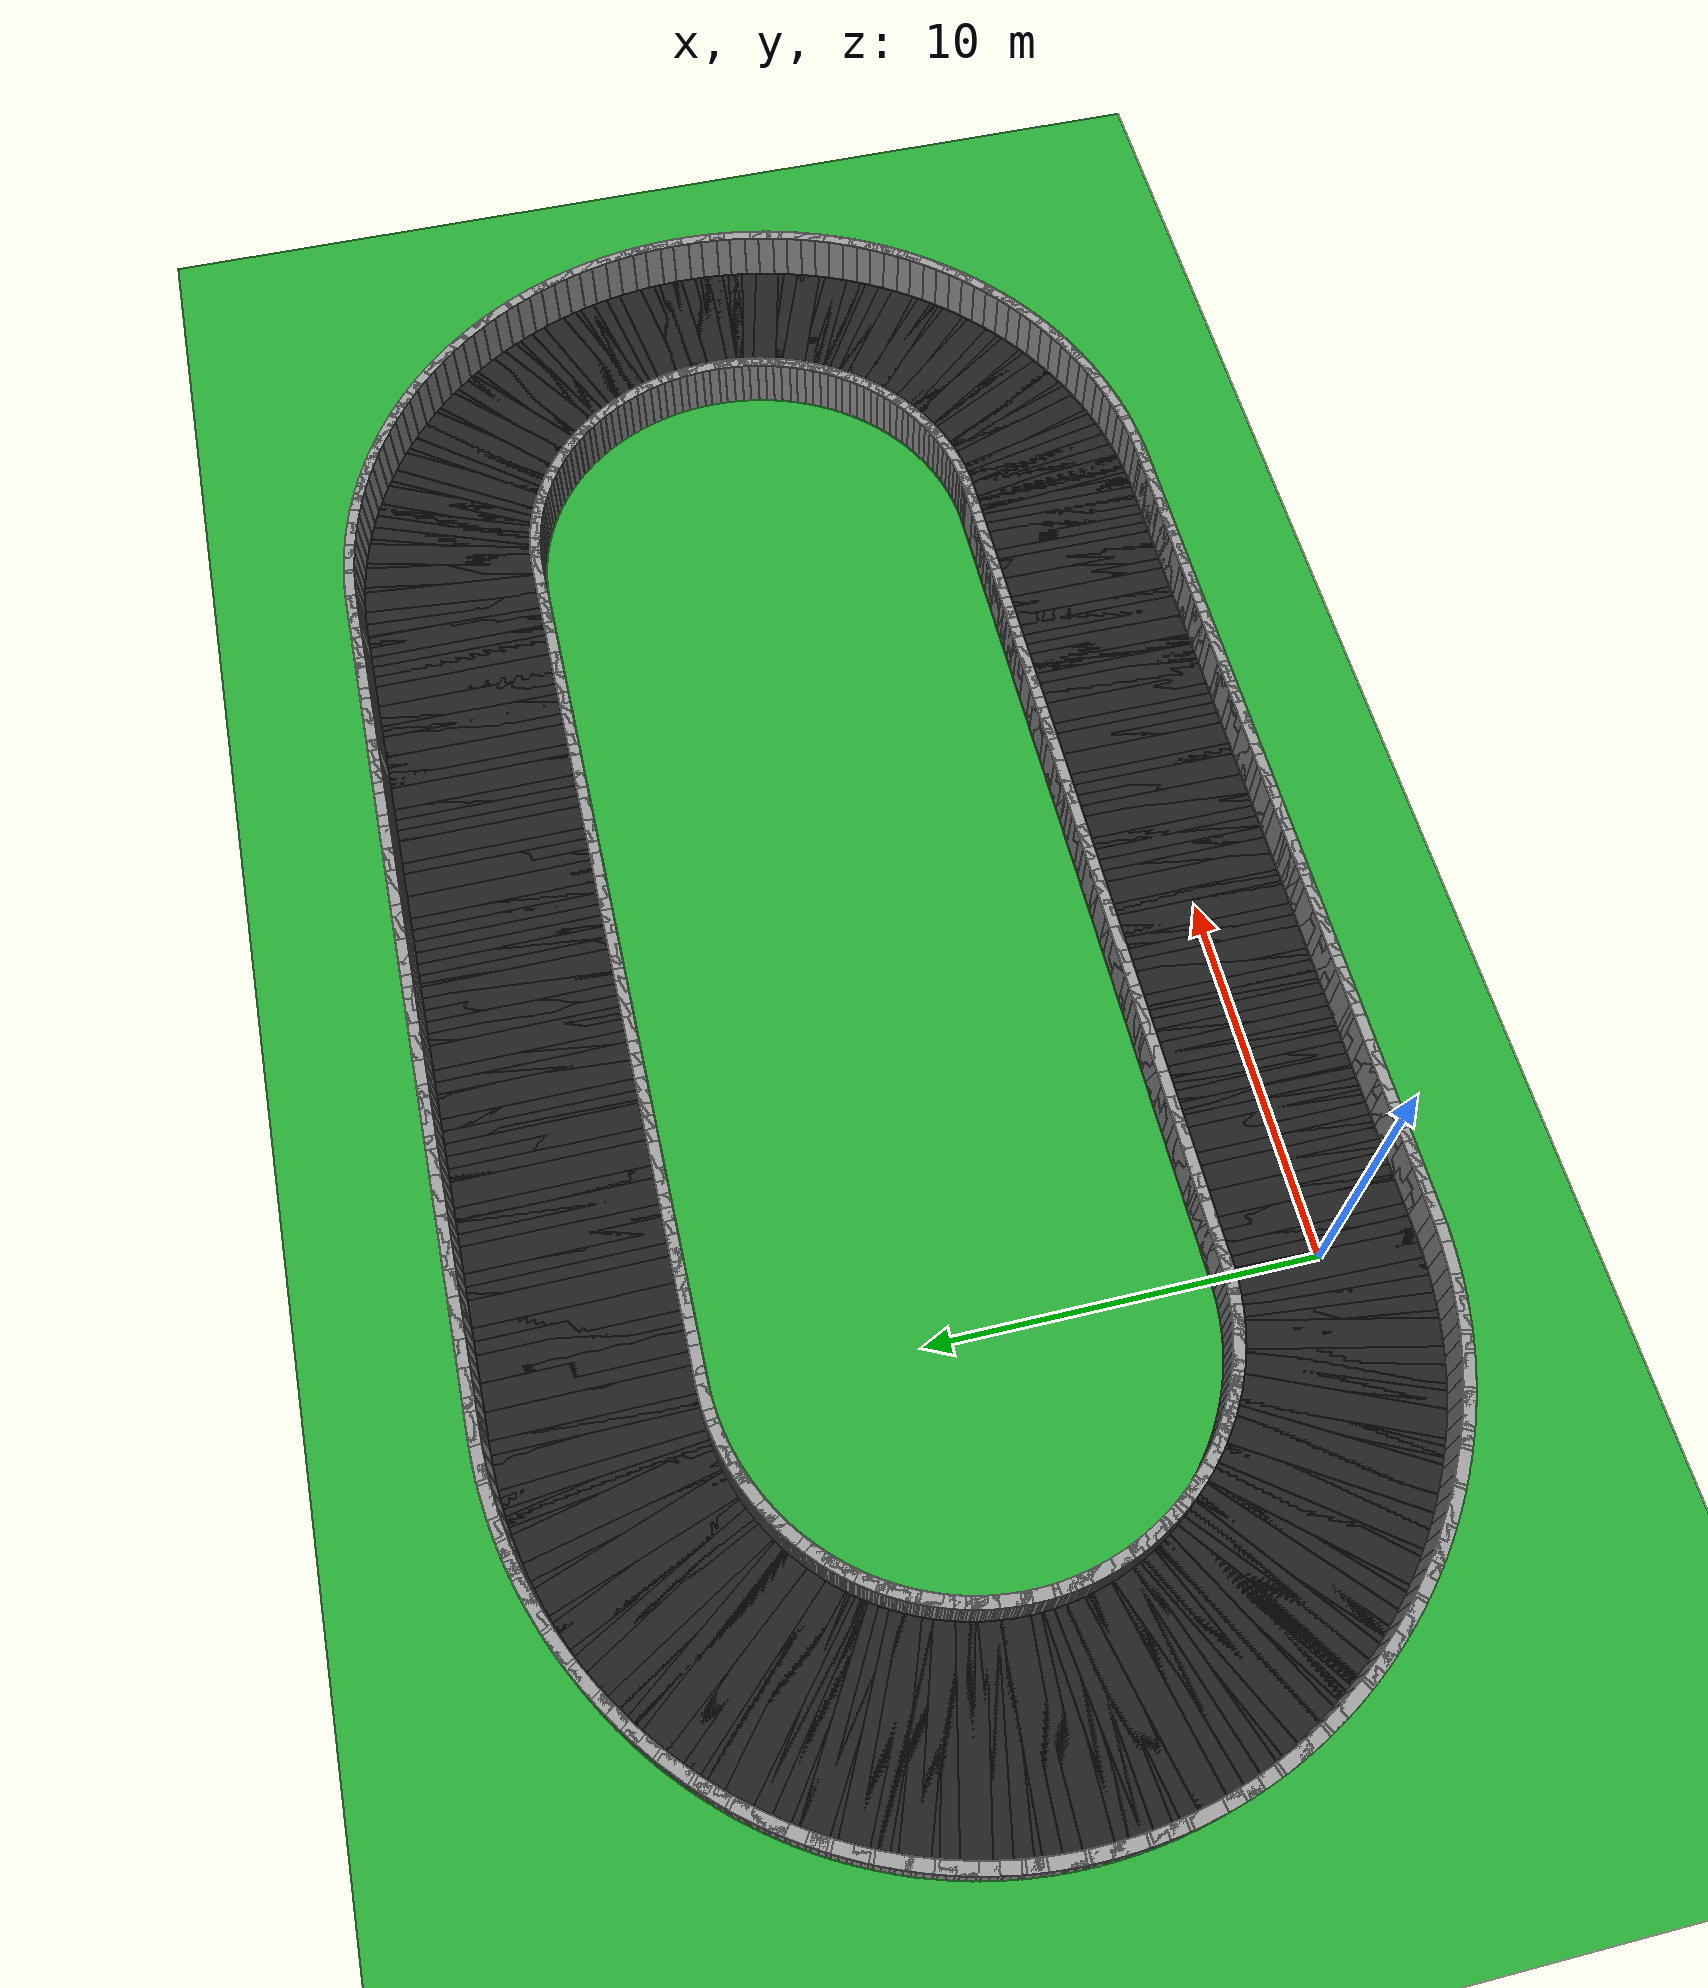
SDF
<?xml version="1.0" ?>
<sdf version="1.6">
  <world name="loop_stadium">
    <physics type="ode">
      <max_step_size>0.001</max_step_size>
      <real_time_factor>1.0</real_time_factor>
      <real_time_update_rate>1000</real_time_update_rate>
    </physics>
    <include><uri>model://sun</uri></include>

    <model name="ground_plane">
      <static>true</static>
      <link name="link">
        <collision name="collision">
          <surface><friction><ode><mu>100</mu><mu2>50</mu2></ode></friction></surface>
          <geometry><plane><normal>0 0 1</normal>
            <size>120 120</size></plane></geometry>
        </collision>
        <visual name="visual">
          <geometry><plane><normal>0 0 1</normal>
            <size>120 120</size></plane></geometry>
          <material><script>
            <uri>file://media/materials/scripts/gazebo.material</uri>
            <name>Gazebo/Green</name></script></material>
        </visual>
      </link>
    </model>

    <model name="asphalt_0">
      <static>true</static>
      <pose>0.174 0.000 0.005 0 0 0.00000</pose>
      <link name="link">
        <visual name="visual">
          <geometry><box><size>0.708 5.000 0.010</size></box></geometry>
          <material><script><uri>file://media/materials/scripts/gazebo.material</uri><name>Gazebo/Black</name></script></material>
        </visual>
      </link>
    </model>
    <model name="curbL_0">
      <static>true</static>
      <pose>0.174 2.650 0.750 0 0 0.00000</pose>
      <link name="link">
        <collision name="collision">
          <geometry><box><size>0.708 0.300 1.500</size></box></geometry>
        </collision>
        <visual name="visual">
          <geometry><box><size>0.708 0.300 1.500</size></box></geometry>
          <material><script><uri>file://media/materials/scripts/gazebo.material</uri><name>Gazebo/Grey</name></script></material>
        </visual>
      </link>
    </model>
    <model name="curbR_0">
      <static>true</static>
      <pose>0.174 -2.650 0.750 0 0 0.00000</pose>
      <link name="link">
        <collision name="collision">
          <geometry><box><size>0.708 0.300 1.500</size></box></geometry>
        </collision>
        <visual name="visual">
          <geometry><box><size>0.708 0.300 1.500</size></box></geometry>
          <material><script><uri>file://media/materials/scripts/gazebo.material</uri><name>Gazebo/Grey</name></script></material>
        </visual>
      </link>
    </model>
    <model name="asphalt_1">
      <static>true</static>
      <pose>0.522 0.000 0.005 0 0 0.00000</pose>
      <link name="link">
        <visual name="visual">
          <geometry><box><size>0.708 5.000 0.010</size></box></geometry>
          <material><script><uri>file://media/materials/scripts/gazebo.material</uri><name>Gazebo/Black</name></script></material>
        </visual>
      </link>
    </model>
    <model name="curbL_1">
      <static>true</static>
      <pose>0.522 2.650 0.750 0 0 0.00000</pose>
      <link name="link">
        <collision name="collision">
          <geometry><box><size>0.708 0.300 1.500</size></box></geometry>
        </collision>
        <visual name="visual">
          <geometry><box><size>0.708 0.300 1.500</size></box></geometry>
          <material><script><uri>file://media/materials/scripts/gazebo.material</uri><name>Gazebo/Grey</name></script></material>
        </visual>
      </link>
    </model>
    <model name="curbR_1">
      <static>true</static>
      <pose>0.522 -2.650 0.750 0 0 0.00000</pose>
      <link name="link">
        <collision name="collision">
          <geometry><box><size>0.708 0.300 1.500</size></box></geometry>
        </collision>
        <visual name="visual">
          <geometry><box><size>0.708 0.300 1.500</size></box></geometry>
          <material><script><uri>file://media/materials/scripts/gazebo.material</uri><name>Gazebo/Grey</name></script></material>
        </visual>
      </link>
    </model>
    <model name="asphalt_2">
      <static>true</static>
      <pose>0.870 0.000 0.005 0 0 0.00000</pose>
      <link name="link">
        <visual name="visual">
          <geometry><box><size>0.708 5.000 0.010</size></box></geometry>
          <material><script><uri>file://media/materials/scripts/gazebo.material</uri><name>Gazebo/Black</name></script></material>
        </visual>
      </link>
    </model>
    <model name="curbL_2">
      <static>true</static>
      <pose>0.870 2.650 0.750 0 0 0.00000</pose>
      <link name="link">
        <collision name="collision">
          <geometry><box><size>0.708 0.300 1.500</size></box></geometry>
        </collision>
        <visual name="visual">
          <geometry><box><size>0.708 0.300 1.500</size></box></geometry>
          <material><script><uri>file://media/materials/scripts/gazebo.material</uri><name>Gazebo/Grey</name></script></material>
        </visual>
      </link>
    </model>
    <model name="curbR_2">
      <static>true</static>
      <pose>0.870 -2.650 0.750 0 0 0.00000</pose>
      <link name="link">
        <collision name="collision">
          <geometry><box><size>0.708 0.300 1.500</size></box></geometry>
        </collision>
        <visual name="visual">
          <geometry><box><size>0.708 0.300 1.500</size></box></geometry>
          <material><script><uri>file://media/materials/scripts/gazebo.material</uri><name>Gazebo/Grey</name></script></material>
        </visual>
      </link>
    </model>
    <model name="asphalt_3">
      <static>true</static>
      <pose>1.217 0.000 0.005 0 0 0.00000</pose>
      <link name="link">
        <visual name="visual">
          <geometry><box><size>0.708 5.000 0.010</size></box></geometry>
          <material><script><uri>file://media/materials/scripts/gazebo.material</uri><name>Gazebo/Black</name></script></material>
        </visual>
      </link>
    </model>
    <model name="curbL_3">
      <static>true</static>
      <pose>1.217 2.650 0.750 0 0 0.00000</pose>
      <link name="link">
        <collision name="collision">
          <geometry><box><size>0.708 0.300 1.500</size></box></geometry>
        </collision>
        <visual name="visual">
          <geometry><box><size>0.708 0.300 1.500</size></box></geometry>
          <material><script><uri>file://media/materials/scripts/gazebo.material</uri><name>Gazebo/Grey</name></script></material>
        </visual>
      </link>
    </model>
    <model name="curbR_3">
      <static>true</static>
      <pose>1.217 -2.650 0.750 0 0 0.00000</pose>
      <link name="link">
        <collision name="collision">
          <geometry><box><size>0.708 0.300 1.500</size></box></geometry>
        </collision>
        <visual name="visual">
          <geometry><box><size>0.708 0.300 1.500</size></box></geometry>
          <material><script><uri>file://media/materials/scripts/gazebo.material</uri><name>Gazebo/Grey</name></script></material>
        </visual>
      </link>
    </model>
    <model name="asphalt_4">
      <static>true</static>
      <pose>1.565 0.000 0.005 0 0 0.00000</pose>
      <link name="link">
        <visual name="visual">
          <geometry><box><size>0.708 5.000 0.010</size></box></geometry>
          <material><script><uri>file://media/materials/scripts/gazebo.material</uri><name>Gazebo/Black</name></script></material>
        </visual>
      </link>
    </model>
    <model name="curbL_4">
      <static>true</static>
      <pose>1.565 2.650 0.750 0 0 0.00000</pose>
      <link name="link">
        <collision name="collision">
          <geometry><box><size>0.708 0.300 1.500</size></box></geometry>
        </collision>
        <visual name="visual">
          <geometry><box><size>0.708 0.300 1.500</size></box></geometry>
          <material><script><uri>file://media/materials/scripts/gazebo.material</uri><name>Gazebo/Grey</name></script></material>
        </visual>
      </link>
    </model>
    <model name="curbR_4">
      <static>true</static>
      <pose>1.565 -2.650 0.750 0 0 0.00000</pose>
      <link name="link">
        <collision name="collision">
          <geometry><box><size>0.708 0.300 1.500</size></box></geometry>
        </collision>
        <visual name="visual">
          <geometry><box><size>0.708 0.300 1.500</size></box></geometry>
          <material><script><uri>file://media/materials/scripts/gazebo.material</uri><name>Gazebo/Grey</name></script></material>
        </visual>
      </link>
    </model>
    <model name="asphalt_5">
      <static>true</static>
      <pose>1.913 0.000 0.005 0 0 0.00000</pose>
      <link name="link">
        <visual name="visual">
          <geometry><box><size>0.708 5.000 0.010</size></box></geometry>
          <material><script><uri>file://media/materials/scripts/gazebo.material</uri><name>Gazebo/Black</name></script></material>
        </visual>
      </link>
    </model>
    <model name="curbL_5">
      <static>true</static>
      <pose>1.913 2.650 0.750 0 0 0.00000</pose>
      <link name="link">
        <collision name="collision">
          <geometry><box><size>0.708 0.300 1.500</size></box></geometry>
        </collision>
        <visual name="visual">
          <geometry><box><size>0.708 0.300 1.500</size></box></geometry>
          <material><script><uri>file://media/materials/scripts/gazebo.material</uri><name>Gazebo/Grey</name></script></material>
        </visual>
      </link>
    </model>
    <model name="curbR_5">
      <static>true</static>
      <pose>1.913 -2.650 0.750 0 0 0.00000</pose>
      <link name="link">
        <collision name="collision">
          <geometry><box><size>0.708 0.300 1.500</size></box></geometry>
        </collision>
        <visual name="visual">
          <geometry><box><size>0.708 0.300 1.500</size></box></geometry>
          <material><script><uri>file://media/materials/scripts/gazebo.material</uri><name>Gazebo/Grey</name></script></material>
        </visual>
      </link>
    </model>
    <model name="asphalt_6">
      <static>true</static>
      <pose>2.261 0.000 0.005 0 0 0.00000</pose>
      <link name="link">
        <visual name="visual">
          <geometry><box><size>0.708 5.000 0.010</size></box></geometry>
          <material><script><uri>file://media/materials/scripts/gazebo.material</uri><name>Gazebo/Black</name></script></material>
        </visual>
      </link>
    </model>
    <model name="curbL_6">
      <static>true</static>
      <pose>2.261 2.650 0.750 0 0 0.00000</pose>
      <link name="link">
        <collision name="collision">
          <geometry><box><size>0.708 0.300 1.500</size></box></geometry>
        </collision>
        <visual name="visual">
          <geometry><box><size>0.708 0.300 1.500</size></box></geometry>
          <material><script><uri>file://media/materials/scripts/gazebo.material</uri><name>Gazebo/Grey</name></script></material>
        </visual>
      </link>
    </model>
    <model name="curbR_6">
      <static>true</static>
      <pose>2.261 -2.650 0.750 0 0 0.00000</pose>
      <link name="link">
        <collision name="collision">
          <geometry><box><size>0.708 0.300 1.500</size></box></geometry>
        </collision>
        <visual name="visual">
          <geometry><box><size>0.708 0.300 1.500</size></box></geometry>
          <material><script><uri>file://media/materials/scripts/gazebo.material</uri><name>Gazebo/Grey</name></script></material>
        </visual>
      </link>
    </model>
    <model name="asphalt_7">
      <static>true</static>
      <pose>2.609 0.000 0.005 0 0 0.00000</pose>
      <link name="link">
        <visual name="visual">
          <geometry><box><size>0.708 5.000 0.010</size></box></geometry>
          <material><script><uri>file://media/materials/scripts/gazebo.material</uri><name>Gazebo/Black</name></script></material>
        </visual>
      </link>
    </model>
    <model name="curbL_7">
      <static>true</static>
      <pose>2.609 2.650 0.750 0 0 0.00000</pose>
      <link name="link">
        <collision name="collision">
          <geometry><box><size>0.708 0.300 1.500</size></box></geometry>
        </collision>
        <visual name="visual">
          <geometry><box><size>0.708 0.300 1.500</size></box></geometry>
          <material><script><uri>file://media/materials/scripts/gazebo.material</uri><name>Gazebo/Grey</name></script></material>
        </visual>
      </link>
    </model>
    <model name="curbR_7">
      <static>true</static>
      <pose>2.609 -2.650 0.750 0 0 0.00000</pose>
      <link name="link">
        <collision name="collision">
          <geometry><box><size>0.708 0.300 1.500</size></box></geometry>
        </collision>
        <visual name="visual">
          <geometry><box><size>0.708 0.300 1.500</size></box></geometry>
          <material><script><uri>file://media/materials/scripts/gazebo.material</uri><name>Gazebo/Grey</name></script></material>
        </visual>
      </link>
    </model>
    <model name="asphalt_8">
      <static>true</static>
      <pose>2.957 0.000 0.005 0 0 0.00000</pose>
      <link name="link">
        <visual name="visual">
          <geometry><box><size>0.708 5.000 0.010</size></box></geometry>
          <material><script><uri>file://media/materials/scripts/gazebo.material</uri><name>Gazebo/Black</name></script></material>
        </visual>
      </link>
    </model>
    <model name="curbL_8">
      <static>true</static>
      <pose>2.957 2.650 0.750 0 0 0.00000</pose>
      <link name="link">
        <collision name="collision">
          <geometry><box><size>0.708 0.300 1.500</size></box></geometry>
        </collision>
        <visual name="visual">
          <geometry><box><size>0.708 0.300 1.500</size></box></geometry>
          <material><script><uri>file://media/materials/scripts/gazebo.material</uri><name>Gazebo/Grey</name></script></material>
        </visual>
      </link>
    </model>
    <model name="curbR_8">
      <static>true</static>
      <pose>2.957 -2.650 0.750 0 0 0.00000</pose>
      <link name="link">
        <collision name="collision">
          <geometry><box><size>0.708 0.300 1.500</size></box></geometry>
        </collision>
        <visual name="visual">
          <geometry><box><size>0.708 0.300 1.500</size></box></geometry>
          <material><script><uri>file://media/materials/scripts/gazebo.material</uri><name>Gazebo/Grey</name></script></material>
        </visual>
      </link>
    </model>
    <model name="asphalt_9">
      <static>true</static>
      <pose>3.304 0.000 0.005 0 0 0.00000</pose>
      <link name="link">
        <visual name="visual">
          <geometry><box><size>0.708 5.000 0.010</size></box></geometry>
          <material><script><uri>file://media/materials/scripts/gazebo.material</uri><name>Gazebo/Black</name></script></material>
        </visual>
      </link>
    </model>
    <model name="curbL_9">
      <static>true</static>
      <pose>3.304 2.650 0.750 0 0 0.00000</pose>
      <link name="link">
        <collision name="collision">
          <geometry><box><size>0.708 0.300 1.500</size></box></geometry>
        </collision>
        <visual name="visual">
          <geometry><box><size>0.708 0.300 1.500</size></box></geometry>
          <material><script><uri>file://media/materials/scripts/gazebo.material</uri><name>Gazebo/Grey</name></script></material>
        </visual>
      </link>
    </model>
    <model name="curbR_9">
      <static>true</static>
      <pose>3.304 -2.650 0.750 0 0 0.00000</pose>
      <link name="link">
        <collision name="collision">
          <geometry><box><size>0.708 0.300 1.500</size></box></geometry>
        </collision>
        <visual name="visual">
          <geometry><box><size>0.708 0.300 1.500</size></box></geometry>
          <material><script><uri>file://media/materials/scripts/gazebo.material</uri><name>Gazebo/Grey</name></script></material>
        </visual>
      </link>
    </model>
    <model name="asphalt_10">
      <static>true</static>
      <pose>3.652 0.000 0.005 0 0 0.00000</pose>
      <link name="link">
        <visual name="visual">
          <geometry><box><size>0.708 5.000 0.010</size></box></geometry>
          <material><script><uri>file://media/materials/scripts/gazebo.material</uri><name>Gazebo/Black</name></script></material>
        </visual>
      </link>
    </model>
    <model name="curbL_10">
      <static>true</static>
      <pose>3.652 2.650 0.750 0 0 0.00000</pose>
      <link name="link">
        <collision name="collision">
          <geometry><box><size>0.708 0.300 1.500</size></box></geometry>
        </collision>
        <visual name="visual">
          <geometry><box><size>0.708 0.300 1.500</size></box></geometry>
          <material><script><uri>file://media/materials/scripts/gazebo.material</uri><name>Gazebo/Grey</name></script></material>
        </visual>
      </link>
    </model>
    <model name="curbR_10">
      <static>true</static>
      <pose>3.652 -2.650 0.750 0 0 0.00000</pose>
      <link name="link">
        <collision name="collision">
          <geometry><box><size>0.708 0.300 1.500</size></box></geometry>
        </collision>
        <visual name="visual">
          <geometry><box><size>0.708 0.300 1.500</size></box></geometry>
          <material><script><uri>file://media/materials/scripts/gazebo.material</uri><name>Gazebo/Grey</name></script></material>
        </visual>
      </link>
    </model>
    <model name="asphalt_11">
      <static>true</static>
      <pose>4.000 0.000 0.005 0 0 0.00000</pose>
      <link name="link">
        <visual name="visual">
          <geometry><box><size>0.708 5.000 0.010</size></box></geometry>
          <material><script><uri>file://media/materials/scripts/gazebo.material</uri><name>Gazebo/Black</name></script></material>
        </visual>
      </link>
    </model>
    <model name="curbL_11">
      <static>true</static>
      <pose>4.000 2.650 0.750 0 0 0.00000</pose>
      <link name="link">
        <collision name="collision">
          <geometry><box><size>0.708 0.300 1.500</size></box></geometry>
        </collision>
        <visual name="visual">
          <geometry><box><size>0.708 0.300 1.500</size></box></geometry>
          <material><script><uri>file://media/materials/scripts/gazebo.material</uri><name>Gazebo/Grey</name></script></material>
        </visual>
      </link>
    </model>
    <model name="curbR_11">
      <static>true</static>
      <pose>4.000 -2.650 0.750 0 0 0.00000</pose>
      <link name="link">
        <collision name="collision">
          <geometry><box><size>0.708 0.300 1.500</size></box></geometry>
        </collision>
        <visual name="visual">
          <geometry><box><size>0.708 0.300 1.500</size></box></geometry>
          <material><script><uri>file://media/materials/scripts/gazebo.material</uri><name>Gazebo/Grey</name></script></material>
        </visual>
      </link>
    </model>
    <model name="asphalt_12">
      <static>true</static>
      <pose>4.348 0.000 0.005 0 0 0.00000</pose>
      <link name="link">
        <visual name="visual">
          <geometry><box><size>0.708 5.000 0.010</size></box></geometry>
          <material><script><uri>file://media/materials/scripts/gazebo.material</uri><name>Gazebo/Black</name></script></material>
        </visual>
      </link>
    </model>
    <model name="curbL_12">
      <static>true</static>
      <pose>4.348 2.650 0.750 0 0 0.00000</pose>
      <link name="link">
        <collision name="collision">
          <geometry><box><size>0.708 0.300 1.500</size></box></geometry>
        </collision>
        <visual name="visual">
          <geometry><box><size>0.708 0.300 1.500</size></box></geometry>
          <material><script><uri>file://media/materials/scripts/gazebo.material</uri><name>Gazebo/Grey</name></script></material>
        </visual>
      </link>
    </model>
    <model name="curbR_12">
      <static>true</static>
      <pose>4.348 -2.650 0.750 0 0 0.00000</pose>
      <link name="link">
        <collision name="collision">
          <geometry><box><size>0.708 0.300 1.500</size></box></geometry>
        </collision>
        <visual name="visual">
          <geometry><box><size>0.708 0.300 1.500</size></box></geometry>
          <material><script><uri>file://media/materials/scripts/gazebo.material</uri><name>Gazebo/Grey</name></script></material>
        </visual>
      </link>
    </model>
    <model name="asphalt_13">
      <static>true</static>
      <pose>4.696 0.000 0.005 0 0 0.00000</pose>
      <link name="link">
        <visual name="visual">
          <geometry><box><size>0.708 5.000 0.010</size></box></geometry>
          <material><script><uri>file://media/materials/scripts/gazebo.material</uri><name>Gazebo/Black</name></script></material>
        </visual>
      </link>
    </model>
    <model name="curbL_13">
      <static>true</static>
      <pose>4.696 2.650 0.750 0 0 0.00000</pose>
      <link name="link">
        <collision name="collision">
          <geometry><box><size>0.708 0.300 1.500</size></box></geometry>
        </collision>
        <visual name="visual">
          <geometry><box><size>0.708 0.300 1.500</size></box></geometry>
          <material><script><uri>file://media/materials/scripts/gazebo.material</uri><name>Gazebo/Grey</name></script></material>
        </visual>
      </link>
    </model>
    <model name="curbR_13">
      <static>true</static>
      <pose>4.696 -2.650 0.750 0 0 0.00000</pose>
      <link name="link">
        <collision name="collision">
          <geometry><box><size>0.708 0.300 1.500</size></box></geometry>
        </collision>
        <visual name="visual">
          <geometry><box><size>0.708 0.300 1.500</size></box></geometry>
          <material><script><uri>file://media/materials/scripts/gazebo.material</uri><name>Gazebo/Grey</name></script></material>
        </visual>
      </link>
    </model>
    <model name="asphalt_14">
      <static>true</static>
      <pose>5.043 0.000 0.005 0 0 0.00000</pose>
      <link name="link">
        <visual name="visual">
          <geometry><box><size>0.708 5.000 0.010</size></box></geometry>
          <material><script><uri>file://media/materials/scripts/gazebo.material</uri><name>Gazebo/Black</name></script></material>
        </visual>
      </link>
    </model>
    <model name="curbL_14">
      <static>true</static>
      <pose>5.043 2.650 0.750 0 0 0.00000</pose>
      <link name="link">
        <collision name="collision">
          <geometry><box><size>0.708 0.300 1.500</size></box></geometry>
        </collision>
        <visual name="visual">
          <geometry><box><size>0.708 0.300 1.500</size></box></geometry>
          <material><script><uri>file://media/materials/scripts/gazebo.material</uri><name>Gazebo/Grey</name></script></material>
        </visual>
      </link>
    </model>
    <model name="curbR_14">
      <static>true</static>
      <pose>5.043 -2.650 0.750 0 0 0.00000</pose>
      <link name="link">
        <collision name="collision">
          <geometry><box><size>0.708 0.300 1.500</size></box></geometry>
        </collision>
        <visual name="visual">
          <geometry><box><size>0.708 0.300 1.500</size></box></geometry>
          <material><script><uri>file://media/materials/scripts/gazebo.material</uri><name>Gazebo/Grey</name></script></material>
        </visual>
      </link>
    </model>
    <model name="asphalt_15">
      <static>true</static>
      <pose>5.391 0.000 0.005 0 0 0.00000</pose>
      <link name="link">
        <visual name="visual">
          <geometry><box><size>0.708 5.000 0.010</size></box></geometry>
          <material><script><uri>file://media/materials/scripts/gazebo.material</uri><name>Gazebo/Black</name></script></material>
        </visual>
      </link>
    </model>
    <model name="curbL_15">
      <static>true</static>
      <pose>5.391 2.650 0.750 0 0 0.00000</pose>
      <link name="link">
        <collision name="collision">
          <geometry><box><size>0.708 0.300 1.500</size></box></geometry>
        </collision>
        <visual name="visual">
          <geometry><box><size>0.708 0.300 1.500</size></box></geometry>
          <material><script><uri>file://media/materials/scripts/gazebo.material</uri><name>Gazebo/Grey</name></script></material>
        </visual>
      </link>
    </model>
    <model name="curbR_15">
      <static>true</static>
      <pose>5.391 -2.650 0.750 0 0 0.00000</pose>
      <link name="link">
        <collision name="collision">
          <geometry><box><size>0.708 0.300 1.500</size></box></geometry>
        </collision>
        <visual name="visual">
          <geometry><box><size>0.708 0.300 1.500</size></box></geometry>
          <material><script><uri>file://media/materials/scripts/gazebo.material</uri><name>Gazebo/Grey</name></script></material>
        </visual>
      </link>
    </model>
    <model name="asphalt_16">
      <static>true</static>
      <pose>5.739 0.000 0.005 0 0 0.00000</pose>
      <link name="link">
        <visual name="visual">
          <geometry><box><size>0.708 5.000 0.010</size></box></geometry>
          <material><script><uri>file://media/materials/scripts/gazebo.material</uri><name>Gazebo/Black</name></script></material>
        </visual>
      </link>
    </model>
    <model name="curbL_16">
      <static>true</static>
      <pose>5.739 2.650 0.750 0 0 0.00000</pose>
      <link name="link">
        <collision name="collision">
          <geometry><box><size>0.708 0.300 1.500</size></box></geometry>
        </collision>
        <visual name="visual">
          <geometry><box><size>0.708 0.300 1.500</size></box></geometry>
          <material><script><uri>file://media/materials/scripts/gazebo.material</uri><name>Gazebo/Grey</name></script></material>
        </visual>
      </link>
    </model>
    <model name="curbR_16">
      <static>true</static>
      <pose>5.739 -2.650 0.750 0 0 0.00000</pose>
      <link name="link">
        <collision name="collision">
          <geometry><box><size>0.708 0.300 1.500</size></box></geometry>
        </collision>
        <visual name="visual">
          <geometry><box><size>0.708 0.300 1.500</size></box></geometry>
          <material><script><uri>file://media/materials/scripts/gazebo.material</uri><name>Gazebo/Grey</name></script></material>
        </visual>
      </link>
    </model>
    <model name="asphalt_17">
      <static>true</static>
      <pose>6.087 0.000 0.005 0 0 0.00000</pose>
      <link name="link">
        <visual name="visual">
          <geometry><box><size>0.708 5.000 0.010</size></box></geometry>
          <material><script><uri>file://media/materials/scripts/gazebo.material</uri><name>Gazebo/Black</name></script></material>
        </visual>
      </link>
    </model>
    <model name="curbL_17">
      <static>true</static>
      <pose>6.087 2.650 0.750 0 0 0.00000</pose>
      <link name="link">
        <collision name="collision">
          <geometry><box><size>0.708 0.300 1.500</size></box></geometry>
        </collision>
        <visual name="visual">
          <geometry><box><size>0.708 0.300 1.500</size></box></geometry>
          <material><script><uri>file://media/materials/scripts/gazebo.material</uri><name>Gazebo/Grey</name></script></material>
        </visual>
      </link>
    </model>
    <model name="curbR_17">
      <static>true</static>
      <pose>6.087 -2.650 0.750 0 0 0.00000</pose>
      <link name="link">
        <collision name="collision">
          <geometry><box><size>0.708 0.300 1.500</size></box></geometry>
        </collision>
        <visual name="visual">
          <geometry><box><size>0.708 0.300 1.500</size></box></geometry>
          <material><script><uri>file://media/materials/scripts/gazebo.material</uri><name>Gazebo/Grey</name></script></material>
        </visual>
      </link>
    </model>
    <model name="asphalt_18">
      <static>true</static>
      <pose>6.435 0.000 0.005 0 0 0.00000</pose>
      <link name="link">
        <visual name="visual">
          <geometry><box><size>0.708 5.000 0.010</size></box></geometry>
          <material><script><uri>file://media/materials/scripts/gazebo.material</uri><name>Gazebo/Black</name></script></material>
        </visual>
      </link>
    </model>
    <model name="curbL_18">
      <static>true</static>
      <pose>6.435 2.650 0.750 0 0 0.00000</pose>
      <link name="link">
        <collision name="collision">
          <geometry><box><size>0.708 0.300 1.500</size></box></geometry>
        </collision>
        <visual name="visual">
          <geometry><box><size>0.708 0.300 1.500</size></box></geometry>
          <material><script><uri>file://media/materials/scripts/gazebo.material</uri><name>Gazebo/Grey</name></script></material>
        </visual>
      </link>
    </model>
    <model name="curbR_18">
      <static>true</static>
      <pose>6.435 -2.650 0.750 0 0 0.00000</pose>
      <link name="link">
        <collision name="collision">
          <geometry><box><size>0.708 0.300 1.500</size></box></geometry>
        </collision>
        <visual name="visual">
          <geometry><box><size>0.708 0.300 1.500</size></box></geometry>
          <material><script><uri>file://media/materials/scripts/gazebo.material</uri><name>Gazebo/Grey</name></script></material>
        </visual>
      </link>
    </model>
    <model name="asphalt_19">
      <static>true</static>
      <pose>6.783 0.000 0.005 0 0 0.00000</pose>
      <link name="link">
        <visual name="visual">
          <geometry><box><size>0.708 5.000 0.010</size></box></geometry>
          <material><script><uri>file://media/materials/scripts/gazebo.material</uri><name>Gazebo/Black</name></script></material>
        </visual>
      </link>
    </model>
    <model name="curbL_19">
      <static>true</static>
      <pose>6.783 2.650 0.750 0 0 0.00000</pose>
      <link name="link">
        <collision name="collision">
          <geometry><box><size>0.708 0.300 1.500</size></box></geometry>
        </collision>
        <visual name="visual">
          <geometry><box><size>0.708 0.300 1.500</size></box></geometry>
          <material><script><uri>file://media/materials/scripts/gazebo.material</uri><name>Gazebo/Grey</name></script></material>
        </visual>
      </link>
    </model>
    <model name="curbR_19">
      <static>true</static>
      <pose>6.783 -2.650 0.750 0 0 0.00000</pose>
      <link name="link">
        <collision name="collision">
          <geometry><box><size>0.708 0.300 1.500</size></box></geometry>
        </collision>
        <visual name="visual">
          <geometry><box><size>0.708 0.300 1.500</size></box></geometry>
          <material><script><uri>file://media/materials/scripts/gazebo.material</uri><name>Gazebo/Grey</name></script></material>
        </visual>
      </link>
    </model>
    <model name="asphalt_20">
      <static>true</static>
      <pose>7.130 0.000 0.005 0 0 0.00000</pose>
      <link name="link">
        <visual name="visual">
          <geometry><box><size>0.708 5.000 0.010</size></box></geometry>
          <material><script><uri>file://media/materials/scripts/gazebo.material</uri><name>Gazebo/Black</name></script></material>
        </visual>
      </link>
    </model>
    <model name="curbL_20">
      <static>true</static>
      <pose>7.130 2.650 0.750 0 0 0.00000</pose>
      <link name="link">
        <collision name="collision">
          <geometry><box><size>0.708 0.300 1.500</size></box></geometry>
        </collision>
        <visual name="visual">
          <geometry><box><size>0.708 0.300 1.500</size></box></geometry>
          <material><script><uri>file://media/materials/scripts/gazebo.material</uri><name>Gazebo/Grey</name></script></material>
        </visual>
      </link>
    </model>
    <model name="curbR_20">
      <static>true</static>
      <pose>7.130 -2.650 0.750 0 0 0.00000</pose>
      <link name="link">
        <collision name="collision">
          <geometry><box><size>0.708 0.300 1.500</size></box></geometry>
        </collision>
        <visual name="visual">
          <geometry><box><size>0.708 0.300 1.500</size></box></geometry>
          <material><script><uri>file://media/materials/scripts/gazebo.material</uri><name>Gazebo/Grey</name></script></material>
        </visual>
      </link>
    </model>
    <model name="asphalt_21">
      <static>true</static>
      <pose>7.478 0.000 0.005 0 0 0.00000</pose>
      <link name="link">
        <visual name="visual">
          <geometry><box><size>0.708 5.000 0.010</size></box></geometry>
          <material><script><uri>file://media/materials/scripts/gazebo.material</uri><name>Gazebo/Black</name></script></material>
        </visual>
      </link>
    </model>
    <model name="curbL_21">
      <static>true</static>
      <pose>7.478 2.650 0.750 0 0 0.00000</pose>
      <link name="link">
        <collision name="collision">
          <geometry><box><size>0.708 0.300 1.500</size></box></geometry>
        </collision>
        <visual name="visual">
          <geometry><box><size>0.708 0.300 1.500</size></box></geometry>
          <material><script><uri>file://media/materials/scripts/gazebo.material</uri><name>Gazebo/Grey</name></script></material>
        </visual>
      </link>
    </model>
    <model name="curbR_21">
      <static>true</static>
      <pose>7.478 -2.650 0.750 0 0 0.00000</pose>
      <link name="link">
        <collision name="collision">
          <geometry><box><size>0.708 0.300 1.500</size></box></geometry>
        </collision>
        <visual name="visual">
          <geometry><box><size>0.708 0.300 1.500</size></box></geometry>
          <material><script><uri>file://media/materials/scripts/gazebo.material</uri><name>Gazebo/Grey</name></script></material>
        </visual>
      </link>
    </model>
    <model name="asphalt_22">
      <static>true</static>
      <pose>7.826 0.000 0.005 0 0 0.00000</pose>
      <link name="link">
        <visual name="visual">
          <geometry><box><size>0.708 5.000 0.010</size></box></geometry>
          <material><script><uri>file://media/materials/scripts/gazebo.material</uri><name>Gazebo/Black</name></script></material>
        </visual>
      </link>
    </model>
    <model name="curbL_22">
      <static>true</static>
      <pose>7.826 2.650 0.750 0 0 0.00000</pose>
      <link name="link">
        <collision name="collision">
          <geometry><box><size>0.708 0.300 1.500</size></box></geometry>
        </collision>
        <visual name="visual">
          <geometry><box><size>0.708 0.300 1.500</size></box></geometry>
          <material><script><uri>file://media/materials/scripts/gazebo.material</uri><name>Gazebo/Grey</name></script></material>
        </visual>
      </link>
    </model>
    <model name="curbR_22">
      <static>true</static>
      <pose>7.826 -2.650 0.750 0 0 0.00000</pose>
      <link name="link">
        <collision name="collision">
          <geometry><box><size>0.708 0.300 1.500</size></box></geometry>
        </collision>
        <visual name="visual">
          <geometry><box><size>0.708 0.300 1.500</size></box></geometry>
          <material><script><uri>file://media/materials/scripts/gazebo.material</uri><name>Gazebo/Grey</name></script></material>
        </visual>
      </link>
    </model>
    <model name="asphalt_23">
      <static>true</static>
      <pose>8.174 0.000 0.005 0 0 0.00000</pose>
      <link name="link">
        <visual name="visual">
          <geometry><box><size>0.708 5.000 0.010</size></box></geometry>
          <material><script><uri>file://media/materials/scripts/gazebo.material</uri><name>Gazebo/Black</name></script></material>
        </visual>
      </link>
    </model>
    <model name="curbL_23">
      <static>true</static>
      <pose>8.174 2.650 0.750 0 0 0.00000</pose>
      <link name="link">
        <collision name="collision">
          <geometry><box><size>0.708 0.300 1.500</size></box></geometry>
        </collision>
        <visual name="visual">
          <geometry><box><size>0.708 0.300 1.500</size></box></geometry>
          <material><script><uri>file://media/materials/scripts/gazebo.material</uri><name>Gazebo/Grey</name></script></material>
        </visual>
      </link>
    </model>
    <model name="curbR_23">
      <static>true</static>
      <pose>8.174 -2.650 0.750 0 0 0.00000</pose>
      <link name="link">
        <collision name="collision">
          <geometry><box><size>0.708 0.300 1.500</size></box></geometry>
        </collision>
        <visual name="visual">
          <geometry><box><size>0.708 0.300 1.500</size></box></geometry>
          <material><script><uri>file://media/materials/scripts/gazebo.material</uri><name>Gazebo/Grey</name></script></material>
        </visual>
      </link>
    </model>
    <model name="asphalt_24">
      <static>true</static>
      <pose>8.522 0.000 0.005 0 0 0.00000</pose>
      <link name="link">
        <visual name="visual">
          <geometry><box><size>0.708 5.000 0.010</size></box></geometry>
          <material><script><uri>file://media/materials/scripts/gazebo.material</uri><name>Gazebo/Black</name></script></material>
        </visual>
      </link>
    </model>
    <model name="curbL_24">
      <static>true</static>
      <pose>8.522 2.650 0.750 0 0 0.00000</pose>
      <link name="link">
        <collision name="collision">
          <geometry><box><size>0.708 0.300 1.500</size></box></geometry>
        </collision>
        <visual name="visual">
          <geometry><box><size>0.708 0.300 1.500</size></box></geometry>
          <material><script><uri>file://media/materials/scripts/gazebo.material</uri><name>Gazebo/Grey</name></script></material>
        </visual>
      </link>
    </model>
    <model name="curbR_24">
      <static>true</static>
      <pose>8.522 -2.650 0.750 0 0 0.00000</pose>
      <link name="link">
        <collision name="collision">
          <geometry><box><size>0.708 0.300 1.500</size></box></geometry>
        </collision>
        <visual name="visual">
          <geometry><box><size>0.708 0.300 1.500</size></box></geometry>
          <material><script><uri>file://media/materials/scripts/gazebo.material</uri><name>Gazebo/Grey</name></script></material>
        </visual>
      </link>
    </model>
    <model name="asphalt_25">
      <static>true</static>
      <pose>8.870 0.000 0.005 0 0 0.00000</pose>
      <link name="link">
        <visual name="visual">
          <geometry><box><size>0.708 5.000 0.010</size></box></geometry>
          <material><script><uri>file://media/materials/scripts/gazebo.material</uri><name>Gazebo/Black</name></script></material>
        </visual>
      </link>
    </model>
    <model name="curbL_25">
      <static>true</static>
      <pose>8.870 2.650 0.750 0 0 0.00000</pose>
      <link name="link">
        <collision name="collision">
          <geometry><box><size>0.708 0.300 1.500</size></box></geometry>
        </collision>
        <visual name="visual">
          <geometry><box><size>0.708 0.300 1.500</size></box></geometry>
          <material><script><uri>file://media/materials/scripts/gazebo.material</uri><name>Gazebo/Grey</name></script></material>
        </visual>
      </link>
    </model>
    <model name="curbR_25">
      <static>true</static>
      <pose>8.870 -2.650 0.750 0 0 0.00000</pose>
      <link name="link">
        <collision name="collision">
          <geometry><box><size>0.708 0.300 1.500</size></box></geometry>
        </collision>
        <visual name="visual">
          <geometry><box><size>0.708 0.300 1.500</size></box></geometry>
          <material><script><uri>file://media/materials/scripts/gazebo.material</uri><name>Gazebo/Grey</name></script></material>
        </visual>
      </link>
    </model>
    <model name="asphalt_26">
      <static>true</static>
      <pose>9.217 0.000 0.005 0 0 0.00000</pose>
      <link name="link">
        <visual name="visual">
          <geometry><box><size>0.708 5.000 0.010</size></box></geometry>
          <material><script><uri>file://media/materials/scripts/gazebo.material</uri><name>Gazebo/Black</name></script></material>
        </visual>
      </link>
    </model>
    <model name="curbL_26">
      <static>true</static>
      <pose>9.217 2.650 0.750 0 0 0.00000</pose>
      <link name="link">
        <collision name="collision">
          <geometry><box><size>0.708 0.300 1.500</size></box></geometry>
        </collision>
        <visual name="visual">
          <geometry><box><size>0.708 0.300 1.500</size></box></geometry>
          <material><script><uri>file://media/materials/scripts/gazebo.material</uri><name>Gazebo/Grey</name></script></material>
        </visual>
      </link>
    </model>
    <model name="curbR_26">
      <static>true</static>
      <pose>9.217 -2.650 0.750 0 0 0.00000</pose>
      <link name="link">
        <collision name="collision">
          <geometry><box><size>0.708 0.300 1.500</size></box></geometry>
        </collision>
        <visual name="visual">
          <geometry><box><size>0.708 0.300 1.500</size></box></geometry>
          <material><script><uri>file://media/materials/scripts/gazebo.material</uri><name>Gazebo/Grey</name></script></material>
        </visual>
      </link>
    </model>
    <model name="asphalt_27">
      <static>true</static>
      <pose>9.565 0.000 0.005 0 0 0.00000</pose>
      <link name="link">
        <visual name="visual">
          <geometry><box><size>0.708 5.000 0.010</size></box></geometry>
          <material><script><uri>file://media/materials/scripts/gazebo.material</uri><name>Gazebo/Black</name></script></material>
        </visual>
      </link>
    </model>
    <model name="curbL_27">
      <static>true</static>
      <pose>9.565 2.650 0.750 0 0 0.00000</pose>
      <link name="link">
        <collision name="collision">
          <geometry><box><size>0.708 0.300 1.500</size></box></geometry>
        </collision>
        <visual name="visual">
          <geometry><box><size>0.708 0.300 1.500</size></box></geometry>
          <material><script><uri>file://media/materials/scripts/gazebo.material</uri><name>Gazebo/Grey</name></script></material>
        </visual>
      </link>
    </model>
    <model name="curbR_27">
      <static>true</static>
      <pose>9.565 -2.650 0.750 0 0 0.00000</pose>
      <link name="link">
        <collision name="collision">
          <geometry><box><size>0.708 0.300 1.500</size></box></geometry>
        </collision>
        <visual name="visual">
          <geometry><box><size>0.708 0.300 1.500</size></box></geometry>
          <material><script><uri>file://media/materials/scripts/gazebo.material</uri><name>Gazebo/Grey</name></script></material>
        </visual>
      </link>
    </model>
    <model name="asphalt_28">
      <static>true</static>
      <pose>9.913 0.000 0.005 0 0 0.00000</pose>
      <link name="link">
        <visual name="visual">
          <geometry><box><size>0.708 5.000 0.010</size></box></geometry>
          <material><script><uri>file://media/materials/scripts/gazebo.material</uri><name>Gazebo/Black</name></script></material>
        </visual>
      </link>
    </model>
    <model name="curbL_28">
      <static>true</static>
      <pose>9.913 2.650 0.750 0 0 0.00000</pose>
      <link name="link">
        <collision name="collision">
          <geometry><box><size>0.708 0.300 1.500</size></box></geometry>
        </collision>
        <visual name="visual">
          <geometry><box><size>0.708 0.300 1.500</size></box></geometry>
          <material><script><uri>file://media/materials/scripts/gazebo.material</uri><name>Gazebo/Grey</name></script></material>
        </visual>
      </link>
    </model>
    <model name="curbR_28">
      <static>true</static>
      <pose>9.913 -2.650 0.750 0 0 0.00000</pose>
      <link name="link">
        <collision name="collision">
          <geometry><box><size>0.708 0.300 1.500</size></box></geometry>
        </collision>
        <visual name="visual">
          <geometry><box><size>0.708 0.300 1.500</size></box></geometry>
          <material><script><uri>file://media/materials/scripts/gazebo.material</uri><name>Gazebo/Grey</name></script></material>
        </visual>
      </link>
    </model>
    <model name="asphalt_29">
      <static>true</static>
      <pose>10.261 0.000 0.005 0 0 0.00000</pose>
      <link name="link">
        <visual name="visual">
          <geometry><box><size>0.708 5.000 0.010</size></box></geometry>
          <material><script><uri>file://media/materials/scripts/gazebo.material</uri><name>Gazebo/Black</name></script></material>
        </visual>
      </link>
    </model>
    <model name="curbL_29">
      <static>true</static>
      <pose>10.261 2.650 0.750 0 0 0.00000</pose>
      <link name="link">
        <collision name="collision">
          <geometry><box><size>0.708 0.300 1.500</size></box></geometry>
        </collision>
        <visual name="visual">
          <geometry><box><size>0.708 0.300 1.500</size></box></geometry>
          <material><script><uri>file://media/materials/scripts/gazebo.material</uri><name>Gazebo/Grey</name></script></material>
        </visual>
      </link>
    </model>
    <model name="curbR_29">
      <static>true</static>
      <pose>10.261 -2.650 0.750 0 0 0.00000</pose>
      <link name="link">
        <collision name="collision">
          <geometry><box><size>0.708 0.300 1.500</size></box></geometry>
        </collision>
        <visual name="visual">
          <geometry><box><size>0.708 0.300 1.500</size></box></geometry>
          <material><script><uri>file://media/materials/scripts/gazebo.material</uri><name>Gazebo/Grey</name></script></material>
        </visual>
      </link>
    </model>
    <model name="asphalt_30">
      <static>true</static>
      <pose>10.609 0.000 0.005 0 0 0.00000</pose>
      <link name="link">
        <visual name="visual">
          <geometry><box><size>0.708 5.000 0.010</size></box></geometry>
          <material><script><uri>file://media/materials/scripts/gazebo.material</uri><name>Gazebo/Black</name></script></material>
        </visual>
      </link>
    </model>
    <model name="curbL_30">
      <static>true</static>
      <pose>10.609 2.650 0.750 0 0 0.00000</pose>
      <link name="link">
        <collision name="collision">
          <geometry><box><size>0.708 0.300 1.500</size></box></geometry>
        </collision>
        <visual name="visual">
          <geometry><box><size>0.708 0.300 1.500</size></box></geometry>
          <material><script><uri>file://media/materials/scripts/gazebo.material</uri><name>Gazebo/Grey</name></script></material>
        </visual>
      </link>
    </model>
    <model name="curbR_30">
      <static>true</static>
      <pose>10.609 -2.650 0.750 0 0 0.00000</pose>
      <link name="link">
        <collision name="collision">
          <geometry><box><size>0.708 0.300 1.500</size></box></geometry>
        </collision>
        <visual name="visual">
          <geometry><box><size>0.708 0.300 1.500</size></box></geometry>
          <material><script><uri>file://media/materials/scripts/gazebo.material</uri><name>Gazebo/Grey</name></script></material>
        </visual>
      </link>
    </model>
    <model name="asphalt_31">
      <static>true</static>
      <pose>10.957 0.000 0.005 0 0 0.00000</pose>
      <link name="link">
        <visual name="visual">
          <geometry><box><size>0.708 5.000 0.010</size></box></geometry>
          <material><script><uri>file://media/materials/scripts/gazebo.material</uri><name>Gazebo/Black</name></script></material>
        </visual>
      </link>
    </model>
    <model name="curbL_31">
      <static>true</static>
      <pose>10.957 2.650 0.750 0 0 0.00000</pose>
      <link name="link">
        <collision name="collision">
          <geometry><box><size>0.708 0.300 1.500</size></box></geometry>
        </collision>
        <visual name="visual">
          <geometry><box><size>0.708 0.300 1.500</size></box></geometry>
          <material><script><uri>file://media/materials/scripts/gazebo.material</uri><name>Gazebo/Grey</name></script></material>
        </visual>
      </link>
    </model>
    <model name="curbR_31">
      <static>true</static>
      <pose>10.957 -2.650 0.750 0 0 0.00000</pose>
      <link name="link">
        <collision name="collision">
          <geometry><box><size>0.708 0.300 1.500</size></box></geometry>
        </collision>
        <visual name="visual">
          <geometry><box><size>0.708 0.300 1.500</size></box></geometry>
          <material><script><uri>file://media/materials/scripts/gazebo.material</uri><name>Gazebo/Grey</name></script></material>
        </visual>
      </link>
    </model>
    <model name="asphalt_32">
      <static>true</static>
      <pose>11.304 0.000 0.005 0 0 0.00000</pose>
      <link name="link">
        <visual name="visual">
          <geometry><box><size>0.708 5.000 0.010</size></box></geometry>
          <material><script><uri>file://media/materials/scripts/gazebo.material</uri><name>Gazebo/Black</name></script></material>
        </visual>
      </link>
    </model>
    <model name="curbL_32">
      <static>true</static>
      <pose>11.304 2.650 0.750 0 0 0.00000</pose>
      <link name="link">
        <collision name="collision">
          <geometry><box><size>0.708 0.300 1.500</size></box></geometry>
        </collision>
        <visual name="visual">
          <geometry><box><size>0.708 0.300 1.500</size></box></geometry>
          <material><script><uri>file://media/materials/scripts/gazebo.material</uri><name>Gazebo/Grey</name></script></material>
        </visual>
      </link>
    </model>
    <model name="curbR_32">
      <static>true</static>
      <pose>11.304 -2.650 0.750 0 0 0.00000</pose>
      <link name="link">
        <collision name="collision">
          <geometry><box><size>0.708 0.300 1.500</size></box></geometry>
        </collision>
        <visual name="visual">
          <geometry><box><size>0.708 0.300 1.500</size></box></geometry>
          <material><script><uri>file://media/materials/scripts/gazebo.material</uri><name>Gazebo/Grey</name></script></material>
        </visual>
      </link>
    </model>
    <model name="asphalt_33">
      <static>true</static>
      <pose>11.652 0.000 0.005 0 0 0.00000</pose>
      <link name="link">
        <visual name="visual">
          <geometry><box><size>0.708 5.000 0.010</size></box></geometry>
          <material><script><uri>file://media/materials/scripts/gazebo.material</uri><name>Gazebo/Black</name></script></material>
        </visual>
      </link>
    </model>
    <model name="curbL_33">
      <static>true</static>
      <pose>11.652 2.650 0.750 0 0 0.00000</pose>
      <link name="link">
        <collision name="collision">
          <geometry><box><size>0.708 0.300 1.500</size></box></geometry>
        </collision>
        <visual name="visual">
          <geometry><box><size>0.708 0.300 1.500</size></box></geometry>
          <material><script><uri>file://media/materials/scripts/gazebo.material</uri><name>Gazebo/Grey</name></script></material>
        </visual>
      </link>
    </model>
    <model name="curbR_33">
      <static>true</static>
      <pose>11.652 -2.650 0.750 0 0 0.00000</pose>
      <link name="link">
        <collision name="collision">
          <geometry><box><size>0.708 0.300 1.500</size></box></geometry>
        </collision>
        <visual name="visual">
          <geometry><box><size>0.708 0.300 1.500</size></box></geometry>
          <material><script><uri>file://media/materials/scripts/gazebo.material</uri><name>Gazebo/Grey</name></script></material>
        </visual>
      </link>
    </model>
    <model name="asphalt_34">
      <static>true</static>
      <pose>12.000 0.000 0.005 0 0 0.00000</pose>
      <link name="link">
        <visual name="visual">
          <geometry><box><size>0.708 5.000 0.010</size></box></geometry>
          <material><script><uri>file://media/materials/scripts/gazebo.material</uri><name>Gazebo/Black</name></script></material>
        </visual>
      </link>
    </model>
    <model name="curbL_34">
      <static>true</static>
      <pose>12.000 2.650 0.750 0 0 0.00000</pose>
      <link name="link">
        <collision name="collision">
          <geometry><box><size>0.708 0.300 1.500</size></box></geometry>
        </collision>
        <visual name="visual">
          <geometry><box><size>0.708 0.300 1.500</size></box></geometry>
          <material><script><uri>file://media/materials/scripts/gazebo.material</uri><name>Gazebo/Grey</name></script></material>
        </visual>
      </link>
    </model>
    <model name="curbR_34">
      <static>true</static>
      <pose>12.000 -2.650 0.750 0 0 0.00000</pose>
      <link name="link">
        <collision name="collision">
          <geometry><box><size>0.708 0.300 1.500</size></box></geometry>
        </collision>
        <visual name="visual">
          <geometry><box><size>0.708 0.300 1.500</size></box></geometry>
          <material><script><uri>file://media/materials/scripts/gazebo.material</uri><name>Gazebo/Grey</name></script></material>
        </visual>
      </link>
    </model>
    <model name="asphalt_35">
      <static>true</static>
      <pose>12.348 0.000 0.005 0 0 0.00000</pose>
      <link name="link">
        <visual name="visual">
          <geometry><box><size>0.708 5.000 0.010</size></box></geometry>
          <material><script><uri>file://media/materials/scripts/gazebo.material</uri><name>Gazebo/Black</name></script></material>
        </visual>
      </link>
    </model>
    <model name="curbL_35">
      <static>true</static>
      <pose>12.348 2.650 0.750 0 0 0.00000</pose>
      <link name="link">
        <collision name="collision">
          <geometry><box><size>0.708 0.300 1.500</size></box></geometry>
        </collision>
        <visual name="visual">
          <geometry><box><size>0.708 0.300 1.500</size></box></geometry>
          <material><script><uri>file://media/materials/scripts/gazebo.material</uri><name>Gazebo/Grey</name></script></material>
        </visual>
      </link>
    </model>
    <model name="curbR_35">
      <static>true</static>
      <pose>12.348 -2.650 0.750 0 0 0.00000</pose>
      <link name="link">
        <collision name="collision">
          <geometry><box><size>0.708 0.300 1.500</size></box></geometry>
        </collision>
        <visual name="visual">
          <geometry><box><size>0.708 0.300 1.500</size></box></geometry>
          <material><script><uri>file://media/materials/scripts/gazebo.material</uri><name>Gazebo/Grey</name></script></material>
        </visual>
      </link>
    </model>
    <model name="asphalt_36">
      <static>true</static>
      <pose>12.696 0.000 0.005 0 0 0.00000</pose>
      <link name="link">
        <visual name="visual">
          <geometry><box><size>0.708 5.000 0.010</size></box></geometry>
          <material><script><uri>file://media/materials/scripts/gazebo.material</uri><name>Gazebo/Black</name></script></material>
        </visual>
      </link>
    </model>
    <model name="curbL_36">
      <static>true</static>
      <pose>12.696 2.650 0.750 0 0 0.00000</pose>
      <link name="link">
        <collision name="collision">
          <geometry><box><size>0.708 0.300 1.500</size></box></geometry>
        </collision>
        <visual name="visual">
          <geometry><box><size>0.708 0.300 1.500</size></box></geometry>
          <material><script><uri>file://media/materials/scripts/gazebo.material</uri><name>Gazebo/Grey</name></script></material>
        </visual>
      </link>
    </model>
    <model name="curbR_36">
      <static>true</static>
      <pose>12.696 -2.650 0.750 0 0 0.00000</pose>
      <link name="link">
        <collision name="collision">
          <geometry><box><size>0.708 0.300 1.500</size></box></geometry>
        </collision>
        <visual name="visual">
          <geometry><box><size>0.708 0.300 1.500</size></box></geometry>
          <material><script><uri>file://media/materials/scripts/gazebo.material</uri><name>Gazebo/Grey</name></script></material>
        </visual>
      </link>
    </model>
    <model name="asphalt_37">
      <static>true</static>
      <pose>13.043 0.000 0.005 0 0 0.00000</pose>
      <link name="link">
        <visual name="visual">
          <geometry><box><size>0.708 5.000 0.010</size></box></geometry>
          <material><script><uri>file://media/materials/scripts/gazebo.material</uri><name>Gazebo/Black</name></script></material>
        </visual>
      </link>
    </model>
    <model name="curbL_37">
      <static>true</static>
      <pose>13.043 2.650 0.750 0 0 0.00000</pose>
      <link name="link">
        <collision name="collision">
          <geometry><box><size>0.708 0.300 1.500</size></box></geometry>
        </collision>
        <visual name="visual">
          <geometry><box><size>0.708 0.300 1.500</size></box></geometry>
          <material><script><uri>file://media/materials/scripts/gazebo.material</uri><name>Gazebo/Grey</name></script></material>
        </visual>
      </link>
    </model>
    <model name="curbR_37">
      <static>true</static>
      <pose>13.043 -2.650 0.750 0 0 0.00000</pose>
      <link name="link">
        <collision name="collision">
          <geometry><box><size>0.708 0.300 1.500</size></box></geometry>
        </collision>
        <visual name="visual">
          <geometry><box><size>0.708 0.300 1.500</size></box></geometry>
          <material><script><uri>file://media/materials/scripts/gazebo.material</uri><name>Gazebo/Grey</name></script></material>
        </visual>
      </link>
    </model>
    <model name="asphalt_38">
      <static>true</static>
      <pose>13.391 0.000 0.005 0 0 0.00000</pose>
      <link name="link">
        <visual name="visual">
          <geometry><box><size>0.708 5.000 0.010</size></box></geometry>
          <material><script><uri>file://media/materials/scripts/gazebo.material</uri><name>Gazebo/Black</name></script></material>
        </visual>
      </link>
    </model>
    <model name="curbL_38">
      <static>true</static>
      <pose>13.391 2.650 0.750 0 0 0.00000</pose>
      <link name="link">
        <collision name="collision">
          <geometry><box><size>0.708 0.300 1.500</size></box></geometry>
        </collision>
        <visual name="visual">
          <geometry><box><size>0.708 0.300 1.500</size></box></geometry>
          <material><script><uri>file://media/materials/scripts/gazebo.material</uri><name>Gazebo/Grey</name></script></material>
        </visual>
      </link>
    </model>
    <model name="curbR_38">
      <static>true</static>
      <pose>13.391 -2.650 0.750 0 0 0.00000</pose>
      <link name="link">
        <collision name="collision">
          <geometry><box><size>0.708 0.300 1.500</size></box></geometry>
        </collision>
        <visual name="visual">
          <geometry><box><size>0.708 0.300 1.500</size></box></geometry>
          <material><script><uri>file://media/materials/scripts/gazebo.material</uri><name>Gazebo/Grey</name></script></material>
        </visual>
      </link>
    </model>
    <model name="asphalt_39">
      <static>true</static>
      <pose>13.739 0.000 0.005 0 0 0.00000</pose>
      <link name="link">
        <visual name="visual">
          <geometry><box><size>0.708 5.000 0.010</size></box></geometry>
          <material><script><uri>file://media/materials/scripts/gazebo.material</uri><name>Gazebo/Black</name></script></material>
        </visual>
      </link>
    </model>
    <model name="curbL_39">
      <static>true</static>
      <pose>13.739 2.650 0.750 0 0 0.00000</pose>
      <link name="link">
        <collision name="collision">
          <geometry><box><size>0.708 0.300 1.500</size></box></geometry>
        </collision>
        <visual name="visual">
          <geometry><box><size>0.708 0.300 1.500</size></box></geometry>
          <material><script><uri>file://media/materials/scripts/gazebo.material</uri><name>Gazebo/Grey</name></script></material>
        </visual>
      </link>
    </model>
    <model name="curbR_39">
      <static>true</static>
      <pose>13.739 -2.650 0.750 0 0 0.00000</pose>
      <link name="link">
        <collision name="collision">
          <geometry><box><size>0.708 0.300 1.500</size></box></geometry>
        </collision>
        <visual name="visual">
          <geometry><box><size>0.708 0.300 1.500</size></box></geometry>
          <material><script><uri>file://media/materials/scripts/gazebo.material</uri><name>Gazebo/Grey</name></script></material>
        </visual>
      </link>
    </model>
    <model name="asphalt_40">
      <static>true</static>
      <pose>14.087 0.000 0.005 0 0 0.00000</pose>
      <link name="link">
        <visual name="visual">
          <geometry><box><size>0.708 5.000 0.010</size></box></geometry>
          <material><script><uri>file://media/materials/scripts/gazebo.material</uri><name>Gazebo/Black</name></script></material>
        </visual>
      </link>
    </model>
    <model name="curbL_40">
      <static>true</static>
      <pose>14.087 2.650 0.750 0 0 0.00000</pose>
      <link name="link">
        <collision name="collision">
          <geometry><box><size>0.708 0.300 1.500</size></box></geometry>
        </collision>
        <visual name="visual">
          <geometry><box><size>0.708 0.300 1.500</size></box></geometry>
          <material><script><uri>file://media/materials/scripts/gazebo.material</uri><name>Gazebo/Grey</name></script></material>
        </visual>
      </link>
    </model>
    <model name="curbR_40">
      <static>true</static>
      <pose>14.087 -2.650 0.750 0 0 0.00000</pose>
      <link name="link">
        <collision name="collision">
          <geometry><box><size>0.708 0.300 1.500</size></box></geometry>
        </collision>
        <visual name="visual">
          <geometry><box><size>0.708 0.300 1.500</size></box></geometry>
          <material><script><uri>file://media/materials/scripts/gazebo.material</uri><name>Gazebo/Grey</name></script></material>
        </visual>
      </link>
    </model>
    <model name="asphalt_41">
      <static>true</static>
      <pose>14.435 0.000 0.005 0 0 0.00000</pose>
      <link name="link">
        <visual name="visual">
          <geometry><box><size>0.708 5.000 0.010</size></box></geometry>
          <material><script><uri>file://media/materials/scripts/gazebo.material</uri><name>Gazebo/Black</name></script></material>
        </visual>
      </link>
    </model>
    <model name="curbL_41">
      <static>true</static>
      <pose>14.435 2.650 0.750 0 0 0.00000</pose>
      <link name="link">
        <collision name="collision">
          <geometry><box><size>0.708 0.300 1.500</size></box></geometry>
        </collision>
        <visual name="visual">
          <geometry><box><size>0.708 0.300 1.500</size></box></geometry>
          <material><script><uri>file://media/materials/scripts/gazebo.material</uri><name>Gazebo/Grey</name></script></material>
        </visual>
      </link>
    </model>
    <model name="curbR_41">
      <static>true</static>
      <pose>14.435 -2.650 0.750 0 0 0.00000</pose>
      <link name="link">
        <collision name="collision">
          <geometry><box><size>0.708 0.300 1.500</size></box></geometry>
        </collision>
        <visual name="visual">
          <geometry><box><size>0.708 0.300 1.500</size></box></geometry>
          <material><script><uri>file://media/materials/scripts/gazebo.material</uri><name>Gazebo/Grey</name></script></material>
        </visual>
      </link>
    </model>
    <model name="asphalt_42">
      <static>true</static>
      <pose>14.783 0.000 0.005 0 0 0.00000</pose>
      <link name="link">
        <visual name="visual">
          <geometry><box><size>0.708 5.000 0.010</size></box></geometry>
          <material><script><uri>file://media/materials/scripts/gazebo.material</uri><name>Gazebo/Black</name></script></material>
        </visual>
      </link>
    </model>
    <model name="curbL_42">
      <static>true</static>
      <pose>14.783 2.650 0.750 0 0 0.00000</pose>
      <link name="link">
        <collision name="collision">
          <geometry><box><size>0.708 0.300 1.500</size></box></geometry>
        </collision>
        <visual name="visual">
          <geometry><box><size>0.708 0.300 1.500</size></box></geometry>
          <material><script><uri>file://media/materials/scripts/gazebo.material</uri><name>Gazebo/Grey</name></script></material>
        </visual>
      </link>
    </model>
    <model name="curbR_42">
      <static>true</static>
      <pose>14.783 -2.650 0.750 0 0 0.00000</pose>
      <link name="link">
        <collision name="collision">
          <geometry><box><size>0.708 0.300 1.500</size></box></geometry>
        </collision>
        <visual name="visual">
          <geometry><box><size>0.708 0.300 1.500</size></box></geometry>
          <material><script><uri>file://media/materials/scripts/gazebo.material</uri><name>Gazebo/Grey</name></script></material>
        </visual>
      </link>
    </model>
    <model name="asphalt_43">
      <static>true</static>
      <pose>15.130 0.000 0.005 0 0 0.00000</pose>
      <link name="link">
        <visual name="visual">
          <geometry><box><size>0.708 5.000 0.010</size></box></geometry>
          <material><script><uri>file://media/materials/scripts/gazebo.material</uri><name>Gazebo/Black</name></script></material>
        </visual>
      </link>
    </model>
    <model name="curbL_43">
      <static>true</static>
      <pose>15.130 2.650 0.750 0 0 0.00000</pose>
      <link name="link">
        <collision name="collision">
          <geometry><box><size>0.708 0.300 1.500</size></box></geometry>
        </collision>
        <visual name="visual">
          <geometry><box><size>0.708 0.300 1.500</size></box></geometry>
          <material><script><uri>file://media/materials/scripts/gazebo.material</uri><name>Gazebo/Grey</name></script></material>
        </visual>
      </link>
    </model>
    <model name="curbR_43">
      <static>true</static>
      <pose>15.130 -2.650 0.750 0 0 0.00000</pose>
      <link name="link">
        <collision name="collision">
          <geometry><box><size>0.708 0.300 1.500</size></box></geometry>
        </collision>
        <visual name="visual">
          <geometry><box><size>0.708 0.300 1.500</size></box></geometry>
          <material><script><uri>file://media/materials/scripts/gazebo.material</uri><name>Gazebo/Grey</name></script></material>
        </visual>
      </link>
    </model>
    <model name="asphalt_44">
      <static>true</static>
      <pose>15.478 0.000 0.005 0 0 0.00000</pose>
      <link name="link">
        <visual name="visual">
          <geometry><box><size>0.708 5.000 0.010</size></box></geometry>
          <material><script><uri>file://media/materials/scripts/gazebo.material</uri><name>Gazebo/Black</name></script></material>
        </visual>
      </link>
    </model>
    <model name="curbL_44">
      <static>true</static>
      <pose>15.478 2.650 0.750 0 0 0.00000</pose>
      <link name="link">
        <collision name="collision">
          <geometry><box><size>0.708 0.300 1.500</size></box></geometry>
        </collision>
        <visual name="visual">
          <geometry><box><size>0.708 0.300 1.500</size></box></geometry>
          <material><script><uri>file://media/materials/scripts/gazebo.material</uri><name>Gazebo/Grey</name></script></material>
        </visual>
      </link>
    </model>
    <model name="curbR_44">
      <static>true</static>
      <pose>15.478 -2.650 0.750 0 0 0.00000</pose>
      <link name="link">
        <collision name="collision">
          <geometry><box><size>0.708 0.300 1.500</size></box></geometry>
        </collision>
        <visual name="visual">
          <geometry><box><size>0.708 0.300 1.500</size></box></geometry>
          <material><script><uri>file://media/materials/scripts/gazebo.material</uri><name>Gazebo/Grey</name></script></material>
        </visual>
      </link>
    </model>
    <model name="asphalt_45">
      <static>true</static>
      <pose>15.826 0.000 0.005 0 0 0.00000</pose>
      <link name="link">
        <visual name="visual">
          <geometry><box><size>0.708 5.000 0.010</size></box></geometry>
          <material><script><uri>file://media/materials/scripts/gazebo.material</uri><name>Gazebo/Black</name></script></material>
        </visual>
      </link>
    </model>
    <model name="curbL_45">
      <static>true</static>
      <pose>15.826 2.650 0.750 0 0 0.00000</pose>
      <link name="link">
        <collision name="collision">
          <geometry><box><size>0.708 0.300 1.500</size></box></geometry>
        </collision>
        <visual name="visual">
          <geometry><box><size>0.708 0.300 1.500</size></box></geometry>
          <material><script><uri>file://media/materials/scripts/gazebo.material</uri><name>Gazebo/Grey</name></script></material>
        </visual>
      </link>
    </model>
    <model name="curbR_45">
      <static>true</static>
      <pose>15.826 -2.650 0.750 0 0 0.00000</pose>
      <link name="link">
        <collision name="collision">
          <geometry><box><size>0.708 0.300 1.500</size></box></geometry>
        </collision>
        <visual name="visual">
          <geometry><box><size>0.708 0.300 1.500</size></box></geometry>
          <material><script><uri>file://media/materials/scripts/gazebo.material</uri><name>Gazebo/Grey</name></script></material>
        </visual>
      </link>
    </model>
    <model name="asphalt_46">
      <static>true</static>
      <pose>16.174 0.000 0.005 0 0 0.00000</pose>
      <link name="link">
        <visual name="visual">
          <geometry><box><size>0.708 5.000 0.010</size></box></geometry>
          <material><script><uri>file://media/materials/scripts/gazebo.material</uri><name>Gazebo/Black</name></script></material>
        </visual>
      </link>
    </model>
    <model name="curbL_46">
      <static>true</static>
      <pose>16.174 2.650 0.750 0 0 0.00000</pose>
      <link name="link">
        <collision name="collision">
          <geometry><box><size>0.708 0.300 1.500</size></box></geometry>
        </collision>
        <visual name="visual">
          <geometry><box><size>0.708 0.300 1.500</size></box></geometry>
          <material><script><uri>file://media/materials/scripts/gazebo.material</uri><name>Gazebo/Grey</name></script></material>
        </visual>
      </link>
    </model>
    <model name="curbR_46">
      <static>true</static>
      <pose>16.174 -2.650 0.750 0 0 0.00000</pose>
      <link name="link">
        <collision name="collision">
          <geometry><box><size>0.708 0.300 1.500</size></box></geometry>
        </collision>
        <visual name="visual">
          <geometry><box><size>0.708 0.300 1.500</size></box></geometry>
          <material><script><uri>file://media/materials/scripts/gazebo.material</uri><name>Gazebo/Grey</name></script></material>
        </visual>
      </link>
    </model>
    <model name="asphalt_47">
      <static>true</static>
      <pose>16.522 0.000 0.005 0 0 0.00000</pose>
      <link name="link">
        <visual name="visual">
          <geometry><box><size>0.708 5.000 0.010</size></box></geometry>
          <material><script><uri>file://media/materials/scripts/gazebo.material</uri><name>Gazebo/Black</name></script></material>
        </visual>
      </link>
    </model>
    <model name="curbL_47">
      <static>true</static>
      <pose>16.522 2.650 0.750 0 0 0.00000</pose>
      <link name="link">
        <collision name="collision">
          <geometry><box><size>0.708 0.300 1.500</size></box></geometry>
        </collision>
        <visual name="visual">
          <geometry><box><size>0.708 0.300 1.500</size></box></geometry>
          <material><script><uri>file://media/materials/scripts/gazebo.material</uri><name>Gazebo/Grey</name></script></material>
        </visual>
      </link>
    </model>
    <model name="curbR_47">
      <static>true</static>
      <pose>16.522 -2.650 0.750 0 0 0.00000</pose>
      <link name="link">
        <collision name="collision">
          <geometry><box><size>0.708 0.300 1.500</size></box></geometry>
        </collision>
        <visual name="visual">
          <geometry><box><size>0.708 0.300 1.500</size></box></geometry>
          <material><script><uri>file://media/materials/scripts/gazebo.material</uri><name>Gazebo/Grey</name></script></material>
        </visual>
      </link>
    </model>
    <model name="asphalt_48">
      <static>true</static>
      <pose>16.870 0.000 0.005 0 0 0.00000</pose>
      <link name="link">
        <visual name="visual">
          <geometry><box><size>0.708 5.000 0.010</size></box></geometry>
          <material><script><uri>file://media/materials/scripts/gazebo.material</uri><name>Gazebo/Black</name></script></material>
        </visual>
      </link>
    </model>
    <model name="curbL_48">
      <static>true</static>
      <pose>16.870 2.650 0.750 0 0 0.00000</pose>
      <link name="link">
        <collision name="collision">
          <geometry><box><size>0.708 0.300 1.500</size></box></geometry>
        </collision>
        <visual name="visual">
          <geometry><box><size>0.708 0.300 1.500</size></box></geometry>
          <material><script><uri>file://media/materials/scripts/gazebo.material</uri><name>Gazebo/Grey</name></script></material>
        </visual>
      </link>
    </model>
    <model name="curbR_48">
      <static>true</static>
      <pose>16.870 -2.650 0.750 0 0 0.00000</pose>
      <link name="link">
        <collision name="collision">
          <geometry><box><size>0.708 0.300 1.500</size></box></geometry>
        </collision>
        <visual name="visual">
          <geometry><box><size>0.708 0.300 1.500</size></box></geometry>
          <material><script><uri>file://media/materials/scripts/gazebo.material</uri><name>Gazebo/Grey</name></script></material>
        </visual>
      </link>
    </model>
    <model name="asphalt_49">
      <static>true</static>
      <pose>17.217 0.000 0.005 0 0 0.00000</pose>
      <link name="link">
        <visual name="visual">
          <geometry><box><size>0.708 5.000 0.010</size></box></geometry>
          <material><script><uri>file://media/materials/scripts/gazebo.material</uri><name>Gazebo/Black</name></script></material>
        </visual>
      </link>
    </model>
    <model name="curbL_49">
      <static>true</static>
      <pose>17.217 2.650 0.750 0 0 0.00000</pose>
      <link name="link">
        <collision name="collision">
          <geometry><box><size>0.708 0.300 1.500</size></box></geometry>
        </collision>
        <visual name="visual">
          <geometry><box><size>0.708 0.300 1.500</size></box></geometry>
          <material><script><uri>file://media/materials/scripts/gazebo.material</uri><name>Gazebo/Grey</name></script></material>
        </visual>
      </link>
    </model>
    <model name="curbR_49">
      <static>true</static>
      <pose>17.217 -2.650 0.750 0 0 0.00000</pose>
      <link name="link">
        <collision name="collision">
          <geometry><box><size>0.708 0.300 1.500</size></box></geometry>
        </collision>
        <visual name="visual">
          <geometry><box><size>0.708 0.300 1.500</size></box></geometry>
          <material><script><uri>file://media/materials/scripts/gazebo.material</uri><name>Gazebo/Grey</name></script></material>
        </visual>
      </link>
    </model>
    <model name="asphalt_50">
      <static>true</static>
      <pose>17.565 0.000 0.005 0 0 0.00000</pose>
      <link name="link">
        <visual name="visual">
          <geometry><box><size>0.708 5.000 0.010</size></box></geometry>
          <material><script><uri>file://media/materials/scripts/gazebo.material</uri><name>Gazebo/Black</name></script></material>
        </visual>
      </link>
    </model>
    <model name="curbL_50">
      <static>true</static>
      <pose>17.565 2.650 0.750 0 0 0.00000</pose>
      <link name="link">
        <collision name="collision">
          <geometry><box><size>0.708 0.300 1.500</size></box></geometry>
        </collision>
        <visual name="visual">
          <geometry><box><size>0.708 0.300 1.500</size></box></geometry>
          <material><script><uri>file://media/materials/scripts/gazebo.material</uri><name>Gazebo/Grey</name></script></material>
        </visual>
      </link>
    </model>
    <model name="curbR_50">
      <static>true</static>
      <pose>17.565 -2.650 0.750 0 0 0.00000</pose>
      <link name="link">
        <collision name="collision">
          <geometry><box><size>0.708 0.300 1.500</size></box></geometry>
        </collision>
        <visual name="visual">
          <geometry><box><size>0.708 0.300 1.500</size></box></geometry>
          <material><script><uri>file://media/materials/scripts/gazebo.material</uri><name>Gazebo/Grey</name></script></material>
        </visual>
      </link>
    </model>
    <model name="asphalt_51">
      <static>true</static>
      <pose>17.913 0.000 0.005 0 0 0.00000</pose>
      <link name="link">
        <visual name="visual">
          <geometry><box><size>0.708 5.000 0.010</size></box></geometry>
          <material><script><uri>file://media/materials/scripts/gazebo.material</uri><name>Gazebo/Black</name></script></material>
        </visual>
      </link>
    </model>
    <model name="curbL_51">
      <static>true</static>
      <pose>17.913 2.650 0.750 0 0 0.00000</pose>
      <link name="link">
        <collision name="collision">
          <geometry><box><size>0.708 0.300 1.500</size></box></geometry>
        </collision>
        <visual name="visual">
          <geometry><box><size>0.708 0.300 1.500</size></box></geometry>
          <material><script><uri>file://media/materials/scripts/gazebo.material</uri><name>Gazebo/Grey</name></script></material>
        </visual>
      </link>
    </model>
    <model name="curbR_51">
      <static>true</static>
      <pose>17.913 -2.650 0.750 0 0 0.00000</pose>
      <link name="link">
        <collision name="collision">
          <geometry><box><size>0.708 0.300 1.500</size></box></geometry>
        </collision>
        <visual name="visual">
          <geometry><box><size>0.708 0.300 1.500</size></box></geometry>
          <material><script><uri>file://media/materials/scripts/gazebo.material</uri><name>Gazebo/Grey</name></script></material>
        </visual>
      </link>
    </model>
    <model name="asphalt_52">
      <static>true</static>
      <pose>18.261 0.000 0.005 0 0 0.00000</pose>
      <link name="link">
        <visual name="visual">
          <geometry><box><size>0.708 5.000 0.010</size></box></geometry>
          <material><script><uri>file://media/materials/scripts/gazebo.material</uri><name>Gazebo/Black</name></script></material>
        </visual>
      </link>
    </model>
    <model name="curbL_52">
      <static>true</static>
      <pose>18.261 2.650 0.750 0 0 0.00000</pose>
      <link name="link">
        <collision name="collision">
          <geometry><box><size>0.708 0.300 1.500</size></box></geometry>
        </collision>
        <visual name="visual">
          <geometry><box><size>0.708 0.300 1.500</size></box></geometry>
          <material><script><uri>file://media/materials/scripts/gazebo.material</uri><name>Gazebo/Grey</name></script></material>
        </visual>
      </link>
    </model>
    <model name="curbR_52">
      <static>true</static>
      <pose>18.261 -2.650 0.750 0 0 0.00000</pose>
      <link name="link">
        <collision name="collision">
          <geometry><box><size>0.708 0.300 1.500</size></box></geometry>
        </collision>
        <visual name="visual">
          <geometry><box><size>0.708 0.300 1.500</size></box></geometry>
          <material><script><uri>file://media/materials/scripts/gazebo.material</uri><name>Gazebo/Grey</name></script></material>
        </visual>
      </link>
    </model>
    <model name="asphalt_53">
      <static>true</static>
      <pose>18.609 0.000 0.005 0 0 0.00000</pose>
      <link name="link">
        <visual name="visual">
          <geometry><box><size>0.708 5.000 0.010</size></box></geometry>
          <material><script><uri>file://media/materials/scripts/gazebo.material</uri><name>Gazebo/Black</name></script></material>
        </visual>
      </link>
    </model>
    <model name="curbL_53">
      <static>true</static>
      <pose>18.609 2.650 0.750 0 0 0.00000</pose>
      <link name="link">
        <collision name="collision">
          <geometry><box><size>0.708 0.300 1.500</size></box></geometry>
        </collision>
        <visual name="visual">
          <geometry><box><size>0.708 0.300 1.500</size></box></geometry>
          <material><script><uri>file://media/materials/scripts/gazebo.material</uri><name>Gazebo/Grey</name></script></material>
        </visual>
      </link>
    </model>
    <model name="curbR_53">
      <static>true</static>
      <pose>18.609 -2.650 0.750 0 0 0.00000</pose>
      <link name="link">
        <collision name="collision">
          <geometry><box><size>0.708 0.300 1.500</size></box></geometry>
        </collision>
        <visual name="visual">
          <geometry><box><size>0.708 0.300 1.500</size></box></geometry>
          <material><script><uri>file://media/materials/scripts/gazebo.material</uri><name>Gazebo/Grey</name></script></material>
        </visual>
      </link>
    </model>
    <model name="asphalt_54">
      <static>true</static>
      <pose>18.957 0.000 0.005 0 0 0.00000</pose>
      <link name="link">
        <visual name="visual">
          <geometry><box><size>0.708 5.000 0.010</size></box></geometry>
          <material><script><uri>file://media/materials/scripts/gazebo.material</uri><name>Gazebo/Black</name></script></material>
        </visual>
      </link>
    </model>
    <model name="curbL_54">
      <static>true</static>
      <pose>18.957 2.650 0.750 0 0 0.00000</pose>
      <link name="link">
        <collision name="collision">
          <geometry><box><size>0.708 0.300 1.500</size></box></geometry>
        </collision>
        <visual name="visual">
          <geometry><box><size>0.708 0.300 1.500</size></box></geometry>
          <material><script><uri>file://media/materials/scripts/gazebo.material</uri><name>Gazebo/Grey</name></script></material>
        </visual>
      </link>
    </model>
    <model name="curbR_54">
      <static>true</static>
      <pose>18.957 -2.650 0.750 0 0 0.00000</pose>
      <link name="link">
        <collision name="collision">
          <geometry><box><size>0.708 0.300 1.500</size></box></geometry>
        </collision>
        <visual name="visual">
          <geometry><box><size>0.708 0.300 1.500</size></box></geometry>
          <material><script><uri>file://media/materials/scripts/gazebo.material</uri><name>Gazebo/Grey</name></script></material>
        </visual>
      </link>
    </model>
    <model name="asphalt_55">
      <static>true</static>
      <pose>19.304 0.000 0.005 0 0 0.00000</pose>
      <link name="link">
        <visual name="visual">
          <geometry><box><size>0.708 5.000 0.010</size></box></geometry>
          <material><script><uri>file://media/materials/scripts/gazebo.material</uri><name>Gazebo/Black</name></script></material>
        </visual>
      </link>
    </model>
    <model name="curbL_55">
      <static>true</static>
      <pose>19.304 2.650 0.750 0 0 0.00000</pose>
      <link name="link">
        <collision name="collision">
          <geometry><box><size>0.708 0.300 1.500</size></box></geometry>
        </collision>
        <visual name="visual">
          <geometry><box><size>0.708 0.300 1.500</size></box></geometry>
          <material><script><uri>file://media/materials/scripts/gazebo.material</uri><name>Gazebo/Grey</name></script></material>
        </visual>
      </link>
    </model>
    <model name="curbR_55">
      <static>true</static>
      <pose>19.304 -2.650 0.750 0 0 0.00000</pose>
      <link name="link">
        <collision name="collision">
          <geometry><box><size>0.708 0.300 1.500</size></box></geometry>
        </collision>
        <visual name="visual">
          <geometry><box><size>0.708 0.300 1.500</size></box></geometry>
          <material><script><uri>file://media/materials/scripts/gazebo.material</uri><name>Gazebo/Grey</name></script></material>
        </visual>
      </link>
    </model>
    <model name="asphalt_56">
      <static>true</static>
      <pose>19.652 0.000 0.005 0 0 0.00000</pose>
      <link name="link">
        <visual name="visual">
          <geometry><box><size>0.708 5.000 0.010</size></box></geometry>
          <material><script><uri>file://media/materials/scripts/gazebo.material</uri><name>Gazebo/Black</name></script></material>
        </visual>
      </link>
    </model>
    <model name="curbL_56">
      <static>true</static>
      <pose>19.652 2.650 0.750 0 0 0.00000</pose>
      <link name="link">
        <collision name="collision">
          <geometry><box><size>0.708 0.300 1.500</size></box></geometry>
        </collision>
        <visual name="visual">
          <geometry><box><size>0.708 0.300 1.500</size></box></geometry>
          <material><script><uri>file://media/materials/scripts/gazebo.material</uri><name>Gazebo/Grey</name></script></material>
        </visual>
      </link>
    </model>
    <model name="curbR_56">
      <static>true</static>
      <pose>19.652 -2.650 0.750 0 0 0.00000</pose>
      <link name="link">
        <collision name="collision">
          <geometry><box><size>0.708 0.300 1.500</size></box></geometry>
        </collision>
        <visual name="visual">
          <geometry><box><size>0.708 0.300 1.500</size></box></geometry>
          <material><script><uri>file://media/materials/scripts/gazebo.material</uri><name>Gazebo/Grey</name></script></material>
        </visual>
      </link>
    </model>
    <model name="asphalt_57">
      <static>true</static>
      <pose>20.000 0.000 0.005 0 0 0.00000</pose>
      <link name="link">
        <visual name="visual">
          <geometry><box><size>0.708 5.000 0.010</size></box></geometry>
          <material><script><uri>file://media/materials/scripts/gazebo.material</uri><name>Gazebo/Black</name></script></material>
        </visual>
      </link>
    </model>
    <model name="curbL_57">
      <static>true</static>
      <pose>20.000 2.650 0.750 0 0 0.00000</pose>
      <link name="link">
        <collision name="collision">
          <geometry><box><size>0.708 0.300 1.500</size></box></geometry>
        </collision>
        <visual name="visual">
          <geometry><box><size>0.708 0.300 1.500</size></box></geometry>
          <material><script><uri>file://media/materials/scripts/gazebo.material</uri><name>Gazebo/Grey</name></script></material>
        </visual>
      </link>
    </model>
    <model name="curbR_57">
      <static>true</static>
      <pose>20.000 -2.650 0.750 0 0 0.00000</pose>
      <link name="link">
        <collision name="collision">
          <geometry><box><size>0.708 0.300 1.500</size></box></geometry>
        </collision>
        <visual name="visual">
          <geometry><box><size>0.708 0.300 1.500</size></box></geometry>
          <material><script><uri>file://media/materials/scripts/gazebo.material</uri><name>Gazebo/Grey</name></script></material>
        </visual>
      </link>
    </model>
    <model name="asphalt_58">
      <static>true</static>
      <pose>20.348 0.000 0.005 0 0 0.00000</pose>
      <link name="link">
        <visual name="visual">
          <geometry><box><size>0.708 5.000 0.010</size></box></geometry>
          <material><script><uri>file://media/materials/scripts/gazebo.material</uri><name>Gazebo/Black</name></script></material>
        </visual>
      </link>
    </model>
    <model name="curbL_58">
      <static>true</static>
      <pose>20.348 2.650 0.750 0 0 0.00000</pose>
      <link name="link">
        <collision name="collision">
          <geometry><box><size>0.708 0.300 1.500</size></box></geometry>
        </collision>
        <visual name="visual">
          <geometry><box><size>0.708 0.300 1.500</size></box></geometry>
          <material><script><uri>file://media/materials/scripts/gazebo.material</uri><name>Gazebo/Grey</name></script></material>
        </visual>
      </link>
    </model>
    <model name="curbR_58">
      <static>true</static>
      <pose>20.348 -2.650 0.750 0 0 0.00000</pose>
      <link name="link">
        <collision name="collision">
          <geometry><box><size>0.708 0.300 1.500</size></box></geometry>
        </collision>
        <visual name="visual">
          <geometry><box><size>0.708 0.300 1.500</size></box></geometry>
          <material><script><uri>file://media/materials/scripts/gazebo.material</uri><name>Gazebo/Grey</name></script></material>
        </visual>
      </link>
    </model>
    <model name="asphalt_59">
      <static>true</static>
      <pose>20.696 0.000 0.005 0 0 0.00000</pose>
      <link name="link">
        <visual name="visual">
          <geometry><box><size>0.708 5.000 0.010</size></box></geometry>
          <material><script><uri>file://media/materials/scripts/gazebo.material</uri><name>Gazebo/Black</name></script></material>
        </visual>
      </link>
    </model>
    <model name="curbL_59">
      <static>true</static>
      <pose>20.696 2.650 0.750 0 0 0.00000</pose>
      <link name="link">
        <collision name="collision">
          <geometry><box><size>0.708 0.300 1.500</size></box></geometry>
        </collision>
        <visual name="visual">
          <geometry><box><size>0.708 0.300 1.500</size></box></geometry>
          <material><script><uri>file://media/materials/scripts/gazebo.material</uri><name>Gazebo/Grey</name></script></material>
        </visual>
      </link>
    </model>
    <model name="curbR_59">
      <static>true</static>
      <pose>20.696 -2.650 0.750 0 0 0.00000</pose>
      <link name="link">
        <collision name="collision">
          <geometry><box><size>0.708 0.300 1.500</size></box></geometry>
        </collision>
        <visual name="visual">
          <geometry><box><size>0.708 0.300 1.500</size></box></geometry>
          <material><script><uri>file://media/materials/scripts/gazebo.material</uri><name>Gazebo/Grey</name></script></material>
        </visual>
      </link>
    </model>
    <model name="asphalt_60">
      <static>true</static>
      <pose>21.043 0.000 0.005 0 0 0.00000</pose>
      <link name="link">
        <visual name="visual">
          <geometry><box><size>0.708 5.000 0.010</size></box></geometry>
          <material><script><uri>file://media/materials/scripts/gazebo.material</uri><name>Gazebo/Black</name></script></material>
        </visual>
      </link>
    </model>
    <model name="curbL_60">
      <static>true</static>
      <pose>21.043 2.650 0.750 0 0 0.00000</pose>
      <link name="link">
        <collision name="collision">
          <geometry><box><size>0.708 0.300 1.500</size></box></geometry>
        </collision>
        <visual name="visual">
          <geometry><box><size>0.708 0.300 1.500</size></box></geometry>
          <material><script><uri>file://media/materials/scripts/gazebo.material</uri><name>Gazebo/Grey</name></script></material>
        </visual>
      </link>
    </model>
    <model name="curbR_60">
      <static>true</static>
      <pose>21.043 -2.650 0.750 0 0 0.00000</pose>
      <link name="link">
        <collision name="collision">
          <geometry><box><size>0.708 0.300 1.500</size></box></geometry>
        </collision>
        <visual name="visual">
          <geometry><box><size>0.708 0.300 1.500</size></box></geometry>
          <material><script><uri>file://media/materials/scripts/gazebo.material</uri><name>Gazebo/Grey</name></script></material>
        </visual>
      </link>
    </model>
    <model name="asphalt_61">
      <static>true</static>
      <pose>21.391 0.000 0.005 0 0 0.00000</pose>
      <link name="link">
        <visual name="visual">
          <geometry><box><size>0.708 5.000 0.010</size></box></geometry>
          <material><script><uri>file://media/materials/scripts/gazebo.material</uri><name>Gazebo/Black</name></script></material>
        </visual>
      </link>
    </model>
    <model name="curbL_61">
      <static>true</static>
      <pose>21.391 2.650 0.750 0 0 0.00000</pose>
      <link name="link">
        <collision name="collision">
          <geometry><box><size>0.708 0.300 1.500</size></box></geometry>
        </collision>
        <visual name="visual">
          <geometry><box><size>0.708 0.300 1.500</size></box></geometry>
          <material><script><uri>file://media/materials/scripts/gazebo.material</uri><name>Gazebo/Grey</name></script></material>
        </visual>
      </link>
    </model>
    <model name="curbR_61">
      <static>true</static>
      <pose>21.391 -2.650 0.750 0 0 0.00000</pose>
      <link name="link">
        <collision name="collision">
          <geometry><box><size>0.708 0.300 1.500</size></box></geometry>
        </collision>
        <visual name="visual">
          <geometry><box><size>0.708 0.300 1.500</size></box></geometry>
          <material><script><uri>file://media/materials/scripts/gazebo.material</uri><name>Gazebo/Grey</name></script></material>
        </visual>
      </link>
    </model>
    <model name="asphalt_62">
      <static>true</static>
      <pose>21.739 0.000 0.005 0 0 0.00000</pose>
      <link name="link">
        <visual name="visual">
          <geometry><box><size>0.708 5.000 0.010</size></box></geometry>
          <material><script><uri>file://media/materials/scripts/gazebo.material</uri><name>Gazebo/Black</name></script></material>
        </visual>
      </link>
    </model>
    <model name="curbL_62">
      <static>true</static>
      <pose>21.739 2.650 0.750 0 0 0.00000</pose>
      <link name="link">
        <collision name="collision">
          <geometry><box><size>0.708 0.300 1.500</size></box></geometry>
        </collision>
        <visual name="visual">
          <geometry><box><size>0.708 0.300 1.500</size></box></geometry>
          <material><script><uri>file://media/materials/scripts/gazebo.material</uri><name>Gazebo/Grey</name></script></material>
        </visual>
      </link>
    </model>
    <model name="curbR_62">
      <static>true</static>
      <pose>21.739 -2.650 0.750 0 0 0.00000</pose>
      <link name="link">
        <collision name="collision">
          <geometry><box><size>0.708 0.300 1.500</size></box></geometry>
        </collision>
        <visual name="visual">
          <geometry><box><size>0.708 0.300 1.500</size></box></geometry>
          <material><script><uri>file://media/materials/scripts/gazebo.material</uri><name>Gazebo/Grey</name></script></material>
        </visual>
      </link>
    </model>
    <model name="asphalt_63">
      <static>true</static>
      <pose>22.087 0.000 0.005 0 0 0.00000</pose>
      <link name="link">
        <visual name="visual">
          <geometry><box><size>0.708 5.000 0.010</size></box></geometry>
          <material><script><uri>file://media/materials/scripts/gazebo.material</uri><name>Gazebo/Black</name></script></material>
        </visual>
      </link>
    </model>
    <model name="curbL_63">
      <static>true</static>
      <pose>22.087 2.650 0.750 0 0 0.00000</pose>
      <link name="link">
        <collision name="collision">
          <geometry><box><size>0.708 0.300 1.500</size></box></geometry>
        </collision>
        <visual name="visual">
          <geometry><box><size>0.708 0.300 1.500</size></box></geometry>
          <material><script><uri>file://media/materials/scripts/gazebo.material</uri><name>Gazebo/Grey</name></script></material>
        </visual>
      </link>
    </model>
    <model name="curbR_63">
      <static>true</static>
      <pose>22.087 -2.650 0.750 0 0 0.00000</pose>
      <link name="link">
        <collision name="collision">
          <geometry><box><size>0.708 0.300 1.500</size></box></geometry>
        </collision>
        <visual name="visual">
          <geometry><box><size>0.708 0.300 1.500</size></box></geometry>
          <material><script><uri>file://media/materials/scripts/gazebo.material</uri><name>Gazebo/Grey</name></script></material>
        </visual>
      </link>
    </model>
    <model name="asphalt_64">
      <static>true</static>
      <pose>22.435 0.000 0.005 0 0 0.00000</pose>
      <link name="link">
        <visual name="visual">
          <geometry><box><size>0.708 5.000 0.010</size></box></geometry>
          <material><script><uri>file://media/materials/scripts/gazebo.material</uri><name>Gazebo/Black</name></script></material>
        </visual>
      </link>
    </model>
    <model name="curbL_64">
      <static>true</static>
      <pose>22.435 2.650 0.750 0 0 0.00000</pose>
      <link name="link">
        <collision name="collision">
          <geometry><box><size>0.708 0.300 1.500</size></box></geometry>
        </collision>
        <visual name="visual">
          <geometry><box><size>0.708 0.300 1.500</size></box></geometry>
          <material><script><uri>file://media/materials/scripts/gazebo.material</uri><name>Gazebo/Grey</name></script></material>
        </visual>
      </link>
    </model>
    <model name="curbR_64">
      <static>true</static>
      <pose>22.435 -2.650 0.750 0 0 0.00000</pose>
      <link name="link">
        <collision name="collision">
          <geometry><box><size>0.708 0.300 1.500</size></box></geometry>
        </collision>
        <visual name="visual">
          <geometry><box><size>0.708 0.300 1.500</size></box></geometry>
          <material><script><uri>file://media/materials/scripts/gazebo.material</uri><name>Gazebo/Grey</name></script></material>
        </visual>
      </link>
    </model>
    <model name="asphalt_65">
      <static>true</static>
      <pose>22.783 0.000 0.005 0 0 0.00000</pose>
      <link name="link">
        <visual name="visual">
          <geometry><box><size>0.708 5.000 0.010</size></box></geometry>
          <material><script><uri>file://media/materials/scripts/gazebo.material</uri><name>Gazebo/Black</name></script></material>
        </visual>
      </link>
    </model>
    <model name="curbL_65">
      <static>true</static>
      <pose>22.783 2.650 0.750 0 0 0.00000</pose>
      <link name="link">
        <collision name="collision">
          <geometry><box><size>0.708 0.300 1.500</size></box></geometry>
        </collision>
        <visual name="visual">
          <geometry><box><size>0.708 0.300 1.500</size></box></geometry>
          <material><script><uri>file://media/materials/scripts/gazebo.material</uri><name>Gazebo/Grey</name></script></material>
        </visual>
      </link>
    </model>
    <model name="curbR_65">
      <static>true</static>
      <pose>22.783 -2.650 0.750 0 0 0.00000</pose>
      <link name="link">
        <collision name="collision">
          <geometry><box><size>0.708 0.300 1.500</size></box></geometry>
        </collision>
        <visual name="visual">
          <geometry><box><size>0.708 0.300 1.500</size></box></geometry>
          <material><script><uri>file://media/materials/scripts/gazebo.material</uri><name>Gazebo/Grey</name></script></material>
        </visual>
      </link>
    </model>
    <model name="asphalt_66">
      <static>true</static>
      <pose>23.130 0.000 0.005 0 0 0.00000</pose>
      <link name="link">
        <visual name="visual">
          <geometry><box><size>0.708 5.000 0.010</size></box></geometry>
          <material><script><uri>file://media/materials/scripts/gazebo.material</uri><name>Gazebo/Black</name></script></material>
        </visual>
      </link>
    </model>
    <model name="curbL_66">
      <static>true</static>
      <pose>23.130 2.650 0.750 0 0 0.00000</pose>
      <link name="link">
        <collision name="collision">
          <geometry><box><size>0.708 0.300 1.500</size></box></geometry>
        </collision>
        <visual name="visual">
          <geometry><box><size>0.708 0.300 1.500</size></box></geometry>
          <material><script><uri>file://media/materials/scripts/gazebo.material</uri><name>Gazebo/Grey</name></script></material>
        </visual>
      </link>
    </model>
    <model name="curbR_66">
      <static>true</static>
      <pose>23.130 -2.650 0.750 0 0 0.00000</pose>
      <link name="link">
        <collision name="collision">
          <geometry><box><size>0.708 0.300 1.500</size></box></geometry>
        </collision>
        <visual name="visual">
          <geometry><box><size>0.708 0.300 1.500</size></box></geometry>
          <material><script><uri>file://media/materials/scripts/gazebo.material</uri><name>Gazebo/Grey</name></script></material>
        </visual>
      </link>
    </model>
    <model name="asphalt_67">
      <static>true</static>
      <pose>23.478 0.000 0.005 0 0 0.00000</pose>
      <link name="link">
        <visual name="visual">
          <geometry><box><size>0.708 5.000 0.010</size></box></geometry>
          <material><script><uri>file://media/materials/scripts/gazebo.material</uri><name>Gazebo/Black</name></script></material>
        </visual>
      </link>
    </model>
    <model name="curbL_67">
      <static>true</static>
      <pose>23.478 2.650 0.750 0 0 0.00000</pose>
      <link name="link">
        <collision name="collision">
          <geometry><box><size>0.708 0.300 1.500</size></box></geometry>
        </collision>
        <visual name="visual">
          <geometry><box><size>0.708 0.300 1.500</size></box></geometry>
          <material><script><uri>file://media/materials/scripts/gazebo.material</uri><name>Gazebo/Grey</name></script></material>
        </visual>
      </link>
    </model>
    <model name="curbR_67">
      <static>true</static>
      <pose>23.478 -2.650 0.750 0 0 0.00000</pose>
      <link name="link">
        <collision name="collision">
          <geometry><box><size>0.708 0.300 1.500</size></box></geometry>
        </collision>
        <visual name="visual">
          <geometry><box><size>0.708 0.300 1.500</size></box></geometry>
          <material><script><uri>file://media/materials/scripts/gazebo.material</uri><name>Gazebo/Grey</name></script></material>
        </visual>
      </link>
    </model>
    <model name="asphalt_68">
      <static>true</static>
      <pose>23.826 0.000 0.005 0 0 0.00000</pose>
      <link name="link">
        <visual name="visual">
          <geometry><box><size>0.708 5.000 0.010</size></box></geometry>
          <material><script><uri>file://media/materials/scripts/gazebo.material</uri><name>Gazebo/Black</name></script></material>
        </visual>
      </link>
    </model>
    <model name="curbL_68">
      <static>true</static>
      <pose>23.826 2.650 0.750 0 0 0.00000</pose>
      <link name="link">
        <collision name="collision">
          <geometry><box><size>0.708 0.300 1.500</size></box></geometry>
        </collision>
        <visual name="visual">
          <geometry><box><size>0.708 0.300 1.500</size></box></geometry>
          <material><script><uri>file://media/materials/scripts/gazebo.material</uri><name>Gazebo/Grey</name></script></material>
        </visual>
      </link>
    </model>
    <model name="curbR_68">
      <static>true</static>
      <pose>23.826 -2.650 0.750 0 0 0.00000</pose>
      <link name="link">
        <collision name="collision">
          <geometry><box><size>0.708 0.300 1.500</size></box></geometry>
        </collision>
        <visual name="visual">
          <geometry><box><size>0.708 0.300 1.500</size></box></geometry>
          <material><script><uri>file://media/materials/scripts/gazebo.material</uri><name>Gazebo/Grey</name></script></material>
        </visual>
      </link>
    </model>
    <model name="asphalt_69">
      <static>true</static>
      <pose>24.175 0.003 0.005 0 0 0.01939</pose>
      <link name="link">
        <visual name="visual">
          <geometry><box><size>0.709 5.000 0.010</size></box></geometry>
          <material><script><uri>file://media/materials/scripts/gazebo.material</uri><name>Gazebo/Black</name></script></material>
        </visual>
      </link>
    </model>
    <model name="curbL_69">
      <static>true</static>
      <pose>24.123 2.652 0.750 0 0 0.01939</pose>
      <link name="link">
        <collision name="collision">
          <geometry><box><size>0.606 0.300 1.500</size></box></geometry>
        </collision>
        <visual name="visual">
          <geometry><box><size>0.606 0.300 1.500</size></box></geometry>
          <material><script><uri>file://media/materials/scripts/gazebo.material</uri><name>Gazebo/Grey</name></script></material>
        </visual>
      </link>
    </model>
    <model name="curbR_69">
      <static>true</static>
      <pose>24.226 -2.646 0.750 0 0 0.01939</pose>
      <link name="link">
        <collision name="collision">
          <geometry><box><size>0.812 0.300 1.500</size></box></geometry>
        </collision>
        <visual name="visual">
          <geometry><box><size>0.812 0.300 1.500</size></box></geometry>
          <material><script><uri>file://media/materials/scripts/gazebo.material</uri><name>Gazebo/Grey</name></script></material>
        </visual>
      </link>
    </model>
    <model name="asphalt_70">
      <static>true</static>
      <pose>24.523 0.017 0.005 0 0 0.05818</pose>
      <link name="link">
        <visual name="visual">
          <geometry><box><size>0.709 5.000 0.010</size></box></geometry>
          <material><script><uri>file://media/materials/scripts/gazebo.material</uri><name>Gazebo/Black</name></script></material>
        </visual>
      </link>
    </model>
    <model name="curbL_70">
      <static>true</static>
      <pose>24.369 2.662 0.750 0 0 0.05818</pose>
      <link name="link">
        <collision name="collision">
          <geometry><box><size>0.606 0.300 1.500</size></box></geometry>
        </collision>
        <visual name="visual">
          <geometry><box><size>0.606 0.300 1.500</size></box></geometry>
          <material><script><uri>file://media/materials/scripts/gazebo.material</uri><name>Gazebo/Grey</name></script></material>
        </visual>
      </link>
    </model>
    <model name="curbR_70">
      <static>true</static>
      <pose>24.677 -2.628 0.750 0 0 0.05818</pose>
      <link name="link">
        <collision name="collision">
          <geometry><box><size>0.812 0.300 1.500</size></box></geometry>
        </collision>
        <visual name="visual">
          <geometry><box><size>0.812 0.300 1.500</size></box></geometry>
          <material><script><uri>file://media/materials/scripts/gazebo.material</uri><name>Gazebo/Grey</name></script></material>
        </visual>
      </link>
    </model>
    <model name="asphalt_71">
      <static>true</static>
      <pose>24.871 0.044 0.005 0 0 0.09696</pose>
      <link name="link">
        <visual name="visual">
          <geometry><box><size>0.709 5.000 0.010</size></box></geometry>
          <material><script><uri>file://media/materials/scripts/gazebo.material</uri><name>Gazebo/Black</name></script></material>
        </visual>
      </link>
    </model>
    <model name="curbL_71">
      <static>true</static>
      <pose>24.615 2.681 0.750 0 0 0.09696</pose>
      <link name="link">
        <collision name="collision">
          <geometry><box><size>0.606 0.300 1.500</size></box></geometry>
        </collision>
        <visual name="visual">
          <geometry><box><size>0.606 0.300 1.500</size></box></geometry>
          <material><script><uri>file://media/materials/scripts/gazebo.material</uri><name>Gazebo/Grey</name></script></material>
        </visual>
      </link>
    </model>
    <model name="curbR_71">
      <static>true</static>
      <pose>25.128 -2.593 0.750 0 0 0.09696</pose>
      <link name="link">
        <collision name="collision">
          <geometry><box><size>0.812 0.300 1.500</size></box></geometry>
        </collision>
        <visual name="visual">
          <geometry><box><size>0.812 0.300 1.500</size></box></geometry>
          <material><script><uri>file://media/materials/scripts/gazebo.material</uri><name>Gazebo/Grey</name></script></material>
        </visual>
      </link>
    </model>
    <model name="asphalt_72">
      <static>true</static>
      <pose>25.218 0.084 0.005 0 0 0.13575</pose>
      <link name="link">
        <visual name="visual">
          <geometry><box><size>0.709 5.000 0.010</size></box></geometry>
          <material><script><uri>file://media/materials/scripts/gazebo.material</uri><name>Gazebo/Black</name></script></material>
        </visual>
      </link>
    </model>
    <model name="curbL_72">
      <static>true</static>
      <pose>24.859 2.710 0.750 0 0 0.13575</pose>
      <link name="link">
        <collision name="collision">
          <geometry><box><size>0.606 0.300 1.500</size></box></geometry>
        </collision>
        <visual name="visual">
          <geometry><box><size>0.606 0.300 1.500</size></box></geometry>
          <material><script><uri>file://media/materials/scripts/gazebo.material</uri><name>Gazebo/Grey</name></script></material>
        </visual>
      </link>
    </model>
    <model name="curbR_72">
      <static>true</static>
      <pose>25.576 -2.541 0.750 0 0 0.13575</pose>
      <link name="link">
        <collision name="collision">
          <geometry><box><size>0.812 0.300 1.500</size></box></geometry>
        </collision>
        <visual name="visual">
          <geometry><box><size>0.812 0.300 1.500</size></box></geometry>
          <material><script><uri>file://media/materials/scripts/gazebo.material</uri><name>Gazebo/Grey</name></script></material>
        </visual>
      </link>
    </model>
    <model name="asphalt_73">
      <static>true</static>
      <pose>25.563 0.138 0.005 0 0 0.17453</pose>
      <link name="link">
        <visual name="visual">
          <geometry><box><size>0.709 5.000 0.010</size></box></geometry>
          <material><script><uri>file://media/materials/scripts/gazebo.material</uri><name>Gazebo/Black</name></script></material>
        </visual>
      </link>
    </model>
    <model name="curbL_73">
      <static>true</static>
      <pose>25.103 2.748 0.750 0 0 0.17453</pose>
      <link name="link">
        <collision name="collision">
          <geometry><box><size>0.606 0.300 1.500</size></box></geometry>
        </collision>
        <visual name="visual">
          <geometry><box><size>0.606 0.300 1.500</size></box></geometry>
          <material><script><uri>file://media/materials/scripts/gazebo.material</uri><name>Gazebo/Grey</name></script></material>
        </visual>
      </link>
    </model>
    <model name="curbR_73">
      <static>true</static>
      <pose>26.023 -2.471 0.750 0 0 0.17453</pose>
      <link name="link">
        <collision name="collision">
          <geometry><box><size>0.812 0.300 1.500</size></box></geometry>
        </collision>
        <visual name="visual">
          <geometry><box><size>0.812 0.300 1.500</size></box></geometry>
          <material><script><uri>file://media/materials/scripts/gazebo.material</uri><name>Gazebo/Grey</name></script></material>
        </visual>
      </link>
    </model>
    <model name="asphalt_74">
      <static>true</static>
      <pose>25.905 0.206 0.005 0 0 0.21332</pose>
      <link name="link">
        <visual name="visual">
          <geometry><box><size>0.709 5.000 0.010</size></box></geometry>
          <material><script><uri>file://media/materials/scripts/gazebo.material</uri><name>Gazebo/Black</name></script></material>
        </visual>
      </link>
    </model>
    <model name="curbL_74">
      <static>true</static>
      <pose>25.344 2.795 0.750 0 0 0.21332</pose>
      <link name="link">
        <collision name="collision">
          <geometry><box><size>0.606 0.300 1.500</size></box></geometry>
        </collision>
        <visual name="visual">
          <geometry><box><size>0.606 0.300 1.500</size></box></geometry>
          <material><script><uri>file://media/materials/scripts/gazebo.material</uri><name>Gazebo/Grey</name></script></material>
        </visual>
      </link>
    </model>
    <model name="curbR_74">
      <static>true</static>
      <pose>26.466 -2.384 0.750 0 0 0.21332</pose>
      <link name="link">
        <collision name="collision">
          <geometry><box><size>0.812 0.300 1.500</size></box></geometry>
        </collision>
        <visual name="visual">
          <geometry><box><size>0.812 0.300 1.500</size></box></geometry>
          <material><script><uri>file://media/materials/scripts/gazebo.material</uri><name>Gazebo/Grey</name></script></material>
        </visual>
      </link>
    </model>
    <model name="asphalt_75">
      <static>true</static>
      <pose>26.245 0.286 0.005 0 0 0.25210</pose>
      <link name="link">
        <visual name="visual">
          <geometry><box><size>0.709 5.000 0.010</size></box></geometry>
          <material><script><uri>file://media/materials/scripts/gazebo.material</uri><name>Gazebo/Black</name></script></material>
        </visual>
      </link>
    </model>
    <model name="curbL_75">
      <static>true</static>
      <pose>25.584 2.852 0.750 0 0 0.25210</pose>
      <link name="link">
        <collision name="collision">
          <geometry><box><size>0.606 0.300 1.500</size></box></geometry>
        </collision>
        <visual name="visual">
          <geometry><box><size>0.606 0.300 1.500</size></box></geometry>
          <material><script><uri>file://media/materials/scripts/gazebo.material</uri><name>Gazebo/Grey</name></script></material>
        </visual>
      </link>
    </model>
    <model name="curbR_75">
      <static>true</static>
      <pose>26.906 -2.280 0.750 0 0 0.25210</pose>
      <link name="link">
        <collision name="collision">
          <geometry><box><size>0.812 0.300 1.500</size></box></geometry>
        </collision>
        <visual name="visual">
          <geometry><box><size>0.812 0.300 1.500</size></box></geometry>
          <material><script><uri>file://media/materials/scripts/gazebo.material</uri><name>Gazebo/Grey</name></script></material>
        </visual>
      </link>
    </model>
    <model name="asphalt_76">
      <static>true</static>
      <pose>26.581 0.380 0.005 0 0 0.29089</pose>
      <link name="link">
        <visual name="visual">
          <geometry><box><size>0.709 5.000 0.010</size></box></geometry>
          <material><script><uri>file://media/materials/scripts/gazebo.material</uri><name>Gazebo/Black</name></script></material>
        </visual>
      </link>
    </model>
    <model name="curbL_76">
      <static>true</static>
      <pose>25.821 2.918 0.750 0 0 0.29089</pose>
      <link name="link">
        <collision name="collision">
          <geometry><box><size>0.606 0.300 1.500</size></box></geometry>
        </collision>
        <visual name="visual">
          <geometry><box><size>0.606 0.300 1.500</size></box></geometry>
          <material><script><uri>file://media/materials/scripts/gazebo.material</uri><name>Gazebo/Grey</name></script></material>
        </visual>
      </link>
    </model>
    <model name="curbR_76">
      <static>true</static>
      <pose>27.341 -2.158 0.750 0 0 0.29089</pose>
      <link name="link">
        <collision name="collision">
          <geometry><box><size>0.812 0.300 1.500</size></box></geometry>
        </collision>
        <visual name="visual">
          <geometry><box><size>0.812 0.300 1.500</size></box></geometry>
          <material><script><uri>file://media/materials/scripts/gazebo.material</uri><name>Gazebo/Grey</name></script></material>
        </visual>
      </link>
    </model>
    <model name="asphalt_77">
      <static>true</static>
      <pose>26.913 0.486 0.005 0 0 0.32967</pose>
      <link name="link">
        <visual name="visual">
          <geometry><box><size>0.709 5.000 0.010</size></box></geometry>
          <material><script><uri>file://media/materials/scripts/gazebo.material</uri><name>Gazebo/Black</name></script></material>
        </visual>
      </link>
    </model>
    <model name="curbL_77">
      <static>true</static>
      <pose>26.056 2.993 0.750 0 0 0.32967</pose>
      <link name="link">
        <collision name="collision">
          <geometry><box><size>0.606 0.300 1.500</size></box></geometry>
        </collision>
        <visual name="visual">
          <geometry><box><size>0.606 0.300 1.500</size></box></geometry>
          <material><script><uri>file://media/materials/scripts/gazebo.material</uri><name>Gazebo/Grey</name></script></material>
        </visual>
      </link>
    </model>
    <model name="curbR_77">
      <static>true</static>
      <pose>27.771 -2.021 0.750 0 0 0.32967</pose>
      <link name="link">
        <collision name="collision">
          <geometry><box><size>0.812 0.300 1.500</size></box></geometry>
        </collision>
        <visual name="visual">
          <geometry><box><size>0.812 0.300 1.500</size></box></geometry>
          <material><script><uri>file://media/materials/scripts/gazebo.material</uri><name>Gazebo/Grey</name></script></material>
        </visual>
      </link>
    </model>
    <model name="asphalt_78">
      <static>true</static>
      <pose>27.241 0.606 0.005 0 0 0.36846</pose>
      <link name="link">
        <visual name="visual">
          <geometry><box><size>0.709 5.000 0.010</size></box></geometry>
          <material><script><uri>file://media/materials/scripts/gazebo.material</uri><name>Gazebo/Black</name></script></material>
        </visual>
      </link>
    </model>
    <model name="curbL_78">
      <static>true</static>
      <pose>26.287 3.077 0.750 0 0 0.36846</pose>
      <link name="link">
        <collision name="collision">
          <geometry><box><size>0.606 0.300 1.500</size></box></geometry>
        </collision>
        <visual name="visual">
          <geometry><box><size>0.606 0.300 1.500</size></box></geometry>
          <material><script><uri>file://media/materials/scripts/gazebo.material</uri><name>Gazebo/Grey</name></script></material>
        </visual>
      </link>
    </model>
    <model name="curbR_78">
      <static>true</static>
      <pose>28.195 -1.866 0.750 0 0 0.36846</pose>
      <link name="link">
        <collision name="collision">
          <geometry><box><size>0.812 0.300 1.500</size></box></geometry>
        </collision>
        <visual name="visual">
          <geometry><box><size>0.812 0.300 1.500</size></box></geometry>
          <material><script><uri>file://media/materials/scripts/gazebo.material</uri><name>Gazebo/Grey</name></script></material>
        </visual>
      </link>
    </model>
    <model name="asphalt_79">
      <static>true</static>
      <pose>27.564 0.738 0.005 0 0 0.40724</pose>
      <link name="link">
        <visual name="visual">
          <geometry><box><size>0.709 5.000 0.010</size></box></geometry>
          <material><script><uri>file://media/materials/scripts/gazebo.material</uri><name>Gazebo/Black</name></script></material>
        </visual>
      </link>
    </model>
    <model name="curbL_79">
      <static>true</static>
      <pose>26.515 3.170 0.750 0 0 0.40724</pose>
      <link name="link">
        <collision name="collision">
          <geometry><box><size>0.606 0.300 1.500</size></box></geometry>
        </collision>
        <visual name="visual">
          <geometry><box><size>0.606 0.300 1.500</size></box></geometry>
          <material><script><uri>file://media/materials/scripts/gazebo.material</uri><name>Gazebo/Grey</name></script></material>
        </visual>
      </link>
    </model>
    <model name="curbR_79">
      <static>true</static>
      <pose>28.614 -1.695 0.750 0 0 0.40724</pose>
      <link name="link">
        <collision name="collision">
          <geometry><box><size>0.812 0.300 1.500</size></box></geometry>
        </collision>
        <visual name="visual">
          <geometry><box><size>0.812 0.300 1.500</size></box></geometry>
          <material><script><uri>file://media/materials/scripts/gazebo.material</uri><name>Gazebo/Grey</name></script></material>
        </visual>
      </link>
    </model>
    <model name="asphalt_80">
      <static>true</static>
      <pose>27.882 0.882 0.005 0 0 0.44603</pose>
      <link name="link">
        <visual name="visual">
          <geometry><box><size>0.709 5.000 0.010</size></box></geometry>
          <material><script><uri>file://media/materials/scripts/gazebo.material</uri><name>Gazebo/Black</name></script></material>
        </visual>
      </link>
    </model>
    <model name="curbL_80">
      <static>true</static>
      <pose>26.739 3.272 0.750 0 0 0.44603</pose>
      <link name="link">
        <collision name="collision">
          <geometry><box><size>0.606 0.300 1.500</size></box></geometry>
        </collision>
        <visual name="visual">
          <geometry><box><size>0.606 0.300 1.500</size></box></geometry>
          <material><script><uri>file://media/materials/scripts/gazebo.material</uri><name>Gazebo/Grey</name></script></material>
        </visual>
      </link>
    </model>
    <model name="curbR_80">
      <static>true</static>
      <pose>29.025 -1.508 0.750 0 0 0.44603</pose>
      <link name="link">
        <collision name="collision">
          <geometry><box><size>0.812 0.300 1.500</size></box></geometry>
        </collision>
        <visual name="visual">
          <geometry><box><size>0.812 0.300 1.500</size></box></geometry>
          <material><script><uri>file://media/materials/scripts/gazebo.material</uri><name>Gazebo/Grey</name></script></material>
        </visual>
      </link>
    </model>
    <model name="asphalt_81">
      <static>true</static>
      <pose>28.194 1.039 0.005 0 0 0.48481</pose>
      <link name="link">
        <visual name="visual">
          <geometry><box><size>0.709 5.000 0.010</size></box></geometry>
          <material><script><uri>file://media/materials/scripts/gazebo.material</uri><name>Gazebo/Black</name></script></material>
        </visual>
      </link>
    </model>
    <model name="curbL_81">
      <static>true</static>
      <pose>26.959 3.383 0.750 0 0 0.48481</pose>
      <link name="link">
        <collision name="collision">
          <geometry><box><size>0.606 0.300 1.500</size></box></geometry>
        </collision>
        <visual name="visual">
          <geometry><box><size>0.606 0.300 1.500</size></box></geometry>
          <material><script><uri>file://media/materials/scripts/gazebo.material</uri><name>Gazebo/Grey</name></script></material>
        </visual>
      </link>
    </model>
    <model name="curbR_81">
      <static>true</static>
      <pose>29.429 -1.305 0.750 0 0 0.48481</pose>
      <link name="link">
        <collision name="collision">
          <geometry><box><size>0.812 0.300 1.500</size></box></geometry>
        </collision>
        <visual name="visual">
          <geometry><box><size>0.812 0.300 1.500</size></box></geometry>
          <material><script><uri>file://media/materials/scripts/gazebo.material</uri><name>Gazebo/Grey</name></script></material>
        </visual>
      </link>
    </model>
    <model name="asphalt_82">
      <static>true</static>
      <pose>28.499 1.207 0.005 0 0 0.52360</pose>
      <link name="link">
        <visual name="visual">
          <geometry><box><size>0.709 5.000 0.010</size></box></geometry>
          <material><script><uri>file://media/materials/scripts/gazebo.material</uri><name>Gazebo/Black</name></script></material>
        </visual>
      </link>
    </model>
    <model name="curbL_82">
      <static>true</static>
      <pose>27.175 3.502 0.750 0 0 0.52360</pose>
      <link name="link">
        <collision name="collision">
          <geometry><box><size>0.606 0.300 1.500</size></box></geometry>
        </collision>
        <visual name="visual">
          <geometry><box><size>0.606 0.300 1.500</size></box></geometry>
          <material><script><uri>file://media/materials/scripts/gazebo.material</uri><name>Gazebo/Grey</name></script></material>
        </visual>
      </link>
    </model>
    <model name="curbR_82">
      <static>true</static>
      <pose>29.824 -1.087 0.750 0 0 0.52360</pose>
      <link name="link">
        <collision name="collision">
          <geometry><box><size>0.812 0.300 1.500</size></box></geometry>
        </collision>
        <visual name="visual">
          <geometry><box><size>0.812 0.300 1.500</size></box></geometry>
          <material><script><uri>file://media/materials/scripts/gazebo.material</uri><name>Gazebo/Grey</name></script></material>
        </visual>
      </link>
    </model>
    <model name="asphalt_83">
      <static>true</static>
      <pose>28.798 1.388 0.005 0 0 0.56238</pose>
      <link name="link">
        <visual name="visual">
          <geometry><box><size>0.709 5.000 0.010</size></box></geometry>
          <material><script><uri>file://media/materials/scripts/gazebo.material</uri><name>Gazebo/Black</name></script></material>
        </visual>
      </link>
    </model>
    <model name="curbL_83">
      <static>true</static>
      <pose>27.386 3.629 0.750 0 0 0.56238</pose>
      <link name="link">
        <collision name="collision">
          <geometry><box><size>0.606 0.300 1.500</size></box></geometry>
        </collision>
        <visual name="visual">
          <geometry><box><size>0.606 0.300 1.500</size></box></geometry>
          <material><script><uri>file://media/materials/scripts/gazebo.material</uri><name>Gazebo/Grey</name></script></material>
        </visual>
      </link>
    </model>
    <model name="curbR_83">
      <static>true</static>
      <pose>30.211 -0.854 0.750 0 0 0.56238</pose>
      <link name="link">
        <collision name="collision">
          <geometry><box><size>0.812 0.300 1.500</size></box></geometry>
        </collision>
        <visual name="visual">
          <geometry><box><size>0.812 0.300 1.500</size></box></geometry>
          <material><script><uri>file://media/materials/scripts/gazebo.material</uri><name>Gazebo/Grey</name></script></material>
        </visual>
      </link>
    </model>
    <model name="asphalt_84">
      <static>true</static>
      <pose>29.090 1.579 0.005 0 0 0.60117</pose>
      <link name="link">
        <visual name="visual">
          <geometry><box><size>0.709 5.000 0.010</size></box></geometry>
          <material><script><uri>file://media/materials/scripts/gazebo.material</uri><name>Gazebo/Black</name></script></material>
        </visual>
      </link>
    </model>
    <model name="curbL_84">
      <static>true</static>
      <pose>27.591 3.764 0.750 0 0 0.60117</pose>
      <link name="link">
        <collision name="collision">
          <geometry><box><size>0.606 0.300 1.500</size></box></geometry>
        </collision>
        <visual name="visual">
          <geometry><box><size>0.606 0.300 1.500</size></box></geometry>
          <material><script><uri>file://media/materials/scripts/gazebo.material</uri><name>Gazebo/Grey</name></script></material>
        </visual>
      </link>
    </model>
    <model name="curbR_84">
      <static>true</static>
      <pose>30.588 -0.606 0.750 0 0 0.60117</pose>
      <link name="link">
        <collision name="collision">
          <geometry><box><size>0.812 0.300 1.500</size></box></geometry>
        </collision>
        <visual name="visual">
          <geometry><box><size>0.812 0.300 1.500</size></box></geometry>
          <material><script><uri>file://media/materials/scripts/gazebo.material</uri><name>Gazebo/Grey</name></script></material>
        </visual>
      </link>
    </model>
    <model name="asphalt_85">
      <static>true</static>
      <pose>29.374 1.782 0.005 0 0 0.63995</pose>
      <link name="link">
        <visual name="visual">
          <geometry><box><size>0.709 5.000 0.010</size></box></geometry>
          <material><script><uri>file://media/materials/scripts/gazebo.material</uri><name>Gazebo/Black</name></script></material>
        </visual>
      </link>
    </model>
    <model name="curbL_85">
      <static>true</static>
      <pose>27.792 3.908 0.750 0 0 0.63995</pose>
      <link name="link">
        <collision name="collision">
          <geometry><box><size>0.606 0.300 1.500</size></box></geometry>
        </collision>
        <visual name="visual">
          <geometry><box><size>0.606 0.300 1.500</size></box></geometry>
          <material><script><uri>file://media/materials/scripts/gazebo.material</uri><name>Gazebo/Grey</name></script></material>
        </visual>
      </link>
    </model>
    <model name="curbR_85">
      <static>true</static>
      <pose>30.956 -0.343 0.750 0 0 0.63995</pose>
      <link name="link">
        <collision name="collision">
          <geometry><box><size>0.812 0.300 1.500</size></box></geometry>
        </collision>
        <visual name="visual">
          <geometry><box><size>0.812 0.300 1.500</size></box></geometry>
          <material><script><uri>file://media/materials/scripts/gazebo.material</uri><name>Gazebo/Grey</name></script></material>
        </visual>
      </link>
    </model>
    <model name="asphalt_86">
      <static>true</static>
      <pose>29.650 1.996 0.005 0 0 0.67874</pose>
      <link name="link">
        <visual name="visual">
          <geometry><box><size>0.709 5.000 0.010</size></box></geometry>
          <material><script><uri>file://media/materials/scripts/gazebo.material</uri><name>Gazebo/Black</name></script></material>
        </visual>
      </link>
    </model>
    <model name="curbL_86">
      <static>true</static>
      <pose>27.986 4.058 0.750 0 0 0.67874</pose>
      <link name="link">
        <collision name="collision">
          <geometry><box><size>0.606 0.300 1.500</size></box></geometry>
        </collision>
        <visual name="visual">
          <geometry><box><size>0.606 0.300 1.500</size></box></geometry>
          <material><script><uri>file://media/materials/scripts/gazebo.material</uri><name>Gazebo/Grey</name></script></material>
        </visual>
      </link>
    </model>
    <model name="curbR_86">
      <static>true</static>
      <pose>31.313 -0.066 0.750 0 0 0.67874</pose>
      <link name="link">
        <collision name="collision">
          <geometry><box><size>0.812 0.300 1.500</size></box></geometry>
        </collision>
        <visual name="visual">
          <geometry><box><size>0.812 0.300 1.500</size></box></geometry>
          <material><script><uri>file://media/materials/scripts/gazebo.material</uri><name>Gazebo/Grey</name></script></material>
        </visual>
      </link>
    </model>
    <model name="asphalt_87">
      <static>true</static>
      <pose>29.917 2.220 0.005 0 0 0.71752</pose>
      <link name="link">
        <visual name="visual">
          <geometry><box><size>0.709 5.000 0.010</size></box></geometry>
          <material><script><uri>file://media/materials/scripts/gazebo.material</uri><name>Gazebo/Black</name></script></material>
        </visual>
      </link>
    </model>
    <model name="curbL_87">
      <static>true</static>
      <pose>28.175 4.217 0.750 0 0 0.71752</pose>
      <link name="link">
        <collision name="collision">
          <geometry><box><size>0.606 0.300 1.500</size></box></geometry>
        </collision>
        <visual name="visual">
          <geometry><box><size>0.606 0.300 1.500</size></box></geometry>
          <material><script><uri>file://media/materials/scripts/gazebo.material</uri><name>Gazebo/Grey</name></script></material>
        </visual>
      </link>
    </model>
    <model name="curbR_87">
      <static>true</static>
      <pose>31.659 0.224 0.750 0 0 0.71752</pose>
      <link name="link">
        <collision name="collision">
          <geometry><box><size>0.812 0.300 1.500</size></box></geometry>
        </collision>
        <visual name="visual">
          <geometry><box><size>0.812 0.300 1.500</size></box></geometry>
          <material><script><uri>file://media/materials/scripts/gazebo.material</uri><name>Gazebo/Grey</name></script></material>
        </visual>
      </link>
    </model>
    <model name="asphalt_88">
      <static>true</static>
      <pose>30.175 2.455 0.005 0 0 0.75631</pose>
      <link name="link">
        <visual name="visual">
          <geometry><box><size>0.709 5.000 0.010</size></box></geometry>
          <material><script><uri>file://media/materials/scripts/gazebo.material</uri><name>Gazebo/Black</name></script></material>
        </visual>
      </link>
    </model>
    <model name="curbL_88">
      <static>true</static>
      <pose>28.357 4.382 0.750 0 0 0.75631</pose>
      <link name="link">
        <collision name="collision">
          <geometry><box><size>0.606 0.300 1.500</size></box></geometry>
        </collision>
        <visual name="visual">
          <geometry><box><size>0.606 0.300 1.500</size></box></geometry>
          <material><script><uri>file://media/materials/scripts/gazebo.material</uri><name>Gazebo/Grey</name></script></material>
        </visual>
      </link>
    </model>
    <model name="curbR_88">
      <static>true</static>
      <pose>31.994 0.528 0.750 0 0 0.75631</pose>
      <link name="link">
        <collision name="collision">
          <geometry><box><size>0.812 0.300 1.500</size></box></geometry>
        </collision>
        <visual name="visual">
          <geometry><box><size>0.812 0.300 1.500</size></box></geometry>
          <material><script><uri>file://media/materials/scripts/gazebo.material</uri><name>Gazebo/Grey</name></script></material>
        </visual>
      </link>
    </model>
    <model name="asphalt_89">
      <static>true</static>
      <pose>30.425 2.699 0.005 0 0 0.79509</pose>
      <link name="link">
        <visual name="visual">
          <geometry><box><size>0.709 5.000 0.010</size></box></geometry>
          <material><script><uri>file://media/materials/scripts/gazebo.material</uri><name>Gazebo/Black</name></script></material>
        </visual>
      </link>
    </model>
    <model name="curbL_89">
      <static>true</static>
      <pose>28.533 4.555 0.750 0 0 0.79509</pose>
      <link name="link">
        <collision name="collision">
          <geometry><box><size>0.606 0.300 1.500</size></box></geometry>
        </collision>
        <visual name="visual">
          <geometry><box><size>0.606 0.300 1.500</size></box></geometry>
          <material><script><uri>file://media/materials/scripts/gazebo.material</uri><name>Gazebo/Grey</name></script></material>
        </visual>
      </link>
    </model>
    <model name="curbR_89">
      <static>true</static>
      <pose>32.316 0.844 0.750 0 0 0.79509</pose>
      <link name="link">
        <collision name="collision">
          <geometry><box><size>0.812 0.300 1.500</size></box></geometry>
        </collision>
        <visual name="visual">
          <geometry><box><size>0.812 0.300 1.500</size></box></geometry>
          <material><script><uri>file://media/materials/scripts/gazebo.material</uri><name>Gazebo/Grey</name></script></material>
        </visual>
      </link>
    </model>
    <model name="asphalt_90">
      <static>true</static>
      <pose>30.664 2.953 0.005 0 0 0.83388</pose>
      <link name="link">
        <visual name="visual">
          <geometry><box><size>0.709 5.000 0.010</size></box></geometry>
          <material><script><uri>file://media/materials/scripts/gazebo.material</uri><name>Gazebo/Black</name></script></material>
        </visual>
      </link>
    </model>
    <model name="curbL_90">
      <static>true</static>
      <pose>28.702 4.734 0.750 0 0 0.83388</pose>
      <link name="link">
        <collision name="collision">
          <geometry><box><size>0.606 0.300 1.500</size></box></geometry>
        </collision>
        <visual name="visual">
          <geometry><box><size>0.606 0.300 1.500</size></box></geometry>
          <material><script><uri>file://media/materials/scripts/gazebo.material</uri><name>Gazebo/Grey</name></script></material>
        </visual>
      </link>
    </model>
    <model name="curbR_90">
      <static>true</static>
      <pose>32.626 1.173 0.750 0 0 0.83388</pose>
      <link name="link">
        <collision name="collision">
          <geometry><box><size>0.812 0.300 1.500</size></box></geometry>
        </collision>
        <visual name="visual">
          <geometry><box><size>0.812 0.300 1.500</size></box></geometry>
          <material><script><uri>file://media/materials/scripts/gazebo.material</uri><name>Gazebo/Grey</name></script></material>
        </visual>
      </link>
    </model>
    <model name="asphalt_91">
      <static>true</static>
      <pose>30.894 3.216 0.005 0 0 0.87266</pose>
      <link name="link">
        <visual name="visual">
          <geometry><box><size>0.709 5.000 0.010</size></box></geometry>
          <material><script><uri>file://media/materials/scripts/gazebo.material</uri><name>Gazebo/Black</name></script></material>
        </visual>
      </link>
    </model>
    <model name="curbL_91">
      <static>true</static>
      <pose>28.864 4.919 0.750 0 0 0.87266</pose>
      <link name="link">
        <collision name="collision">
          <geometry><box><size>0.606 0.300 1.500</size></box></geometry>
        </collision>
        <visual name="visual">
          <geometry><box><size>0.606 0.300 1.500</size></box></geometry>
          <material><script><uri>file://media/materials/scripts/gazebo.material</uri><name>Gazebo/Grey</name></script></material>
        </visual>
      </link>
    </model>
    <model name="curbR_91">
      <static>true</static>
      <pose>32.923 1.513 0.750 0 0 0.87266</pose>
      <link name="link">
        <collision name="collision">
          <geometry><box><size>0.812 0.300 1.500</size></box></geometry>
        </collision>
        <visual name="visual">
          <geometry><box><size>0.812 0.300 1.500</size></box></geometry>
          <material><script><uri>file://media/materials/scripts/gazebo.material</uri><name>Gazebo/Grey</name></script></material>
        </visual>
      </link>
    </model>
    <model name="asphalt_92">
      <static>true</static>
      <pose>31.113 3.488 0.005 0 0 0.91145</pose>
      <link name="link">
        <visual name="visual">
          <geometry><box><size>0.709 5.000 0.010</size></box></geometry>
          <material><script><uri>file://media/materials/scripts/gazebo.material</uri><name>Gazebo/Black</name></script></material>
        </visual>
      </link>
    </model>
    <model name="curbL_92">
      <static>true</static>
      <pose>29.018 5.111 0.750 0 0 0.91145</pose>
      <link name="link">
        <collision name="collision">
          <geometry><box><size>0.606 0.300 1.500</size></box></geometry>
        </collision>
        <visual name="visual">
          <geometry><box><size>0.606 0.300 1.500</size></box></geometry>
          <material><script><uri>file://media/materials/scripts/gazebo.material</uri><name>Gazebo/Grey</name></script></material>
        </visual>
      </link>
    </model>
    <model name="curbR_92">
      <static>true</static>
      <pose>33.207 1.865 0.750 0 0 0.91145</pose>
      <link name="link">
        <collision name="collision">
          <geometry><box><size>0.812 0.300 1.500</size></box></geometry>
        </collision>
        <visual name="visual">
          <geometry><box><size>0.812 0.300 1.500</size></box></geometry>
          <material><script><uri>file://media/materials/scripts/gazebo.material</uri><name>Gazebo/Grey</name></script></material>
        </visual>
      </link>
    </model>
    <model name="asphalt_93">
      <static>true</static>
      <pose>31.321 3.768 0.005 0 0 0.95023</pose>
      <link name="link">
        <visual name="visual">
          <geometry><box><size>0.709 5.000 0.010</size></box></geometry>
          <material><script><uri>file://media/materials/scripts/gazebo.material</uri><name>Gazebo/Black</name></script></material>
        </visual>
      </link>
    </model>
    <model name="curbL_93">
      <static>true</static>
      <pose>29.166 5.308 0.750 0 0 0.95023</pose>
      <link name="link">
        <collision name="collision">
          <geometry><box><size>0.606 0.300 1.500</size></box></geometry>
        </collision>
        <visual name="visual">
          <geometry><box><size>0.606 0.300 1.500</size></box></geometry>
          <material><script><uri>file://media/materials/scripts/gazebo.material</uri><name>Gazebo/Grey</name></script></material>
        </visual>
      </link>
    </model>
    <model name="curbR_93">
      <static>true</static>
      <pose>33.477 2.227 0.750 0 0 0.95023</pose>
      <link name="link">
        <collision name="collision">
          <geometry><box><size>0.812 0.300 1.500</size></box></geometry>
        </collision>
        <visual name="visual">
          <geometry><box><size>0.812 0.300 1.500</size></box></geometry>
          <material><script><uri>file://media/materials/scripts/gazebo.material</uri><name>Gazebo/Grey</name></script></material>
        </visual>
      </link>
    </model>
    <model name="asphalt_94">
      <static>true</static>
      <pose>31.518 4.056 0.005 0 0 0.98902</pose>
      <link name="link">
        <visual name="visual">
          <geometry><box><size>0.709 5.000 0.010</size></box></geometry>
          <material><script><uri>file://media/materials/scripts/gazebo.material</uri><name>Gazebo/Black</name></script></material>
        </visual>
      </link>
    </model>
    <model name="curbL_94">
      <static>true</static>
      <pose>29.305 5.512 0.750 0 0 0.98902</pose>
      <link name="link">
        <collision name="collision">
          <geometry><box><size>0.606 0.300 1.500</size></box></geometry>
        </collision>
        <visual name="visual">
          <geometry><box><size>0.606 0.300 1.500</size></box></geometry>
          <material><script><uri>file://media/materials/scripts/gazebo.material</uri><name>Gazebo/Grey</name></script></material>
        </visual>
      </link>
    </model>
    <model name="curbR_94">
      <static>true</static>
      <pose>33.732 2.600 0.750 0 0 0.98902</pose>
      <link name="link">
        <collision name="collision">
          <geometry><box><size>0.812 0.300 1.500</size></box></geometry>
        </collision>
        <visual name="visual">
          <geometry><box><size>0.812 0.300 1.500</size></box></geometry>
          <material><script><uri>file://media/materials/scripts/gazebo.material</uri><name>Gazebo/Grey</name></script></material>
        </visual>
      </link>
    </model>
    <model name="asphalt_95">
      <static>true</static>
      <pose>31.705 4.351 0.005 0 0 1.02781</pose>
      <link name="link">
        <visual name="visual">
          <geometry><box><size>0.709 5.000 0.010</size></box></geometry>
          <material><script><uri>file://media/materials/scripts/gazebo.material</uri><name>Gazebo/Black</name></script></material>
        </visual>
      </link>
    </model>
    <model name="curbL_95">
      <static>true</static>
      <pose>29.436 5.720 0.750 0 0 1.02781</pose>
      <link name="link">
        <collision name="collision">
          <geometry><box><size>0.606 0.300 1.500</size></box></geometry>
        </collision>
        <visual name="visual">
          <geometry><box><size>0.606 0.300 1.500</size></box></geometry>
          <material><script><uri>file://media/materials/scripts/gazebo.material</uri><name>Gazebo/Grey</name></script></material>
        </visual>
      </link>
    </model>
    <model name="curbR_95">
      <static>true</static>
      <pose>33.973 2.982 0.750 0 0 1.02781</pose>
      <link name="link">
        <collision name="collision">
          <geometry><box><size>0.812 0.300 1.500</size></box></geometry>
        </collision>
        <visual name="visual">
          <geometry><box><size>0.812 0.300 1.500</size></box></geometry>
          <material><script><uri>file://media/materials/scripts/gazebo.material</uri><name>Gazebo/Grey</name></script></material>
        </visual>
      </link>
    </model>
    <model name="asphalt_96">
      <static>true</static>
      <pose>31.879 4.653 0.005 0 0 1.06659</pose>
      <link name="link">
        <visual name="visual">
          <geometry><box><size>0.709 5.000 0.010</size></box></geometry>
          <material><script><uri>file://media/materials/scripts/gazebo.material</uri><name>Gazebo/Black</name></script></material>
        </visual>
      </link>
    </model>
    <model name="curbL_96">
      <static>true</static>
      <pose>29.559 5.933 0.750 0 0 1.06659</pose>
      <link name="link">
        <collision name="collision">
          <geometry><box><size>0.606 0.300 1.500</size></box></geometry>
        </collision>
        <visual name="visual">
          <geometry><box><size>0.606 0.300 1.500</size></box></geometry>
          <material><script><uri>file://media/materials/scripts/gazebo.material</uri><name>Gazebo/Grey</name></script></material>
        </visual>
      </link>
    </model>
    <model name="curbR_96">
      <static>true</static>
      <pose>34.199 3.373 0.750 0 0 1.06659</pose>
      <link name="link">
        <collision name="collision">
          <geometry><box><size>0.812 0.300 1.500</size></box></geometry>
        </collision>
        <visual name="visual">
          <geometry><box><size>0.812 0.300 1.500</size></box></geometry>
          <material><script><uri>file://media/materials/scripts/gazebo.material</uri><name>Gazebo/Grey</name></script></material>
        </visual>
      </link>
    </model>
    <model name="asphalt_97">
      <static>true</static>
      <pose>32.042 4.962 0.005 0 0 1.10538</pose>
      <link name="link">
        <visual name="visual">
          <geometry><box><size>0.709 5.000 0.010</size></box></geometry>
          <material><script><uri>file://media/materials/scripts/gazebo.material</uri><name>Gazebo/Black</name></script></material>
        </visual>
      </link>
    </model>
    <model name="curbL_97">
      <static>true</static>
      <pose>29.674 6.151 0.750 0 0 1.10538</pose>
      <link name="link">
        <collision name="collision">
          <geometry><box><size>0.606 0.300 1.500</size></box></geometry>
        </collision>
        <visual name="visual">
          <geometry><box><size>0.606 0.300 1.500</size></box></geometry>
          <material><script><uri>file://media/materials/scripts/gazebo.material</uri><name>Gazebo/Grey</name></script></material>
        </visual>
      </link>
    </model>
    <model name="curbR_97">
      <static>true</static>
      <pose>34.409 3.773 0.750 0 0 1.10538</pose>
      <link name="link">
        <collision name="collision">
          <geometry><box><size>0.812 0.300 1.500</size></box></geometry>
        </collision>
        <visual name="visual">
          <geometry><box><size>0.812 0.300 1.500</size></box></geometry>
          <material><script><uri>file://media/materials/scripts/gazebo.material</uri><name>Gazebo/Grey</name></script></material>
        </visual>
      </link>
    </model>
    <model name="asphalt_98">
      <static>true</static>
      <pose>32.192 5.277 0.005 0 0 1.14416</pose>
      <link name="link">
        <visual name="visual">
          <geometry><box><size>0.709 5.000 0.010</size></box></geometry>
          <material><script><uri>file://media/materials/scripts/gazebo.material</uri><name>Gazebo/Black</name></script></material>
        </visual>
      </link>
    </model>
    <model name="curbL_98">
      <static>true</static>
      <pose>29.780 6.373 0.750 0 0 1.14416</pose>
      <link name="link">
        <collision name="collision">
          <geometry><box><size>0.606 0.300 1.500</size></box></geometry>
        </collision>
        <visual name="visual">
          <geometry><box><size>0.606 0.300 1.500</size></box></geometry>
          <material><script><uri>file://media/materials/scripts/gazebo.material</uri><name>Gazebo/Grey</name></script></material>
        </visual>
      </link>
    </model>
    <model name="curbR_98">
      <static>true</static>
      <pose>34.604 4.180 0.750 0 0 1.14416</pose>
      <link name="link">
        <collision name="collision">
          <geometry><box><size>0.812 0.300 1.500</size></box></geometry>
        </collision>
        <visual name="visual">
          <geometry><box><size>0.812 0.300 1.500</size></box></geometry>
          <material><script><uri>file://media/materials/scripts/gazebo.material</uri><name>Gazebo/Grey</name></script></material>
        </visual>
      </link>
    </model>
    <model name="asphalt_99">
      <static>true</static>
      <pose>32.330 5.597 0.005 0 0 1.18295</pose>
      <link name="link">
        <visual name="visual">
          <geometry><box><size>0.709 5.000 0.010</size></box></geometry>
          <material><script><uri>file://media/materials/scripts/gazebo.material</uri><name>Gazebo/Black</name></script></material>
        </visual>
      </link>
    </model>
    <model name="curbL_99">
      <static>true</static>
      <pose>29.878 6.599 0.750 0 0 1.18295</pose>
      <link name="link">
        <collision name="collision">
          <geometry><box><size>0.606 0.300 1.500</size></box></geometry>
        </collision>
        <visual name="visual">
          <geometry><box><size>0.606 0.300 1.500</size></box></geometry>
          <material><script><uri>file://media/materials/scripts/gazebo.material</uri><name>Gazebo/Grey</name></script></material>
        </visual>
      </link>
    </model>
    <model name="curbR_99">
      <static>true</static>
      <pose>34.783 4.595 0.750 0 0 1.18295</pose>
      <link name="link">
        <collision name="collision">
          <geometry><box><size>0.812 0.300 1.500</size></box></geometry>
        </collision>
        <visual name="visual">
          <geometry><box><size>0.812 0.300 1.500</size></box></geometry>
          <material><script><uri>file://media/materials/scripts/gazebo.material</uri><name>Gazebo/Grey</name></script></material>
        </visual>
      </link>
    </model>
    <model name="asphalt_100">
      <static>true</static>
      <pose>32.456 5.923 0.005 0 0 1.22173</pose>
      <link name="link">
        <visual name="visual">
          <geometry><box><size>0.709 5.000 0.010</size></box></geometry>
          <material><script><uri>file://media/materials/scripts/gazebo.material</uri><name>Gazebo/Black</name></script></material>
        </visual>
      </link>
    </model>
    <model name="curbL_100">
      <static>true</static>
      <pose>29.966 6.829 0.750 0 0 1.22173</pose>
      <link name="link">
        <collision name="collision">
          <geometry><box><size>0.606 0.300 1.500</size></box></geometry>
        </collision>
        <visual name="visual">
          <geometry><box><size>0.606 0.300 1.500</size></box></geometry>
          <material><script><uri>file://media/materials/scripts/gazebo.material</uri><name>Gazebo/Grey</name></script></material>
        </visual>
      </link>
    </model>
    <model name="curbR_100">
      <static>true</static>
      <pose>34.946 5.017 0.750 0 0 1.22173</pose>
      <link name="link">
        <collision name="collision">
          <geometry><box><size>0.812 0.300 1.500</size></box></geometry>
        </collision>
        <visual name="visual">
          <geometry><box><size>0.812 0.300 1.500</size></box></geometry>
          <material><script><uri>file://media/materials/scripts/gazebo.material</uri><name>Gazebo/Grey</name></script></material>
        </visual>
      </link>
    </model>
    <model name="asphalt_101">
      <static>true</static>
      <pose>32.569 6.253 0.005 0 0 1.26052</pose>
      <link name="link">
        <visual name="visual">
          <geometry><box><size>0.709 5.000 0.010</size></box></geometry>
          <material><script><uri>file://media/materials/scripts/gazebo.material</uri><name>Gazebo/Black</name></script></material>
        </visual>
      </link>
    </model>
    <model name="curbL_101">
      <static>true</static>
      <pose>30.046 7.062 0.750 0 0 1.26052</pose>
      <link name="link">
        <collision name="collision">
          <geometry><box><size>0.606 0.300 1.500</size></box></geometry>
        </collision>
        <visual name="visual">
          <geometry><box><size>0.606 0.300 1.500</size></box></geometry>
          <material><script><uri>file://media/materials/scripts/gazebo.material</uri><name>Gazebo/Grey</name></script></material>
        </visual>
      </link>
    </model>
    <model name="curbR_101">
      <static>true</static>
      <pose>35.092 5.444 0.750 0 0 1.26052</pose>
      <link name="link">
        <collision name="collision">
          <geometry><box><size>0.812 0.300 1.500</size></box></geometry>
        </collision>
        <visual name="visual">
          <geometry><box><size>0.812 0.300 1.500</size></box></geometry>
          <material><script><uri>file://media/materials/scripts/gazebo.material</uri><name>Gazebo/Grey</name></script></material>
        </visual>
      </link>
    </model>
    <model name="asphalt_102">
      <static>true</static>
      <pose>32.669 6.587 0.005 0 0 1.29930</pose>
      <link name="link">
        <visual name="visual">
          <geometry><box><size>0.709 5.000 0.010</size></box></geometry>
          <material><script><uri>file://media/materials/scripts/gazebo.material</uri><name>Gazebo/Black</name></script></material>
        </visual>
      </link>
    </model>
    <model name="curbL_102">
      <static>true</static>
      <pose>30.117 7.298 0.750 0 0 1.29930</pose>
      <link name="link">
        <collision name="collision">
          <geometry><box><size>0.606 0.300 1.500</size></box></geometry>
        </collision>
        <visual name="visual">
          <geometry><box><size>0.606 0.300 1.500</size></box></geometry>
          <material><script><uri>file://media/materials/scripts/gazebo.material</uri><name>Gazebo/Grey</name></script></material>
        </visual>
      </link>
    </model>
    <model name="curbR_102">
      <static>true</static>
      <pose>35.222 5.877 0.750 0 0 1.29930</pose>
      <link name="link">
        <collision name="collision">
          <geometry><box><size>0.812 0.300 1.500</size></box></geometry>
        </collision>
        <visual name="visual">
          <geometry><box><size>0.812 0.300 1.500</size></box></geometry>
          <material><script><uri>file://media/materials/scripts/gazebo.material</uri><name>Gazebo/Grey</name></script></material>
        </visual>
      </link>
    </model>
    <model name="asphalt_103">
      <static>true</static>
      <pose>32.756 6.925 0.005 0 0 1.33809</pose>
      <link name="link">
        <visual name="visual">
          <geometry><box><size>0.709 5.000 0.010</size></box></geometry>
          <material><script><uri>file://media/materials/scripts/gazebo.material</uri><name>Gazebo/Black</name></script></material>
        </visual>
      </link>
    </model>
    <model name="curbL_103">
      <static>true</static>
      <pose>30.178 7.536 0.750 0 0 1.33809</pose>
      <link name="link">
        <collision name="collision">
          <geometry><box><size>0.606 0.300 1.500</size></box></geometry>
        </collision>
        <visual name="visual">
          <geometry><box><size>0.606 0.300 1.500</size></box></geometry>
          <material><script><uri>file://media/materials/scripts/gazebo.material</uri><name>Gazebo/Grey</name></script></material>
        </visual>
      </link>
    </model>
    <model name="curbR_103">
      <static>true</static>
      <pose>35.334 6.314 0.750 0 0 1.33809</pose>
      <link name="link">
        <collision name="collision">
          <geometry><box><size>0.812 0.300 1.500</size></box></geometry>
        </collision>
        <visual name="visual">
          <geometry><box><size>0.812 0.300 1.500</size></box></geometry>
          <material><script><uri>file://media/materials/scripts/gazebo.material</uri><name>Gazebo/Grey</name></script></material>
        </visual>
      </link>
    </model>
    <model name="asphalt_104">
      <static>true</static>
      <pose>32.830 7.266 0.005 0 0 1.37687</pose>
      <link name="link">
        <visual name="visual">
          <geometry><box><size>0.709 5.000 0.010</size></box></geometry>
          <material><script><uri>file://media/materials/scripts/gazebo.material</uri><name>Gazebo/Black</name></script></material>
        </visual>
      </link>
    </model>
    <model name="curbL_104">
      <static>true</static>
      <pose>30.230 7.777 0.750 0 0 1.37687</pose>
      <link name="link">
        <collision name="collision">
          <geometry><box><size>0.606 0.300 1.500</size></box></geometry>
        </collision>
        <visual name="visual">
          <geometry><box><size>0.606 0.300 1.500</size></box></geometry>
          <material><script><uri>file://media/materials/scripts/gazebo.material</uri><name>Gazebo/Grey</name></script></material>
        </visual>
      </link>
    </model>
    <model name="curbR_104">
      <static>true</static>
      <pose>35.430 6.756 0.750 0 0 1.37687</pose>
      <link name="link">
        <collision name="collision">
          <geometry><box><size>0.812 0.300 1.500</size></box></geometry>
        </collision>
        <visual name="visual">
          <geometry><box><size>0.812 0.300 1.500</size></box></geometry>
          <material><script><uri>file://media/materials/scripts/gazebo.material</uri><name>Gazebo/Grey</name></script></material>
        </visual>
      </link>
    </model>
    <model name="asphalt_105">
      <static>true</static>
      <pose>32.891 7.610 0.005 0 0 1.41566</pose>
      <link name="link">
        <visual name="visual">
          <geometry><box><size>0.709 5.000 0.010</size></box></geometry>
          <material><script><uri>file://media/materials/scripts/gazebo.material</uri><name>Gazebo/Black</name></script></material>
        </visual>
      </link>
    </model>
    <model name="curbL_105">
      <static>true</static>
      <pose>30.273 8.019 0.750 0 0 1.41566</pose>
      <link name="link">
        <collision name="collision">
          <geometry><box><size>0.606 0.300 1.500</size></box></geometry>
        </collision>
        <visual name="visual">
          <geometry><box><size>0.606 0.300 1.500</size></box></geometry>
          <material><script><uri>file://media/materials/scripts/gazebo.material</uri><name>Gazebo/Grey</name></script></material>
        </visual>
      </link>
    </model>
    <model name="curbR_105">
      <static>true</static>
      <pose>35.508 7.201 0.750 0 0 1.41566</pose>
      <link name="link">
        <collision name="collision">
          <geometry><box><size>0.812 0.300 1.500</size></box></geometry>
        </collision>
        <visual name="visual">
          <geometry><box><size>0.812 0.300 1.500</size></box></geometry>
          <material><script><uri>file://media/materials/scripts/gazebo.material</uri><name>Gazebo/Grey</name></script></material>
        </visual>
      </link>
    </model>
    <model name="asphalt_106">
      <static>true</static>
      <pose>32.938 7.956 0.005 0 0 1.45444</pose>
      <link name="link">
        <visual name="visual">
          <geometry><box><size>0.709 5.000 0.010</size></box></geometry>
          <material><script><uri>file://media/materials/scripts/gazebo.material</uri><name>Gazebo/Black</name></script></material>
        </visual>
      </link>
    </model>
    <model name="curbL_106">
      <static>true</static>
      <pose>30.306 8.263 0.750 0 0 1.45444</pose>
      <link name="link">
        <collision name="collision">
          <geometry><box><size>0.606 0.300 1.500</size></box></geometry>
        </collision>
        <visual name="visual">
          <geometry><box><size>0.606 0.300 1.500</size></box></geometry>
          <material><script><uri>file://media/materials/scripts/gazebo.material</uri><name>Gazebo/Grey</name></script></material>
        </visual>
      </link>
    </model>
    <model name="curbR_106">
      <static>true</static>
      <pose>35.570 7.648 0.750 0 0 1.45444</pose>
      <link name="link">
        <collision name="collision">
          <geometry><box><size>0.812 0.300 1.500</size></box></geometry>
        </collision>
        <visual name="visual">
          <geometry><box><size>0.812 0.300 1.500</size></box></geometry>
          <material><script><uri>file://media/materials/scripts/gazebo.material</uri><name>Gazebo/Grey</name></script></material>
        </visual>
      </link>
    </model>
    <model name="asphalt_107">
      <static>true</static>
      <pose>32.972 8.303 0.005 0 0 1.49323</pose>
      <link name="link">
        <visual name="visual">
          <geometry><box><size>0.709 5.000 0.010</size></box></geometry>
          <material><script><uri>file://media/materials/scripts/gazebo.material</uri><name>Gazebo/Black</name></script></material>
        </visual>
      </link>
    </model>
    <model name="curbL_107">
      <static>true</static>
      <pose>30.330 8.509 0.750 0 0 1.49323</pose>
      <link name="link">
        <collision name="collision">
          <geometry><box><size>0.606 0.300 1.500</size></box></geometry>
        </collision>
        <visual name="visual">
          <geometry><box><size>0.606 0.300 1.500</size></box></geometry>
          <material><script><uri>file://media/materials/scripts/gazebo.material</uri><name>Gazebo/Grey</name></script></material>
        </visual>
      </link>
    </model>
    <model name="curbR_107">
      <static>true</static>
      <pose>35.613 8.098 0.750 0 0 1.49323</pose>
      <link name="link">
        <collision name="collision">
          <geometry><box><size>0.812 0.300 1.500</size></box></geometry>
        </collision>
        <visual name="visual">
          <geometry><box><size>0.812 0.300 1.500</size></box></geometry>
          <material><script><uri>file://media/materials/scripts/gazebo.material</uri><name>Gazebo/Grey</name></script></material>
        </visual>
      </link>
    </model>
    <model name="asphalt_108">
      <static>true</static>
      <pose>32.992 8.652 0.005 0 0 1.53201</pose>
      <link name="link">
        <visual name="visual">
          <geometry><box><size>0.709 5.000 0.010</size></box></geometry>
          <material><script><uri>file://media/materials/scripts/gazebo.material</uri><name>Gazebo/Black</name></script></material>
        </visual>
      </link>
    </model>
    <model name="curbL_108">
      <static>true</static>
      <pose>30.345 8.754 0.750 0 0 1.53201</pose>
      <link name="link">
        <collision name="collision">
          <geometry><box><size>0.606 0.300 1.500</size></box></geometry>
        </collision>
        <visual name="visual">
          <geometry><box><size>0.606 0.300 1.500</size></box></geometry>
          <material><script><uri>file://media/materials/scripts/gazebo.material</uri><name>Gazebo/Grey</name></script></material>
        </visual>
      </link>
    </model>
    <model name="curbR_108">
      <static>true</static>
      <pose>35.640 8.549 0.750 0 0 1.53201</pose>
      <link name="link">
        <collision name="collision">
          <geometry><box><size>0.812 0.300 1.500</size></box></geometry>
        </collision>
        <visual name="visual">
          <geometry><box><size>0.812 0.300 1.500</size></box></geometry>
          <material><script><uri>file://media/materials/scripts/gazebo.material</uri><name>Gazebo/Grey</name></script></material>
        </visual>
      </link>
    </model>
    <model name="asphalt_109">
      <static>true</static>
      <pose>32.999 9.001 0.005 0 0 1.57080</pose>
      <link name="link">
        <visual name="visual">
          <geometry><box><size>0.709 5.000 0.010</size></box></geometry>
          <material><script><uri>file://media/materials/scripts/gazebo.material</uri><name>Gazebo/Black</name></script></material>
        </visual>
      </link>
    </model>
    <model name="curbL_109">
      <static>true</static>
      <pose>30.349 9.001 0.750 0 0 1.57080</pose>
      <link name="link">
        <collision name="collision">
          <geometry><box><size>0.606 0.300 1.500</size></box></geometry>
        </collision>
        <visual name="visual">
          <geometry><box><size>0.606 0.300 1.500</size></box></geometry>
          <material><script><uri>file://media/materials/scripts/gazebo.material</uri><name>Gazebo/Grey</name></script></material>
        </visual>
      </link>
    </model>
    <model name="curbR_109">
      <static>true</static>
      <pose>35.648 9.001 0.750 0 0 1.57080</pose>
      <link name="link">
        <collision name="collision">
          <geometry><box><size>0.812 0.300 1.500</size></box></geometry>
        </collision>
        <visual name="visual">
          <geometry><box><size>0.812 0.300 1.500</size></box></geometry>
          <material><script><uri>file://media/materials/scripts/gazebo.material</uri><name>Gazebo/Grey</name></script></material>
        </visual>
      </link>
    </model>
    <model name="asphalt_110">
      <static>true</static>
      <pose>32.992 9.349 0.005 0 0 1.60958</pose>
      <link name="link">
        <visual name="visual">
          <geometry><box><size>0.709 5.000 0.010</size></box></geometry>
          <material><script><uri>file://media/materials/scripts/gazebo.material</uri><name>Gazebo/Black</name></script></material>
        </visual>
      </link>
    </model>
    <model name="curbL_110">
      <static>true</static>
      <pose>30.345 9.247 0.750 0 0 1.60958</pose>
      <link name="link">
        <collision name="collision">
          <geometry><box><size>0.606 0.300 1.500</size></box></geometry>
        </collision>
        <visual name="visual">
          <geometry><box><size>0.606 0.300 1.500</size></box></geometry>
          <material><script><uri>file://media/materials/scripts/gazebo.material</uri><name>Gazebo/Grey</name></script></material>
        </visual>
      </link>
    </model>
    <model name="curbR_110">
      <static>true</static>
      <pose>35.640 9.452 0.750 0 0 1.60958</pose>
      <link name="link">
        <collision name="collision">
          <geometry><box><size>0.812 0.300 1.500</size></box></geometry>
        </collision>
        <visual name="visual">
          <geometry><box><size>0.812 0.300 1.500</size></box></geometry>
          <material><script><uri>file://media/materials/scripts/gazebo.material</uri><name>Gazebo/Grey</name></script></material>
        </visual>
      </link>
    </model>
    <model name="asphalt_111">
      <static>true</static>
      <pose>32.972 9.698 0.005 0 0 1.64837</pose>
      <link name="link">
        <visual name="visual">
          <geometry><box><size>0.709 5.000 0.010</size></box></geometry>
          <material><script><uri>file://media/materials/scripts/gazebo.material</uri><name>Gazebo/Black</name></script></material>
        </visual>
      </link>
    </model>
    <model name="curbL_111">
      <static>true</static>
      <pose>30.330 9.493 0.750 0 0 1.64837</pose>
      <link name="link">
        <collision name="collision">
          <geometry><box><size>0.606 0.300 1.500</size></box></geometry>
        </collision>
        <visual name="visual">
          <geometry><box><size>0.606 0.300 1.500</size></box></geometry>
          <material><script><uri>file://media/materials/scripts/gazebo.material</uri><name>Gazebo/Grey</name></script></material>
        </visual>
      </link>
    </model>
    <model name="curbR_111">
      <static>true</static>
      <pose>35.613 9.903 0.750 0 0 1.64837</pose>
      <link name="link">
        <collision name="collision">
          <geometry><box><size>0.812 0.300 1.500</size></box></geometry>
        </collision>
        <visual name="visual">
          <geometry><box><size>0.812 0.300 1.500</size></box></geometry>
          <material><script><uri>file://media/materials/scripts/gazebo.material</uri><name>Gazebo/Grey</name></script></material>
        </visual>
      </link>
    </model>
    <model name="asphalt_112">
      <static>true</static>
      <pose>32.938 10.045 0.005 0 0 1.68715</pose>
      <link name="link">
        <visual name="visual">
          <geometry><box><size>0.709 5.000 0.010</size></box></geometry>
          <material><script><uri>file://media/materials/scripts/gazebo.material</uri><name>Gazebo/Black</name></script></material>
        </visual>
      </link>
    </model>
    <model name="curbL_112">
      <static>true</static>
      <pose>30.306 9.738 0.750 0 0 1.68715</pose>
      <link name="link">
        <collision name="collision">
          <geometry><box><size>0.606 0.300 1.500</size></box></geometry>
        </collision>
        <visual name="visual">
          <geometry><box><size>0.606 0.300 1.500</size></box></geometry>
          <material><script><uri>file://media/materials/scripts/gazebo.material</uri><name>Gazebo/Grey</name></script></material>
        </visual>
      </link>
    </model>
    <model name="curbR_112">
      <static>true</static>
      <pose>35.570 10.353 0.750 0 0 1.68715</pose>
      <link name="link">
        <collision name="collision">
          <geometry><box><size>0.812 0.300 1.500</size></box></geometry>
        </collision>
        <visual name="visual">
          <geometry><box><size>0.812 0.300 1.500</size></box></geometry>
          <material><script><uri>file://media/materials/scripts/gazebo.material</uri><name>Gazebo/Grey</name></script></material>
        </visual>
      </link>
    </model>
    <model name="asphalt_113">
      <static>true</static>
      <pose>32.891 10.391 0.005 0 0 1.72594</pose>
      <link name="link">
        <visual name="visual">
          <geometry><box><size>0.709 5.000 0.010</size></box></geometry>
          <material><script><uri>file://media/materials/scripts/gazebo.material</uri><name>Gazebo/Black</name></script></material>
        </visual>
      </link>
    </model>
    <model name="curbL_113">
      <static>true</static>
      <pose>30.273 9.982 0.750 0 0 1.72594</pose>
      <link name="link">
        <collision name="collision">
          <geometry><box><size>0.606 0.300 1.500</size></box></geometry>
        </collision>
        <visual name="visual">
          <geometry><box><size>0.606 0.300 1.500</size></box></geometry>
          <material><script><uri>file://media/materials/scripts/gazebo.material</uri><name>Gazebo/Grey</name></script></material>
        </visual>
      </link>
    </model>
    <model name="curbR_113">
      <static>true</static>
      <pose>35.508 10.800 0.750 0 0 1.72594</pose>
      <link name="link">
        <collision name="collision">
          <geometry><box><size>0.812 0.300 1.500</size></box></geometry>
        </collision>
        <visual name="visual">
          <geometry><box><size>0.812 0.300 1.500</size></box></geometry>
          <material><script><uri>file://media/materials/scripts/gazebo.material</uri><name>Gazebo/Grey</name></script></material>
        </visual>
      </link>
    </model>
    <model name="asphalt_114">
      <static>true</static>
      <pose>32.830 10.735 0.005 0 0 1.76472</pose>
      <link name="link">
        <visual name="visual">
          <geometry><box><size>0.709 5.000 0.010</size></box></geometry>
          <material><script><uri>file://media/materials/scripts/gazebo.material</uri><name>Gazebo/Black</name></script></material>
        </visual>
      </link>
    </model>
    <model name="curbL_114">
      <static>true</static>
      <pose>30.230 10.224 0.750 0 0 1.76472</pose>
      <link name="link">
        <collision name="collision">
          <geometry><box><size>0.606 0.300 1.500</size></box></geometry>
        </collision>
        <visual name="visual">
          <geometry><box><size>0.606 0.300 1.500</size></box></geometry>
          <material><script><uri>file://media/materials/scripts/gazebo.material</uri><name>Gazebo/Grey</name></script></material>
        </visual>
      </link>
    </model>
    <model name="curbR_114">
      <static>true</static>
      <pose>35.430 11.245 0.750 0 0 1.76472</pose>
      <link name="link">
        <collision name="collision">
          <geometry><box><size>0.812 0.300 1.500</size></box></geometry>
        </collision>
        <visual name="visual">
          <geometry><box><size>0.812 0.300 1.500</size></box></geometry>
          <material><script><uri>file://media/materials/scripts/gazebo.material</uri><name>Gazebo/Grey</name></script></material>
        </visual>
      </link>
    </model>
    <model name="asphalt_115">
      <static>true</static>
      <pose>32.756 11.076 0.005 0 0 1.80351</pose>
      <link name="link">
        <visual name="visual">
          <geometry><box><size>0.709 5.000 0.010</size></box></geometry>
          <material><script><uri>file://media/materials/scripts/gazebo.material</uri><name>Gazebo/Black</name></script></material>
        </visual>
      </link>
    </model>
    <model name="curbL_115">
      <static>true</static>
      <pose>30.178 10.465 0.750 0 0 1.80351</pose>
      <link name="link">
        <collision name="collision">
          <geometry><box><size>0.606 0.300 1.500</size></box></geometry>
        </collision>
        <visual name="visual">
          <geometry><box><size>0.606 0.300 1.500</size></box></geometry>
          <material><script><uri>file://media/materials/scripts/gazebo.material</uri><name>Gazebo/Grey</name></script></material>
        </visual>
      </link>
    </model>
    <model name="curbR_115">
      <static>true</static>
      <pose>35.334 11.687 0.750 0 0 1.80351</pose>
      <link name="link">
        <collision name="collision">
          <geometry><box><size>0.812 0.300 1.500</size></box></geometry>
        </collision>
        <visual name="visual">
          <geometry><box><size>0.812 0.300 1.500</size></box></geometry>
          <material><script><uri>file://media/materials/scripts/gazebo.material</uri><name>Gazebo/Grey</name></script></material>
        </visual>
      </link>
    </model>
    <model name="asphalt_116">
      <static>true</static>
      <pose>32.669 11.414 0.005 0 0 1.84229</pose>
      <link name="link">
        <visual name="visual">
          <geometry><box><size>0.709 5.000 0.010</size></box></geometry>
          <material><script><uri>file://media/materials/scripts/gazebo.material</uri><name>Gazebo/Black</name></script></material>
        </visual>
      </link>
    </model>
    <model name="curbL_116">
      <static>true</static>
      <pose>30.117 10.703 0.750 0 0 1.84229</pose>
      <link name="link">
        <collision name="collision">
          <geometry><box><size>0.606 0.300 1.500</size></box></geometry>
        </collision>
        <visual name="visual">
          <geometry><box><size>0.606 0.300 1.500</size></box></geometry>
          <material><script><uri>file://media/materials/scripts/gazebo.material</uri><name>Gazebo/Grey</name></script></material>
        </visual>
      </link>
    </model>
    <model name="curbR_116">
      <static>true</static>
      <pose>35.222 12.124 0.750 0 0 1.84229</pose>
      <link name="link">
        <collision name="collision">
          <geometry><box><size>0.812 0.300 1.500</size></box></geometry>
        </collision>
        <visual name="visual">
          <geometry><box><size>0.812 0.300 1.500</size></box></geometry>
          <material><script><uri>file://media/materials/scripts/gazebo.material</uri><name>Gazebo/Grey</name></script></material>
        </visual>
      </link>
    </model>
    <model name="asphalt_117">
      <static>true</static>
      <pose>32.569 11.748 0.005 0 0 1.88108</pose>
      <link name="link">
        <visual name="visual">
          <geometry><box><size>0.709 5.000 0.010</size></box></geometry>
          <material><script><uri>file://media/materials/scripts/gazebo.material</uri><name>Gazebo/Black</name></script></material>
        </visual>
      </link>
    </model>
    <model name="curbL_117">
      <static>true</static>
      <pose>30.046 10.939 0.750 0 0 1.88108</pose>
      <link name="link">
        <collision name="collision">
          <geometry><box><size>0.606 0.300 1.500</size></box></geometry>
        </collision>
        <visual name="visual">
          <geometry><box><size>0.606 0.300 1.500</size></box></geometry>
          <material><script><uri>file://media/materials/scripts/gazebo.material</uri><name>Gazebo/Grey</name></script></material>
        </visual>
      </link>
    </model>
    <model name="curbR_117">
      <static>true</static>
      <pose>35.092 12.557 0.750 0 0 1.88108</pose>
      <link name="link">
        <collision name="collision">
          <geometry><box><size>0.812 0.300 1.500</size></box></geometry>
        </collision>
        <visual name="visual">
          <geometry><box><size>0.812 0.300 1.500</size></box></geometry>
          <material><script><uri>file://media/materials/scripts/gazebo.material</uri><name>Gazebo/Grey</name></script></material>
        </visual>
      </link>
    </model>
    <model name="asphalt_118">
      <static>true</static>
      <pose>32.456 12.078 0.005 0 0 1.91986</pose>
      <link name="link">
        <visual name="visual">
          <geometry><box><size>0.709 5.000 0.010</size></box></geometry>
          <material><script><uri>file://media/materials/scripts/gazebo.material</uri><name>Gazebo/Black</name></script></material>
        </visual>
      </link>
    </model>
    <model name="curbL_118">
      <static>true</static>
      <pose>29.966 11.172 0.750 0 0 1.91986</pose>
      <link name="link">
        <collision name="collision">
          <geometry><box><size>0.606 0.300 1.500</size></box></geometry>
        </collision>
        <visual name="visual">
          <geometry><box><size>0.606 0.300 1.500</size></box></geometry>
          <material><script><uri>file://media/materials/scripts/gazebo.material</uri><name>Gazebo/Grey</name></script></material>
        </visual>
      </link>
    </model>
    <model name="curbR_118">
      <static>true</static>
      <pose>34.946 12.985 0.750 0 0 1.91986</pose>
      <link name="link">
        <collision name="collision">
          <geometry><box><size>0.812 0.300 1.500</size></box></geometry>
        </collision>
        <visual name="visual">
          <geometry><box><size>0.812 0.300 1.500</size></box></geometry>
          <material><script><uri>file://media/materials/scripts/gazebo.material</uri><name>Gazebo/Grey</name></script></material>
        </visual>
      </link>
    </model>
    <model name="asphalt_119">
      <static>true</static>
      <pose>32.330 12.404 0.005 0 0 1.95865</pose>
      <link name="link">
        <visual name="visual">
          <geometry><box><size>0.709 5.000 0.010</size></box></geometry>
          <material><script><uri>file://media/materials/scripts/gazebo.material</uri><name>Gazebo/Black</name></script></material>
        </visual>
      </link>
    </model>
    <model name="curbL_119">
      <static>true</static>
      <pose>29.878 11.402 0.750 0 0 1.95865</pose>
      <link name="link">
        <collision name="collision">
          <geometry><box><size>0.606 0.300 1.500</size></box></geometry>
        </collision>
        <visual name="visual">
          <geometry><box><size>0.606 0.300 1.500</size></box></geometry>
          <material><script><uri>file://media/materials/scripts/gazebo.material</uri><name>Gazebo/Grey</name></script></material>
        </visual>
      </link>
    </model>
    <model name="curbR_119">
      <static>true</static>
      <pose>34.783 13.406 0.750 0 0 1.95865</pose>
      <link name="link">
        <collision name="collision">
          <geometry><box><size>0.812 0.300 1.500</size></box></geometry>
        </collision>
        <visual name="visual">
          <geometry><box><size>0.812 0.300 1.500</size></box></geometry>
          <material><script><uri>file://media/materials/scripts/gazebo.material</uri><name>Gazebo/Grey</name></script></material>
        </visual>
      </link>
    </model>
    <model name="asphalt_120">
      <static>true</static>
      <pose>32.192 12.724 0.005 0 0 1.99743</pose>
      <link name="link">
        <visual name="visual">
          <geometry><box><size>0.709 5.000 0.010</size></box></geometry>
          <material><script><uri>file://media/materials/scripts/gazebo.material</uri><name>Gazebo/Black</name></script></material>
        </visual>
      </link>
    </model>
    <model name="curbL_120">
      <static>true</static>
      <pose>29.780 11.628 0.750 0 0 1.99743</pose>
      <link name="link">
        <collision name="collision">
          <geometry><box><size>0.606 0.300 1.500</size></box></geometry>
        </collision>
        <visual name="visual">
          <geometry><box><size>0.606 0.300 1.500</size></box></geometry>
          <material><script><uri>file://media/materials/scripts/gazebo.material</uri><name>Gazebo/Grey</name></script></material>
        </visual>
      </link>
    </model>
    <model name="curbR_120">
      <static>true</static>
      <pose>34.604 13.821 0.750 0 0 1.99743</pose>
      <link name="link">
        <collision name="collision">
          <geometry><box><size>0.812 0.300 1.500</size></box></geometry>
        </collision>
        <visual name="visual">
          <geometry><box><size>0.812 0.300 1.500</size></box></geometry>
          <material><script><uri>file://media/materials/scripts/gazebo.material</uri><name>Gazebo/Grey</name></script></material>
        </visual>
      </link>
    </model>
    <model name="asphalt_121">
      <static>true</static>
      <pose>32.042 13.039 0.005 0 0 2.03622</pose>
      <link name="link">
        <visual name="visual">
          <geometry><box><size>0.709 5.000 0.010</size></box></geometry>
          <material><script><uri>file://media/materials/scripts/gazebo.material</uri><name>Gazebo/Black</name></script></material>
        </visual>
      </link>
    </model>
    <model name="curbL_121">
      <static>true</static>
      <pose>29.674 11.850 0.750 0 0 2.03622</pose>
      <link name="link">
        <collision name="collision">
          <geometry><box><size>0.606 0.300 1.500</size></box></geometry>
        </collision>
        <visual name="visual">
          <geometry><box><size>0.606 0.300 1.500</size></box></geometry>
          <material><script><uri>file://media/materials/scripts/gazebo.material</uri><name>Gazebo/Grey</name></script></material>
        </visual>
      </link>
    </model>
    <model name="curbR_121">
      <static>true</static>
      <pose>34.409 14.228 0.750 0 0 2.03622</pose>
      <link name="link">
        <collision name="collision">
          <geometry><box><size>0.812 0.300 1.500</size></box></geometry>
        </collision>
        <visual name="visual">
          <geometry><box><size>0.812 0.300 1.500</size></box></geometry>
          <material><script><uri>file://media/materials/scripts/gazebo.material</uri><name>Gazebo/Grey</name></script></material>
        </visual>
      </link>
    </model>
    <model name="asphalt_122">
      <static>true</static>
      <pose>31.879 13.348 0.005 0 0 2.07500</pose>
      <link name="link">
        <visual name="visual">
          <geometry><box><size>0.709 5.000 0.010</size></box></geometry>
          <material><script><uri>file://media/materials/scripts/gazebo.material</uri><name>Gazebo/Black</name></script></material>
        </visual>
      </link>
    </model>
    <model name="curbL_122">
      <static>true</static>
      <pose>29.559 12.068 0.750 0 0 2.07500</pose>
      <link name="link">
        <collision name="collision">
          <geometry><box><size>0.606 0.300 1.500</size></box></geometry>
        </collision>
        <visual name="visual">
          <geometry><box><size>0.606 0.300 1.500</size></box></geometry>
          <material><script><uri>file://media/materials/scripts/gazebo.material</uri><name>Gazebo/Grey</name></script></material>
        </visual>
      </link>
    </model>
    <model name="curbR_122">
      <static>true</static>
      <pose>34.199 14.628 0.750 0 0 2.07500</pose>
      <link name="link">
        <collision name="collision">
          <geometry><box><size>0.812 0.300 1.500</size></box></geometry>
        </collision>
        <visual name="visual">
          <geometry><box><size>0.812 0.300 1.500</size></box></geometry>
          <material><script><uri>file://media/materials/scripts/gazebo.material</uri><name>Gazebo/Grey</name></script></material>
        </visual>
      </link>
    </model>
    <model name="asphalt_123">
      <static>true</static>
      <pose>31.705 13.650 0.005 0 0 2.11379</pose>
      <link name="link">
        <visual name="visual">
          <geometry><box><size>0.709 5.000 0.010</size></box></geometry>
          <material><script><uri>file://media/materials/scripts/gazebo.material</uri><name>Gazebo/Black</name></script></material>
        </visual>
      </link>
    </model>
    <model name="curbL_123">
      <static>true</static>
      <pose>29.436 12.281 0.750 0 0 2.11379</pose>
      <link name="link">
        <collision name="collision">
          <geometry><box><size>0.606 0.300 1.500</size></box></geometry>
        </collision>
        <visual name="visual">
          <geometry><box><size>0.606 0.300 1.500</size></box></geometry>
          <material><script><uri>file://media/materials/scripts/gazebo.material</uri><name>Gazebo/Grey</name></script></material>
        </visual>
      </link>
    </model>
    <model name="curbR_123">
      <static>true</static>
      <pose>33.973 15.019 0.750 0 0 2.11379</pose>
      <link name="link">
        <collision name="collision">
          <geometry><box><size>0.812 0.300 1.500</size></box></geometry>
        </collision>
        <visual name="visual">
          <geometry><box><size>0.812 0.300 1.500</size></box></geometry>
          <material><script><uri>file://media/materials/scripts/gazebo.material</uri><name>Gazebo/Grey</name></script></material>
        </visual>
      </link>
    </model>
    <model name="asphalt_124">
      <static>true</static>
      <pose>31.518 13.946 0.005 0 0 2.15257</pose>
      <link name="link">
        <visual name="visual">
          <geometry><box><size>0.709 5.000 0.010</size></box></geometry>
          <material><script><uri>file://media/materials/scripts/gazebo.material</uri><name>Gazebo/Black</name></script></material>
        </visual>
      </link>
    </model>
    <model name="curbL_124">
      <static>true</static>
      <pose>29.305 12.490 0.750 0 0 2.15257</pose>
      <link name="link">
        <collision name="collision">
          <geometry><box><size>0.606 0.300 1.500</size></box></geometry>
        </collision>
        <visual name="visual">
          <geometry><box><size>0.606 0.300 1.500</size></box></geometry>
          <material><script><uri>file://media/materials/scripts/gazebo.material</uri><name>Gazebo/Grey</name></script></material>
        </visual>
      </link>
    </model>
    <model name="curbR_124">
      <static>true</static>
      <pose>33.732 15.401 0.750 0 0 2.15257</pose>
      <link name="link">
        <collision name="collision">
          <geometry><box><size>0.812 0.300 1.500</size></box></geometry>
        </collision>
        <visual name="visual">
          <geometry><box><size>0.812 0.300 1.500</size></box></geometry>
          <material><script><uri>file://media/materials/scripts/gazebo.material</uri><name>Gazebo/Grey</name></script></material>
        </visual>
      </link>
    </model>
    <model name="asphalt_125">
      <static>true</static>
      <pose>31.321 14.233 0.005 0 0 2.19136</pose>
      <link name="link">
        <visual name="visual">
          <geometry><box><size>0.709 5.000 0.010</size></box></geometry>
          <material><script><uri>file://media/materials/scripts/gazebo.material</uri><name>Gazebo/Black</name></script></material>
        </visual>
      </link>
    </model>
    <model name="curbL_125">
      <static>true</static>
      <pose>29.166 12.693 0.750 0 0 2.19136</pose>
      <link name="link">
        <collision name="collision">
          <geometry><box><size>0.606 0.300 1.500</size></box></geometry>
        </collision>
        <visual name="visual">
          <geometry><box><size>0.606 0.300 1.500</size></box></geometry>
          <material><script><uri>file://media/materials/scripts/gazebo.material</uri><name>Gazebo/Grey</name></script></material>
        </visual>
      </link>
    </model>
    <model name="curbR_125">
      <static>true</static>
      <pose>33.477 15.774 0.750 0 0 2.19136</pose>
      <link name="link">
        <collision name="collision">
          <geometry><box><size>0.812 0.300 1.500</size></box></geometry>
        </collision>
        <visual name="visual">
          <geometry><box><size>0.812 0.300 1.500</size></box></geometry>
          <material><script><uri>file://media/materials/scripts/gazebo.material</uri><name>Gazebo/Grey</name></script></material>
        </visual>
      </link>
    </model>
    <model name="asphalt_126">
      <static>true</static>
      <pose>31.113 14.513 0.005 0 0 2.23014</pose>
      <link name="link">
        <visual name="visual">
          <geometry><box><size>0.709 5.000 0.010</size></box></geometry>
          <material><script><uri>file://media/materials/scripts/gazebo.material</uri><name>Gazebo/Black</name></script></material>
        </visual>
      </link>
    </model>
    <model name="curbL_126">
      <static>true</static>
      <pose>29.018 12.890 0.750 0 0 2.23014</pose>
      <link name="link">
        <collision name="collision">
          <geometry><box><size>0.606 0.300 1.500</size></box></geometry>
        </collision>
        <visual name="visual">
          <geometry><box><size>0.606 0.300 1.500</size></box></geometry>
          <material><script><uri>file://media/materials/scripts/gazebo.material</uri><name>Gazebo/Grey</name></script></material>
        </visual>
      </link>
    </model>
    <model name="curbR_126">
      <static>true</static>
      <pose>33.207 16.136 0.750 0 0 2.23014</pose>
      <link name="link">
        <collision name="collision">
          <geometry><box><size>0.812 0.300 1.500</size></box></geometry>
        </collision>
        <visual name="visual">
          <geometry><box><size>0.812 0.300 1.500</size></box></geometry>
          <material><script><uri>file://media/materials/scripts/gazebo.material</uri><name>Gazebo/Grey</name></script></material>
        </visual>
      </link>
    </model>
    <model name="asphalt_127">
      <static>true</static>
      <pose>30.894 14.785 0.005 0 0 2.26893</pose>
      <link name="link">
        <visual name="visual">
          <geometry><box><size>0.709 5.000 0.010</size></box></geometry>
          <material><script><uri>file://media/materials/scripts/gazebo.material</uri><name>Gazebo/Black</name></script></material>
        </visual>
      </link>
    </model>
    <model name="curbL_127">
      <static>true</static>
      <pose>28.864 13.082 0.750 0 0 2.26893</pose>
      <link name="link">
        <collision name="collision">
          <geometry><box><size>0.606 0.300 1.500</size></box></geometry>
        </collision>
        <visual name="visual">
          <geometry><box><size>0.606 0.300 1.500</size></box></geometry>
          <material><script><uri>file://media/materials/scripts/gazebo.material</uri><name>Gazebo/Grey</name></script></material>
        </visual>
      </link>
    </model>
    <model name="curbR_127">
      <static>true</static>
      <pose>32.923 16.488 0.750 0 0 2.26893</pose>
      <link name="link">
        <collision name="collision">
          <geometry><box><size>0.812 0.300 1.500</size></box></geometry>
        </collision>
        <visual name="visual">
          <geometry><box><size>0.812 0.300 1.500</size></box></geometry>
          <material><script><uri>file://media/materials/scripts/gazebo.material</uri><name>Gazebo/Grey</name></script></material>
        </visual>
      </link>
    </model>
    <model name="asphalt_128">
      <static>true</static>
      <pose>30.664 15.048 0.005 0 0 2.30771</pose>
      <link name="link">
        <visual name="visual">
          <geometry><box><size>0.709 5.000 0.010</size></box></geometry>
          <material><script><uri>file://media/materials/scripts/gazebo.material</uri><name>Gazebo/Black</name></script></material>
        </visual>
      </link>
    </model>
    <model name="curbL_128">
      <static>true</static>
      <pose>28.702 13.267 0.750 0 0 2.30771</pose>
      <link name="link">
        <collision name="collision">
          <geometry><box><size>0.606 0.300 1.500</size></box></geometry>
        </collision>
        <visual name="visual">
          <geometry><box><size>0.606 0.300 1.500</size></box></geometry>
          <material><script><uri>file://media/materials/scripts/gazebo.material</uri><name>Gazebo/Grey</name></script></material>
        </visual>
      </link>
    </model>
    <model name="curbR_128">
      <static>true</static>
      <pose>32.626 16.828 0.750 0 0 2.30771</pose>
      <link name="link">
        <collision name="collision">
          <geometry><box><size>0.812 0.300 1.500</size></box></geometry>
        </collision>
        <visual name="visual">
          <geometry><box><size>0.812 0.300 1.500</size></box></geometry>
          <material><script><uri>file://media/materials/scripts/gazebo.material</uri><name>Gazebo/Grey</name></script></material>
        </visual>
      </link>
    </model>
    <model name="asphalt_129">
      <static>true</static>
      <pose>30.425 15.302 0.005 0 0 2.34650</pose>
      <link name="link">
        <visual name="visual">
          <geometry><box><size>0.709 5.000 0.010</size></box></geometry>
          <material><script><uri>file://media/materials/scripts/gazebo.material</uri><name>Gazebo/Black</name></script></material>
        </visual>
      </link>
    </model>
    <model name="curbL_129">
      <static>true</static>
      <pose>28.533 13.447 0.750 0 0 2.34650</pose>
      <link name="link">
        <collision name="collision">
          <geometry><box><size>0.606 0.300 1.500</size></box></geometry>
        </collision>
        <visual name="visual">
          <geometry><box><size>0.606 0.300 1.500</size></box></geometry>
          <material><script><uri>file://media/materials/scripts/gazebo.material</uri><name>Gazebo/Grey</name></script></material>
        </visual>
      </link>
    </model>
    <model name="curbR_129">
      <static>true</static>
      <pose>32.316 17.157 0.750 0 0 2.34650</pose>
      <link name="link">
        <collision name="collision">
          <geometry><box><size>0.812 0.300 1.500</size></box></geometry>
        </collision>
        <visual name="visual">
          <geometry><box><size>0.812 0.300 1.500</size></box></geometry>
          <material><script><uri>file://media/materials/scripts/gazebo.material</uri><name>Gazebo/Grey</name></script></material>
        </visual>
      </link>
    </model>
    <model name="asphalt_130">
      <static>true</static>
      <pose>30.175 15.546 0.005 0 0 2.38528</pose>
      <link name="link">
        <visual name="visual">
          <geometry><box><size>0.709 5.000 0.010</size></box></geometry>
          <material><script><uri>file://media/materials/scripts/gazebo.material</uri><name>Gazebo/Black</name></script></material>
        </visual>
      </link>
    </model>
    <model name="curbL_130">
      <static>true</static>
      <pose>28.357 13.619 0.750 0 0 2.38528</pose>
      <link name="link">
        <collision name="collision">
          <geometry><box><size>0.606 0.300 1.500</size></box></geometry>
        </collision>
        <visual name="visual">
          <geometry><box><size>0.606 0.300 1.500</size></box></geometry>
          <material><script><uri>file://media/materials/scripts/gazebo.material</uri><name>Gazebo/Grey</name></script></material>
        </visual>
      </link>
    </model>
    <model name="curbR_130">
      <static>true</static>
      <pose>31.994 17.473 0.750 0 0 2.38528</pose>
      <link name="link">
        <collision name="collision">
          <geometry><box><size>0.812 0.300 1.500</size></box></geometry>
        </collision>
        <visual name="visual">
          <geometry><box><size>0.812 0.300 1.500</size></box></geometry>
          <material><script><uri>file://media/materials/scripts/gazebo.material</uri><name>Gazebo/Grey</name></script></material>
        </visual>
      </link>
    </model>
    <model name="asphalt_131">
      <static>true</static>
      <pose>29.917 15.781 0.005 0 0 2.42407</pose>
      <link name="link">
        <visual name="visual">
          <geometry><box><size>0.709 5.000 0.010</size></box></geometry>
          <material><script><uri>file://media/materials/scripts/gazebo.material</uri><name>Gazebo/Black</name></script></material>
        </visual>
      </link>
    </model>
    <model name="curbL_131">
      <static>true</static>
      <pose>28.175 13.784 0.750 0 0 2.42407</pose>
      <link name="link">
        <collision name="collision">
          <geometry><box><size>0.606 0.300 1.500</size></box></geometry>
        </collision>
        <visual name="visual">
          <geometry><box><size>0.606 0.300 1.500</size></box></geometry>
          <material><script><uri>file://media/materials/scripts/gazebo.material</uri><name>Gazebo/Grey</name></script></material>
        </visual>
      </link>
    </model>
    <model name="curbR_131">
      <static>true</static>
      <pose>31.659 17.777 0.750 0 0 2.42407</pose>
      <link name="link">
        <collision name="collision">
          <geometry><box><size>0.812 0.300 1.500</size></box></geometry>
        </collision>
        <visual name="visual">
          <geometry><box><size>0.812 0.300 1.500</size></box></geometry>
          <material><script><uri>file://media/materials/scripts/gazebo.material</uri><name>Gazebo/Grey</name></script></material>
        </visual>
      </link>
    </model>
    <model name="asphalt_132">
      <static>true</static>
      <pose>29.650 16.005 0.005 0 0 2.46285</pose>
      <link name="link">
        <visual name="visual">
          <geometry><box><size>0.709 5.000 0.010</size></box></geometry>
          <material><script><uri>file://media/materials/scripts/gazebo.material</uri><name>Gazebo/Black</name></script></material>
        </visual>
      </link>
    </model>
    <model name="curbL_132">
      <static>true</static>
      <pose>27.986 13.943 0.750 0 0 2.46285</pose>
      <link name="link">
        <collision name="collision">
          <geometry><box><size>0.606 0.300 1.500</size></box></geometry>
        </collision>
        <visual name="visual">
          <geometry><box><size>0.606 0.300 1.500</size></box></geometry>
          <material><script><uri>file://media/materials/scripts/gazebo.material</uri><name>Gazebo/Grey</name></script></material>
        </visual>
      </link>
    </model>
    <model name="curbR_132">
      <static>true</static>
      <pose>31.313 18.067 0.750 0 0 2.46285</pose>
      <link name="link">
        <collision name="collision">
          <geometry><box><size>0.812 0.300 1.500</size></box></geometry>
        </collision>
        <visual name="visual">
          <geometry><box><size>0.812 0.300 1.500</size></box></geometry>
          <material><script><uri>file://media/materials/scripts/gazebo.material</uri><name>Gazebo/Grey</name></script></material>
        </visual>
      </link>
    </model>
    <model name="asphalt_133">
      <static>true</static>
      <pose>29.374 16.219 0.005 0 0 2.50164</pose>
      <link name="link">
        <visual name="visual">
          <geometry><box><size>0.709 5.000 0.010</size></box></geometry>
          <material><script><uri>file://media/materials/scripts/gazebo.material</uri><name>Gazebo/Black</name></script></material>
        </visual>
      </link>
    </model>
    <model name="curbL_133">
      <static>true</static>
      <pose>27.792 14.094 0.750 0 0 2.50164</pose>
      <link name="link">
        <collision name="collision">
          <geometry><box><size>0.606 0.300 1.500</size></box></geometry>
        </collision>
        <visual name="visual">
          <geometry><box><size>0.606 0.300 1.500</size></box></geometry>
          <material><script><uri>file://media/materials/scripts/gazebo.material</uri><name>Gazebo/Grey</name></script></material>
        </visual>
      </link>
    </model>
    <model name="curbR_133">
      <static>true</static>
      <pose>30.956 18.344 0.750 0 0 2.50164</pose>
      <link name="link">
        <collision name="collision">
          <geometry><box><size>0.812 0.300 1.500</size></box></geometry>
        </collision>
        <visual name="visual">
          <geometry><box><size>0.812 0.300 1.500</size></box></geometry>
          <material><script><uri>file://media/materials/scripts/gazebo.material</uri><name>Gazebo/Grey</name></script></material>
        </visual>
      </link>
    </model>
    <model name="asphalt_134">
      <static>true</static>
      <pose>29.090 16.422 0.005 0 0 2.54042</pose>
      <link name="link">
        <visual name="visual">
          <geometry><box><size>0.709 5.000 0.010</size></box></geometry>
          <material><script><uri>file://media/materials/scripts/gazebo.material</uri><name>Gazebo/Black</name></script></material>
        </visual>
      </link>
    </model>
    <model name="curbL_134">
      <static>true</static>
      <pose>27.591 14.237 0.750 0 0 2.54042</pose>
      <link name="link">
        <collision name="collision">
          <geometry><box><size>0.606 0.300 1.500</size></box></geometry>
        </collision>
        <visual name="visual">
          <geometry><box><size>0.606 0.300 1.500</size></box></geometry>
          <material><script><uri>file://media/materials/scripts/gazebo.material</uri><name>Gazebo/Grey</name></script></material>
        </visual>
      </link>
    </model>
    <model name="curbR_134">
      <static>true</static>
      <pose>30.588 18.607 0.750 0 0 2.54042</pose>
      <link name="link">
        <collision name="collision">
          <geometry><box><size>0.812 0.300 1.500</size></box></geometry>
        </collision>
        <visual name="visual">
          <geometry><box><size>0.812 0.300 1.500</size></box></geometry>
          <material><script><uri>file://media/materials/scripts/gazebo.material</uri><name>Gazebo/Grey</name></script></material>
        </visual>
      </link>
    </model>
    <model name="asphalt_135">
      <static>true</static>
      <pose>28.798 16.613 0.005 0 0 2.57921</pose>
      <link name="link">
        <visual name="visual">
          <geometry><box><size>0.709 5.000 0.010</size></box></geometry>
          <material><script><uri>file://media/materials/scripts/gazebo.material</uri><name>Gazebo/Black</name></script></material>
        </visual>
      </link>
    </model>
    <model name="curbL_135">
      <static>true</static>
      <pose>27.386 14.372 0.750 0 0 2.57921</pose>
      <link name="link">
        <collision name="collision">
          <geometry><box><size>0.606 0.300 1.500</size></box></geometry>
        </collision>
        <visual name="visual">
          <geometry><box><size>0.606 0.300 1.500</size></box></geometry>
          <material><script><uri>file://media/materials/scripts/gazebo.material</uri><name>Gazebo/Grey</name></script></material>
        </visual>
      </link>
    </model>
    <model name="curbR_135">
      <static>true</static>
      <pose>30.211 18.855 0.750 0 0 2.57921</pose>
      <link name="link">
        <collision name="collision">
          <geometry><box><size>0.812 0.300 1.500</size></box></geometry>
        </collision>
        <visual name="visual">
          <geometry><box><size>0.812 0.300 1.500</size></box></geometry>
          <material><script><uri>file://media/materials/scripts/gazebo.material</uri><name>Gazebo/Grey</name></script></material>
        </visual>
      </link>
    </model>
    <model name="asphalt_136">
      <static>true</static>
      <pose>28.499 16.794 0.005 0 0 2.61799</pose>
      <link name="link">
        <visual name="visual">
          <geometry><box><size>0.709 5.000 0.010</size></box></geometry>
          <material><script><uri>file://media/materials/scripts/gazebo.material</uri><name>Gazebo/Black</name></script></material>
        </visual>
      </link>
    </model>
    <model name="curbL_136">
      <static>true</static>
      <pose>27.175 14.499 0.750 0 0 2.61799</pose>
      <link name="link">
        <collision name="collision">
          <geometry><box><size>0.606 0.300 1.500</size></box></geometry>
        </collision>
        <visual name="visual">
          <geometry><box><size>0.606 0.300 1.500</size></box></geometry>
          <material><script><uri>file://media/materials/scripts/gazebo.material</uri><name>Gazebo/Grey</name></script></material>
        </visual>
      </link>
    </model>
    <model name="curbR_136">
      <static>true</static>
      <pose>29.824 19.088 0.750 0 0 2.61799</pose>
      <link name="link">
        <collision name="collision">
          <geometry><box><size>0.812 0.300 1.500</size></box></geometry>
        </collision>
        <visual name="visual">
          <geometry><box><size>0.812 0.300 1.500</size></box></geometry>
          <material><script><uri>file://media/materials/scripts/gazebo.material</uri><name>Gazebo/Grey</name></script></material>
        </visual>
      </link>
    </model>
    <model name="asphalt_137">
      <static>true</static>
      <pose>28.194 16.962 0.005 0 0 2.65678</pose>
      <link name="link">
        <visual name="visual">
          <geometry><box><size>0.709 5.000 0.010</size></box></geometry>
          <material><script><uri>file://media/materials/scripts/gazebo.material</uri><name>Gazebo/Black</name></script></material>
        </visual>
      </link>
    </model>
    <model name="curbL_137">
      <static>true</static>
      <pose>26.959 14.618 0.750 0 0 2.65678</pose>
      <link name="link">
        <collision name="collision">
          <geometry><box><size>0.606 0.300 1.500</size></box></geometry>
        </collision>
        <visual name="visual">
          <geometry><box><size>0.606 0.300 1.500</size></box></geometry>
          <material><script><uri>file://media/materials/scripts/gazebo.material</uri><name>Gazebo/Grey</name></script></material>
        </visual>
      </link>
    </model>
    <model name="curbR_137">
      <static>true</static>
      <pose>29.429 19.307 0.750 0 0 2.65678</pose>
      <link name="link">
        <collision name="collision">
          <geometry><box><size>0.812 0.300 1.500</size></box></geometry>
        </collision>
        <visual name="visual">
          <geometry><box><size>0.812 0.300 1.500</size></box></geometry>
          <material><script><uri>file://media/materials/scripts/gazebo.material</uri><name>Gazebo/Grey</name></script></material>
        </visual>
      </link>
    </model>
    <model name="asphalt_138">
      <static>true</static>
      <pose>27.882 17.119 0.005 0 0 2.69556</pose>
      <link name="link">
        <visual name="visual">
          <geometry><box><size>0.709 5.000 0.010</size></box></geometry>
          <material><script><uri>file://media/materials/scripts/gazebo.material</uri><name>Gazebo/Black</name></script></material>
        </visual>
      </link>
    </model>
    <model name="curbL_138">
      <static>true</static>
      <pose>26.739 14.729 0.750 0 0 2.69556</pose>
      <link name="link">
        <collision name="collision">
          <geometry><box><size>0.606 0.300 1.500</size></box></geometry>
        </collision>
        <visual name="visual">
          <geometry><box><size>0.606 0.300 1.500</size></box></geometry>
          <material><script><uri>file://media/materials/scripts/gazebo.material</uri><name>Gazebo/Grey</name></script></material>
        </visual>
      </link>
    </model>
    <model name="curbR_138">
      <static>true</static>
      <pose>29.025 19.509 0.750 0 0 2.69556</pose>
      <link name="link">
        <collision name="collision">
          <geometry><box><size>0.812 0.300 1.500</size></box></geometry>
        </collision>
        <visual name="visual">
          <geometry><box><size>0.812 0.300 1.500</size></box></geometry>
          <material><script><uri>file://media/materials/scripts/gazebo.material</uri><name>Gazebo/Grey</name></script></material>
        </visual>
      </link>
    </model>
    <model name="asphalt_139">
      <static>true</static>
      <pose>27.564 17.263 0.005 0 0 2.73435</pose>
      <link name="link">
        <visual name="visual">
          <geometry><box><size>0.709 5.000 0.010</size></box></geometry>
          <material><script><uri>file://media/materials/scripts/gazebo.material</uri><name>Gazebo/Black</name></script></material>
        </visual>
      </link>
    </model>
    <model name="curbL_139">
      <static>true</static>
      <pose>26.515 14.831 0.750 0 0 2.73435</pose>
      <link name="link">
        <collision name="collision">
          <geometry><box><size>0.606 0.300 1.500</size></box></geometry>
        </collision>
        <visual name="visual">
          <geometry><box><size>0.606 0.300 1.500</size></box></geometry>
          <material><script><uri>file://media/materials/scripts/gazebo.material</uri><name>Gazebo/Grey</name></script></material>
        </visual>
      </link>
    </model>
    <model name="curbR_139">
      <static>true</static>
      <pose>28.614 19.696 0.750 0 0 2.73435</pose>
      <link name="link">
        <collision name="collision">
          <geometry><box><size>0.812 0.300 1.500</size></box></geometry>
        </collision>
        <visual name="visual">
          <geometry><box><size>0.812 0.300 1.500</size></box></geometry>
          <material><script><uri>file://media/materials/scripts/gazebo.material</uri><name>Gazebo/Grey</name></script></material>
        </visual>
      </link>
    </model>
    <model name="asphalt_140">
      <static>true</static>
      <pose>27.241 17.395 0.005 0 0 2.77313</pose>
      <link name="link">
        <visual name="visual">
          <geometry><box><size>0.709 5.000 0.010</size></box></geometry>
          <material><script><uri>file://media/materials/scripts/gazebo.material</uri><name>Gazebo/Black</name></script></material>
        </visual>
      </link>
    </model>
    <model name="curbL_140">
      <static>true</static>
      <pose>26.287 14.924 0.750 0 0 2.77313</pose>
      <link name="link">
        <collision name="collision">
          <geometry><box><size>0.606 0.300 1.500</size></box></geometry>
        </collision>
        <visual name="visual">
          <geometry><box><size>0.606 0.300 1.500</size></box></geometry>
          <material><script><uri>file://media/materials/scripts/gazebo.material</uri><name>Gazebo/Grey</name></script></material>
        </visual>
      </link>
    </model>
    <model name="curbR_140">
      <static>true</static>
      <pose>28.195 19.867 0.750 0 0 2.77313</pose>
      <link name="link">
        <collision name="collision">
          <geometry><box><size>0.812 0.300 1.500</size></box></geometry>
        </collision>
        <visual name="visual">
          <geometry><box><size>0.812 0.300 1.500</size></box></geometry>
          <material><script><uri>file://media/materials/scripts/gazebo.material</uri><name>Gazebo/Grey</name></script></material>
        </visual>
      </link>
    </model>
    <model name="asphalt_141">
      <static>true</static>
      <pose>26.913 17.515 0.005 0 0 2.81192</pose>
      <link name="link">
        <visual name="visual">
          <geometry><box><size>0.709 5.000 0.010</size></box></geometry>
          <material><script><uri>file://media/materials/scripts/gazebo.material</uri><name>Gazebo/Black</name></script></material>
        </visual>
      </link>
    </model>
    <model name="curbL_141">
      <static>true</static>
      <pose>26.056 15.008 0.750 0 0 2.81192</pose>
      <link name="link">
        <collision name="collision">
          <geometry><box><size>0.606 0.300 1.500</size></box></geometry>
        </collision>
        <visual name="visual">
          <geometry><box><size>0.606 0.300 1.500</size></box></geometry>
          <material><script><uri>file://media/materials/scripts/gazebo.material</uri><name>Gazebo/Grey</name></script></material>
        </visual>
      </link>
    </model>
    <model name="curbR_141">
      <static>true</static>
      <pose>27.771 20.022 0.750 0 0 2.81192</pose>
      <link name="link">
        <collision name="collision">
          <geometry><box><size>0.812 0.300 1.500</size></box></geometry>
        </collision>
        <visual name="visual">
          <geometry><box><size>0.812 0.300 1.500</size></box></geometry>
          <material><script><uri>file://media/materials/scripts/gazebo.material</uri><name>Gazebo/Grey</name></script></material>
        </visual>
      </link>
    </model>
    <model name="asphalt_142">
      <static>true</static>
      <pose>26.581 17.621 0.005 0 0 2.85070</pose>
      <link name="link">
        <visual name="visual">
          <geometry><box><size>0.709 5.000 0.010</size></box></geometry>
          <material><script><uri>file://media/materials/scripts/gazebo.material</uri><name>Gazebo/Black</name></script></material>
        </visual>
      </link>
    </model>
    <model name="curbL_142">
      <static>true</static>
      <pose>25.821 15.083 0.750 0 0 2.85070</pose>
      <link name="link">
        <collision name="collision">
          <geometry><box><size>0.606 0.300 1.500</size></box></geometry>
        </collision>
        <visual name="visual">
          <geometry><box><size>0.606 0.300 1.500</size></box></geometry>
          <material><script><uri>file://media/materials/scripts/gazebo.material</uri><name>Gazebo/Grey</name></script></material>
        </visual>
      </link>
    </model>
    <model name="curbR_142">
      <static>true</static>
      <pose>27.341 20.160 0.750 0 0 2.85070</pose>
      <link name="link">
        <collision name="collision">
          <geometry><box><size>0.812 0.300 1.500</size></box></geometry>
        </collision>
        <visual name="visual">
          <geometry><box><size>0.812 0.300 1.500</size></box></geometry>
          <material><script><uri>file://media/materials/scripts/gazebo.material</uri><name>Gazebo/Grey</name></script></material>
        </visual>
      </link>
    </model>
    <model name="asphalt_143">
      <static>true</static>
      <pose>26.245 17.715 0.005 0 0 2.88949</pose>
      <link name="link">
        <visual name="visual">
          <geometry><box><size>0.709 5.000 0.010</size></box></geometry>
          <material><script><uri>file://media/materials/scripts/gazebo.material</uri><name>Gazebo/Black</name></script></material>
        </visual>
      </link>
    </model>
    <model name="curbL_143">
      <static>true</static>
      <pose>25.584 15.149 0.750 0 0 2.88949</pose>
      <link name="link">
        <collision name="collision">
          <geometry><box><size>0.606 0.300 1.500</size></box></geometry>
        </collision>
        <visual name="visual">
          <geometry><box><size>0.606 0.300 1.500</size></box></geometry>
          <material><script><uri>file://media/materials/scripts/gazebo.material</uri><name>Gazebo/Grey</name></script></material>
        </visual>
      </link>
    </model>
    <model name="curbR_143">
      <static>true</static>
      <pose>26.906 20.281 0.750 0 0 2.88949</pose>
      <link name="link">
        <collision name="collision">
          <geometry><box><size>0.812 0.300 1.500</size></box></geometry>
        </collision>
        <visual name="visual">
          <geometry><box><size>0.812 0.300 1.500</size></box></geometry>
          <material><script><uri>file://media/materials/scripts/gazebo.material</uri><name>Gazebo/Grey</name></script></material>
        </visual>
      </link>
    </model>
    <model name="asphalt_144">
      <static>true</static>
      <pose>25.905 17.795 0.005 0 0 2.92827</pose>
      <link name="link">
        <visual name="visual">
          <geometry><box><size>0.709 5.000 0.010</size></box></geometry>
          <material><script><uri>file://media/materials/scripts/gazebo.material</uri><name>Gazebo/Black</name></script></material>
        </visual>
      </link>
    </model>
    <model name="curbL_144">
      <static>true</static>
      <pose>25.344 15.206 0.750 0 0 2.92827</pose>
      <link name="link">
        <collision name="collision">
          <geometry><box><size>0.606 0.300 1.500</size></box></geometry>
        </collision>
        <visual name="visual">
          <geometry><box><size>0.606 0.300 1.500</size></box></geometry>
          <material><script><uri>file://media/materials/scripts/gazebo.material</uri><name>Gazebo/Grey</name></script></material>
        </visual>
      </link>
    </model>
    <model name="curbR_144">
      <static>true</static>
      <pose>26.466 20.385 0.750 0 0 2.92827</pose>
      <link name="link">
        <collision name="collision">
          <geometry><box><size>0.812 0.300 1.500</size></box></geometry>
        </collision>
        <visual name="visual">
          <geometry><box><size>0.812 0.300 1.500</size></box></geometry>
          <material><script><uri>file://media/materials/scripts/gazebo.material</uri><name>Gazebo/Grey</name></script></material>
        </visual>
      </link>
    </model>
    <model name="asphalt_145">
      <static>true</static>
      <pose>25.563 17.863 0.005 0 0 2.96706</pose>
      <link name="link">
        <visual name="visual">
          <geometry><box><size>0.709 5.000 0.010</size></box></geometry>
          <material><script><uri>file://media/materials/scripts/gazebo.material</uri><name>Gazebo/Black</name></script></material>
        </visual>
      </link>
    </model>
    <model name="curbL_145">
      <static>true</static>
      <pose>25.103 15.253 0.750 0 0 2.96706</pose>
      <link name="link">
        <collision name="collision">
          <geometry><box><size>0.606 0.300 1.500</size></box></geometry>
        </collision>
        <visual name="visual">
          <geometry><box><size>0.606 0.300 1.500</size></box></geometry>
          <material><script><uri>file://media/materials/scripts/gazebo.material</uri><name>Gazebo/Grey</name></script></material>
        </visual>
      </link>
    </model>
    <model name="curbR_145">
      <static>true</static>
      <pose>26.023 20.472 0.750 0 0 2.96706</pose>
      <link name="link">
        <collision name="collision">
          <geometry><box><size>0.812 0.300 1.500</size></box></geometry>
        </collision>
        <visual name="visual">
          <geometry><box><size>0.812 0.300 1.500</size></box></geometry>
          <material><script><uri>file://media/materials/scripts/gazebo.material</uri><name>Gazebo/Grey</name></script></material>
        </visual>
      </link>
    </model>
    <model name="asphalt_146">
      <static>true</static>
      <pose>25.218 17.917 0.005 0 0 3.00584</pose>
      <link name="link">
        <visual name="visual">
          <geometry><box><size>0.709 5.000 0.010</size></box></geometry>
          <material><script><uri>file://media/materials/scripts/gazebo.material</uri><name>Gazebo/Black</name></script></material>
        </visual>
      </link>
    </model>
    <model name="curbL_146">
      <static>true</static>
      <pose>24.859 15.292 0.750 0 0 3.00584</pose>
      <link name="link">
        <collision name="collision">
          <geometry><box><size>0.606 0.300 1.500</size></box></geometry>
        </collision>
        <visual name="visual">
          <geometry><box><size>0.606 0.300 1.500</size></box></geometry>
          <material><script><uri>file://media/materials/scripts/gazebo.material</uri><name>Gazebo/Grey</name></script></material>
        </visual>
      </link>
    </model>
    <model name="curbR_146">
      <static>true</static>
      <pose>25.576 20.542 0.750 0 0 3.00584</pose>
      <link name="link">
        <collision name="collision">
          <geometry><box><size>0.812 0.300 1.500</size></box></geometry>
        </collision>
        <visual name="visual">
          <geometry><box><size>0.812 0.300 1.500</size></box></geometry>
          <material><script><uri>file://media/materials/scripts/gazebo.material</uri><name>Gazebo/Grey</name></script></material>
        </visual>
      </link>
    </model>
    <model name="asphalt_147">
      <static>true</static>
      <pose>24.871 17.957 0.005 0 0 3.04463</pose>
      <link name="link">
        <visual name="visual">
          <geometry><box><size>0.709 5.000 0.010</size></box></geometry>
          <material><script><uri>file://media/materials/scripts/gazebo.material</uri><name>Gazebo/Black</name></script></material>
        </visual>
      </link>
    </model>
    <model name="curbL_147">
      <static>true</static>
      <pose>24.615 15.320 0.750 0 0 3.04463</pose>
      <link name="link">
        <collision name="collision">
          <geometry><box><size>0.606 0.300 1.500</size></box></geometry>
        </collision>
        <visual name="visual">
          <geometry><box><size>0.606 0.300 1.500</size></box></geometry>
          <material><script><uri>file://media/materials/scripts/gazebo.material</uri><name>Gazebo/Grey</name></script></material>
        </visual>
      </link>
    </model>
    <model name="curbR_147">
      <static>true</static>
      <pose>25.128 20.594 0.750 0 0 3.04463</pose>
      <link name="link">
        <collision name="collision">
          <geometry><box><size>0.812 0.300 1.500</size></box></geometry>
        </collision>
        <visual name="visual">
          <geometry><box><size>0.812 0.300 1.500</size></box></geometry>
          <material><script><uri>file://media/materials/scripts/gazebo.material</uri><name>Gazebo/Grey</name></script></material>
        </visual>
      </link>
    </model>
    <model name="asphalt_148">
      <static>true</static>
      <pose>24.523 17.984 0.005 0 0 3.08342</pose>
      <link name="link">
        <visual name="visual">
          <geometry><box><size>0.709 5.000 0.010</size></box></geometry>
          <material><script><uri>file://media/materials/scripts/gazebo.material</uri><name>Gazebo/Black</name></script></material>
        </visual>
      </link>
    </model>
    <model name="curbL_148">
      <static>true</static>
      <pose>24.369 15.339 0.750 0 0 3.08342</pose>
      <link name="link">
        <collision name="collision">
          <geometry><box><size>0.606 0.300 1.500</size></box></geometry>
        </collision>
        <visual name="visual">
          <geometry><box><size>0.606 0.300 1.500</size></box></geometry>
          <material><script><uri>file://media/materials/scripts/gazebo.material</uri><name>Gazebo/Grey</name></script></material>
        </visual>
      </link>
    </model>
    <model name="curbR_148">
      <static>true</static>
      <pose>24.677 20.629 0.750 0 0 3.08342</pose>
      <link name="link">
        <collision name="collision">
          <geometry><box><size>0.812 0.300 1.500</size></box></geometry>
        </collision>
        <visual name="visual">
          <geometry><box><size>0.812 0.300 1.500</size></box></geometry>
          <material><script><uri>file://media/materials/scripts/gazebo.material</uri><name>Gazebo/Grey</name></script></material>
        </visual>
      </link>
    </model>
    <model name="asphalt_149">
      <static>true</static>
      <pose>24.175 17.998 0.005 0 0 3.12220</pose>
      <link name="link">
        <visual name="visual">
          <geometry><box><size>0.709 5.000 0.010</size></box></geometry>
          <material><script><uri>file://media/materials/scripts/gazebo.material</uri><name>Gazebo/Black</name></script></material>
        </visual>
      </link>
    </model>
    <model name="curbL_149">
      <static>true</static>
      <pose>24.123 15.349 0.750 0 0 3.12220</pose>
      <link name="link">
        <collision name="collision">
          <geometry><box><size>0.606 0.300 1.500</size></box></geometry>
        </collision>
        <visual name="visual">
          <geometry><box><size>0.606 0.300 1.500</size></box></geometry>
          <material><script><uri>file://media/materials/scripts/gazebo.material</uri><name>Gazebo/Grey</name></script></material>
        </visual>
      </link>
    </model>
    <model name="curbR_149">
      <static>true</static>
      <pose>24.226 20.647 0.750 0 0 3.12220</pose>
      <link name="link">
        <collision name="collision">
          <geometry><box><size>0.812 0.300 1.500</size></box></geometry>
        </collision>
        <visual name="visual">
          <geometry><box><size>0.812 0.300 1.500</size></box></geometry>
          <material><script><uri>file://media/materials/scripts/gazebo.material</uri><name>Gazebo/Grey</name></script></material>
        </visual>
      </link>
    </model>
    <model name="asphalt_150">
      <static>true</static>
      <pose>23.826 18.001 0.005 0 0 3.14159</pose>
      <link name="link">
        <visual name="visual">
          <geometry><box><size>0.708 5.000 0.010</size></box></geometry>
          <material><script><uri>file://media/materials/scripts/gazebo.material</uri><name>Gazebo/Black</name></script></material>
        </visual>
      </link>
    </model>
    <model name="curbL_150">
      <static>true</static>
      <pose>23.826 15.351 0.750 0 0 3.14159</pose>
      <link name="link">
        <collision name="collision">
          <geometry><box><size>0.708 0.300 1.500</size></box></geometry>
        </collision>
        <visual name="visual">
          <geometry><box><size>0.708 0.300 1.500</size></box></geometry>
          <material><script><uri>file://media/materials/scripts/gazebo.material</uri><name>Gazebo/Grey</name></script></material>
        </visual>
      </link>
    </model>
    <model name="curbR_150">
      <static>true</static>
      <pose>23.826 20.651 0.750 0 0 3.14159</pose>
      <link name="link">
        <collision name="collision">
          <geometry><box><size>0.708 0.300 1.500</size></box></geometry>
        </collision>
        <visual name="visual">
          <geometry><box><size>0.708 0.300 1.500</size></box></geometry>
          <material><script><uri>file://media/materials/scripts/gazebo.material</uri><name>Gazebo/Grey</name></script></material>
        </visual>
      </link>
    </model>
    <model name="asphalt_151">
      <static>true</static>
      <pose>23.478 18.001 0.005 0 0 3.14159</pose>
      <link name="link">
        <visual name="visual">
          <geometry><box><size>0.708 5.000 0.010</size></box></geometry>
          <material><script><uri>file://media/materials/scripts/gazebo.material</uri><name>Gazebo/Black</name></script></material>
        </visual>
      </link>
    </model>
    <model name="curbL_151">
      <static>true</static>
      <pose>23.478 15.351 0.750 0 0 3.14159</pose>
      <link name="link">
        <collision name="collision">
          <geometry><box><size>0.708 0.300 1.500</size></box></geometry>
        </collision>
        <visual name="visual">
          <geometry><box><size>0.708 0.300 1.500</size></box></geometry>
          <material><script><uri>file://media/materials/scripts/gazebo.material</uri><name>Gazebo/Grey</name></script></material>
        </visual>
      </link>
    </model>
    <model name="curbR_151">
      <static>true</static>
      <pose>23.478 20.651 0.750 0 0 3.14159</pose>
      <link name="link">
        <collision name="collision">
          <geometry><box><size>0.708 0.300 1.500</size></box></geometry>
        </collision>
        <visual name="visual">
          <geometry><box><size>0.708 0.300 1.500</size></box></geometry>
          <material><script><uri>file://media/materials/scripts/gazebo.material</uri><name>Gazebo/Grey</name></script></material>
        </visual>
      </link>
    </model>
    <model name="asphalt_152">
      <static>true</static>
      <pose>23.130 18.001 0.005 0 0 3.14159</pose>
      <link name="link">
        <visual name="visual">
          <geometry><box><size>0.708 5.000 0.010</size></box></geometry>
          <material><script><uri>file://media/materials/scripts/gazebo.material</uri><name>Gazebo/Black</name></script></material>
        </visual>
      </link>
    </model>
    <model name="curbL_152">
      <static>true</static>
      <pose>23.130 15.351 0.750 0 0 3.14159</pose>
      <link name="link">
        <collision name="collision">
          <geometry><box><size>0.708 0.300 1.500</size></box></geometry>
        </collision>
        <visual name="visual">
          <geometry><box><size>0.708 0.300 1.500</size></box></geometry>
          <material><script><uri>file://media/materials/scripts/gazebo.material</uri><name>Gazebo/Grey</name></script></material>
        </visual>
      </link>
    </model>
    <model name="curbR_152">
      <static>true</static>
      <pose>23.130 20.651 0.750 0 0 3.14159</pose>
      <link name="link">
        <collision name="collision">
          <geometry><box><size>0.708 0.300 1.500</size></box></geometry>
        </collision>
        <visual name="visual">
          <geometry><box><size>0.708 0.300 1.500</size></box></geometry>
          <material><script><uri>file://media/materials/scripts/gazebo.material</uri><name>Gazebo/Grey</name></script></material>
        </visual>
      </link>
    </model>
    <model name="asphalt_153">
      <static>true</static>
      <pose>22.783 18.001 0.005 0 0 3.14159</pose>
      <link name="link">
        <visual name="visual">
          <geometry><box><size>0.708 5.000 0.010</size></box></geometry>
          <material><script><uri>file://media/materials/scripts/gazebo.material</uri><name>Gazebo/Black</name></script></material>
        </visual>
      </link>
    </model>
    <model name="curbL_153">
      <static>true</static>
      <pose>22.783 15.351 0.750 0 0 3.14159</pose>
      <link name="link">
        <collision name="collision">
          <geometry><box><size>0.708 0.300 1.500</size></box></geometry>
        </collision>
        <visual name="visual">
          <geometry><box><size>0.708 0.300 1.500</size></box></geometry>
          <material><script><uri>file://media/materials/scripts/gazebo.material</uri><name>Gazebo/Grey</name></script></material>
        </visual>
      </link>
    </model>
    <model name="curbR_153">
      <static>true</static>
      <pose>22.783 20.651 0.750 0 0 3.14159</pose>
      <link name="link">
        <collision name="collision">
          <geometry><box><size>0.708 0.300 1.500</size></box></geometry>
        </collision>
        <visual name="visual">
          <geometry><box><size>0.708 0.300 1.500</size></box></geometry>
          <material><script><uri>file://media/materials/scripts/gazebo.material</uri><name>Gazebo/Grey</name></script></material>
        </visual>
      </link>
    </model>
    <model name="asphalt_154">
      <static>true</static>
      <pose>22.435 18.001 0.005 0 0 3.14159</pose>
      <link name="link">
        <visual name="visual">
          <geometry><box><size>0.708 5.000 0.010</size></box></geometry>
          <material><script><uri>file://media/materials/scripts/gazebo.material</uri><name>Gazebo/Black</name></script></material>
        </visual>
      </link>
    </model>
    <model name="curbL_154">
      <static>true</static>
      <pose>22.435 15.351 0.750 0 0 3.14159</pose>
      <link name="link">
        <collision name="collision">
          <geometry><box><size>0.708 0.300 1.500</size></box></geometry>
        </collision>
        <visual name="visual">
          <geometry><box><size>0.708 0.300 1.500</size></box></geometry>
          <material><script><uri>file://media/materials/scripts/gazebo.material</uri><name>Gazebo/Grey</name></script></material>
        </visual>
      </link>
    </model>
    <model name="curbR_154">
      <static>true</static>
      <pose>22.435 20.651 0.750 0 0 3.14159</pose>
      <link name="link">
        <collision name="collision">
          <geometry><box><size>0.708 0.300 1.500</size></box></geometry>
        </collision>
        <visual name="visual">
          <geometry><box><size>0.708 0.300 1.500</size></box></geometry>
          <material><script><uri>file://media/materials/scripts/gazebo.material</uri><name>Gazebo/Grey</name></script></material>
        </visual>
      </link>
    </model>
    <model name="asphalt_155">
      <static>true</static>
      <pose>22.087 18.001 0.005 0 0 3.14159</pose>
      <link name="link">
        <visual name="visual">
          <geometry><box><size>0.708 5.000 0.010</size></box></geometry>
          <material><script><uri>file://media/materials/scripts/gazebo.material</uri><name>Gazebo/Black</name></script></material>
        </visual>
      </link>
    </model>
    <model name="curbL_155">
      <static>true</static>
      <pose>22.087 15.351 0.750 0 0 3.14159</pose>
      <link name="link">
        <collision name="collision">
          <geometry><box><size>0.708 0.300 1.500</size></box></geometry>
        </collision>
        <visual name="visual">
          <geometry><box><size>0.708 0.300 1.500</size></box></geometry>
          <material><script><uri>file://media/materials/scripts/gazebo.material</uri><name>Gazebo/Grey</name></script></material>
        </visual>
      </link>
    </model>
    <model name="curbR_155">
      <static>true</static>
      <pose>22.087 20.651 0.750 0 0 3.14159</pose>
      <link name="link">
        <collision name="collision">
          <geometry><box><size>0.708 0.300 1.500</size></box></geometry>
        </collision>
        <visual name="visual">
          <geometry><box><size>0.708 0.300 1.500</size></box></geometry>
          <material><script><uri>file://media/materials/scripts/gazebo.material</uri><name>Gazebo/Grey</name></script></material>
        </visual>
      </link>
    </model>
    <model name="asphalt_156">
      <static>true</static>
      <pose>21.739 18.001 0.005 0 0 3.14159</pose>
      <link name="link">
        <visual name="visual">
          <geometry><box><size>0.708 5.000 0.010</size></box></geometry>
          <material><script><uri>file://media/materials/scripts/gazebo.material</uri><name>Gazebo/Black</name></script></material>
        </visual>
      </link>
    </model>
    <model name="curbL_156">
      <static>true</static>
      <pose>21.739 15.351 0.750 0 0 3.14159</pose>
      <link name="link">
        <collision name="collision">
          <geometry><box><size>0.708 0.300 1.500</size></box></geometry>
        </collision>
        <visual name="visual">
          <geometry><box><size>0.708 0.300 1.500</size></box></geometry>
          <material><script><uri>file://media/materials/scripts/gazebo.material</uri><name>Gazebo/Grey</name></script></material>
        </visual>
      </link>
    </model>
    <model name="curbR_156">
      <static>true</static>
      <pose>21.739 20.651 0.750 0 0 3.14159</pose>
      <link name="link">
        <collision name="collision">
          <geometry><box><size>0.708 0.300 1.500</size></box></geometry>
        </collision>
        <visual name="visual">
          <geometry><box><size>0.708 0.300 1.500</size></box></geometry>
          <material><script><uri>file://media/materials/scripts/gazebo.material</uri><name>Gazebo/Grey</name></script></material>
        </visual>
      </link>
    </model>
    <model name="asphalt_157">
      <static>true</static>
      <pose>21.391 18.001 0.005 0 0 3.14159</pose>
      <link name="link">
        <visual name="visual">
          <geometry><box><size>0.708 5.000 0.010</size></box></geometry>
          <material><script><uri>file://media/materials/scripts/gazebo.material</uri><name>Gazebo/Black</name></script></material>
        </visual>
      </link>
    </model>
    <model name="curbL_157">
      <static>true</static>
      <pose>21.391 15.351 0.750 0 0 3.14159</pose>
      <link name="link">
        <collision name="collision">
          <geometry><box><size>0.708 0.300 1.500</size></box></geometry>
        </collision>
        <visual name="visual">
          <geometry><box><size>0.708 0.300 1.500</size></box></geometry>
          <material><script><uri>file://media/materials/scripts/gazebo.material</uri><name>Gazebo/Grey</name></script></material>
        </visual>
      </link>
    </model>
    <model name="curbR_157">
      <static>true</static>
      <pose>21.391 20.651 0.750 0 0 3.14159</pose>
      <link name="link">
        <collision name="collision">
          <geometry><box><size>0.708 0.300 1.500</size></box></geometry>
        </collision>
        <visual name="visual">
          <geometry><box><size>0.708 0.300 1.500</size></box></geometry>
          <material><script><uri>file://media/materials/scripts/gazebo.material</uri><name>Gazebo/Grey</name></script></material>
        </visual>
      </link>
    </model>
    <model name="asphalt_158">
      <static>true</static>
      <pose>21.043 18.001 0.005 0 0 3.14159</pose>
      <link name="link">
        <visual name="visual">
          <geometry><box><size>0.708 5.000 0.010</size></box></geometry>
          <material><script><uri>file://media/materials/scripts/gazebo.material</uri><name>Gazebo/Black</name></script></material>
        </visual>
      </link>
    </model>
    <model name="curbL_158">
      <static>true</static>
      <pose>21.043 15.351 0.750 0 0 3.14159</pose>
      <link name="link">
        <collision name="collision">
          <geometry><box><size>0.708 0.300 1.500</size></box></geometry>
        </collision>
        <visual name="visual">
          <geometry><box><size>0.708 0.300 1.500</size></box></geometry>
          <material><script><uri>file://media/materials/scripts/gazebo.material</uri><name>Gazebo/Grey</name></script></material>
        </visual>
      </link>
    </model>
    <model name="curbR_158">
      <static>true</static>
      <pose>21.043 20.651 0.750 0 0 3.14159</pose>
      <link name="link">
        <collision name="collision">
          <geometry><box><size>0.708 0.300 1.500</size></box></geometry>
        </collision>
        <visual name="visual">
          <geometry><box><size>0.708 0.300 1.500</size></box></geometry>
          <material><script><uri>file://media/materials/scripts/gazebo.material</uri><name>Gazebo/Grey</name></script></material>
        </visual>
      </link>
    </model>
    <model name="asphalt_159">
      <static>true</static>
      <pose>20.696 18.001 0.005 0 0 3.14159</pose>
      <link name="link">
        <visual name="visual">
          <geometry><box><size>0.708 5.000 0.010</size></box></geometry>
          <material><script><uri>file://media/materials/scripts/gazebo.material</uri><name>Gazebo/Black</name></script></material>
        </visual>
      </link>
    </model>
    <model name="curbL_159">
      <static>true</static>
      <pose>20.696 15.351 0.750 0 0 3.14159</pose>
      <link name="link">
        <collision name="collision">
          <geometry><box><size>0.708 0.300 1.500</size></box></geometry>
        </collision>
        <visual name="visual">
          <geometry><box><size>0.708 0.300 1.500</size></box></geometry>
          <material><script><uri>file://media/materials/scripts/gazebo.material</uri><name>Gazebo/Grey</name></script></material>
        </visual>
      </link>
    </model>
    <model name="curbR_159">
      <static>true</static>
      <pose>20.696 20.651 0.750 0 0 3.14159</pose>
      <link name="link">
        <collision name="collision">
          <geometry><box><size>0.708 0.300 1.500</size></box></geometry>
        </collision>
        <visual name="visual">
          <geometry><box><size>0.708 0.300 1.500</size></box></geometry>
          <material><script><uri>file://media/materials/scripts/gazebo.material</uri><name>Gazebo/Grey</name></script></material>
        </visual>
      </link>
    </model>
    <model name="asphalt_160">
      <static>true</static>
      <pose>20.348 18.001 0.005 0 0 3.14159</pose>
      <link name="link">
        <visual name="visual">
          <geometry><box><size>0.708 5.000 0.010</size></box></geometry>
          <material><script><uri>file://media/materials/scripts/gazebo.material</uri><name>Gazebo/Black</name></script></material>
        </visual>
      </link>
    </model>
    <model name="curbL_160">
      <static>true</static>
      <pose>20.348 15.351 0.750 0 0 3.14159</pose>
      <link name="link">
        <collision name="collision">
          <geometry><box><size>0.708 0.300 1.500</size></box></geometry>
        </collision>
        <visual name="visual">
          <geometry><box><size>0.708 0.300 1.500</size></box></geometry>
          <material><script><uri>file://media/materials/scripts/gazebo.material</uri><name>Gazebo/Grey</name></script></material>
        </visual>
      </link>
    </model>
    <model name="curbR_160">
      <static>true</static>
      <pose>20.348 20.651 0.750 0 0 3.14159</pose>
      <link name="link">
        <collision name="collision">
          <geometry><box><size>0.708 0.300 1.500</size></box></geometry>
        </collision>
        <visual name="visual">
          <geometry><box><size>0.708 0.300 1.500</size></box></geometry>
          <material><script><uri>file://media/materials/scripts/gazebo.material</uri><name>Gazebo/Grey</name></script></material>
        </visual>
      </link>
    </model>
    <model name="asphalt_161">
      <static>true</static>
      <pose>20.000 18.001 0.005 0 0 3.14159</pose>
      <link name="link">
        <visual name="visual">
          <geometry><box><size>0.708 5.000 0.010</size></box></geometry>
          <material><script><uri>file://media/materials/scripts/gazebo.material</uri><name>Gazebo/Black</name></script></material>
        </visual>
      </link>
    </model>
    <model name="curbL_161">
      <static>true</static>
      <pose>20.000 15.351 0.750 0 0 3.14159</pose>
      <link name="link">
        <collision name="collision">
          <geometry><box><size>0.708 0.300 1.500</size></box></geometry>
        </collision>
        <visual name="visual">
          <geometry><box><size>0.708 0.300 1.500</size></box></geometry>
          <material><script><uri>file://media/materials/scripts/gazebo.material</uri><name>Gazebo/Grey</name></script></material>
        </visual>
      </link>
    </model>
    <model name="curbR_161">
      <static>true</static>
      <pose>20.000 20.651 0.750 0 0 3.14159</pose>
      <link name="link">
        <collision name="collision">
          <geometry><box><size>0.708 0.300 1.500</size></box></geometry>
        </collision>
        <visual name="visual">
          <geometry><box><size>0.708 0.300 1.500</size></box></geometry>
          <material><script><uri>file://media/materials/scripts/gazebo.material</uri><name>Gazebo/Grey</name></script></material>
        </visual>
      </link>
    </model>
    <model name="asphalt_162">
      <static>true</static>
      <pose>19.652 18.001 0.005 0 0 3.14159</pose>
      <link name="link">
        <visual name="visual">
          <geometry><box><size>0.708 5.000 0.010</size></box></geometry>
          <material><script><uri>file://media/materials/scripts/gazebo.material</uri><name>Gazebo/Black</name></script></material>
        </visual>
      </link>
    </model>
    <model name="curbL_162">
      <static>true</static>
      <pose>19.652 15.351 0.750 0 0 3.14159</pose>
      <link name="link">
        <collision name="collision">
          <geometry><box><size>0.708 0.300 1.500</size></box></geometry>
        </collision>
        <visual name="visual">
          <geometry><box><size>0.708 0.300 1.500</size></box></geometry>
          <material><script><uri>file://media/materials/scripts/gazebo.material</uri><name>Gazebo/Grey</name></script></material>
        </visual>
      </link>
    </model>
    <model name="curbR_162">
      <static>true</static>
      <pose>19.652 20.651 0.750 0 0 3.14159</pose>
      <link name="link">
        <collision name="collision">
          <geometry><box><size>0.708 0.300 1.500</size></box></geometry>
        </collision>
        <visual name="visual">
          <geometry><box><size>0.708 0.300 1.500</size></box></geometry>
          <material><script><uri>file://media/materials/scripts/gazebo.material</uri><name>Gazebo/Grey</name></script></material>
        </visual>
      </link>
    </model>
    <model name="asphalt_163">
      <static>true</static>
      <pose>19.304 18.001 0.005 0 0 3.14159</pose>
      <link name="link">
        <visual name="visual">
          <geometry><box><size>0.708 5.000 0.010</size></box></geometry>
          <material><script><uri>file://media/materials/scripts/gazebo.material</uri><name>Gazebo/Black</name></script></material>
        </visual>
      </link>
    </model>
    <model name="curbL_163">
      <static>true</static>
      <pose>19.304 15.351 0.750 0 0 3.14159</pose>
      <link name="link">
        <collision name="collision">
          <geometry><box><size>0.708 0.300 1.500</size></box></geometry>
        </collision>
        <visual name="visual">
          <geometry><box><size>0.708 0.300 1.500</size></box></geometry>
          <material><script><uri>file://media/materials/scripts/gazebo.material</uri><name>Gazebo/Grey</name></script></material>
        </visual>
      </link>
    </model>
    <model name="curbR_163">
      <static>true</static>
      <pose>19.304 20.651 0.750 0 0 3.14159</pose>
      <link name="link">
        <collision name="collision">
          <geometry><box><size>0.708 0.300 1.500</size></box></geometry>
        </collision>
        <visual name="visual">
          <geometry><box><size>0.708 0.300 1.500</size></box></geometry>
          <material><script><uri>file://media/materials/scripts/gazebo.material</uri><name>Gazebo/Grey</name></script></material>
        </visual>
      </link>
    </model>
    <model name="asphalt_164">
      <static>true</static>
      <pose>18.957 18.001 0.005 0 0 3.14159</pose>
      <link name="link">
        <visual name="visual">
          <geometry><box><size>0.708 5.000 0.010</size></box></geometry>
          <material><script><uri>file://media/materials/scripts/gazebo.material</uri><name>Gazebo/Black</name></script></material>
        </visual>
      </link>
    </model>
    <model name="curbL_164">
      <static>true</static>
      <pose>18.957 15.351 0.750 0 0 3.14159</pose>
      <link name="link">
        <collision name="collision">
          <geometry><box><size>0.708 0.300 1.500</size></box></geometry>
        </collision>
        <visual name="visual">
          <geometry><box><size>0.708 0.300 1.500</size></box></geometry>
          <material><script><uri>file://media/materials/scripts/gazebo.material</uri><name>Gazebo/Grey</name></script></material>
        </visual>
      </link>
    </model>
    <model name="curbR_164">
      <static>true</static>
      <pose>18.957 20.651 0.750 0 0 3.14159</pose>
      <link name="link">
        <collision name="collision">
          <geometry><box><size>0.708 0.300 1.500</size></box></geometry>
        </collision>
        <visual name="visual">
          <geometry><box><size>0.708 0.300 1.500</size></box></geometry>
          <material><script><uri>file://media/materials/scripts/gazebo.material</uri><name>Gazebo/Grey</name></script></material>
        </visual>
      </link>
    </model>
    <model name="asphalt_165">
      <static>true</static>
      <pose>18.609 18.001 0.005 0 0 3.14159</pose>
      <link name="link">
        <visual name="visual">
          <geometry><box><size>0.708 5.000 0.010</size></box></geometry>
          <material><script><uri>file://media/materials/scripts/gazebo.material</uri><name>Gazebo/Black</name></script></material>
        </visual>
      </link>
    </model>
    <model name="curbL_165">
      <static>true</static>
      <pose>18.609 15.351 0.750 0 0 3.14159</pose>
      <link name="link">
        <collision name="collision">
          <geometry><box><size>0.708 0.300 1.500</size></box></geometry>
        </collision>
        <visual name="visual">
          <geometry><box><size>0.708 0.300 1.500</size></box></geometry>
          <material><script><uri>file://media/materials/scripts/gazebo.material</uri><name>Gazebo/Grey</name></script></material>
        </visual>
      </link>
    </model>
    <model name="curbR_165">
      <static>true</static>
      <pose>18.609 20.651 0.750 0 0 3.14159</pose>
      <link name="link">
        <collision name="collision">
          <geometry><box><size>0.708 0.300 1.500</size></box></geometry>
        </collision>
        <visual name="visual">
          <geometry><box><size>0.708 0.300 1.500</size></box></geometry>
          <material><script><uri>file://media/materials/scripts/gazebo.material</uri><name>Gazebo/Grey</name></script></material>
        </visual>
      </link>
    </model>
    <model name="asphalt_166">
      <static>true</static>
      <pose>18.261 18.001 0.005 0 0 3.14159</pose>
      <link name="link">
        <visual name="visual">
          <geometry><box><size>0.708 5.000 0.010</size></box></geometry>
          <material><script><uri>file://media/materials/scripts/gazebo.material</uri><name>Gazebo/Black</name></script></material>
        </visual>
      </link>
    </model>
    <model name="curbL_166">
      <static>true</static>
      <pose>18.261 15.351 0.750 0 0 3.14159</pose>
      <link name="link">
        <collision name="collision">
          <geometry><box><size>0.708 0.300 1.500</size></box></geometry>
        </collision>
        <visual name="visual">
          <geometry><box><size>0.708 0.300 1.500</size></box></geometry>
          <material><script><uri>file://media/materials/scripts/gazebo.material</uri><name>Gazebo/Grey</name></script></material>
        </visual>
      </link>
    </model>
    <model name="curbR_166">
      <static>true</static>
      <pose>18.261 20.651 0.750 0 0 3.14159</pose>
      <link name="link">
        <collision name="collision">
          <geometry><box><size>0.708 0.300 1.500</size></box></geometry>
        </collision>
        <visual name="visual">
          <geometry><box><size>0.708 0.300 1.500</size></box></geometry>
          <material><script><uri>file://media/materials/scripts/gazebo.material</uri><name>Gazebo/Grey</name></script></material>
        </visual>
      </link>
    </model>
    <model name="asphalt_167">
      <static>true</static>
      <pose>17.913 18.001 0.005 0 0 3.14159</pose>
      <link name="link">
        <visual name="visual">
          <geometry><box><size>0.708 5.000 0.010</size></box></geometry>
          <material><script><uri>file://media/materials/scripts/gazebo.material</uri><name>Gazebo/Black</name></script></material>
        </visual>
      </link>
    </model>
    <model name="curbL_167">
      <static>true</static>
      <pose>17.913 15.351 0.750 0 0 3.14159</pose>
      <link name="link">
        <collision name="collision">
          <geometry><box><size>0.708 0.300 1.500</size></box></geometry>
        </collision>
        <visual name="visual">
          <geometry><box><size>0.708 0.300 1.500</size></box></geometry>
          <material><script><uri>file://media/materials/scripts/gazebo.material</uri><name>Gazebo/Grey</name></script></material>
        </visual>
      </link>
    </model>
    <model name="curbR_167">
      <static>true</static>
      <pose>17.913 20.651 0.750 0 0 3.14159</pose>
      <link name="link">
        <collision name="collision">
          <geometry><box><size>0.708 0.300 1.500</size></box></geometry>
        </collision>
        <visual name="visual">
          <geometry><box><size>0.708 0.300 1.500</size></box></geometry>
          <material><script><uri>file://media/materials/scripts/gazebo.material</uri><name>Gazebo/Grey</name></script></material>
        </visual>
      </link>
    </model>
    <model name="asphalt_168">
      <static>true</static>
      <pose>17.565 18.001 0.005 0 0 3.14159</pose>
      <link name="link">
        <visual name="visual">
          <geometry><box><size>0.708 5.000 0.010</size></box></geometry>
          <material><script><uri>file://media/materials/scripts/gazebo.material</uri><name>Gazebo/Black</name></script></material>
        </visual>
      </link>
    </model>
    <model name="curbL_168">
      <static>true</static>
      <pose>17.565 15.351 0.750 0 0 3.14159</pose>
      <link name="link">
        <collision name="collision">
          <geometry><box><size>0.708 0.300 1.500</size></box></geometry>
        </collision>
        <visual name="visual">
          <geometry><box><size>0.708 0.300 1.500</size></box></geometry>
          <material><script><uri>file://media/materials/scripts/gazebo.material</uri><name>Gazebo/Grey</name></script></material>
        </visual>
      </link>
    </model>
    <model name="curbR_168">
      <static>true</static>
      <pose>17.565 20.651 0.750 0 0 3.14159</pose>
      <link name="link">
        <collision name="collision">
          <geometry><box><size>0.708 0.300 1.500</size></box></geometry>
        </collision>
        <visual name="visual">
          <geometry><box><size>0.708 0.300 1.500</size></box></geometry>
          <material><script><uri>file://media/materials/scripts/gazebo.material</uri><name>Gazebo/Grey</name></script></material>
        </visual>
      </link>
    </model>
    <model name="asphalt_169">
      <static>true</static>
      <pose>17.217 18.001 0.005 0 0 3.14159</pose>
      <link name="link">
        <visual name="visual">
          <geometry><box><size>0.708 5.000 0.010</size></box></geometry>
          <material><script><uri>file://media/materials/scripts/gazebo.material</uri><name>Gazebo/Black</name></script></material>
        </visual>
      </link>
    </model>
    <model name="curbL_169">
      <static>true</static>
      <pose>17.217 15.351 0.750 0 0 3.14159</pose>
      <link name="link">
        <collision name="collision">
          <geometry><box><size>0.708 0.300 1.500</size></box></geometry>
        </collision>
        <visual name="visual">
          <geometry><box><size>0.708 0.300 1.500</size></box></geometry>
          <material><script><uri>file://media/materials/scripts/gazebo.material</uri><name>Gazebo/Grey</name></script></material>
        </visual>
      </link>
    </model>
    <model name="curbR_169">
      <static>true</static>
      <pose>17.217 20.651 0.750 0 0 3.14159</pose>
      <link name="link">
        <collision name="collision">
          <geometry><box><size>0.708 0.300 1.500</size></box></geometry>
        </collision>
        <visual name="visual">
          <geometry><box><size>0.708 0.300 1.500</size></box></geometry>
          <material><script><uri>file://media/materials/scripts/gazebo.material</uri><name>Gazebo/Grey</name></script></material>
        </visual>
      </link>
    </model>
    <model name="asphalt_170">
      <static>true</static>
      <pose>16.870 18.001 0.005 0 0 3.14159</pose>
      <link name="link">
        <visual name="visual">
          <geometry><box><size>0.708 5.000 0.010</size></box></geometry>
          <material><script><uri>file://media/materials/scripts/gazebo.material</uri><name>Gazebo/Black</name></script></material>
        </visual>
      </link>
    </model>
    <model name="curbL_170">
      <static>true</static>
      <pose>16.870 15.351 0.750 0 0 3.14159</pose>
      <link name="link">
        <collision name="collision">
          <geometry><box><size>0.708 0.300 1.500</size></box></geometry>
        </collision>
        <visual name="visual">
          <geometry><box><size>0.708 0.300 1.500</size></box></geometry>
          <material><script><uri>file://media/materials/scripts/gazebo.material</uri><name>Gazebo/Grey</name></script></material>
        </visual>
      </link>
    </model>
    <model name="curbR_170">
      <static>true</static>
      <pose>16.870 20.651 0.750 0 0 3.14159</pose>
      <link name="link">
        <collision name="collision">
          <geometry><box><size>0.708 0.300 1.500</size></box></geometry>
        </collision>
        <visual name="visual">
          <geometry><box><size>0.708 0.300 1.500</size></box></geometry>
          <material><script><uri>file://media/materials/scripts/gazebo.material</uri><name>Gazebo/Grey</name></script></material>
        </visual>
      </link>
    </model>
    <model name="asphalt_171">
      <static>true</static>
      <pose>16.522 18.001 0.005 0 0 3.14159</pose>
      <link name="link">
        <visual name="visual">
          <geometry><box><size>0.708 5.000 0.010</size></box></geometry>
          <material><script><uri>file://media/materials/scripts/gazebo.material</uri><name>Gazebo/Black</name></script></material>
        </visual>
      </link>
    </model>
    <model name="curbL_171">
      <static>true</static>
      <pose>16.522 15.351 0.750 0 0 3.14159</pose>
      <link name="link">
        <collision name="collision">
          <geometry><box><size>0.708 0.300 1.500</size></box></geometry>
        </collision>
        <visual name="visual">
          <geometry><box><size>0.708 0.300 1.500</size></box></geometry>
          <material><script><uri>file://media/materials/scripts/gazebo.material</uri><name>Gazebo/Grey</name></script></material>
        </visual>
      </link>
    </model>
    <model name="curbR_171">
      <static>true</static>
      <pose>16.522 20.651 0.750 0 0 3.14159</pose>
      <link name="link">
        <collision name="collision">
          <geometry><box><size>0.708 0.300 1.500</size></box></geometry>
        </collision>
        <visual name="visual">
          <geometry><box><size>0.708 0.300 1.500</size></box></geometry>
          <material><script><uri>file://media/materials/scripts/gazebo.material</uri><name>Gazebo/Grey</name></script></material>
        </visual>
      </link>
    </model>
    <model name="asphalt_172">
      <static>true</static>
      <pose>16.174 18.001 0.005 0 0 3.14159</pose>
      <link name="link">
        <visual name="visual">
          <geometry><box><size>0.708 5.000 0.010</size></box></geometry>
          <material><script><uri>file://media/materials/scripts/gazebo.material</uri><name>Gazebo/Black</name></script></material>
        </visual>
      </link>
    </model>
    <model name="curbL_172">
      <static>true</static>
      <pose>16.174 15.351 0.750 0 0 3.14159</pose>
      <link name="link">
        <collision name="collision">
          <geometry><box><size>0.708 0.300 1.500</size></box></geometry>
        </collision>
        <visual name="visual">
          <geometry><box><size>0.708 0.300 1.500</size></box></geometry>
          <material><script><uri>file://media/materials/scripts/gazebo.material</uri><name>Gazebo/Grey</name></script></material>
        </visual>
      </link>
    </model>
    <model name="curbR_172">
      <static>true</static>
      <pose>16.174 20.651 0.750 0 0 3.14159</pose>
      <link name="link">
        <collision name="collision">
          <geometry><box><size>0.708 0.300 1.500</size></box></geometry>
        </collision>
        <visual name="visual">
          <geometry><box><size>0.708 0.300 1.500</size></box></geometry>
          <material><script><uri>file://media/materials/scripts/gazebo.material</uri><name>Gazebo/Grey</name></script></material>
        </visual>
      </link>
    </model>
    <model name="asphalt_173">
      <static>true</static>
      <pose>15.826 18.001 0.005 0 0 3.14159</pose>
      <link name="link">
        <visual name="visual">
          <geometry><box><size>0.708 5.000 0.010</size></box></geometry>
          <material><script><uri>file://media/materials/scripts/gazebo.material</uri><name>Gazebo/Black</name></script></material>
        </visual>
      </link>
    </model>
    <model name="curbL_173">
      <static>true</static>
      <pose>15.826 15.351 0.750 0 0 3.14159</pose>
      <link name="link">
        <collision name="collision">
          <geometry><box><size>0.708 0.300 1.500</size></box></geometry>
        </collision>
        <visual name="visual">
          <geometry><box><size>0.708 0.300 1.500</size></box></geometry>
          <material><script><uri>file://media/materials/scripts/gazebo.material</uri><name>Gazebo/Grey</name></script></material>
        </visual>
      </link>
    </model>
    <model name="curbR_173">
      <static>true</static>
      <pose>15.826 20.651 0.750 0 0 3.14159</pose>
      <link name="link">
        <collision name="collision">
          <geometry><box><size>0.708 0.300 1.500</size></box></geometry>
        </collision>
        <visual name="visual">
          <geometry><box><size>0.708 0.300 1.500</size></box></geometry>
          <material><script><uri>file://media/materials/scripts/gazebo.material</uri><name>Gazebo/Grey</name></script></material>
        </visual>
      </link>
    </model>
    <model name="asphalt_174">
      <static>true</static>
      <pose>15.478 18.001 0.005 0 0 3.14159</pose>
      <link name="link">
        <visual name="visual">
          <geometry><box><size>0.708 5.000 0.010</size></box></geometry>
          <material><script><uri>file://media/materials/scripts/gazebo.material</uri><name>Gazebo/Black</name></script></material>
        </visual>
      </link>
    </model>
    <model name="curbL_174">
      <static>true</static>
      <pose>15.478 15.351 0.750 0 0 3.14159</pose>
      <link name="link">
        <collision name="collision">
          <geometry><box><size>0.708 0.300 1.500</size></box></geometry>
        </collision>
        <visual name="visual">
          <geometry><box><size>0.708 0.300 1.500</size></box></geometry>
          <material><script><uri>file://media/materials/scripts/gazebo.material</uri><name>Gazebo/Grey</name></script></material>
        </visual>
      </link>
    </model>
    <model name="curbR_174">
      <static>true</static>
      <pose>15.478 20.651 0.750 0 0 3.14159</pose>
      <link name="link">
        <collision name="collision">
          <geometry><box><size>0.708 0.300 1.500</size></box></geometry>
        </collision>
        <visual name="visual">
          <geometry><box><size>0.708 0.300 1.500</size></box></geometry>
          <material><script><uri>file://media/materials/scripts/gazebo.material</uri><name>Gazebo/Grey</name></script></material>
        </visual>
      </link>
    </model>
    <model name="asphalt_175">
      <static>true</static>
      <pose>15.130 18.001 0.005 0 0 3.14159</pose>
      <link name="link">
        <visual name="visual">
          <geometry><box><size>0.708 5.000 0.010</size></box></geometry>
          <material><script><uri>file://media/materials/scripts/gazebo.material</uri><name>Gazebo/Black</name></script></material>
        </visual>
      </link>
    </model>
    <model name="curbL_175">
      <static>true</static>
      <pose>15.130 15.351 0.750 0 0 3.14159</pose>
      <link name="link">
        <collision name="collision">
          <geometry><box><size>0.708 0.300 1.500</size></box></geometry>
        </collision>
        <visual name="visual">
          <geometry><box><size>0.708 0.300 1.500</size></box></geometry>
          <material><script><uri>file://media/materials/scripts/gazebo.material</uri><name>Gazebo/Grey</name></script></material>
        </visual>
      </link>
    </model>
    <model name="curbR_175">
      <static>true</static>
      <pose>15.130 20.651 0.750 0 0 3.14159</pose>
      <link name="link">
        <collision name="collision">
          <geometry><box><size>0.708 0.300 1.500</size></box></geometry>
        </collision>
        <visual name="visual">
          <geometry><box><size>0.708 0.300 1.500</size></box></geometry>
          <material><script><uri>file://media/materials/scripts/gazebo.material</uri><name>Gazebo/Grey</name></script></material>
        </visual>
      </link>
    </model>
    <model name="asphalt_176">
      <static>true</static>
      <pose>14.783 18.001 0.005 0 0 3.14159</pose>
      <link name="link">
        <visual name="visual">
          <geometry><box><size>0.708 5.000 0.010</size></box></geometry>
          <material><script><uri>file://media/materials/scripts/gazebo.material</uri><name>Gazebo/Black</name></script></material>
        </visual>
      </link>
    </model>
    <model name="curbL_176">
      <static>true</static>
      <pose>14.783 15.351 0.750 0 0 3.14159</pose>
      <link name="link">
        <collision name="collision">
          <geometry><box><size>0.708 0.300 1.500</size></box></geometry>
        </collision>
        <visual name="visual">
          <geometry><box><size>0.708 0.300 1.500</size></box></geometry>
          <material><script><uri>file://media/materials/scripts/gazebo.material</uri><name>Gazebo/Grey</name></script></material>
        </visual>
      </link>
    </model>
    <model name="curbR_176">
      <static>true</static>
      <pose>14.783 20.651 0.750 0 0 3.14159</pose>
      <link name="link">
        <collision name="collision">
          <geometry><box><size>0.708 0.300 1.500</size></box></geometry>
        </collision>
        <visual name="visual">
          <geometry><box><size>0.708 0.300 1.500</size></box></geometry>
          <material><script><uri>file://media/materials/scripts/gazebo.material</uri><name>Gazebo/Grey</name></script></material>
        </visual>
      </link>
    </model>
    <model name="asphalt_177">
      <static>true</static>
      <pose>14.435 18.001 0.005 0 0 3.14159</pose>
      <link name="link">
        <visual name="visual">
          <geometry><box><size>0.708 5.000 0.010</size></box></geometry>
          <material><script><uri>file://media/materials/scripts/gazebo.material</uri><name>Gazebo/Black</name></script></material>
        </visual>
      </link>
    </model>
    <model name="curbL_177">
      <static>true</static>
      <pose>14.435 15.351 0.750 0 0 3.14159</pose>
      <link name="link">
        <collision name="collision">
          <geometry><box><size>0.708 0.300 1.500</size></box></geometry>
        </collision>
        <visual name="visual">
          <geometry><box><size>0.708 0.300 1.500</size></box></geometry>
          <material><script><uri>file://media/materials/scripts/gazebo.material</uri><name>Gazebo/Grey</name></script></material>
        </visual>
      </link>
    </model>
    <model name="curbR_177">
      <static>true</static>
      <pose>14.435 20.651 0.750 0 0 3.14159</pose>
      <link name="link">
        <collision name="collision">
          <geometry><box><size>0.708 0.300 1.500</size></box></geometry>
        </collision>
        <visual name="visual">
          <geometry><box><size>0.708 0.300 1.500</size></box></geometry>
          <material><script><uri>file://media/materials/scripts/gazebo.material</uri><name>Gazebo/Grey</name></script></material>
        </visual>
      </link>
    </model>
    <model name="asphalt_178">
      <static>true</static>
      <pose>14.087 18.001 0.005 0 0 3.14159</pose>
      <link name="link">
        <visual name="visual">
          <geometry><box><size>0.708 5.000 0.010</size></box></geometry>
          <material><script><uri>file://media/materials/scripts/gazebo.material</uri><name>Gazebo/Black</name></script></material>
        </visual>
      </link>
    </model>
    <model name="curbL_178">
      <static>true</static>
      <pose>14.087 15.351 0.750 0 0 3.14159</pose>
      <link name="link">
        <collision name="collision">
          <geometry><box><size>0.708 0.300 1.500</size></box></geometry>
        </collision>
        <visual name="visual">
          <geometry><box><size>0.708 0.300 1.500</size></box></geometry>
          <material><script><uri>file://media/materials/scripts/gazebo.material</uri><name>Gazebo/Grey</name></script></material>
        </visual>
      </link>
    </model>
    <model name="curbR_178">
      <static>true</static>
      <pose>14.087 20.651 0.750 0 0 3.14159</pose>
      <link name="link">
        <collision name="collision">
          <geometry><box><size>0.708 0.300 1.500</size></box></geometry>
        </collision>
        <visual name="visual">
          <geometry><box><size>0.708 0.300 1.500</size></box></geometry>
          <material><script><uri>file://media/materials/scripts/gazebo.material</uri><name>Gazebo/Grey</name></script></material>
        </visual>
      </link>
    </model>
    <model name="asphalt_179">
      <static>true</static>
      <pose>13.739 18.001 0.005 0 0 3.14159</pose>
      <link name="link">
        <visual name="visual">
          <geometry><box><size>0.708 5.000 0.010</size></box></geometry>
          <material><script><uri>file://media/materials/scripts/gazebo.material</uri><name>Gazebo/Black</name></script></material>
        </visual>
      </link>
    </model>
    <model name="curbL_179">
      <static>true</static>
      <pose>13.739 15.351 0.750 0 0 3.14159</pose>
      <link name="link">
        <collision name="collision">
          <geometry><box><size>0.708 0.300 1.500</size></box></geometry>
        </collision>
        <visual name="visual">
          <geometry><box><size>0.708 0.300 1.500</size></box></geometry>
          <material><script><uri>file://media/materials/scripts/gazebo.material</uri><name>Gazebo/Grey</name></script></material>
        </visual>
      </link>
    </model>
    <model name="curbR_179">
      <static>true</static>
      <pose>13.739 20.651 0.750 0 0 3.14159</pose>
      <link name="link">
        <collision name="collision">
          <geometry><box><size>0.708 0.300 1.500</size></box></geometry>
        </collision>
        <visual name="visual">
          <geometry><box><size>0.708 0.300 1.500</size></box></geometry>
          <material><script><uri>file://media/materials/scripts/gazebo.material</uri><name>Gazebo/Grey</name></script></material>
        </visual>
      </link>
    </model>
    <model name="asphalt_180">
      <static>true</static>
      <pose>13.391 18.001 0.005 0 0 3.14159</pose>
      <link name="link">
        <visual name="visual">
          <geometry><box><size>0.708 5.000 0.010</size></box></geometry>
          <material><script><uri>file://media/materials/scripts/gazebo.material</uri><name>Gazebo/Black</name></script></material>
        </visual>
      </link>
    </model>
    <model name="curbL_180">
      <static>true</static>
      <pose>13.391 15.351 0.750 0 0 3.14159</pose>
      <link name="link">
        <collision name="collision">
          <geometry><box><size>0.708 0.300 1.500</size></box></geometry>
        </collision>
        <visual name="visual">
          <geometry><box><size>0.708 0.300 1.500</size></box></geometry>
          <material><script><uri>file://media/materials/scripts/gazebo.material</uri><name>Gazebo/Grey</name></script></material>
        </visual>
      </link>
    </model>
    <model name="curbR_180">
      <static>true</static>
      <pose>13.391 20.651 0.750 0 0 3.14159</pose>
      <link name="link">
        <collision name="collision">
          <geometry><box><size>0.708 0.300 1.500</size></box></geometry>
        </collision>
        <visual name="visual">
          <geometry><box><size>0.708 0.300 1.500</size></box></geometry>
          <material><script><uri>file://media/materials/scripts/gazebo.material</uri><name>Gazebo/Grey</name></script></material>
        </visual>
      </link>
    </model>
    <model name="asphalt_181">
      <static>true</static>
      <pose>13.043 18.001 0.005 0 0 3.14159</pose>
      <link name="link">
        <visual name="visual">
          <geometry><box><size>0.708 5.000 0.010</size></box></geometry>
          <material><script><uri>file://media/materials/scripts/gazebo.material</uri><name>Gazebo/Black</name></script></material>
        </visual>
      </link>
    </model>
    <model name="curbL_181">
      <static>true</static>
      <pose>13.043 15.351 0.750 0 0 3.14159</pose>
      <link name="link">
        <collision name="collision">
          <geometry><box><size>0.708 0.300 1.500</size></box></geometry>
        </collision>
        <visual name="visual">
          <geometry><box><size>0.708 0.300 1.500</size></box></geometry>
          <material><script><uri>file://media/materials/scripts/gazebo.material</uri><name>Gazebo/Grey</name></script></material>
        </visual>
      </link>
    </model>
    <model name="curbR_181">
      <static>true</static>
      <pose>13.043 20.651 0.750 0 0 3.14159</pose>
      <link name="link">
        <collision name="collision">
          <geometry><box><size>0.708 0.300 1.500</size></box></geometry>
        </collision>
        <visual name="visual">
          <geometry><box><size>0.708 0.300 1.500</size></box></geometry>
          <material><script><uri>file://media/materials/scripts/gazebo.material</uri><name>Gazebo/Grey</name></script></material>
        </visual>
      </link>
    </model>
    <model name="asphalt_182">
      <static>true</static>
      <pose>12.696 18.001 0.005 0 0 3.14159</pose>
      <link name="link">
        <visual name="visual">
          <geometry><box><size>0.708 5.000 0.010</size></box></geometry>
          <material><script><uri>file://media/materials/scripts/gazebo.material</uri><name>Gazebo/Black</name></script></material>
        </visual>
      </link>
    </model>
    <model name="curbL_182">
      <static>true</static>
      <pose>12.696 15.351 0.750 0 0 3.14159</pose>
      <link name="link">
        <collision name="collision">
          <geometry><box><size>0.708 0.300 1.500</size></box></geometry>
        </collision>
        <visual name="visual">
          <geometry><box><size>0.708 0.300 1.500</size></box></geometry>
          <material><script><uri>file://media/materials/scripts/gazebo.material</uri><name>Gazebo/Grey</name></script></material>
        </visual>
      </link>
    </model>
    <model name="curbR_182">
      <static>true</static>
      <pose>12.696 20.651 0.750 0 0 3.14159</pose>
      <link name="link">
        <collision name="collision">
          <geometry><box><size>0.708 0.300 1.500</size></box></geometry>
        </collision>
        <visual name="visual">
          <geometry><box><size>0.708 0.300 1.500</size></box></geometry>
          <material><script><uri>file://media/materials/scripts/gazebo.material</uri><name>Gazebo/Grey</name></script></material>
        </visual>
      </link>
    </model>
    <model name="asphalt_183">
      <static>true</static>
      <pose>12.348 18.001 0.005 0 0 3.14159</pose>
      <link name="link">
        <visual name="visual">
          <geometry><box><size>0.708 5.000 0.010</size></box></geometry>
          <material><script><uri>file://media/materials/scripts/gazebo.material</uri><name>Gazebo/Black</name></script></material>
        </visual>
      </link>
    </model>
    <model name="curbL_183">
      <static>true</static>
      <pose>12.348 15.351 0.750 0 0 3.14159</pose>
      <link name="link">
        <collision name="collision">
          <geometry><box><size>0.708 0.300 1.500</size></box></geometry>
        </collision>
        <visual name="visual">
          <geometry><box><size>0.708 0.300 1.500</size></box></geometry>
          <material><script><uri>file://media/materials/scripts/gazebo.material</uri><name>Gazebo/Grey</name></script></material>
        </visual>
      </link>
    </model>
    <model name="curbR_183">
      <static>true</static>
      <pose>12.348 20.651 0.750 0 0 3.14159</pose>
      <link name="link">
        <collision name="collision">
          <geometry><box><size>0.708 0.300 1.500</size></box></geometry>
        </collision>
        <visual name="visual">
          <geometry><box><size>0.708 0.300 1.500</size></box></geometry>
          <material><script><uri>file://media/materials/scripts/gazebo.material</uri><name>Gazebo/Grey</name></script></material>
        </visual>
      </link>
    </model>
    <model name="asphalt_184">
      <static>true</static>
      <pose>12.000 18.001 0.005 0 0 3.14159</pose>
      <link name="link">
        <visual name="visual">
          <geometry><box><size>0.708 5.000 0.010</size></box></geometry>
          <material><script><uri>file://media/materials/scripts/gazebo.material</uri><name>Gazebo/Black</name></script></material>
        </visual>
      </link>
    </model>
    <model name="curbL_184">
      <static>true</static>
      <pose>12.000 15.351 0.750 0 0 3.14159</pose>
      <link name="link">
        <collision name="collision">
          <geometry><box><size>0.708 0.300 1.500</size></box></geometry>
        </collision>
        <visual name="visual">
          <geometry><box><size>0.708 0.300 1.500</size></box></geometry>
          <material><script><uri>file://media/materials/scripts/gazebo.material</uri><name>Gazebo/Grey</name></script></material>
        </visual>
      </link>
    </model>
    <model name="curbR_184">
      <static>true</static>
      <pose>12.000 20.651 0.750 0 0 3.14159</pose>
      <link name="link">
        <collision name="collision">
          <geometry><box><size>0.708 0.300 1.500</size></box></geometry>
        </collision>
        <visual name="visual">
          <geometry><box><size>0.708 0.300 1.500</size></box></geometry>
          <material><script><uri>file://media/materials/scripts/gazebo.material</uri><name>Gazebo/Grey</name></script></material>
        </visual>
      </link>
    </model>
    <model name="asphalt_185">
      <static>true</static>
      <pose>11.652 18.001 0.005 0 0 3.14159</pose>
      <link name="link">
        <visual name="visual">
          <geometry><box><size>0.708 5.000 0.010</size></box></geometry>
          <material><script><uri>file://media/materials/scripts/gazebo.material</uri><name>Gazebo/Black</name></script></material>
        </visual>
      </link>
    </model>
    <model name="curbL_185">
      <static>true</static>
      <pose>11.652 15.351 0.750 0 0 3.14159</pose>
      <link name="link">
        <collision name="collision">
          <geometry><box><size>0.708 0.300 1.500</size></box></geometry>
        </collision>
        <visual name="visual">
          <geometry><box><size>0.708 0.300 1.500</size></box></geometry>
          <material><script><uri>file://media/materials/scripts/gazebo.material</uri><name>Gazebo/Grey</name></script></material>
        </visual>
      </link>
    </model>
    <model name="curbR_185">
      <static>true</static>
      <pose>11.652 20.651 0.750 0 0 3.14159</pose>
      <link name="link">
        <collision name="collision">
          <geometry><box><size>0.708 0.300 1.500</size></box></geometry>
        </collision>
        <visual name="visual">
          <geometry><box><size>0.708 0.300 1.500</size></box></geometry>
          <material><script><uri>file://media/materials/scripts/gazebo.material</uri><name>Gazebo/Grey</name></script></material>
        </visual>
      </link>
    </model>
    <model name="asphalt_186">
      <static>true</static>
      <pose>11.304 18.001 0.005 0 0 3.14159</pose>
      <link name="link">
        <visual name="visual">
          <geometry><box><size>0.708 5.000 0.010</size></box></geometry>
          <material><script><uri>file://media/materials/scripts/gazebo.material</uri><name>Gazebo/Black</name></script></material>
        </visual>
      </link>
    </model>
    <model name="curbL_186">
      <static>true</static>
      <pose>11.304 15.351 0.750 0 0 3.14159</pose>
      <link name="link">
        <collision name="collision">
          <geometry><box><size>0.708 0.300 1.500</size></box></geometry>
        </collision>
        <visual name="visual">
          <geometry><box><size>0.708 0.300 1.500</size></box></geometry>
          <material><script><uri>file://media/materials/scripts/gazebo.material</uri><name>Gazebo/Grey</name></script></material>
        </visual>
      </link>
    </model>
    <model name="curbR_186">
      <static>true</static>
      <pose>11.304 20.651 0.750 0 0 3.14159</pose>
      <link name="link">
        <collision name="collision">
          <geometry><box><size>0.708 0.300 1.500</size></box></geometry>
        </collision>
        <visual name="visual">
          <geometry><box><size>0.708 0.300 1.500</size></box></geometry>
          <material><script><uri>file://media/materials/scripts/gazebo.material</uri><name>Gazebo/Grey</name></script></material>
        </visual>
      </link>
    </model>
    <model name="asphalt_187">
      <static>true</static>
      <pose>10.957 18.001 0.005 0 0 3.14159</pose>
      <link name="link">
        <visual name="visual">
          <geometry><box><size>0.708 5.000 0.010</size></box></geometry>
          <material><script><uri>file://media/materials/scripts/gazebo.material</uri><name>Gazebo/Black</name></script></material>
        </visual>
      </link>
    </model>
    <model name="curbL_187">
      <static>true</static>
      <pose>10.957 15.351 0.750 0 0 3.14159</pose>
      <link name="link">
        <collision name="collision">
          <geometry><box><size>0.708 0.300 1.500</size></box></geometry>
        </collision>
        <visual name="visual">
          <geometry><box><size>0.708 0.300 1.500</size></box></geometry>
          <material><script><uri>file://media/materials/scripts/gazebo.material</uri><name>Gazebo/Grey</name></script></material>
        </visual>
      </link>
    </model>
    <model name="curbR_187">
      <static>true</static>
      <pose>10.957 20.651 0.750 0 0 3.14159</pose>
      <link name="link">
        <collision name="collision">
          <geometry><box><size>0.708 0.300 1.500</size></box></geometry>
        </collision>
        <visual name="visual">
          <geometry><box><size>0.708 0.300 1.500</size></box></geometry>
          <material><script><uri>file://media/materials/scripts/gazebo.material</uri><name>Gazebo/Grey</name></script></material>
        </visual>
      </link>
    </model>
    <model name="asphalt_188">
      <static>true</static>
      <pose>10.609 18.001 0.005 0 0 3.14159</pose>
      <link name="link">
        <visual name="visual">
          <geometry><box><size>0.708 5.000 0.010</size></box></geometry>
          <material><script><uri>file://media/materials/scripts/gazebo.material</uri><name>Gazebo/Black</name></script></material>
        </visual>
      </link>
    </model>
    <model name="curbL_188">
      <static>true</static>
      <pose>10.609 15.351 0.750 0 0 3.14159</pose>
      <link name="link">
        <collision name="collision">
          <geometry><box><size>0.708 0.300 1.500</size></box></geometry>
        </collision>
        <visual name="visual">
          <geometry><box><size>0.708 0.300 1.500</size></box></geometry>
          <material><script><uri>file://media/materials/scripts/gazebo.material</uri><name>Gazebo/Grey</name></script></material>
        </visual>
      </link>
    </model>
    <model name="curbR_188">
      <static>true</static>
      <pose>10.609 20.651 0.750 0 0 3.14159</pose>
      <link name="link">
        <collision name="collision">
          <geometry><box><size>0.708 0.300 1.500</size></box></geometry>
        </collision>
        <visual name="visual">
          <geometry><box><size>0.708 0.300 1.500</size></box></geometry>
          <material><script><uri>file://media/materials/scripts/gazebo.material</uri><name>Gazebo/Grey</name></script></material>
        </visual>
      </link>
    </model>
    <model name="asphalt_189">
      <static>true</static>
      <pose>10.261 18.001 0.005 0 0 3.14159</pose>
      <link name="link">
        <visual name="visual">
          <geometry><box><size>0.708 5.000 0.010</size></box></geometry>
          <material><script><uri>file://media/materials/scripts/gazebo.material</uri><name>Gazebo/Black</name></script></material>
        </visual>
      </link>
    </model>
    <model name="curbL_189">
      <static>true</static>
      <pose>10.261 15.351 0.750 0 0 3.14159</pose>
      <link name="link">
        <collision name="collision">
          <geometry><box><size>0.708 0.300 1.500</size></box></geometry>
        </collision>
        <visual name="visual">
          <geometry><box><size>0.708 0.300 1.500</size></box></geometry>
          <material><script><uri>file://media/materials/scripts/gazebo.material</uri><name>Gazebo/Grey</name></script></material>
        </visual>
      </link>
    </model>
    <model name="curbR_189">
      <static>true</static>
      <pose>10.261 20.651 0.750 0 0 3.14159</pose>
      <link name="link">
        <collision name="collision">
          <geometry><box><size>0.708 0.300 1.500</size></box></geometry>
        </collision>
        <visual name="visual">
          <geometry><box><size>0.708 0.300 1.500</size></box></geometry>
          <material><script><uri>file://media/materials/scripts/gazebo.material</uri><name>Gazebo/Grey</name></script></material>
        </visual>
      </link>
    </model>
    <model name="asphalt_190">
      <static>true</static>
      <pose>9.913 18.001 0.005 0 0 3.14159</pose>
      <link name="link">
        <visual name="visual">
          <geometry><box><size>0.708 5.000 0.010</size></box></geometry>
          <material><script><uri>file://media/materials/scripts/gazebo.material</uri><name>Gazebo/Black</name></script></material>
        </visual>
      </link>
    </model>
    <model name="curbL_190">
      <static>true</static>
      <pose>9.913 15.351 0.750 0 0 3.14159</pose>
      <link name="link">
        <collision name="collision">
          <geometry><box><size>0.708 0.300 1.500</size></box></geometry>
        </collision>
        <visual name="visual">
          <geometry><box><size>0.708 0.300 1.500</size></box></geometry>
          <material><script><uri>file://media/materials/scripts/gazebo.material</uri><name>Gazebo/Grey</name></script></material>
        </visual>
      </link>
    </model>
    <model name="curbR_190">
      <static>true</static>
      <pose>9.913 20.651 0.750 0 0 3.14159</pose>
      <link name="link">
        <collision name="collision">
          <geometry><box><size>0.708 0.300 1.500</size></box></geometry>
        </collision>
        <visual name="visual">
          <geometry><box><size>0.708 0.300 1.500</size></box></geometry>
          <material><script><uri>file://media/materials/scripts/gazebo.material</uri><name>Gazebo/Grey</name></script></material>
        </visual>
      </link>
    </model>
    <model name="asphalt_191">
      <static>true</static>
      <pose>9.565 18.001 0.005 0 0 3.14159</pose>
      <link name="link">
        <visual name="visual">
          <geometry><box><size>0.708 5.000 0.010</size></box></geometry>
          <material><script><uri>file://media/materials/scripts/gazebo.material</uri><name>Gazebo/Black</name></script></material>
        </visual>
      </link>
    </model>
    <model name="curbL_191">
      <static>true</static>
      <pose>9.565 15.351 0.750 0 0 3.14159</pose>
      <link name="link">
        <collision name="collision">
          <geometry><box><size>0.708 0.300 1.500</size></box></geometry>
        </collision>
        <visual name="visual">
          <geometry><box><size>0.708 0.300 1.500</size></box></geometry>
          <material><script><uri>file://media/materials/scripts/gazebo.material</uri><name>Gazebo/Grey</name></script></material>
        </visual>
      </link>
    </model>
    <model name="curbR_191">
      <static>true</static>
      <pose>9.565 20.651 0.750 0 0 3.14159</pose>
      <link name="link">
        <collision name="collision">
          <geometry><box><size>0.708 0.300 1.500</size></box></geometry>
        </collision>
        <visual name="visual">
          <geometry><box><size>0.708 0.300 1.500</size></box></geometry>
          <material><script><uri>file://media/materials/scripts/gazebo.material</uri><name>Gazebo/Grey</name></script></material>
        </visual>
      </link>
    </model>
    <model name="asphalt_192">
      <static>true</static>
      <pose>9.217 18.001 0.005 0 0 3.14159</pose>
      <link name="link">
        <visual name="visual">
          <geometry><box><size>0.708 5.000 0.010</size></box></geometry>
          <material><script><uri>file://media/materials/scripts/gazebo.material</uri><name>Gazebo/Black</name></script></material>
        </visual>
      </link>
    </model>
    <model name="curbL_192">
      <static>true</static>
      <pose>9.217 15.351 0.750 0 0 3.14159</pose>
      <link name="link">
        <collision name="collision">
          <geometry><box><size>0.708 0.300 1.500</size></box></geometry>
        </collision>
        <visual name="visual">
          <geometry><box><size>0.708 0.300 1.500</size></box></geometry>
          <material><script><uri>file://media/materials/scripts/gazebo.material</uri><name>Gazebo/Grey</name></script></material>
        </visual>
      </link>
    </model>
    <model name="curbR_192">
      <static>true</static>
      <pose>9.217 20.651 0.750 0 0 3.14159</pose>
      <link name="link">
        <collision name="collision">
          <geometry><box><size>0.708 0.300 1.500</size></box></geometry>
        </collision>
        <visual name="visual">
          <geometry><box><size>0.708 0.300 1.500</size></box></geometry>
          <material><script><uri>file://media/materials/scripts/gazebo.material</uri><name>Gazebo/Grey</name></script></material>
        </visual>
      </link>
    </model>
    <model name="asphalt_193">
      <static>true</static>
      <pose>8.870 18.001 0.005 0 0 3.14159</pose>
      <link name="link">
        <visual name="visual">
          <geometry><box><size>0.708 5.000 0.010</size></box></geometry>
          <material><script><uri>file://media/materials/scripts/gazebo.material</uri><name>Gazebo/Black</name></script></material>
        </visual>
      </link>
    </model>
    <model name="curbL_193">
      <static>true</static>
      <pose>8.870 15.351 0.750 0 0 3.14159</pose>
      <link name="link">
        <collision name="collision">
          <geometry><box><size>0.708 0.300 1.500</size></box></geometry>
        </collision>
        <visual name="visual">
          <geometry><box><size>0.708 0.300 1.500</size></box></geometry>
          <material><script><uri>file://media/materials/scripts/gazebo.material</uri><name>Gazebo/Grey</name></script></material>
        </visual>
      </link>
    </model>
    <model name="curbR_193">
      <static>true</static>
      <pose>8.870 20.651 0.750 0 0 3.14159</pose>
      <link name="link">
        <collision name="collision">
          <geometry><box><size>0.708 0.300 1.500</size></box></geometry>
        </collision>
        <visual name="visual">
          <geometry><box><size>0.708 0.300 1.500</size></box></geometry>
          <material><script><uri>file://media/materials/scripts/gazebo.material</uri><name>Gazebo/Grey</name></script></material>
        </visual>
      </link>
    </model>
    <model name="asphalt_194">
      <static>true</static>
      <pose>8.522 18.001 0.005 0 0 3.14159</pose>
      <link name="link">
        <visual name="visual">
          <geometry><box><size>0.708 5.000 0.010</size></box></geometry>
          <material><script><uri>file://media/materials/scripts/gazebo.material</uri><name>Gazebo/Black</name></script></material>
        </visual>
      </link>
    </model>
    <model name="curbL_194">
      <static>true</static>
      <pose>8.522 15.351 0.750 0 0 3.14159</pose>
      <link name="link">
        <collision name="collision">
          <geometry><box><size>0.708 0.300 1.500</size></box></geometry>
        </collision>
        <visual name="visual">
          <geometry><box><size>0.708 0.300 1.500</size></box></geometry>
          <material><script><uri>file://media/materials/scripts/gazebo.material</uri><name>Gazebo/Grey</name></script></material>
        </visual>
      </link>
    </model>
    <model name="curbR_194">
      <static>true</static>
      <pose>8.522 20.651 0.750 0 0 3.14159</pose>
      <link name="link">
        <collision name="collision">
          <geometry><box><size>0.708 0.300 1.500</size></box></geometry>
        </collision>
        <visual name="visual">
          <geometry><box><size>0.708 0.300 1.500</size></box></geometry>
          <material><script><uri>file://media/materials/scripts/gazebo.material</uri><name>Gazebo/Grey</name></script></material>
        </visual>
      </link>
    </model>
    <model name="asphalt_195">
      <static>true</static>
      <pose>8.174 18.001 0.005 0 0 3.14159</pose>
      <link name="link">
        <visual name="visual">
          <geometry><box><size>0.708 5.000 0.010</size></box></geometry>
          <material><script><uri>file://media/materials/scripts/gazebo.material</uri><name>Gazebo/Black</name></script></material>
        </visual>
      </link>
    </model>
    <model name="curbL_195">
      <static>true</static>
      <pose>8.174 15.351 0.750 0 0 3.14159</pose>
      <link name="link">
        <collision name="collision">
          <geometry><box><size>0.708 0.300 1.500</size></box></geometry>
        </collision>
        <visual name="visual">
          <geometry><box><size>0.708 0.300 1.500</size></box></geometry>
          <material><script><uri>file://media/materials/scripts/gazebo.material</uri><name>Gazebo/Grey</name></script></material>
        </visual>
      </link>
    </model>
    <model name="curbR_195">
      <static>true</static>
      <pose>8.174 20.651 0.750 0 0 3.14159</pose>
      <link name="link">
        <collision name="collision">
          <geometry><box><size>0.708 0.300 1.500</size></box></geometry>
        </collision>
        <visual name="visual">
          <geometry><box><size>0.708 0.300 1.500</size></box></geometry>
          <material><script><uri>file://media/materials/scripts/gazebo.material</uri><name>Gazebo/Grey</name></script></material>
        </visual>
      </link>
    </model>
    <model name="asphalt_196">
      <static>true</static>
      <pose>7.826 18.001 0.005 0 0 3.14159</pose>
      <link name="link">
        <visual name="visual">
          <geometry><box><size>0.708 5.000 0.010</size></box></geometry>
          <material><script><uri>file://media/materials/scripts/gazebo.material</uri><name>Gazebo/Black</name></script></material>
        </visual>
      </link>
    </model>
    <model name="curbL_196">
      <static>true</static>
      <pose>7.826 15.351 0.750 0 0 3.14159</pose>
      <link name="link">
        <collision name="collision">
          <geometry><box><size>0.708 0.300 1.500</size></box></geometry>
        </collision>
        <visual name="visual">
          <geometry><box><size>0.708 0.300 1.500</size></box></geometry>
          <material><script><uri>file://media/materials/scripts/gazebo.material</uri><name>Gazebo/Grey</name></script></material>
        </visual>
      </link>
    </model>
    <model name="curbR_196">
      <static>true</static>
      <pose>7.826 20.651 0.750 0 0 3.14159</pose>
      <link name="link">
        <collision name="collision">
          <geometry><box><size>0.708 0.300 1.500</size></box></geometry>
        </collision>
        <visual name="visual">
          <geometry><box><size>0.708 0.300 1.500</size></box></geometry>
          <material><script><uri>file://media/materials/scripts/gazebo.material</uri><name>Gazebo/Grey</name></script></material>
        </visual>
      </link>
    </model>
    <model name="asphalt_197">
      <static>true</static>
      <pose>7.478 18.001 0.005 0 0 3.14159</pose>
      <link name="link">
        <visual name="visual">
          <geometry><box><size>0.708 5.000 0.010</size></box></geometry>
          <material><script><uri>file://media/materials/scripts/gazebo.material</uri><name>Gazebo/Black</name></script></material>
        </visual>
      </link>
    </model>
    <model name="curbL_197">
      <static>true</static>
      <pose>7.478 15.351 0.750 0 0 3.14159</pose>
      <link name="link">
        <collision name="collision">
          <geometry><box><size>0.708 0.300 1.500</size></box></geometry>
        </collision>
        <visual name="visual">
          <geometry><box><size>0.708 0.300 1.500</size></box></geometry>
          <material><script><uri>file://media/materials/scripts/gazebo.material</uri><name>Gazebo/Grey</name></script></material>
        </visual>
      </link>
    </model>
    <model name="curbR_197">
      <static>true</static>
      <pose>7.478 20.651 0.750 0 0 3.14159</pose>
      <link name="link">
        <collision name="collision">
          <geometry><box><size>0.708 0.300 1.500</size></box></geometry>
        </collision>
        <visual name="visual">
          <geometry><box><size>0.708 0.300 1.500</size></box></geometry>
          <material><script><uri>file://media/materials/scripts/gazebo.material</uri><name>Gazebo/Grey</name></script></material>
        </visual>
      </link>
    </model>
    <model name="asphalt_198">
      <static>true</static>
      <pose>7.130 18.001 0.005 0 0 3.14159</pose>
      <link name="link">
        <visual name="visual">
          <geometry><box><size>0.708 5.000 0.010</size></box></geometry>
          <material><script><uri>file://media/materials/scripts/gazebo.material</uri><name>Gazebo/Black</name></script></material>
        </visual>
      </link>
    </model>
    <model name="curbL_198">
      <static>true</static>
      <pose>7.130 15.351 0.750 0 0 3.14159</pose>
      <link name="link">
        <collision name="collision">
          <geometry><box><size>0.708 0.300 1.500</size></box></geometry>
        </collision>
        <visual name="visual">
          <geometry><box><size>0.708 0.300 1.500</size></box></geometry>
          <material><script><uri>file://media/materials/scripts/gazebo.material</uri><name>Gazebo/Grey</name></script></material>
        </visual>
      </link>
    </model>
    <model name="curbR_198">
      <static>true</static>
      <pose>7.130 20.651 0.750 0 0 3.14159</pose>
      <link name="link">
        <collision name="collision">
          <geometry><box><size>0.708 0.300 1.500</size></box></geometry>
        </collision>
        <visual name="visual">
          <geometry><box><size>0.708 0.300 1.500</size></box></geometry>
          <material><script><uri>file://media/materials/scripts/gazebo.material</uri><name>Gazebo/Grey</name></script></material>
        </visual>
      </link>
    </model>
    <model name="asphalt_199">
      <static>true</static>
      <pose>6.783 18.001 0.005 0 0 3.14159</pose>
      <link name="link">
        <visual name="visual">
          <geometry><box><size>0.708 5.000 0.010</size></box></geometry>
          <material><script><uri>file://media/materials/scripts/gazebo.material</uri><name>Gazebo/Black</name></script></material>
        </visual>
      </link>
    </model>
    <model name="curbL_199">
      <static>true</static>
      <pose>6.783 15.351 0.750 0 0 3.14159</pose>
      <link name="link">
        <collision name="collision">
          <geometry><box><size>0.708 0.300 1.500</size></box></geometry>
        </collision>
        <visual name="visual">
          <geometry><box><size>0.708 0.300 1.500</size></box></geometry>
          <material><script><uri>file://media/materials/scripts/gazebo.material</uri><name>Gazebo/Grey</name></script></material>
        </visual>
      </link>
    </model>
    <model name="curbR_199">
      <static>true</static>
      <pose>6.783 20.651 0.750 0 0 3.14159</pose>
      <link name="link">
        <collision name="collision">
          <geometry><box><size>0.708 0.300 1.500</size></box></geometry>
        </collision>
        <visual name="visual">
          <geometry><box><size>0.708 0.300 1.500</size></box></geometry>
          <material><script><uri>file://media/materials/scripts/gazebo.material</uri><name>Gazebo/Grey</name></script></material>
        </visual>
      </link>
    </model>
    <model name="asphalt_200">
      <static>true</static>
      <pose>6.435 18.001 0.005 0 0 3.14159</pose>
      <link name="link">
        <visual name="visual">
          <geometry><box><size>0.708 5.000 0.010</size></box></geometry>
          <material><script><uri>file://media/materials/scripts/gazebo.material</uri><name>Gazebo/Black</name></script></material>
        </visual>
      </link>
    </model>
    <model name="curbL_200">
      <static>true</static>
      <pose>6.435 15.351 0.750 0 0 3.14159</pose>
      <link name="link">
        <collision name="collision">
          <geometry><box><size>0.708 0.300 1.500</size></box></geometry>
        </collision>
        <visual name="visual">
          <geometry><box><size>0.708 0.300 1.500</size></box></geometry>
          <material><script><uri>file://media/materials/scripts/gazebo.material</uri><name>Gazebo/Grey</name></script></material>
        </visual>
      </link>
    </model>
    <model name="curbR_200">
      <static>true</static>
      <pose>6.435 20.651 0.750 0 0 3.14159</pose>
      <link name="link">
        <collision name="collision">
          <geometry><box><size>0.708 0.300 1.500</size></box></geometry>
        </collision>
        <visual name="visual">
          <geometry><box><size>0.708 0.300 1.500</size></box></geometry>
          <material><script><uri>file://media/materials/scripts/gazebo.material</uri><name>Gazebo/Grey</name></script></material>
        </visual>
      </link>
    </model>
    <model name="asphalt_201">
      <static>true</static>
      <pose>6.087 18.001 0.005 0 0 3.14159</pose>
      <link name="link">
        <visual name="visual">
          <geometry><box><size>0.708 5.000 0.010</size></box></geometry>
          <material><script><uri>file://media/materials/scripts/gazebo.material</uri><name>Gazebo/Black</name></script></material>
        </visual>
      </link>
    </model>
    <model name="curbL_201">
      <static>true</static>
      <pose>6.087 15.351 0.750 0 0 3.14159</pose>
      <link name="link">
        <collision name="collision">
          <geometry><box><size>0.708 0.300 1.500</size></box></geometry>
        </collision>
        <visual name="visual">
          <geometry><box><size>0.708 0.300 1.500</size></box></geometry>
          <material><script><uri>file://media/materials/scripts/gazebo.material</uri><name>Gazebo/Grey</name></script></material>
        </visual>
      </link>
    </model>
    <model name="curbR_201">
      <static>true</static>
      <pose>6.087 20.651 0.750 0 0 3.14159</pose>
      <link name="link">
        <collision name="collision">
          <geometry><box><size>0.708 0.300 1.500</size></box></geometry>
        </collision>
        <visual name="visual">
          <geometry><box><size>0.708 0.300 1.500</size></box></geometry>
          <material><script><uri>file://media/materials/scripts/gazebo.material</uri><name>Gazebo/Grey</name></script></material>
        </visual>
      </link>
    </model>
    <model name="asphalt_202">
      <static>true</static>
      <pose>5.739 18.001 0.005 0 0 3.14159</pose>
      <link name="link">
        <visual name="visual">
          <geometry><box><size>0.708 5.000 0.010</size></box></geometry>
          <material><script><uri>file://media/materials/scripts/gazebo.material</uri><name>Gazebo/Black</name></script></material>
        </visual>
      </link>
    </model>
    <model name="curbL_202">
      <static>true</static>
      <pose>5.739 15.351 0.750 0 0 3.14159</pose>
      <link name="link">
        <collision name="collision">
          <geometry><box><size>0.708 0.300 1.500</size></box></geometry>
        </collision>
        <visual name="visual">
          <geometry><box><size>0.708 0.300 1.500</size></box></geometry>
          <material><script><uri>file://media/materials/scripts/gazebo.material</uri><name>Gazebo/Grey</name></script></material>
        </visual>
      </link>
    </model>
    <model name="curbR_202">
      <static>true</static>
      <pose>5.739 20.651 0.750 0 0 3.14159</pose>
      <link name="link">
        <collision name="collision">
          <geometry><box><size>0.708 0.300 1.500</size></box></geometry>
        </collision>
        <visual name="visual">
          <geometry><box><size>0.708 0.300 1.500</size></box></geometry>
          <material><script><uri>file://media/materials/scripts/gazebo.material</uri><name>Gazebo/Grey</name></script></material>
        </visual>
      </link>
    </model>
    <model name="asphalt_203">
      <static>true</static>
      <pose>5.391 18.001 0.005 0 0 3.14159</pose>
      <link name="link">
        <visual name="visual">
          <geometry><box><size>0.708 5.000 0.010</size></box></geometry>
          <material><script><uri>file://media/materials/scripts/gazebo.material</uri><name>Gazebo/Black</name></script></material>
        </visual>
      </link>
    </model>
    <model name="curbL_203">
      <static>true</static>
      <pose>5.391 15.351 0.750 0 0 3.14159</pose>
      <link name="link">
        <collision name="collision">
          <geometry><box><size>0.708 0.300 1.500</size></box></geometry>
        </collision>
        <visual name="visual">
          <geometry><box><size>0.708 0.300 1.500</size></box></geometry>
          <material><script><uri>file://media/materials/scripts/gazebo.material</uri><name>Gazebo/Grey</name></script></material>
        </visual>
      </link>
    </model>
    <model name="curbR_203">
      <static>true</static>
      <pose>5.391 20.651 0.750 0 0 3.14159</pose>
      <link name="link">
        <collision name="collision">
          <geometry><box><size>0.708 0.300 1.500</size></box></geometry>
        </collision>
        <visual name="visual">
          <geometry><box><size>0.708 0.300 1.500</size></box></geometry>
          <material><script><uri>file://media/materials/scripts/gazebo.material</uri><name>Gazebo/Grey</name></script></material>
        </visual>
      </link>
    </model>
    <model name="asphalt_204">
      <static>true</static>
      <pose>5.043 18.001 0.005 0 0 3.14159</pose>
      <link name="link">
        <visual name="visual">
          <geometry><box><size>0.708 5.000 0.010</size></box></geometry>
          <material><script><uri>file://media/materials/scripts/gazebo.material</uri><name>Gazebo/Black</name></script></material>
        </visual>
      </link>
    </model>
    <model name="curbL_204">
      <static>true</static>
      <pose>5.043 15.351 0.750 0 0 3.14159</pose>
      <link name="link">
        <collision name="collision">
          <geometry><box><size>0.708 0.300 1.500</size></box></geometry>
        </collision>
        <visual name="visual">
          <geometry><box><size>0.708 0.300 1.500</size></box></geometry>
          <material><script><uri>file://media/materials/scripts/gazebo.material</uri><name>Gazebo/Grey</name></script></material>
        </visual>
      </link>
    </model>
    <model name="curbR_204">
      <static>true</static>
      <pose>5.043 20.651 0.750 0 0 3.14159</pose>
      <link name="link">
        <collision name="collision">
          <geometry><box><size>0.708 0.300 1.500</size></box></geometry>
        </collision>
        <visual name="visual">
          <geometry><box><size>0.708 0.300 1.500</size></box></geometry>
          <material><script><uri>file://media/materials/scripts/gazebo.material</uri><name>Gazebo/Grey</name></script></material>
        </visual>
      </link>
    </model>
    <model name="asphalt_205">
      <static>true</static>
      <pose>4.696 18.001 0.005 0 0 3.14159</pose>
      <link name="link">
        <visual name="visual">
          <geometry><box><size>0.708 5.000 0.010</size></box></geometry>
          <material><script><uri>file://media/materials/scripts/gazebo.material</uri><name>Gazebo/Black</name></script></material>
        </visual>
      </link>
    </model>
    <model name="curbL_205">
      <static>true</static>
      <pose>4.696 15.351 0.750 0 0 3.14159</pose>
      <link name="link">
        <collision name="collision">
          <geometry><box><size>0.708 0.300 1.500</size></box></geometry>
        </collision>
        <visual name="visual">
          <geometry><box><size>0.708 0.300 1.500</size></box></geometry>
          <material><script><uri>file://media/materials/scripts/gazebo.material</uri><name>Gazebo/Grey</name></script></material>
        </visual>
      </link>
    </model>
    <model name="curbR_205">
      <static>true</static>
      <pose>4.696 20.651 0.750 0 0 3.14159</pose>
      <link name="link">
        <collision name="collision">
          <geometry><box><size>0.708 0.300 1.500</size></box></geometry>
        </collision>
        <visual name="visual">
          <geometry><box><size>0.708 0.300 1.500</size></box></geometry>
          <material><script><uri>file://media/materials/scripts/gazebo.material</uri><name>Gazebo/Grey</name></script></material>
        </visual>
      </link>
    </model>
    <model name="asphalt_206">
      <static>true</static>
      <pose>4.348 18.001 0.005 0 0 3.14159</pose>
      <link name="link">
        <visual name="visual">
          <geometry><box><size>0.708 5.000 0.010</size></box></geometry>
          <material><script><uri>file://media/materials/scripts/gazebo.material</uri><name>Gazebo/Black</name></script></material>
        </visual>
      </link>
    </model>
    <model name="curbL_206">
      <static>true</static>
      <pose>4.348 15.351 0.750 0 0 3.14159</pose>
      <link name="link">
        <collision name="collision">
          <geometry><box><size>0.708 0.300 1.500</size></box></geometry>
        </collision>
        <visual name="visual">
          <geometry><box><size>0.708 0.300 1.500</size></box></geometry>
          <material><script><uri>file://media/materials/scripts/gazebo.material</uri><name>Gazebo/Grey</name></script></material>
        </visual>
      </link>
    </model>
    <model name="curbR_206">
      <static>true</static>
      <pose>4.348 20.651 0.750 0 0 3.14159</pose>
      <link name="link">
        <collision name="collision">
          <geometry><box><size>0.708 0.300 1.500</size></box></geometry>
        </collision>
        <visual name="visual">
          <geometry><box><size>0.708 0.300 1.500</size></box></geometry>
          <material><script><uri>file://media/materials/scripts/gazebo.material</uri><name>Gazebo/Grey</name></script></material>
        </visual>
      </link>
    </model>
    <model name="asphalt_207">
      <static>true</static>
      <pose>4.000 18.001 0.005 0 0 3.14159</pose>
      <link name="link">
        <visual name="visual">
          <geometry><box><size>0.708 5.000 0.010</size></box></geometry>
          <material><script><uri>file://media/materials/scripts/gazebo.material</uri><name>Gazebo/Black</name></script></material>
        </visual>
      </link>
    </model>
    <model name="curbL_207">
      <static>true</static>
      <pose>4.000 15.351 0.750 0 0 3.14159</pose>
      <link name="link">
        <collision name="collision">
          <geometry><box><size>0.708 0.300 1.500</size></box></geometry>
        </collision>
        <visual name="visual">
          <geometry><box><size>0.708 0.300 1.500</size></box></geometry>
          <material><script><uri>file://media/materials/scripts/gazebo.material</uri><name>Gazebo/Grey</name></script></material>
        </visual>
      </link>
    </model>
    <model name="curbR_207">
      <static>true</static>
      <pose>4.000 20.651 0.750 0 0 3.14159</pose>
      <link name="link">
        <collision name="collision">
          <geometry><box><size>0.708 0.300 1.500</size></box></geometry>
        </collision>
        <visual name="visual">
          <geometry><box><size>0.708 0.300 1.500</size></box></geometry>
          <material><script><uri>file://media/materials/scripts/gazebo.material</uri><name>Gazebo/Grey</name></script></material>
        </visual>
      </link>
    </model>
    <model name="asphalt_208">
      <static>true</static>
      <pose>3.652 18.001 0.005 0 0 3.14159</pose>
      <link name="link">
        <visual name="visual">
          <geometry><box><size>0.708 5.000 0.010</size></box></geometry>
          <material><script><uri>file://media/materials/scripts/gazebo.material</uri><name>Gazebo/Black</name></script></material>
        </visual>
      </link>
    </model>
    <model name="curbL_208">
      <static>true</static>
      <pose>3.652 15.351 0.750 0 0 3.14159</pose>
      <link name="link">
        <collision name="collision">
          <geometry><box><size>0.708 0.300 1.500</size></box></geometry>
        </collision>
        <visual name="visual">
          <geometry><box><size>0.708 0.300 1.500</size></box></geometry>
          <material><script><uri>file://media/materials/scripts/gazebo.material</uri><name>Gazebo/Grey</name></script></material>
        </visual>
      </link>
    </model>
    <model name="curbR_208">
      <static>true</static>
      <pose>3.652 20.651 0.750 0 0 3.14159</pose>
      <link name="link">
        <collision name="collision">
          <geometry><box><size>0.708 0.300 1.500</size></box></geometry>
        </collision>
        <visual name="visual">
          <geometry><box><size>0.708 0.300 1.500</size></box></geometry>
          <material><script><uri>file://media/materials/scripts/gazebo.material</uri><name>Gazebo/Grey</name></script></material>
        </visual>
      </link>
    </model>
    <model name="asphalt_209">
      <static>true</static>
      <pose>3.304 18.001 0.005 0 0 3.14159</pose>
      <link name="link">
        <visual name="visual">
          <geometry><box><size>0.708 5.000 0.010</size></box></geometry>
          <material><script><uri>file://media/materials/scripts/gazebo.material</uri><name>Gazebo/Black</name></script></material>
        </visual>
      </link>
    </model>
    <model name="curbL_209">
      <static>true</static>
      <pose>3.304 15.351 0.750 0 0 3.14159</pose>
      <link name="link">
        <collision name="collision">
          <geometry><box><size>0.708 0.300 1.500</size></box></geometry>
        </collision>
        <visual name="visual">
          <geometry><box><size>0.708 0.300 1.500</size></box></geometry>
          <material><script><uri>file://media/materials/scripts/gazebo.material</uri><name>Gazebo/Grey</name></script></material>
        </visual>
      </link>
    </model>
    <model name="curbR_209">
      <static>true</static>
      <pose>3.304 20.651 0.750 0 0 3.14159</pose>
      <link name="link">
        <collision name="collision">
          <geometry><box><size>0.708 0.300 1.500</size></box></geometry>
        </collision>
        <visual name="visual">
          <geometry><box><size>0.708 0.300 1.500</size></box></geometry>
          <material><script><uri>file://media/materials/scripts/gazebo.material</uri><name>Gazebo/Grey</name></script></material>
        </visual>
      </link>
    </model>
    <model name="asphalt_210">
      <static>true</static>
      <pose>2.957 18.001 0.005 0 0 3.14159</pose>
      <link name="link">
        <visual name="visual">
          <geometry><box><size>0.708 5.000 0.010</size></box></geometry>
          <material><script><uri>file://media/materials/scripts/gazebo.material</uri><name>Gazebo/Black</name></script></material>
        </visual>
      </link>
    </model>
    <model name="curbL_210">
      <static>true</static>
      <pose>2.957 15.351 0.750 0 0 3.14159</pose>
      <link name="link">
        <collision name="collision">
          <geometry><box><size>0.708 0.300 1.500</size></box></geometry>
        </collision>
        <visual name="visual">
          <geometry><box><size>0.708 0.300 1.500</size></box></geometry>
          <material><script><uri>file://media/materials/scripts/gazebo.material</uri><name>Gazebo/Grey</name></script></material>
        </visual>
      </link>
    </model>
    <model name="curbR_210">
      <static>true</static>
      <pose>2.957 20.651 0.750 0 0 3.14159</pose>
      <link name="link">
        <collision name="collision">
          <geometry><box><size>0.708 0.300 1.500</size></box></geometry>
        </collision>
        <visual name="visual">
          <geometry><box><size>0.708 0.300 1.500</size></box></geometry>
          <material><script><uri>file://media/materials/scripts/gazebo.material</uri><name>Gazebo/Grey</name></script></material>
        </visual>
      </link>
    </model>
    <model name="asphalt_211">
      <static>true</static>
      <pose>2.609 18.001 0.005 0 0 3.14159</pose>
      <link name="link">
        <visual name="visual">
          <geometry><box><size>0.708 5.000 0.010</size></box></geometry>
          <material><script><uri>file://media/materials/scripts/gazebo.material</uri><name>Gazebo/Black</name></script></material>
        </visual>
      </link>
    </model>
    <model name="curbL_211">
      <static>true</static>
      <pose>2.609 15.351 0.750 0 0 3.14159</pose>
      <link name="link">
        <collision name="collision">
          <geometry><box><size>0.708 0.300 1.500</size></box></geometry>
        </collision>
        <visual name="visual">
          <geometry><box><size>0.708 0.300 1.500</size></box></geometry>
          <material><script><uri>file://media/materials/scripts/gazebo.material</uri><name>Gazebo/Grey</name></script></material>
        </visual>
      </link>
    </model>
    <model name="curbR_211">
      <static>true</static>
      <pose>2.609 20.651 0.750 0 0 3.14159</pose>
      <link name="link">
        <collision name="collision">
          <geometry><box><size>0.708 0.300 1.500</size></box></geometry>
        </collision>
        <visual name="visual">
          <geometry><box><size>0.708 0.300 1.500</size></box></geometry>
          <material><script><uri>file://media/materials/scripts/gazebo.material</uri><name>Gazebo/Grey</name></script></material>
        </visual>
      </link>
    </model>
    <model name="asphalt_212">
      <static>true</static>
      <pose>2.261 18.001 0.005 0 0 3.14159</pose>
      <link name="link">
        <visual name="visual">
          <geometry><box><size>0.708 5.000 0.010</size></box></geometry>
          <material><script><uri>file://media/materials/scripts/gazebo.material</uri><name>Gazebo/Black</name></script></material>
        </visual>
      </link>
    </model>
    <model name="curbL_212">
      <static>true</static>
      <pose>2.261 15.351 0.750 0 0 3.14159</pose>
      <link name="link">
        <collision name="collision">
          <geometry><box><size>0.708 0.300 1.500</size></box></geometry>
        </collision>
        <visual name="visual">
          <geometry><box><size>0.708 0.300 1.500</size></box></geometry>
          <material><script><uri>file://media/materials/scripts/gazebo.material</uri><name>Gazebo/Grey</name></script></material>
        </visual>
      </link>
    </model>
    <model name="curbR_212">
      <static>true</static>
      <pose>2.261 20.651 0.750 0 0 3.14159</pose>
      <link name="link">
        <collision name="collision">
          <geometry><box><size>0.708 0.300 1.500</size></box></geometry>
        </collision>
        <visual name="visual">
          <geometry><box><size>0.708 0.300 1.500</size></box></geometry>
          <material><script><uri>file://media/materials/scripts/gazebo.material</uri><name>Gazebo/Grey</name></script></material>
        </visual>
      </link>
    </model>
    <model name="asphalt_213">
      <static>true</static>
      <pose>1.913 18.001 0.005 0 0 3.14159</pose>
      <link name="link">
        <visual name="visual">
          <geometry><box><size>0.708 5.000 0.010</size></box></geometry>
          <material><script><uri>file://media/materials/scripts/gazebo.material</uri><name>Gazebo/Black</name></script></material>
        </visual>
      </link>
    </model>
    <model name="curbL_213">
      <static>true</static>
      <pose>1.913 15.351 0.750 0 0 3.14159</pose>
      <link name="link">
        <collision name="collision">
          <geometry><box><size>0.708 0.300 1.500</size></box></geometry>
        </collision>
        <visual name="visual">
          <geometry><box><size>0.708 0.300 1.500</size></box></geometry>
          <material><script><uri>file://media/materials/scripts/gazebo.material</uri><name>Gazebo/Grey</name></script></material>
        </visual>
      </link>
    </model>
    <model name="curbR_213">
      <static>true</static>
      <pose>1.913 20.651 0.750 0 0 3.14159</pose>
      <link name="link">
        <collision name="collision">
          <geometry><box><size>0.708 0.300 1.500</size></box></geometry>
        </collision>
        <visual name="visual">
          <geometry><box><size>0.708 0.300 1.500</size></box></geometry>
          <material><script><uri>file://media/materials/scripts/gazebo.material</uri><name>Gazebo/Grey</name></script></material>
        </visual>
      </link>
    </model>
    <model name="asphalt_214">
      <static>true</static>
      <pose>1.565 18.001 0.005 0 0 3.14159</pose>
      <link name="link">
        <visual name="visual">
          <geometry><box><size>0.708 5.000 0.010</size></box></geometry>
          <material><script><uri>file://media/materials/scripts/gazebo.material</uri><name>Gazebo/Black</name></script></material>
        </visual>
      </link>
    </model>
    <model name="curbL_214">
      <static>true</static>
      <pose>1.565 15.351 0.750 0 0 3.14159</pose>
      <link name="link">
        <collision name="collision">
          <geometry><box><size>0.708 0.300 1.500</size></box></geometry>
        </collision>
        <visual name="visual">
          <geometry><box><size>0.708 0.300 1.500</size></box></geometry>
          <material><script><uri>file://media/materials/scripts/gazebo.material</uri><name>Gazebo/Grey</name></script></material>
        </visual>
      </link>
    </model>
    <model name="curbR_214">
      <static>true</static>
      <pose>1.565 20.651 0.750 0 0 3.14159</pose>
      <link name="link">
        <collision name="collision">
          <geometry><box><size>0.708 0.300 1.500</size></box></geometry>
        </collision>
        <visual name="visual">
          <geometry><box><size>0.708 0.300 1.500</size></box></geometry>
          <material><script><uri>file://media/materials/scripts/gazebo.material</uri><name>Gazebo/Grey</name></script></material>
        </visual>
      </link>
    </model>
    <model name="asphalt_215">
      <static>true</static>
      <pose>1.217 18.001 0.005 0 0 3.14159</pose>
      <link name="link">
        <visual name="visual">
          <geometry><box><size>0.708 5.000 0.010</size></box></geometry>
          <material><script><uri>file://media/materials/scripts/gazebo.material</uri><name>Gazebo/Black</name></script></material>
        </visual>
      </link>
    </model>
    <model name="curbL_215">
      <static>true</static>
      <pose>1.217 15.351 0.750 0 0 3.14159</pose>
      <link name="link">
        <collision name="collision">
          <geometry><box><size>0.708 0.300 1.500</size></box></geometry>
        </collision>
        <visual name="visual">
          <geometry><box><size>0.708 0.300 1.500</size></box></geometry>
          <material><script><uri>file://media/materials/scripts/gazebo.material</uri><name>Gazebo/Grey</name></script></material>
        </visual>
      </link>
    </model>
    <model name="curbR_215">
      <static>true</static>
      <pose>1.217 20.651 0.750 0 0 3.14159</pose>
      <link name="link">
        <collision name="collision">
          <geometry><box><size>0.708 0.300 1.500</size></box></geometry>
        </collision>
        <visual name="visual">
          <geometry><box><size>0.708 0.300 1.500</size></box></geometry>
          <material><script><uri>file://media/materials/scripts/gazebo.material</uri><name>Gazebo/Grey</name></script></material>
        </visual>
      </link>
    </model>
    <model name="asphalt_216">
      <static>true</static>
      <pose>0.870 18.001 0.005 0 0 3.14159</pose>
      <link name="link">
        <visual name="visual">
          <geometry><box><size>0.708 5.000 0.010</size></box></geometry>
          <material><script><uri>file://media/materials/scripts/gazebo.material</uri><name>Gazebo/Black</name></script></material>
        </visual>
      </link>
    </model>
    <model name="curbL_216">
      <static>true</static>
      <pose>0.870 15.351 0.750 0 0 3.14159</pose>
      <link name="link">
        <collision name="collision">
          <geometry><box><size>0.708 0.300 1.500</size></box></geometry>
        </collision>
        <visual name="visual">
          <geometry><box><size>0.708 0.300 1.500</size></box></geometry>
          <material><script><uri>file://media/materials/scripts/gazebo.material</uri><name>Gazebo/Grey</name></script></material>
        </visual>
      </link>
    </model>
    <model name="curbR_216">
      <static>true</static>
      <pose>0.870 20.651 0.750 0 0 3.14159</pose>
      <link name="link">
        <collision name="collision">
          <geometry><box><size>0.708 0.300 1.500</size></box></geometry>
        </collision>
        <visual name="visual">
          <geometry><box><size>0.708 0.300 1.500</size></box></geometry>
          <material><script><uri>file://media/materials/scripts/gazebo.material</uri><name>Gazebo/Grey</name></script></material>
        </visual>
      </link>
    </model>
    <model name="asphalt_217">
      <static>true</static>
      <pose>0.522 18.001 0.005 0 0 3.14159</pose>
      <link name="link">
        <visual name="visual">
          <geometry><box><size>0.708 5.000 0.010</size></box></geometry>
          <material><script><uri>file://media/materials/scripts/gazebo.material</uri><name>Gazebo/Black</name></script></material>
        </visual>
      </link>
    </model>
    <model name="curbL_217">
      <static>true</static>
      <pose>0.522 15.351 0.750 0 0 3.14159</pose>
      <link name="link">
        <collision name="collision">
          <geometry><box><size>0.708 0.300 1.500</size></box></geometry>
        </collision>
        <visual name="visual">
          <geometry><box><size>0.708 0.300 1.500</size></box></geometry>
          <material><script><uri>file://media/materials/scripts/gazebo.material</uri><name>Gazebo/Grey</name></script></material>
        </visual>
      </link>
    </model>
    <model name="curbR_217">
      <static>true</static>
      <pose>0.522 20.651 0.750 0 0 3.14159</pose>
      <link name="link">
        <collision name="collision">
          <geometry><box><size>0.708 0.300 1.500</size></box></geometry>
        </collision>
        <visual name="visual">
          <geometry><box><size>0.708 0.300 1.500</size></box></geometry>
          <material><script><uri>file://media/materials/scripts/gazebo.material</uri><name>Gazebo/Grey</name></script></material>
        </visual>
      </link>
    </model>
    <model name="asphalt_218">
      <static>true</static>
      <pose>0.174 18.001 0.005 0 0 3.14159</pose>
      <link name="link">
        <visual name="visual">
          <geometry><box><size>0.708 5.000 0.010</size></box></geometry>
          <material><script><uri>file://media/materials/scripts/gazebo.material</uri><name>Gazebo/Black</name></script></material>
        </visual>
      </link>
    </model>
    <model name="curbL_218">
      <static>true</static>
      <pose>0.174 15.351 0.750 0 0 3.14159</pose>
      <link name="link">
        <collision name="collision">
          <geometry><box><size>0.708 0.300 1.500</size></box></geometry>
        </collision>
        <visual name="visual">
          <geometry><box><size>0.708 0.300 1.500</size></box></geometry>
          <material><script><uri>file://media/materials/scripts/gazebo.material</uri><name>Gazebo/Grey</name></script></material>
        </visual>
      </link>
    </model>
    <model name="curbR_218">
      <static>true</static>
      <pose>0.174 20.651 0.750 0 0 3.14159</pose>
      <link name="link">
        <collision name="collision">
          <geometry><box><size>0.708 0.300 1.500</size></box></geometry>
        </collision>
        <visual name="visual">
          <geometry><box><size>0.708 0.300 1.500</size></box></geometry>
          <material><script><uri>file://media/materials/scripts/gazebo.material</uri><name>Gazebo/Grey</name></script></material>
        </visual>
      </link>
    </model>
    <model name="asphalt_219">
      <static>true</static>
      <pose>-0.175 17.998 0.005 0 0 -3.12220</pose>
      <link name="link">
        <visual name="visual">
          <geometry><box><size>0.709 5.000 0.010</size></box></geometry>
          <material><script><uri>file://media/materials/scripts/gazebo.material</uri><name>Gazebo/Black</name></script></material>
        </visual>
      </link>
    </model>
    <model name="curbL_219">
      <static>true</static>
      <pose>-0.123 15.349 0.750 0 0 -3.12220</pose>
      <link name="link">
        <collision name="collision">
          <geometry><box><size>0.606 0.300 1.500</size></box></geometry>
        </collision>
        <visual name="visual">
          <geometry><box><size>0.606 0.300 1.500</size></box></geometry>
          <material><script><uri>file://media/materials/scripts/gazebo.material</uri><name>Gazebo/Grey</name></script></material>
        </visual>
      </link>
    </model>
    <model name="curbR_219">
      <static>true</static>
      <pose>-0.226 20.647 0.750 0 0 -3.12220</pose>
      <link name="link">
        <collision name="collision">
          <geometry><box><size>0.812 0.300 1.500</size></box></geometry>
        </collision>
        <visual name="visual">
          <geometry><box><size>0.812 0.300 1.500</size></box></geometry>
          <material><script><uri>file://media/materials/scripts/gazebo.material</uri><name>Gazebo/Grey</name></script></material>
        </visual>
      </link>
    </model>
    <model name="asphalt_220">
      <static>true</static>
      <pose>-0.523 17.984 0.005 0 0 -3.08342</pose>
      <link name="link">
        <visual name="visual">
          <geometry><box><size>0.709 5.000 0.010</size></box></geometry>
          <material><script><uri>file://media/materials/scripts/gazebo.material</uri><name>Gazebo/Black</name></script></material>
        </visual>
      </link>
    </model>
    <model name="curbL_220">
      <static>true</static>
      <pose>-0.369 15.339 0.750 0 0 -3.08342</pose>
      <link name="link">
        <collision name="collision">
          <geometry><box><size>0.606 0.300 1.500</size></box></geometry>
        </collision>
        <visual name="visual">
          <geometry><box><size>0.606 0.300 1.500</size></box></geometry>
          <material><script><uri>file://media/materials/scripts/gazebo.material</uri><name>Gazebo/Grey</name></script></material>
        </visual>
      </link>
    </model>
    <model name="curbR_220">
      <static>true</static>
      <pose>-0.677 20.629 0.750 0 0 -3.08342</pose>
      <link name="link">
        <collision name="collision">
          <geometry><box><size>0.812 0.300 1.500</size></box></geometry>
        </collision>
        <visual name="visual">
          <geometry><box><size>0.812 0.300 1.500</size></box></geometry>
          <material><script><uri>file://media/materials/scripts/gazebo.material</uri><name>Gazebo/Grey</name></script></material>
        </visual>
      </link>
    </model>
    <model name="asphalt_221">
      <static>true</static>
      <pose>-0.871 17.957 0.005 0 0 -3.04463</pose>
      <link name="link">
        <visual name="visual">
          <geometry><box><size>0.709 5.000 0.010</size></box></geometry>
          <material><script><uri>file://media/materials/scripts/gazebo.material</uri><name>Gazebo/Black</name></script></material>
        </visual>
      </link>
    </model>
    <model name="curbL_221">
      <static>true</static>
      <pose>-0.615 15.320 0.750 0 0 -3.04463</pose>
      <link name="link">
        <collision name="collision">
          <geometry><box><size>0.606 0.300 1.500</size></box></geometry>
        </collision>
        <visual name="visual">
          <geometry><box><size>0.606 0.300 1.500</size></box></geometry>
          <material><script><uri>file://media/materials/scripts/gazebo.material</uri><name>Gazebo/Grey</name></script></material>
        </visual>
      </link>
    </model>
    <model name="curbR_221">
      <static>true</static>
      <pose>-1.128 20.594 0.750 0 0 -3.04463</pose>
      <link name="link">
        <collision name="collision">
          <geometry><box><size>0.812 0.300 1.500</size></box></geometry>
        </collision>
        <visual name="visual">
          <geometry><box><size>0.812 0.300 1.500</size></box></geometry>
          <material><script><uri>file://media/materials/scripts/gazebo.material</uri><name>Gazebo/Grey</name></script></material>
        </visual>
      </link>
    </model>
    <model name="asphalt_222">
      <static>true</static>
      <pose>-1.218 17.917 0.005 0 0 -3.00584</pose>
      <link name="link">
        <visual name="visual">
          <geometry><box><size>0.709 5.000 0.010</size></box></geometry>
          <material><script><uri>file://media/materials/scripts/gazebo.material</uri><name>Gazebo/Black</name></script></material>
        </visual>
      </link>
    </model>
    <model name="curbL_222">
      <static>true</static>
      <pose>-0.859 15.292 0.750 0 0 -3.00584</pose>
      <link name="link">
        <collision name="collision">
          <geometry><box><size>0.606 0.300 1.500</size></box></geometry>
        </collision>
        <visual name="visual">
          <geometry><box><size>0.606 0.300 1.500</size></box></geometry>
          <material><script><uri>file://media/materials/scripts/gazebo.material</uri><name>Gazebo/Grey</name></script></material>
        </visual>
      </link>
    </model>
    <model name="curbR_222">
      <static>true</static>
      <pose>-1.576 20.542 0.750 0 0 -3.00584</pose>
      <link name="link">
        <collision name="collision">
          <geometry><box><size>0.812 0.300 1.500</size></box></geometry>
        </collision>
        <visual name="visual">
          <geometry><box><size>0.812 0.300 1.500</size></box></geometry>
          <material><script><uri>file://media/materials/scripts/gazebo.material</uri><name>Gazebo/Grey</name></script></material>
        </visual>
      </link>
    </model>
    <model name="asphalt_223">
      <static>true</static>
      <pose>-1.563 17.863 0.005 0 0 -2.96706</pose>
      <link name="link">
        <visual name="visual">
          <geometry><box><size>0.709 5.000 0.010</size></box></geometry>
          <material><script><uri>file://media/materials/scripts/gazebo.material</uri><name>Gazebo/Black</name></script></material>
        </visual>
      </link>
    </model>
    <model name="curbL_223">
      <static>true</static>
      <pose>-1.103 15.253 0.750 0 0 -2.96706</pose>
      <link name="link">
        <collision name="collision">
          <geometry><box><size>0.606 0.300 1.500</size></box></geometry>
        </collision>
        <visual name="visual">
          <geometry><box><size>0.606 0.300 1.500</size></box></geometry>
          <material><script><uri>file://media/materials/scripts/gazebo.material</uri><name>Gazebo/Grey</name></script></material>
        </visual>
      </link>
    </model>
    <model name="curbR_223">
      <static>true</static>
      <pose>-2.023 20.472 0.750 0 0 -2.96706</pose>
      <link name="link">
        <collision name="collision">
          <geometry><box><size>0.812 0.300 1.500</size></box></geometry>
        </collision>
        <visual name="visual">
          <geometry><box><size>0.812 0.300 1.500</size></box></geometry>
          <material><script><uri>file://media/materials/scripts/gazebo.material</uri><name>Gazebo/Grey</name></script></material>
        </visual>
      </link>
    </model>
    <model name="asphalt_224">
      <static>true</static>
      <pose>-1.905 17.795 0.005 0 0 -2.92827</pose>
      <link name="link">
        <visual name="visual">
          <geometry><box><size>0.709 5.000 0.010</size></box></geometry>
          <material><script><uri>file://media/materials/scripts/gazebo.material</uri><name>Gazebo/Black</name></script></material>
        </visual>
      </link>
    </model>
    <model name="curbL_224">
      <static>true</static>
      <pose>-1.344 15.206 0.750 0 0 -2.92827</pose>
      <link name="link">
        <collision name="collision">
          <geometry><box><size>0.606 0.300 1.500</size></box></geometry>
        </collision>
        <visual name="visual">
          <geometry><box><size>0.606 0.300 1.500</size></box></geometry>
          <material><script><uri>file://media/materials/scripts/gazebo.material</uri><name>Gazebo/Grey</name></script></material>
        </visual>
      </link>
    </model>
    <model name="curbR_224">
      <static>true</static>
      <pose>-2.466 20.385 0.750 0 0 -2.92827</pose>
      <link name="link">
        <collision name="collision">
          <geometry><box><size>0.812 0.300 1.500</size></box></geometry>
        </collision>
        <visual name="visual">
          <geometry><box><size>0.812 0.300 1.500</size></box></geometry>
          <material><script><uri>file://media/materials/scripts/gazebo.material</uri><name>Gazebo/Grey</name></script></material>
        </visual>
      </link>
    </model>
    <model name="asphalt_225">
      <static>true</static>
      <pose>-2.245 17.715 0.005 0 0 -2.88949</pose>
      <link name="link">
        <visual name="visual">
          <geometry><box><size>0.709 5.000 0.010</size></box></geometry>
          <material><script><uri>file://media/materials/scripts/gazebo.material</uri><name>Gazebo/Black</name></script></material>
        </visual>
      </link>
    </model>
    <model name="curbL_225">
      <static>true</static>
      <pose>-1.584 15.149 0.750 0 0 -2.88949</pose>
      <link name="link">
        <collision name="collision">
          <geometry><box><size>0.606 0.300 1.500</size></box></geometry>
        </collision>
        <visual name="visual">
          <geometry><box><size>0.606 0.300 1.500</size></box></geometry>
          <material><script><uri>file://media/materials/scripts/gazebo.material</uri><name>Gazebo/Grey</name></script></material>
        </visual>
      </link>
    </model>
    <model name="curbR_225">
      <static>true</static>
      <pose>-2.906 20.281 0.750 0 0 -2.88949</pose>
      <link name="link">
        <collision name="collision">
          <geometry><box><size>0.812 0.300 1.500</size></box></geometry>
        </collision>
        <visual name="visual">
          <geometry><box><size>0.812 0.300 1.500</size></box></geometry>
          <material><script><uri>file://media/materials/scripts/gazebo.material</uri><name>Gazebo/Grey</name></script></material>
        </visual>
      </link>
    </model>
    <model name="asphalt_226">
      <static>true</static>
      <pose>-2.581 17.621 0.005 0 0 -2.85070</pose>
      <link name="link">
        <visual name="visual">
          <geometry><box><size>0.709 5.000 0.010</size></box></geometry>
          <material><script><uri>file://media/materials/scripts/gazebo.material</uri><name>Gazebo/Black</name></script></material>
        </visual>
      </link>
    </model>
    <model name="curbL_226">
      <static>true</static>
      <pose>-1.821 15.083 0.750 0 0 -2.85070</pose>
      <link name="link">
        <collision name="collision">
          <geometry><box><size>0.606 0.300 1.500</size></box></geometry>
        </collision>
        <visual name="visual">
          <geometry><box><size>0.606 0.300 1.500</size></box></geometry>
          <material><script><uri>file://media/materials/scripts/gazebo.material</uri><name>Gazebo/Grey</name></script></material>
        </visual>
      </link>
    </model>
    <model name="curbR_226">
      <static>true</static>
      <pose>-3.341 20.160 0.750 0 0 -2.85070</pose>
      <link name="link">
        <collision name="collision">
          <geometry><box><size>0.812 0.300 1.500</size></box></geometry>
        </collision>
        <visual name="visual">
          <geometry><box><size>0.812 0.300 1.500</size></box></geometry>
          <material><script><uri>file://media/materials/scripts/gazebo.material</uri><name>Gazebo/Grey</name></script></material>
        </visual>
      </link>
    </model>
    <model name="asphalt_227">
      <static>true</static>
      <pose>-2.913 17.515 0.005 0 0 -2.81192</pose>
      <link name="link">
        <visual name="visual">
          <geometry><box><size>0.709 5.000 0.010</size></box></geometry>
          <material><script><uri>file://media/materials/scripts/gazebo.material</uri><name>Gazebo/Black</name></script></material>
        </visual>
      </link>
    </model>
    <model name="curbL_227">
      <static>true</static>
      <pose>-2.056 15.008 0.750 0 0 -2.81192</pose>
      <link name="link">
        <collision name="collision">
          <geometry><box><size>0.606 0.300 1.500</size></box></geometry>
        </collision>
        <visual name="visual">
          <geometry><box><size>0.606 0.300 1.500</size></box></geometry>
          <material><script><uri>file://media/materials/scripts/gazebo.material</uri><name>Gazebo/Grey</name></script></material>
        </visual>
      </link>
    </model>
    <model name="curbR_227">
      <static>true</static>
      <pose>-3.771 20.022 0.750 0 0 -2.81192</pose>
      <link name="link">
        <collision name="collision">
          <geometry><box><size>0.812 0.300 1.500</size></box></geometry>
        </collision>
        <visual name="visual">
          <geometry><box><size>0.812 0.300 1.500</size></box></geometry>
          <material><script><uri>file://media/materials/scripts/gazebo.material</uri><name>Gazebo/Grey</name></script></material>
        </visual>
      </link>
    </model>
    <model name="asphalt_228">
      <static>true</static>
      <pose>-3.241 17.395 0.005 0 0 -2.77313</pose>
      <link name="link">
        <visual name="visual">
          <geometry><box><size>0.709 5.000 0.010</size></box></geometry>
          <material><script><uri>file://media/materials/scripts/gazebo.material</uri><name>Gazebo/Black</name></script></material>
        </visual>
      </link>
    </model>
    <model name="curbL_228">
      <static>true</static>
      <pose>-2.287 14.924 0.750 0 0 -2.77313</pose>
      <link name="link">
        <collision name="collision">
          <geometry><box><size>0.606 0.300 1.500</size></box></geometry>
        </collision>
        <visual name="visual">
          <geometry><box><size>0.606 0.300 1.500</size></box></geometry>
          <material><script><uri>file://media/materials/scripts/gazebo.material</uri><name>Gazebo/Grey</name></script></material>
        </visual>
      </link>
    </model>
    <model name="curbR_228">
      <static>true</static>
      <pose>-4.195 19.867 0.750 0 0 -2.77313</pose>
      <link name="link">
        <collision name="collision">
          <geometry><box><size>0.812 0.300 1.500</size></box></geometry>
        </collision>
        <visual name="visual">
          <geometry><box><size>0.812 0.300 1.500</size></box></geometry>
          <material><script><uri>file://media/materials/scripts/gazebo.material</uri><name>Gazebo/Grey</name></script></material>
        </visual>
      </link>
    </model>
    <model name="asphalt_229">
      <static>true</static>
      <pose>-3.564 17.263 0.005 0 0 -2.73435</pose>
      <link name="link">
        <visual name="visual">
          <geometry><box><size>0.709 5.000 0.010</size></box></geometry>
          <material><script><uri>file://media/materials/scripts/gazebo.material</uri><name>Gazebo/Black</name></script></material>
        </visual>
      </link>
    </model>
    <model name="curbL_229">
      <static>true</static>
      <pose>-2.515 14.831 0.750 0 0 -2.73435</pose>
      <link name="link">
        <collision name="collision">
          <geometry><box><size>0.606 0.300 1.500</size></box></geometry>
        </collision>
        <visual name="visual">
          <geometry><box><size>0.606 0.300 1.500</size></box></geometry>
          <material><script><uri>file://media/materials/scripts/gazebo.material</uri><name>Gazebo/Grey</name></script></material>
        </visual>
      </link>
    </model>
    <model name="curbR_229">
      <static>true</static>
      <pose>-4.614 19.696 0.750 0 0 -2.73435</pose>
      <link name="link">
        <collision name="collision">
          <geometry><box><size>0.812 0.300 1.500</size></box></geometry>
        </collision>
        <visual name="visual">
          <geometry><box><size>0.812 0.300 1.500</size></box></geometry>
          <material><script><uri>file://media/materials/scripts/gazebo.material</uri><name>Gazebo/Grey</name></script></material>
        </visual>
      </link>
    </model>
    <model name="asphalt_230">
      <static>true</static>
      <pose>-3.882 17.119 0.005 0 0 -2.69556</pose>
      <link name="link">
        <visual name="visual">
          <geometry><box><size>0.709 5.000 0.010</size></box></geometry>
          <material><script><uri>file://media/materials/scripts/gazebo.material</uri><name>Gazebo/Black</name></script></material>
        </visual>
      </link>
    </model>
    <model name="curbL_230">
      <static>true</static>
      <pose>-2.739 14.729 0.750 0 0 -2.69556</pose>
      <link name="link">
        <collision name="collision">
          <geometry><box><size>0.606 0.300 1.500</size></box></geometry>
        </collision>
        <visual name="visual">
          <geometry><box><size>0.606 0.300 1.500</size></box></geometry>
          <material><script><uri>file://media/materials/scripts/gazebo.material</uri><name>Gazebo/Grey</name></script></material>
        </visual>
      </link>
    </model>
    <model name="curbR_230">
      <static>true</static>
      <pose>-5.025 19.509 0.750 0 0 -2.69556</pose>
      <link name="link">
        <collision name="collision">
          <geometry><box><size>0.812 0.300 1.500</size></box></geometry>
        </collision>
        <visual name="visual">
          <geometry><box><size>0.812 0.300 1.500</size></box></geometry>
          <material><script><uri>file://media/materials/scripts/gazebo.material</uri><name>Gazebo/Grey</name></script></material>
        </visual>
      </link>
    </model>
    <model name="asphalt_231">
      <static>true</static>
      <pose>-4.194 16.962 0.005 0 0 -2.65678</pose>
      <link name="link">
        <visual name="visual">
          <geometry><box><size>0.709 5.000 0.010</size></box></geometry>
          <material><script><uri>file://media/materials/scripts/gazebo.material</uri><name>Gazebo/Black</name></script></material>
        </visual>
      </link>
    </model>
    <model name="curbL_231">
      <static>true</static>
      <pose>-2.959 14.618 0.750 0 0 -2.65678</pose>
      <link name="link">
        <collision name="collision">
          <geometry><box><size>0.606 0.300 1.500</size></box></geometry>
        </collision>
        <visual name="visual">
          <geometry><box><size>0.606 0.300 1.500</size></box></geometry>
          <material><script><uri>file://media/materials/scripts/gazebo.material</uri><name>Gazebo/Grey</name></script></material>
        </visual>
      </link>
    </model>
    <model name="curbR_231">
      <static>true</static>
      <pose>-5.429 19.307 0.750 0 0 -2.65678</pose>
      <link name="link">
        <collision name="collision">
          <geometry><box><size>0.812 0.300 1.500</size></box></geometry>
        </collision>
        <visual name="visual">
          <geometry><box><size>0.812 0.300 1.500</size></box></geometry>
          <material><script><uri>file://media/materials/scripts/gazebo.material</uri><name>Gazebo/Grey</name></script></material>
        </visual>
      </link>
    </model>
    <model name="asphalt_232">
      <static>true</static>
      <pose>-4.499 16.794 0.005 0 0 -2.61799</pose>
      <link name="link">
        <visual name="visual">
          <geometry><box><size>0.709 5.000 0.010</size></box></geometry>
          <material><script><uri>file://media/materials/scripts/gazebo.material</uri><name>Gazebo/Black</name></script></material>
        </visual>
      </link>
    </model>
    <model name="curbL_232">
      <static>true</static>
      <pose>-3.175 14.499 0.750 0 0 -2.61799</pose>
      <link name="link">
        <collision name="collision">
          <geometry><box><size>0.606 0.300 1.500</size></box></geometry>
        </collision>
        <visual name="visual">
          <geometry><box><size>0.606 0.300 1.500</size></box></geometry>
          <material><script><uri>file://media/materials/scripts/gazebo.material</uri><name>Gazebo/Grey</name></script></material>
        </visual>
      </link>
    </model>
    <model name="curbR_232">
      <static>true</static>
      <pose>-5.824 19.088 0.750 0 0 -2.61799</pose>
      <link name="link">
        <collision name="collision">
          <geometry><box><size>0.812 0.300 1.500</size></box></geometry>
        </collision>
        <visual name="visual">
          <geometry><box><size>0.812 0.300 1.500</size></box></geometry>
          <material><script><uri>file://media/materials/scripts/gazebo.material</uri><name>Gazebo/Grey</name></script></material>
        </visual>
      </link>
    </model>
    <model name="asphalt_233">
      <static>true</static>
      <pose>-4.798 16.613 0.005 0 0 -2.57921</pose>
      <link name="link">
        <visual name="visual">
          <geometry><box><size>0.709 5.000 0.010</size></box></geometry>
          <material><script><uri>file://media/materials/scripts/gazebo.material</uri><name>Gazebo/Black</name></script></material>
        </visual>
      </link>
    </model>
    <model name="curbL_233">
      <static>true</static>
      <pose>-3.386 14.372 0.750 0 0 -2.57921</pose>
      <link name="link">
        <collision name="collision">
          <geometry><box><size>0.606 0.300 1.500</size></box></geometry>
        </collision>
        <visual name="visual">
          <geometry><box><size>0.606 0.300 1.500</size></box></geometry>
          <material><script><uri>file://media/materials/scripts/gazebo.material</uri><name>Gazebo/Grey</name></script></material>
        </visual>
      </link>
    </model>
    <model name="curbR_233">
      <static>true</static>
      <pose>-6.211 18.855 0.750 0 0 -2.57921</pose>
      <link name="link">
        <collision name="collision">
          <geometry><box><size>0.812 0.300 1.500</size></box></geometry>
        </collision>
        <visual name="visual">
          <geometry><box><size>0.812 0.300 1.500</size></box></geometry>
          <material><script><uri>file://media/materials/scripts/gazebo.material</uri><name>Gazebo/Grey</name></script></material>
        </visual>
      </link>
    </model>
    <model name="asphalt_234">
      <static>true</static>
      <pose>-5.090 16.422 0.005 0 0 -2.54042</pose>
      <link name="link">
        <visual name="visual">
          <geometry><box><size>0.709 5.000 0.010</size></box></geometry>
          <material><script><uri>file://media/materials/scripts/gazebo.material</uri><name>Gazebo/Black</name></script></material>
        </visual>
      </link>
    </model>
    <model name="curbL_234">
      <static>true</static>
      <pose>-3.591 14.237 0.750 0 0 -2.54042</pose>
      <link name="link">
        <collision name="collision">
          <geometry><box><size>0.606 0.300 1.500</size></box></geometry>
        </collision>
        <visual name="visual">
          <geometry><box><size>0.606 0.300 1.500</size></box></geometry>
          <material><script><uri>file://media/materials/scripts/gazebo.material</uri><name>Gazebo/Grey</name></script></material>
        </visual>
      </link>
    </model>
    <model name="curbR_234">
      <static>true</static>
      <pose>-6.588 18.607 0.750 0 0 -2.54042</pose>
      <link name="link">
        <collision name="collision">
          <geometry><box><size>0.812 0.300 1.500</size></box></geometry>
        </collision>
        <visual name="visual">
          <geometry><box><size>0.812 0.300 1.500</size></box></geometry>
          <material><script><uri>file://media/materials/scripts/gazebo.material</uri><name>Gazebo/Grey</name></script></material>
        </visual>
      </link>
    </model>
    <model name="asphalt_235">
      <static>true</static>
      <pose>-5.374 16.219 0.005 0 0 -2.50164</pose>
      <link name="link">
        <visual name="visual">
          <geometry><box><size>0.709 5.000 0.010</size></box></geometry>
          <material><script><uri>file://media/materials/scripts/gazebo.material</uri><name>Gazebo/Black</name></script></material>
        </visual>
      </link>
    </model>
    <model name="curbL_235">
      <static>true</static>
      <pose>-3.792 14.094 0.750 0 0 -2.50164</pose>
      <link name="link">
        <collision name="collision">
          <geometry><box><size>0.606 0.300 1.500</size></box></geometry>
        </collision>
        <visual name="visual">
          <geometry><box><size>0.606 0.300 1.500</size></box></geometry>
          <material><script><uri>file://media/materials/scripts/gazebo.material</uri><name>Gazebo/Grey</name></script></material>
        </visual>
      </link>
    </model>
    <model name="curbR_235">
      <static>true</static>
      <pose>-6.956 18.344 0.750 0 0 -2.50164</pose>
      <link name="link">
        <collision name="collision">
          <geometry><box><size>0.812 0.300 1.500</size></box></geometry>
        </collision>
        <visual name="visual">
          <geometry><box><size>0.812 0.300 1.500</size></box></geometry>
          <material><script><uri>file://media/materials/scripts/gazebo.material</uri><name>Gazebo/Grey</name></script></material>
        </visual>
      </link>
    </model>
    <model name="asphalt_236">
      <static>true</static>
      <pose>-5.650 16.005 0.005 0 0 -2.46285</pose>
      <link name="link">
        <visual name="visual">
          <geometry><box><size>0.709 5.000 0.010</size></box></geometry>
          <material><script><uri>file://media/materials/scripts/gazebo.material</uri><name>Gazebo/Black</name></script></material>
        </visual>
      </link>
    </model>
    <model name="curbL_236">
      <static>true</static>
      <pose>-3.986 13.943 0.750 0 0 -2.46285</pose>
      <link name="link">
        <collision name="collision">
          <geometry><box><size>0.606 0.300 1.500</size></box></geometry>
        </collision>
        <visual name="visual">
          <geometry><box><size>0.606 0.300 1.500</size></box></geometry>
          <material><script><uri>file://media/materials/scripts/gazebo.material</uri><name>Gazebo/Grey</name></script></material>
        </visual>
      </link>
    </model>
    <model name="curbR_236">
      <static>true</static>
      <pose>-7.313 18.067 0.750 0 0 -2.46285</pose>
      <link name="link">
        <collision name="collision">
          <geometry><box><size>0.812 0.300 1.500</size></box></geometry>
        </collision>
        <visual name="visual">
          <geometry><box><size>0.812 0.300 1.500</size></box></geometry>
          <material><script><uri>file://media/materials/scripts/gazebo.material</uri><name>Gazebo/Grey</name></script></material>
        </visual>
      </link>
    </model>
    <model name="asphalt_237">
      <static>true</static>
      <pose>-5.917 15.781 0.005 0 0 -2.42407</pose>
      <link name="link">
        <visual name="visual">
          <geometry><box><size>0.709 5.000 0.010</size></box></geometry>
          <material><script><uri>file://media/materials/scripts/gazebo.material</uri><name>Gazebo/Black</name></script></material>
        </visual>
      </link>
    </model>
    <model name="curbL_237">
      <static>true</static>
      <pose>-4.175 13.784 0.750 0 0 -2.42407</pose>
      <link name="link">
        <collision name="collision">
          <geometry><box><size>0.606 0.300 1.500</size></box></geometry>
        </collision>
        <visual name="visual">
          <geometry><box><size>0.606 0.300 1.500</size></box></geometry>
          <material><script><uri>file://media/materials/scripts/gazebo.material</uri><name>Gazebo/Grey</name></script></material>
        </visual>
      </link>
    </model>
    <model name="curbR_237">
      <static>true</static>
      <pose>-7.659 17.777 0.750 0 0 -2.42407</pose>
      <link name="link">
        <collision name="collision">
          <geometry><box><size>0.812 0.300 1.500</size></box></geometry>
        </collision>
        <visual name="visual">
          <geometry><box><size>0.812 0.300 1.500</size></box></geometry>
          <material><script><uri>file://media/materials/scripts/gazebo.material</uri><name>Gazebo/Grey</name></script></material>
        </visual>
      </link>
    </model>
    <model name="asphalt_238">
      <static>true</static>
      <pose>-6.175 15.546 0.005 0 0 -2.38528</pose>
      <link name="link">
        <visual name="visual">
          <geometry><box><size>0.709 5.000 0.010</size></box></geometry>
          <material><script><uri>file://media/materials/scripts/gazebo.material</uri><name>Gazebo/Black</name></script></material>
        </visual>
      </link>
    </model>
    <model name="curbL_238">
      <static>true</static>
      <pose>-4.357 13.619 0.750 0 0 -2.38528</pose>
      <link name="link">
        <collision name="collision">
          <geometry><box><size>0.606 0.300 1.500</size></box></geometry>
        </collision>
        <visual name="visual">
          <geometry><box><size>0.606 0.300 1.500</size></box></geometry>
          <material><script><uri>file://media/materials/scripts/gazebo.material</uri><name>Gazebo/Grey</name></script></material>
        </visual>
      </link>
    </model>
    <model name="curbR_238">
      <static>true</static>
      <pose>-7.994 17.473 0.750 0 0 -2.38528</pose>
      <link name="link">
        <collision name="collision">
          <geometry><box><size>0.812 0.300 1.500</size></box></geometry>
        </collision>
        <visual name="visual">
          <geometry><box><size>0.812 0.300 1.500</size></box></geometry>
          <material><script><uri>file://media/materials/scripts/gazebo.material</uri><name>Gazebo/Grey</name></script></material>
        </visual>
      </link>
    </model>
    <model name="asphalt_239">
      <static>true</static>
      <pose>-6.425 15.302 0.005 0 0 -2.34650</pose>
      <link name="link">
        <visual name="visual">
          <geometry><box><size>0.709 5.000 0.010</size></box></geometry>
          <material><script><uri>file://media/materials/scripts/gazebo.material</uri><name>Gazebo/Black</name></script></material>
        </visual>
      </link>
    </model>
    <model name="curbL_239">
      <static>true</static>
      <pose>-4.533 13.447 0.750 0 0 -2.34650</pose>
      <link name="link">
        <collision name="collision">
          <geometry><box><size>0.606 0.300 1.500</size></box></geometry>
        </collision>
        <visual name="visual">
          <geometry><box><size>0.606 0.300 1.500</size></box></geometry>
          <material><script><uri>file://media/materials/scripts/gazebo.material</uri><name>Gazebo/Grey</name></script></material>
        </visual>
      </link>
    </model>
    <model name="curbR_239">
      <static>true</static>
      <pose>-8.316 17.157 0.750 0 0 -2.34650</pose>
      <link name="link">
        <collision name="collision">
          <geometry><box><size>0.812 0.300 1.500</size></box></geometry>
        </collision>
        <visual name="visual">
          <geometry><box><size>0.812 0.300 1.500</size></box></geometry>
          <material><script><uri>file://media/materials/scripts/gazebo.material</uri><name>Gazebo/Grey</name></script></material>
        </visual>
      </link>
    </model>
    <model name="asphalt_240">
      <static>true</static>
      <pose>-6.664 15.048 0.005 0 0 -2.30771</pose>
      <link name="link">
        <visual name="visual">
          <geometry><box><size>0.709 5.000 0.010</size></box></geometry>
          <material><script><uri>file://media/materials/scripts/gazebo.material</uri><name>Gazebo/Black</name></script></material>
        </visual>
      </link>
    </model>
    <model name="curbL_240">
      <static>true</static>
      <pose>-4.702 13.267 0.750 0 0 -2.30771</pose>
      <link name="link">
        <collision name="collision">
          <geometry><box><size>0.606 0.300 1.500</size></box></geometry>
        </collision>
        <visual name="visual">
          <geometry><box><size>0.606 0.300 1.500</size></box></geometry>
          <material><script><uri>file://media/materials/scripts/gazebo.material</uri><name>Gazebo/Grey</name></script></material>
        </visual>
      </link>
    </model>
    <model name="curbR_240">
      <static>true</static>
      <pose>-8.626 16.828 0.750 0 0 -2.30771</pose>
      <link name="link">
        <collision name="collision">
          <geometry><box><size>0.812 0.300 1.500</size></box></geometry>
        </collision>
        <visual name="visual">
          <geometry><box><size>0.812 0.300 1.500</size></box></geometry>
          <material><script><uri>file://media/materials/scripts/gazebo.material</uri><name>Gazebo/Grey</name></script></material>
        </visual>
      </link>
    </model>
    <model name="asphalt_241">
      <static>true</static>
      <pose>-6.894 14.785 0.005 0 0 -2.26893</pose>
      <link name="link">
        <visual name="visual">
          <geometry><box><size>0.709 5.000 0.010</size></box></geometry>
          <material><script><uri>file://media/materials/scripts/gazebo.material</uri><name>Gazebo/Black</name></script></material>
        </visual>
      </link>
    </model>
    <model name="curbL_241">
      <static>true</static>
      <pose>-4.864 13.082 0.750 0 0 -2.26893</pose>
      <link name="link">
        <collision name="collision">
          <geometry><box><size>0.606 0.300 1.500</size></box></geometry>
        </collision>
        <visual name="visual">
          <geometry><box><size>0.606 0.300 1.500</size></box></geometry>
          <material><script><uri>file://media/materials/scripts/gazebo.material</uri><name>Gazebo/Grey</name></script></material>
        </visual>
      </link>
    </model>
    <model name="curbR_241">
      <static>true</static>
      <pose>-8.923 16.488 0.750 0 0 -2.26893</pose>
      <link name="link">
        <collision name="collision">
          <geometry><box><size>0.812 0.300 1.500</size></box></geometry>
        </collision>
        <visual name="visual">
          <geometry><box><size>0.812 0.300 1.500</size></box></geometry>
          <material><script><uri>file://media/materials/scripts/gazebo.material</uri><name>Gazebo/Grey</name></script></material>
        </visual>
      </link>
    </model>
    <model name="asphalt_242">
      <static>true</static>
      <pose>-7.113 14.513 0.005 0 0 -2.23014</pose>
      <link name="link">
        <visual name="visual">
          <geometry><box><size>0.709 5.000 0.010</size></box></geometry>
          <material><script><uri>file://media/materials/scripts/gazebo.material</uri><name>Gazebo/Black</name></script></material>
        </visual>
      </link>
    </model>
    <model name="curbL_242">
      <static>true</static>
      <pose>-5.018 12.890 0.750 0 0 -2.23014</pose>
      <link name="link">
        <collision name="collision">
          <geometry><box><size>0.606 0.300 1.500</size></box></geometry>
        </collision>
        <visual name="visual">
          <geometry><box><size>0.606 0.300 1.500</size></box></geometry>
          <material><script><uri>file://media/materials/scripts/gazebo.material</uri><name>Gazebo/Grey</name></script></material>
        </visual>
      </link>
    </model>
    <model name="curbR_242">
      <static>true</static>
      <pose>-9.207 16.136 0.750 0 0 -2.23014</pose>
      <link name="link">
        <collision name="collision">
          <geometry><box><size>0.812 0.300 1.500</size></box></geometry>
        </collision>
        <visual name="visual">
          <geometry><box><size>0.812 0.300 1.500</size></box></geometry>
          <material><script><uri>file://media/materials/scripts/gazebo.material</uri><name>Gazebo/Grey</name></script></material>
        </visual>
      </link>
    </model>
    <model name="asphalt_243">
      <static>true</static>
      <pose>-7.321 14.233 0.005 0 0 -2.19136</pose>
      <link name="link">
        <visual name="visual">
          <geometry><box><size>0.709 5.000 0.010</size></box></geometry>
          <material><script><uri>file://media/materials/scripts/gazebo.material</uri><name>Gazebo/Black</name></script></material>
        </visual>
      </link>
    </model>
    <model name="curbL_243">
      <static>true</static>
      <pose>-5.166 12.693 0.750 0 0 -2.19136</pose>
      <link name="link">
        <collision name="collision">
          <geometry><box><size>0.606 0.300 1.500</size></box></geometry>
        </collision>
        <visual name="visual">
          <geometry><box><size>0.606 0.300 1.500</size></box></geometry>
          <material><script><uri>file://media/materials/scripts/gazebo.material</uri><name>Gazebo/Grey</name></script></material>
        </visual>
      </link>
    </model>
    <model name="curbR_243">
      <static>true</static>
      <pose>-9.477 15.774 0.750 0 0 -2.19136</pose>
      <link name="link">
        <collision name="collision">
          <geometry><box><size>0.812 0.300 1.500</size></box></geometry>
        </collision>
        <visual name="visual">
          <geometry><box><size>0.812 0.300 1.500</size></box></geometry>
          <material><script><uri>file://media/materials/scripts/gazebo.material</uri><name>Gazebo/Grey</name></script></material>
        </visual>
      </link>
    </model>
    <model name="asphalt_244">
      <static>true</static>
      <pose>-7.518 13.946 0.005 0 0 -2.15257</pose>
      <link name="link">
        <visual name="visual">
          <geometry><box><size>0.709 5.000 0.010</size></box></geometry>
          <material><script><uri>file://media/materials/scripts/gazebo.material</uri><name>Gazebo/Black</name></script></material>
        </visual>
      </link>
    </model>
    <model name="curbL_244">
      <static>true</static>
      <pose>-5.305 12.490 0.750 0 0 -2.15257</pose>
      <link name="link">
        <collision name="collision">
          <geometry><box><size>0.606 0.300 1.500</size></box></geometry>
        </collision>
        <visual name="visual">
          <geometry><box><size>0.606 0.300 1.500</size></box></geometry>
          <material><script><uri>file://media/materials/scripts/gazebo.material</uri><name>Gazebo/Grey</name></script></material>
        </visual>
      </link>
    </model>
    <model name="curbR_244">
      <static>true</static>
      <pose>-9.732 15.401 0.750 0 0 -2.15257</pose>
      <link name="link">
        <collision name="collision">
          <geometry><box><size>0.812 0.300 1.500</size></box></geometry>
        </collision>
        <visual name="visual">
          <geometry><box><size>0.812 0.300 1.500</size></box></geometry>
          <material><script><uri>file://media/materials/scripts/gazebo.material</uri><name>Gazebo/Grey</name></script></material>
        </visual>
      </link>
    </model>
    <model name="asphalt_245">
      <static>true</static>
      <pose>-7.705 13.650 0.005 0 0 -2.11379</pose>
      <link name="link">
        <visual name="visual">
          <geometry><box><size>0.709 5.000 0.010</size></box></geometry>
          <material><script><uri>file://media/materials/scripts/gazebo.material</uri><name>Gazebo/Black</name></script></material>
        </visual>
      </link>
    </model>
    <model name="curbL_245">
      <static>true</static>
      <pose>-5.436 12.281 0.750 0 0 -2.11379</pose>
      <link name="link">
        <collision name="collision">
          <geometry><box><size>0.606 0.300 1.500</size></box></geometry>
        </collision>
        <visual name="visual">
          <geometry><box><size>0.606 0.300 1.500</size></box></geometry>
          <material><script><uri>file://media/materials/scripts/gazebo.material</uri><name>Gazebo/Grey</name></script></material>
        </visual>
      </link>
    </model>
    <model name="curbR_245">
      <static>true</static>
      <pose>-9.973 15.019 0.750 0 0 -2.11379</pose>
      <link name="link">
        <collision name="collision">
          <geometry><box><size>0.812 0.300 1.500</size></box></geometry>
        </collision>
        <visual name="visual">
          <geometry><box><size>0.812 0.300 1.500</size></box></geometry>
          <material><script><uri>file://media/materials/scripts/gazebo.material</uri><name>Gazebo/Grey</name></script></material>
        </visual>
      </link>
    </model>
    <model name="asphalt_246">
      <static>true</static>
      <pose>-7.879 13.348 0.005 0 0 -2.07500</pose>
      <link name="link">
        <visual name="visual">
          <geometry><box><size>0.709 5.000 0.010</size></box></geometry>
          <material><script><uri>file://media/materials/scripts/gazebo.material</uri><name>Gazebo/Black</name></script></material>
        </visual>
      </link>
    </model>
    <model name="curbL_246">
      <static>true</static>
      <pose>-5.559 12.068 0.750 0 0 -2.07500</pose>
      <link name="link">
        <collision name="collision">
          <geometry><box><size>0.606 0.300 1.500</size></box></geometry>
        </collision>
        <visual name="visual">
          <geometry><box><size>0.606 0.300 1.500</size></box></geometry>
          <material><script><uri>file://media/materials/scripts/gazebo.material</uri><name>Gazebo/Grey</name></script></material>
        </visual>
      </link>
    </model>
    <model name="curbR_246">
      <static>true</static>
      <pose>-10.199 14.628 0.750 0 0 -2.07500</pose>
      <link name="link">
        <collision name="collision">
          <geometry><box><size>0.812 0.300 1.500</size></box></geometry>
        </collision>
        <visual name="visual">
          <geometry><box><size>0.812 0.300 1.500</size></box></geometry>
          <material><script><uri>file://media/materials/scripts/gazebo.material</uri><name>Gazebo/Grey</name></script></material>
        </visual>
      </link>
    </model>
    <model name="asphalt_247">
      <static>true</static>
      <pose>-8.042 13.039 0.005 0 0 -2.03622</pose>
      <link name="link">
        <visual name="visual">
          <geometry><box><size>0.709 5.000 0.010</size></box></geometry>
          <material><script><uri>file://media/materials/scripts/gazebo.material</uri><name>Gazebo/Black</name></script></material>
        </visual>
      </link>
    </model>
    <model name="curbL_247">
      <static>true</static>
      <pose>-5.674 11.850 0.750 0 0 -2.03622</pose>
      <link name="link">
        <collision name="collision">
          <geometry><box><size>0.606 0.300 1.500</size></box></geometry>
        </collision>
        <visual name="visual">
          <geometry><box><size>0.606 0.300 1.500</size></box></geometry>
          <material><script><uri>file://media/materials/scripts/gazebo.material</uri><name>Gazebo/Grey</name></script></material>
        </visual>
      </link>
    </model>
    <model name="curbR_247">
      <static>true</static>
      <pose>-10.409 14.228 0.750 0 0 -2.03622</pose>
      <link name="link">
        <collision name="collision">
          <geometry><box><size>0.812 0.300 1.500</size></box></geometry>
        </collision>
        <visual name="visual">
          <geometry><box><size>0.812 0.300 1.500</size></box></geometry>
          <material><script><uri>file://media/materials/scripts/gazebo.material</uri><name>Gazebo/Grey</name></script></material>
        </visual>
      </link>
    </model>
    <model name="asphalt_248">
      <static>true</static>
      <pose>-8.192 12.724 0.005 0 0 -1.99743</pose>
      <link name="link">
        <visual name="visual">
          <geometry><box><size>0.709 5.000 0.010</size></box></geometry>
          <material><script><uri>file://media/materials/scripts/gazebo.material</uri><name>Gazebo/Black</name></script></material>
        </visual>
      </link>
    </model>
    <model name="curbL_248">
      <static>true</static>
      <pose>-5.780 11.628 0.750 0 0 -1.99743</pose>
      <link name="link">
        <collision name="collision">
          <geometry><box><size>0.606 0.300 1.500</size></box></geometry>
        </collision>
        <visual name="visual">
          <geometry><box><size>0.606 0.300 1.500</size></box></geometry>
          <material><script><uri>file://media/materials/scripts/gazebo.material</uri><name>Gazebo/Grey</name></script></material>
        </visual>
      </link>
    </model>
    <model name="curbR_248">
      <static>true</static>
      <pose>-10.604 13.821 0.750 0 0 -1.99743</pose>
      <link name="link">
        <collision name="collision">
          <geometry><box><size>0.812 0.300 1.500</size></box></geometry>
        </collision>
        <visual name="visual">
          <geometry><box><size>0.812 0.300 1.500</size></box></geometry>
          <material><script><uri>file://media/materials/scripts/gazebo.material</uri><name>Gazebo/Grey</name></script></material>
        </visual>
      </link>
    </model>
    <model name="asphalt_249">
      <static>true</static>
      <pose>-8.330 12.404 0.005 0 0 -1.95865</pose>
      <link name="link">
        <visual name="visual">
          <geometry><box><size>0.709 5.000 0.010</size></box></geometry>
          <material><script><uri>file://media/materials/scripts/gazebo.material</uri><name>Gazebo/Black</name></script></material>
        </visual>
      </link>
    </model>
    <model name="curbL_249">
      <static>true</static>
      <pose>-5.878 11.402 0.750 0 0 -1.95865</pose>
      <link name="link">
        <collision name="collision">
          <geometry><box><size>0.606 0.300 1.500</size></box></geometry>
        </collision>
        <visual name="visual">
          <geometry><box><size>0.606 0.300 1.500</size></box></geometry>
          <material><script><uri>file://media/materials/scripts/gazebo.material</uri><name>Gazebo/Grey</name></script></material>
        </visual>
      </link>
    </model>
    <model name="curbR_249">
      <static>true</static>
      <pose>-10.783 13.406 0.750 0 0 -1.95865</pose>
      <link name="link">
        <collision name="collision">
          <geometry><box><size>0.812 0.300 1.500</size></box></geometry>
        </collision>
        <visual name="visual">
          <geometry><box><size>0.812 0.300 1.500</size></box></geometry>
          <material><script><uri>file://media/materials/scripts/gazebo.material</uri><name>Gazebo/Grey</name></script></material>
        </visual>
      </link>
    </model>
    <model name="asphalt_250">
      <static>true</static>
      <pose>-8.456 12.078 0.005 0 0 -1.91986</pose>
      <link name="link">
        <visual name="visual">
          <geometry><box><size>0.709 5.000 0.010</size></box></geometry>
          <material><script><uri>file://media/materials/scripts/gazebo.material</uri><name>Gazebo/Black</name></script></material>
        </visual>
      </link>
    </model>
    <model name="curbL_250">
      <static>true</static>
      <pose>-5.966 11.172 0.750 0 0 -1.91986</pose>
      <link name="link">
        <collision name="collision">
          <geometry><box><size>0.606 0.300 1.500</size></box></geometry>
        </collision>
        <visual name="visual">
          <geometry><box><size>0.606 0.300 1.500</size></box></geometry>
          <material><script><uri>file://media/materials/scripts/gazebo.material</uri><name>Gazebo/Grey</name></script></material>
        </visual>
      </link>
    </model>
    <model name="curbR_250">
      <static>true</static>
      <pose>-10.946 12.985 0.750 0 0 -1.91986</pose>
      <link name="link">
        <collision name="collision">
          <geometry><box><size>0.812 0.300 1.500</size></box></geometry>
        </collision>
        <visual name="visual">
          <geometry><box><size>0.812 0.300 1.500</size></box></geometry>
          <material><script><uri>file://media/materials/scripts/gazebo.material</uri><name>Gazebo/Grey</name></script></material>
        </visual>
      </link>
    </model>
    <model name="asphalt_251">
      <static>true</static>
      <pose>-8.569 11.748 0.005 0 0 -1.88108</pose>
      <link name="link">
        <visual name="visual">
          <geometry><box><size>0.709 5.000 0.010</size></box></geometry>
          <material><script><uri>file://media/materials/scripts/gazebo.material</uri><name>Gazebo/Black</name></script></material>
        </visual>
      </link>
    </model>
    <model name="curbL_251">
      <static>true</static>
      <pose>-6.046 10.939 0.750 0 0 -1.88108</pose>
      <link name="link">
        <collision name="collision">
          <geometry><box><size>0.606 0.300 1.500</size></box></geometry>
        </collision>
        <visual name="visual">
          <geometry><box><size>0.606 0.300 1.500</size></box></geometry>
          <material><script><uri>file://media/materials/scripts/gazebo.material</uri><name>Gazebo/Grey</name></script></material>
        </visual>
      </link>
    </model>
    <model name="curbR_251">
      <static>true</static>
      <pose>-11.092 12.557 0.750 0 0 -1.88108</pose>
      <link name="link">
        <collision name="collision">
          <geometry><box><size>0.812 0.300 1.500</size></box></geometry>
        </collision>
        <visual name="visual">
          <geometry><box><size>0.812 0.300 1.500</size></box></geometry>
          <material><script><uri>file://media/materials/scripts/gazebo.material</uri><name>Gazebo/Grey</name></script></material>
        </visual>
      </link>
    </model>
    <model name="asphalt_252">
      <static>true</static>
      <pose>-8.669 11.414 0.005 0 0 -1.84229</pose>
      <link name="link">
        <visual name="visual">
          <geometry><box><size>0.709 5.000 0.010</size></box></geometry>
          <material><script><uri>file://media/materials/scripts/gazebo.material</uri><name>Gazebo/Black</name></script></material>
        </visual>
      </link>
    </model>
    <model name="curbL_252">
      <static>true</static>
      <pose>-6.117 10.703 0.750 0 0 -1.84229</pose>
      <link name="link">
        <collision name="collision">
          <geometry><box><size>0.606 0.300 1.500</size></box></geometry>
        </collision>
        <visual name="visual">
          <geometry><box><size>0.606 0.300 1.500</size></box></geometry>
          <material><script><uri>file://media/materials/scripts/gazebo.material</uri><name>Gazebo/Grey</name></script></material>
        </visual>
      </link>
    </model>
    <model name="curbR_252">
      <static>true</static>
      <pose>-11.222 12.124 0.750 0 0 -1.84229</pose>
      <link name="link">
        <collision name="collision">
          <geometry><box><size>0.812 0.300 1.500</size></box></geometry>
        </collision>
        <visual name="visual">
          <geometry><box><size>0.812 0.300 1.500</size></box></geometry>
          <material><script><uri>file://media/materials/scripts/gazebo.material</uri><name>Gazebo/Grey</name></script></material>
        </visual>
      </link>
    </model>
    <model name="asphalt_253">
      <static>true</static>
      <pose>-8.756 11.076 0.005 0 0 -1.80351</pose>
      <link name="link">
        <visual name="visual">
          <geometry><box><size>0.709 5.000 0.010</size></box></geometry>
          <material><script><uri>file://media/materials/scripts/gazebo.material</uri><name>Gazebo/Black</name></script></material>
        </visual>
      </link>
    </model>
    <model name="curbL_253">
      <static>true</static>
      <pose>-6.178 10.465 0.750 0 0 -1.80351</pose>
      <link name="link">
        <collision name="collision">
          <geometry><box><size>0.606 0.300 1.500</size></box></geometry>
        </collision>
        <visual name="visual">
          <geometry><box><size>0.606 0.300 1.500</size></box></geometry>
          <material><script><uri>file://media/materials/scripts/gazebo.material</uri><name>Gazebo/Grey</name></script></material>
        </visual>
      </link>
    </model>
    <model name="curbR_253">
      <static>true</static>
      <pose>-11.334 11.687 0.750 0 0 -1.80351</pose>
      <link name="link">
        <collision name="collision">
          <geometry><box><size>0.812 0.300 1.500</size></box></geometry>
        </collision>
        <visual name="visual">
          <geometry><box><size>0.812 0.300 1.500</size></box></geometry>
          <material><script><uri>file://media/materials/scripts/gazebo.material</uri><name>Gazebo/Grey</name></script></material>
        </visual>
      </link>
    </model>
    <model name="asphalt_254">
      <static>true</static>
      <pose>-8.830 10.735 0.005 0 0 -1.76472</pose>
      <link name="link">
        <visual name="visual">
          <geometry><box><size>0.709 5.000 0.010</size></box></geometry>
          <material><script><uri>file://media/materials/scripts/gazebo.material</uri><name>Gazebo/Black</name></script></material>
        </visual>
      </link>
    </model>
    <model name="curbL_254">
      <static>true</static>
      <pose>-6.230 10.224 0.750 0 0 -1.76472</pose>
      <link name="link">
        <collision name="collision">
          <geometry><box><size>0.606 0.300 1.500</size></box></geometry>
        </collision>
        <visual name="visual">
          <geometry><box><size>0.606 0.300 1.500</size></box></geometry>
          <material><script><uri>file://media/materials/scripts/gazebo.material</uri><name>Gazebo/Grey</name></script></material>
        </visual>
      </link>
    </model>
    <model name="curbR_254">
      <static>true</static>
      <pose>-11.430 11.245 0.750 0 0 -1.76472</pose>
      <link name="link">
        <collision name="collision">
          <geometry><box><size>0.812 0.300 1.500</size></box></geometry>
        </collision>
        <visual name="visual">
          <geometry><box><size>0.812 0.300 1.500</size></box></geometry>
          <material><script><uri>file://media/materials/scripts/gazebo.material</uri><name>Gazebo/Grey</name></script></material>
        </visual>
      </link>
    </model>
    <model name="asphalt_255">
      <static>true</static>
      <pose>-8.891 10.391 0.005 0 0 -1.72594</pose>
      <link name="link">
        <visual name="visual">
          <geometry><box><size>0.709 5.000 0.010</size></box></geometry>
          <material><script><uri>file://media/materials/scripts/gazebo.material</uri><name>Gazebo/Black</name></script></material>
        </visual>
      </link>
    </model>
    <model name="curbL_255">
      <static>true</static>
      <pose>-6.273 9.982 0.750 0 0 -1.72594</pose>
      <link name="link">
        <collision name="collision">
          <geometry><box><size>0.606 0.300 1.500</size></box></geometry>
        </collision>
        <visual name="visual">
          <geometry><box><size>0.606 0.300 1.500</size></box></geometry>
          <material><script><uri>file://media/materials/scripts/gazebo.material</uri><name>Gazebo/Grey</name></script></material>
        </visual>
      </link>
    </model>
    <model name="curbR_255">
      <static>true</static>
      <pose>-11.508 10.800 0.750 0 0 -1.72594</pose>
      <link name="link">
        <collision name="collision">
          <geometry><box><size>0.812 0.300 1.500</size></box></geometry>
        </collision>
        <visual name="visual">
          <geometry><box><size>0.812 0.300 1.500</size></box></geometry>
          <material><script><uri>file://media/materials/scripts/gazebo.material</uri><name>Gazebo/Grey</name></script></material>
        </visual>
      </link>
    </model>
    <model name="asphalt_256">
      <static>true</static>
      <pose>-8.938 10.045 0.005 0 0 -1.68715</pose>
      <link name="link">
        <visual name="visual">
          <geometry><box><size>0.709 5.000 0.010</size></box></geometry>
          <material><script><uri>file://media/materials/scripts/gazebo.material</uri><name>Gazebo/Black</name></script></material>
        </visual>
      </link>
    </model>
    <model name="curbL_256">
      <static>true</static>
      <pose>-6.306 9.738 0.750 0 0 -1.68715</pose>
      <link name="link">
        <collision name="collision">
          <geometry><box><size>0.606 0.300 1.500</size></box></geometry>
        </collision>
        <visual name="visual">
          <geometry><box><size>0.606 0.300 1.500</size></box></geometry>
          <material><script><uri>file://media/materials/scripts/gazebo.material</uri><name>Gazebo/Grey</name></script></material>
        </visual>
      </link>
    </model>
    <model name="curbR_256">
      <static>true</static>
      <pose>-11.570 10.353 0.750 0 0 -1.68715</pose>
      <link name="link">
        <collision name="collision">
          <geometry><box><size>0.812 0.300 1.500</size></box></geometry>
        </collision>
        <visual name="visual">
          <geometry><box><size>0.812 0.300 1.500</size></box></geometry>
          <material><script><uri>file://media/materials/scripts/gazebo.material</uri><name>Gazebo/Grey</name></script></material>
        </visual>
      </link>
    </model>
    <model name="asphalt_257">
      <static>true</static>
      <pose>-8.972 9.698 0.005 0 0 -1.64837</pose>
      <link name="link">
        <visual name="visual">
          <geometry><box><size>0.709 5.000 0.010</size></box></geometry>
          <material><script><uri>file://media/materials/scripts/gazebo.material</uri><name>Gazebo/Black</name></script></material>
        </visual>
      </link>
    </model>
    <model name="curbL_257">
      <static>true</static>
      <pose>-6.330 9.493 0.750 0 0 -1.64837</pose>
      <link name="link">
        <collision name="collision">
          <geometry><box><size>0.606 0.300 1.500</size></box></geometry>
        </collision>
        <visual name="visual">
          <geometry><box><size>0.606 0.300 1.500</size></box></geometry>
          <material><script><uri>file://media/materials/scripts/gazebo.material</uri><name>Gazebo/Grey</name></script></material>
        </visual>
      </link>
    </model>
    <model name="curbR_257">
      <static>true</static>
      <pose>-11.613 9.903 0.750 0 0 -1.64837</pose>
      <link name="link">
        <collision name="collision">
          <geometry><box><size>0.812 0.300 1.500</size></box></geometry>
        </collision>
        <visual name="visual">
          <geometry><box><size>0.812 0.300 1.500</size></box></geometry>
          <material><script><uri>file://media/materials/scripts/gazebo.material</uri><name>Gazebo/Grey</name></script></material>
        </visual>
      </link>
    </model>
    <model name="asphalt_258">
      <static>true</static>
      <pose>-8.992 9.349 0.005 0 0 -1.60958</pose>
      <link name="link">
        <visual name="visual">
          <geometry><box><size>0.709 5.000 0.010</size></box></geometry>
          <material><script><uri>file://media/materials/scripts/gazebo.material</uri><name>Gazebo/Black</name></script></material>
        </visual>
      </link>
    </model>
    <model name="curbL_258">
      <static>true</static>
      <pose>-6.345 9.247 0.750 0 0 -1.60958</pose>
      <link name="link">
        <collision name="collision">
          <geometry><box><size>0.606 0.300 1.500</size></box></geometry>
        </collision>
        <visual name="visual">
          <geometry><box><size>0.606 0.300 1.500</size></box></geometry>
          <material><script><uri>file://media/materials/scripts/gazebo.material</uri><name>Gazebo/Grey</name></script></material>
        </visual>
      </link>
    </model>
    <model name="curbR_258">
      <static>true</static>
      <pose>-11.640 9.452 0.750 0 0 -1.60958</pose>
      <link name="link">
        <collision name="collision">
          <geometry><box><size>0.812 0.300 1.500</size></box></geometry>
        </collision>
        <visual name="visual">
          <geometry><box><size>0.812 0.300 1.500</size></box></geometry>
          <material><script><uri>file://media/materials/scripts/gazebo.material</uri><name>Gazebo/Grey</name></script></material>
        </visual>
      </link>
    </model>
    <model name="asphalt_259">
      <static>true</static>
      <pose>-8.999 9.001 0.005 0 0 -1.57080</pose>
      <link name="link">
        <visual name="visual">
          <geometry><box><size>0.709 5.000 0.010</size></box></geometry>
          <material><script><uri>file://media/materials/scripts/gazebo.material</uri><name>Gazebo/Black</name></script></material>
        </visual>
      </link>
    </model>
    <model name="curbL_259">
      <static>true</static>
      <pose>-6.349 9.001 0.750 0 0 -1.57080</pose>
      <link name="link">
        <collision name="collision">
          <geometry><box><size>0.606 0.300 1.500</size></box></geometry>
        </collision>
        <visual name="visual">
          <geometry><box><size>0.606 0.300 1.500</size></box></geometry>
          <material><script><uri>file://media/materials/scripts/gazebo.material</uri><name>Gazebo/Grey</name></script></material>
        </visual>
      </link>
    </model>
    <model name="curbR_259">
      <static>true</static>
      <pose>-11.648 9.001 0.750 0 0 -1.57080</pose>
      <link name="link">
        <collision name="collision">
          <geometry><box><size>0.812 0.300 1.500</size></box></geometry>
        </collision>
        <visual name="visual">
          <geometry><box><size>0.812 0.300 1.500</size></box></geometry>
          <material><script><uri>file://media/materials/scripts/gazebo.material</uri><name>Gazebo/Grey</name></script></material>
        </visual>
      </link>
    </model>
    <model name="asphalt_260">
      <static>true</static>
      <pose>-8.992 8.652 0.005 0 0 -1.53201</pose>
      <link name="link">
        <visual name="visual">
          <geometry><box><size>0.709 5.000 0.010</size></box></geometry>
          <material><script><uri>file://media/materials/scripts/gazebo.material</uri><name>Gazebo/Black</name></script></material>
        </visual>
      </link>
    </model>
    <model name="curbL_260">
      <static>true</static>
      <pose>-6.345 8.754 0.750 0 0 -1.53201</pose>
      <link name="link">
        <collision name="collision">
          <geometry><box><size>0.606 0.300 1.500</size></box></geometry>
        </collision>
        <visual name="visual">
          <geometry><box><size>0.606 0.300 1.500</size></box></geometry>
          <material><script><uri>file://media/materials/scripts/gazebo.material</uri><name>Gazebo/Grey</name></script></material>
        </visual>
      </link>
    </model>
    <model name="curbR_260">
      <static>true</static>
      <pose>-11.640 8.549 0.750 0 0 -1.53201</pose>
      <link name="link">
        <collision name="collision">
          <geometry><box><size>0.812 0.300 1.500</size></box></geometry>
        </collision>
        <visual name="visual">
          <geometry><box><size>0.812 0.300 1.500</size></box></geometry>
          <material><script><uri>file://media/materials/scripts/gazebo.material</uri><name>Gazebo/Grey</name></script></material>
        </visual>
      </link>
    </model>
    <model name="asphalt_261">
      <static>true</static>
      <pose>-8.972 8.303 0.005 0 0 -1.49323</pose>
      <link name="link">
        <visual name="visual">
          <geometry><box><size>0.709 5.000 0.010</size></box></geometry>
          <material><script><uri>file://media/materials/scripts/gazebo.material</uri><name>Gazebo/Black</name></script></material>
        </visual>
      </link>
    </model>
    <model name="curbL_261">
      <static>true</static>
      <pose>-6.330 8.509 0.750 0 0 -1.49323</pose>
      <link name="link">
        <collision name="collision">
          <geometry><box><size>0.606 0.300 1.500</size></box></geometry>
        </collision>
        <visual name="visual">
          <geometry><box><size>0.606 0.300 1.500</size></box></geometry>
          <material><script><uri>file://media/materials/scripts/gazebo.material</uri><name>Gazebo/Grey</name></script></material>
        </visual>
      </link>
    </model>
    <model name="curbR_261">
      <static>true</static>
      <pose>-11.613 8.098 0.750 0 0 -1.49323</pose>
      <link name="link">
        <collision name="collision">
          <geometry><box><size>0.812 0.300 1.500</size></box></geometry>
        </collision>
        <visual name="visual">
          <geometry><box><size>0.812 0.300 1.500</size></box></geometry>
          <material><script><uri>file://media/materials/scripts/gazebo.material</uri><name>Gazebo/Grey</name></script></material>
        </visual>
      </link>
    </model>
    <model name="asphalt_262">
      <static>true</static>
      <pose>-8.938 7.956 0.005 0 0 -1.45444</pose>
      <link name="link">
        <visual name="visual">
          <geometry><box><size>0.709 5.000 0.010</size></box></geometry>
          <material><script><uri>file://media/materials/scripts/gazebo.material</uri><name>Gazebo/Black</name></script></material>
        </visual>
      </link>
    </model>
    <model name="curbL_262">
      <static>true</static>
      <pose>-6.306 8.263 0.750 0 0 -1.45444</pose>
      <link name="link">
        <collision name="collision">
          <geometry><box><size>0.606 0.300 1.500</size></box></geometry>
        </collision>
        <visual name="visual">
          <geometry><box><size>0.606 0.300 1.500</size></box></geometry>
          <material><script><uri>file://media/materials/scripts/gazebo.material</uri><name>Gazebo/Grey</name></script></material>
        </visual>
      </link>
    </model>
    <model name="curbR_262">
      <static>true</static>
      <pose>-11.570 7.648 0.750 0 0 -1.45444</pose>
      <link name="link">
        <collision name="collision">
          <geometry><box><size>0.812 0.300 1.500</size></box></geometry>
        </collision>
        <visual name="visual">
          <geometry><box><size>0.812 0.300 1.500</size></box></geometry>
          <material><script><uri>file://media/materials/scripts/gazebo.material</uri><name>Gazebo/Grey</name></script></material>
        </visual>
      </link>
    </model>
    <model name="asphalt_263">
      <static>true</static>
      <pose>-8.891 7.610 0.005 0 0 -1.41566</pose>
      <link name="link">
        <visual name="visual">
          <geometry><box><size>0.709 5.000 0.010</size></box></geometry>
          <material><script><uri>file://media/materials/scripts/gazebo.material</uri><name>Gazebo/Black</name></script></material>
        </visual>
      </link>
    </model>
    <model name="curbL_263">
      <static>true</static>
      <pose>-6.273 8.019 0.750 0 0 -1.41566</pose>
      <link name="link">
        <collision name="collision">
          <geometry><box><size>0.606 0.300 1.500</size></box></geometry>
        </collision>
        <visual name="visual">
          <geometry><box><size>0.606 0.300 1.500</size></box></geometry>
          <material><script><uri>file://media/materials/scripts/gazebo.material</uri><name>Gazebo/Grey</name></script></material>
        </visual>
      </link>
    </model>
    <model name="curbR_263">
      <static>true</static>
      <pose>-11.508 7.201 0.750 0 0 -1.41566</pose>
      <link name="link">
        <collision name="collision">
          <geometry><box><size>0.812 0.300 1.500</size></box></geometry>
        </collision>
        <visual name="visual">
          <geometry><box><size>0.812 0.300 1.500</size></box></geometry>
          <material><script><uri>file://media/materials/scripts/gazebo.material</uri><name>Gazebo/Grey</name></script></material>
        </visual>
      </link>
    </model>
    <model name="asphalt_264">
      <static>true</static>
      <pose>-8.830 7.266 0.005 0 0 -1.37687</pose>
      <link name="link">
        <visual name="visual">
          <geometry><box><size>0.709 5.000 0.010</size></box></geometry>
          <material><script><uri>file://media/materials/scripts/gazebo.material</uri><name>Gazebo/Black</name></script></material>
        </visual>
      </link>
    </model>
    <model name="curbL_264">
      <static>true</static>
      <pose>-6.230 7.777 0.750 0 0 -1.37687</pose>
      <link name="link">
        <collision name="collision">
          <geometry><box><size>0.606 0.300 1.500</size></box></geometry>
        </collision>
        <visual name="visual">
          <geometry><box><size>0.606 0.300 1.500</size></box></geometry>
          <material><script><uri>file://media/materials/scripts/gazebo.material</uri><name>Gazebo/Grey</name></script></material>
        </visual>
      </link>
    </model>
    <model name="curbR_264">
      <static>true</static>
      <pose>-11.430 6.756 0.750 0 0 -1.37687</pose>
      <link name="link">
        <collision name="collision">
          <geometry><box><size>0.812 0.300 1.500</size></box></geometry>
        </collision>
        <visual name="visual">
          <geometry><box><size>0.812 0.300 1.500</size></box></geometry>
          <material><script><uri>file://media/materials/scripts/gazebo.material</uri><name>Gazebo/Grey</name></script></material>
        </visual>
      </link>
    </model>
    <model name="asphalt_265">
      <static>true</static>
      <pose>-8.756 6.925 0.005 0 0 -1.33809</pose>
      <link name="link">
        <visual name="visual">
          <geometry><box><size>0.709 5.000 0.010</size></box></geometry>
          <material><script><uri>file://media/materials/scripts/gazebo.material</uri><name>Gazebo/Black</name></script></material>
        </visual>
      </link>
    </model>
    <model name="curbL_265">
      <static>true</static>
      <pose>-6.178 7.536 0.750 0 0 -1.33809</pose>
      <link name="link">
        <collision name="collision">
          <geometry><box><size>0.606 0.300 1.500</size></box></geometry>
        </collision>
        <visual name="visual">
          <geometry><box><size>0.606 0.300 1.500</size></box></geometry>
          <material><script><uri>file://media/materials/scripts/gazebo.material</uri><name>Gazebo/Grey</name></script></material>
        </visual>
      </link>
    </model>
    <model name="curbR_265">
      <static>true</static>
      <pose>-11.334 6.314 0.750 0 0 -1.33809</pose>
      <link name="link">
        <collision name="collision">
          <geometry><box><size>0.812 0.300 1.500</size></box></geometry>
        </collision>
        <visual name="visual">
          <geometry><box><size>0.812 0.300 1.500</size></box></geometry>
          <material><script><uri>file://media/materials/scripts/gazebo.material</uri><name>Gazebo/Grey</name></script></material>
        </visual>
      </link>
    </model>
    <model name="asphalt_266">
      <static>true</static>
      <pose>-8.669 6.587 0.005 0 0 -1.29930</pose>
      <link name="link">
        <visual name="visual">
          <geometry><box><size>0.709 5.000 0.010</size></box></geometry>
          <material><script><uri>file://media/materials/scripts/gazebo.material</uri><name>Gazebo/Black</name></script></material>
        </visual>
      </link>
    </model>
    <model name="curbL_266">
      <static>true</static>
      <pose>-6.117 7.298 0.750 0 0 -1.29930</pose>
      <link name="link">
        <collision name="collision">
          <geometry><box><size>0.606 0.300 1.500</size></box></geometry>
        </collision>
        <visual name="visual">
          <geometry><box><size>0.606 0.300 1.500</size></box></geometry>
          <material><script><uri>file://media/materials/scripts/gazebo.material</uri><name>Gazebo/Grey</name></script></material>
        </visual>
      </link>
    </model>
    <model name="curbR_266">
      <static>true</static>
      <pose>-11.222 5.877 0.750 0 0 -1.29930</pose>
      <link name="link">
        <collision name="collision">
          <geometry><box><size>0.812 0.300 1.500</size></box></geometry>
        </collision>
        <visual name="visual">
          <geometry><box><size>0.812 0.300 1.500</size></box></geometry>
          <material><script><uri>file://media/materials/scripts/gazebo.material</uri><name>Gazebo/Grey</name></script></material>
        </visual>
      </link>
    </model>
    <model name="asphalt_267">
      <static>true</static>
      <pose>-8.569 6.253 0.005 0 0 -1.26052</pose>
      <link name="link">
        <visual name="visual">
          <geometry><box><size>0.709 5.000 0.010</size></box></geometry>
          <material><script><uri>file://media/materials/scripts/gazebo.material</uri><name>Gazebo/Black</name></script></material>
        </visual>
      </link>
    </model>
    <model name="curbL_267">
      <static>true</static>
      <pose>-6.046 7.062 0.750 0 0 -1.26052</pose>
      <link name="link">
        <collision name="collision">
          <geometry><box><size>0.606 0.300 1.500</size></box></geometry>
        </collision>
        <visual name="visual">
          <geometry><box><size>0.606 0.300 1.500</size></box></geometry>
          <material><script><uri>file://media/materials/scripts/gazebo.material</uri><name>Gazebo/Grey</name></script></material>
        </visual>
      </link>
    </model>
    <model name="curbR_267">
      <static>true</static>
      <pose>-11.092 5.444 0.750 0 0 -1.26052</pose>
      <link name="link">
        <collision name="collision">
          <geometry><box><size>0.812 0.300 1.500</size></box></geometry>
        </collision>
        <visual name="visual">
          <geometry><box><size>0.812 0.300 1.500</size></box></geometry>
          <material><script><uri>file://media/materials/scripts/gazebo.material</uri><name>Gazebo/Grey</name></script></material>
        </visual>
      </link>
    </model>
    <model name="asphalt_268">
      <static>true</static>
      <pose>-8.456 5.923 0.005 0 0 -1.22173</pose>
      <link name="link">
        <visual name="visual">
          <geometry><box><size>0.709 5.000 0.010</size></box></geometry>
          <material><script><uri>file://media/materials/scripts/gazebo.material</uri><name>Gazebo/Black</name></script></material>
        </visual>
      </link>
    </model>
    <model name="curbL_268">
      <static>true</static>
      <pose>-5.966 6.829 0.750 0 0 -1.22173</pose>
      <link name="link">
        <collision name="collision">
          <geometry><box><size>0.606 0.300 1.500</size></box></geometry>
        </collision>
        <visual name="visual">
          <geometry><box><size>0.606 0.300 1.500</size></box></geometry>
          <material><script><uri>file://media/materials/scripts/gazebo.material</uri><name>Gazebo/Grey</name></script></material>
        </visual>
      </link>
    </model>
    <model name="curbR_268">
      <static>true</static>
      <pose>-10.946 5.017 0.750 0 0 -1.22173</pose>
      <link name="link">
        <collision name="collision">
          <geometry><box><size>0.812 0.300 1.500</size></box></geometry>
        </collision>
        <visual name="visual">
          <geometry><box><size>0.812 0.300 1.500</size></box></geometry>
          <material><script><uri>file://media/materials/scripts/gazebo.material</uri><name>Gazebo/Grey</name></script></material>
        </visual>
      </link>
    </model>
    <model name="asphalt_269">
      <static>true</static>
      <pose>-8.330 5.597 0.005 0 0 -1.18295</pose>
      <link name="link">
        <visual name="visual">
          <geometry><box><size>0.709 5.000 0.010</size></box></geometry>
          <material><script><uri>file://media/materials/scripts/gazebo.material</uri><name>Gazebo/Black</name></script></material>
        </visual>
      </link>
    </model>
    <model name="curbL_269">
      <static>true</static>
      <pose>-5.878 6.599 0.750 0 0 -1.18295</pose>
      <link name="link">
        <collision name="collision">
          <geometry><box><size>0.606 0.300 1.500</size></box></geometry>
        </collision>
        <visual name="visual">
          <geometry><box><size>0.606 0.300 1.500</size></box></geometry>
          <material><script><uri>file://media/materials/scripts/gazebo.material</uri><name>Gazebo/Grey</name></script></material>
        </visual>
      </link>
    </model>
    <model name="curbR_269">
      <static>true</static>
      <pose>-10.783 4.595 0.750 0 0 -1.18295</pose>
      <link name="link">
        <collision name="collision">
          <geometry><box><size>0.812 0.300 1.500</size></box></geometry>
        </collision>
        <visual name="visual">
          <geometry><box><size>0.812 0.300 1.500</size></box></geometry>
          <material><script><uri>file://media/materials/scripts/gazebo.material</uri><name>Gazebo/Grey</name></script></material>
        </visual>
      </link>
    </model>
    <model name="asphalt_270">
      <static>true</static>
      <pose>-8.192 5.277 0.005 0 0 -1.14416</pose>
      <link name="link">
        <visual name="visual">
          <geometry><box><size>0.709 5.000 0.010</size></box></geometry>
          <material><script><uri>file://media/materials/scripts/gazebo.material</uri><name>Gazebo/Black</name></script></material>
        </visual>
      </link>
    </model>
    <model name="curbL_270">
      <static>true</static>
      <pose>-5.780 6.373 0.750 0 0 -1.14416</pose>
      <link name="link">
        <collision name="collision">
          <geometry><box><size>0.606 0.300 1.500</size></box></geometry>
        </collision>
        <visual name="visual">
          <geometry><box><size>0.606 0.300 1.500</size></box></geometry>
          <material><script><uri>file://media/materials/scripts/gazebo.material</uri><name>Gazebo/Grey</name></script></material>
        </visual>
      </link>
    </model>
    <model name="curbR_270">
      <static>true</static>
      <pose>-10.604 4.180 0.750 0 0 -1.14416</pose>
      <link name="link">
        <collision name="collision">
          <geometry><box><size>0.812 0.300 1.500</size></box></geometry>
        </collision>
        <visual name="visual">
          <geometry><box><size>0.812 0.300 1.500</size></box></geometry>
          <material><script><uri>file://media/materials/scripts/gazebo.material</uri><name>Gazebo/Grey</name></script></material>
        </visual>
      </link>
    </model>
    <model name="asphalt_271">
      <static>true</static>
      <pose>-8.042 4.962 0.005 0 0 -1.10538</pose>
      <link name="link">
        <visual name="visual">
          <geometry><box><size>0.709 5.000 0.010</size></box></geometry>
          <material><script><uri>file://media/materials/scripts/gazebo.material</uri><name>Gazebo/Black</name></script></material>
        </visual>
      </link>
    </model>
    <model name="curbL_271">
      <static>true</static>
      <pose>-5.674 6.151 0.750 0 0 -1.10538</pose>
      <link name="link">
        <collision name="collision">
          <geometry><box><size>0.606 0.300 1.500</size></box></geometry>
        </collision>
        <visual name="visual">
          <geometry><box><size>0.606 0.300 1.500</size></box></geometry>
          <material><script><uri>file://media/materials/scripts/gazebo.material</uri><name>Gazebo/Grey</name></script></material>
        </visual>
      </link>
    </model>
    <model name="curbR_271">
      <static>true</static>
      <pose>-10.409 3.773 0.750 0 0 -1.10538</pose>
      <link name="link">
        <collision name="collision">
          <geometry><box><size>0.812 0.300 1.500</size></box></geometry>
        </collision>
        <visual name="visual">
          <geometry><box><size>0.812 0.300 1.500</size></box></geometry>
          <material><script><uri>file://media/materials/scripts/gazebo.material</uri><name>Gazebo/Grey</name></script></material>
        </visual>
      </link>
    </model>
    <model name="asphalt_272">
      <static>true</static>
      <pose>-7.879 4.653 0.005 0 0 -1.06659</pose>
      <link name="link">
        <visual name="visual">
          <geometry><box><size>0.709 5.000 0.010</size></box></geometry>
          <material><script><uri>file://media/materials/scripts/gazebo.material</uri><name>Gazebo/Black</name></script></material>
        </visual>
      </link>
    </model>
    <model name="curbL_272">
      <static>true</static>
      <pose>-5.559 5.933 0.750 0 0 -1.06659</pose>
      <link name="link">
        <collision name="collision">
          <geometry><box><size>0.606 0.300 1.500</size></box></geometry>
        </collision>
        <visual name="visual">
          <geometry><box><size>0.606 0.300 1.500</size></box></geometry>
          <material><script><uri>file://media/materials/scripts/gazebo.material</uri><name>Gazebo/Grey</name></script></material>
        </visual>
      </link>
    </model>
    <model name="curbR_272">
      <static>true</static>
      <pose>-10.199 3.373 0.750 0 0 -1.06659</pose>
      <link name="link">
        <collision name="collision">
          <geometry><box><size>0.812 0.300 1.500</size></box></geometry>
        </collision>
        <visual name="visual">
          <geometry><box><size>0.812 0.300 1.500</size></box></geometry>
          <material><script><uri>file://media/materials/scripts/gazebo.material</uri><name>Gazebo/Grey</name></script></material>
        </visual>
      </link>
    </model>
    <model name="asphalt_273">
      <static>true</static>
      <pose>-7.705 4.351 0.005 0 0 -1.02781</pose>
      <link name="link">
        <visual name="visual">
          <geometry><box><size>0.709 5.000 0.010</size></box></geometry>
          <material><script><uri>file://media/materials/scripts/gazebo.material</uri><name>Gazebo/Black</name></script></material>
        </visual>
      </link>
    </model>
    <model name="curbL_273">
      <static>true</static>
      <pose>-5.436 5.720 0.750 0 0 -1.02781</pose>
      <link name="link">
        <collision name="collision">
          <geometry><box><size>0.606 0.300 1.500</size></box></geometry>
        </collision>
        <visual name="visual">
          <geometry><box><size>0.606 0.300 1.500</size></box></geometry>
          <material><script><uri>file://media/materials/scripts/gazebo.material</uri><name>Gazebo/Grey</name></script></material>
        </visual>
      </link>
    </model>
    <model name="curbR_273">
      <static>true</static>
      <pose>-9.973 2.982 0.750 0 0 -1.02781</pose>
      <link name="link">
        <collision name="collision">
          <geometry><box><size>0.812 0.300 1.500</size></box></geometry>
        </collision>
        <visual name="visual">
          <geometry><box><size>0.812 0.300 1.500</size></box></geometry>
          <material><script><uri>file://media/materials/scripts/gazebo.material</uri><name>Gazebo/Grey</name></script></material>
        </visual>
      </link>
    </model>
    <model name="asphalt_274">
      <static>true</static>
      <pose>-7.518 4.056 0.005 0 0 -0.98902</pose>
      <link name="link">
        <visual name="visual">
          <geometry><box><size>0.709 5.000 0.010</size></box></geometry>
          <material><script><uri>file://media/materials/scripts/gazebo.material</uri><name>Gazebo/Black</name></script></material>
        </visual>
      </link>
    </model>
    <model name="curbL_274">
      <static>true</static>
      <pose>-5.305 5.512 0.750 0 0 -0.98902</pose>
      <link name="link">
        <collision name="collision">
          <geometry><box><size>0.606 0.300 1.500</size></box></geometry>
        </collision>
        <visual name="visual">
          <geometry><box><size>0.606 0.300 1.500</size></box></geometry>
          <material><script><uri>file://media/materials/scripts/gazebo.material</uri><name>Gazebo/Grey</name></script></material>
        </visual>
      </link>
    </model>
    <model name="curbR_274">
      <static>true</static>
      <pose>-9.732 2.600 0.750 0 0 -0.98902</pose>
      <link name="link">
        <collision name="collision">
          <geometry><box><size>0.812 0.300 1.500</size></box></geometry>
        </collision>
        <visual name="visual">
          <geometry><box><size>0.812 0.300 1.500</size></box></geometry>
          <material><script><uri>file://media/materials/scripts/gazebo.material</uri><name>Gazebo/Grey</name></script></material>
        </visual>
      </link>
    </model>
    <model name="asphalt_275">
      <static>true</static>
      <pose>-7.321 3.768 0.005 0 0 -0.95023</pose>
      <link name="link">
        <visual name="visual">
          <geometry><box><size>0.709 5.000 0.010</size></box></geometry>
          <material><script><uri>file://media/materials/scripts/gazebo.material</uri><name>Gazebo/Black</name></script></material>
        </visual>
      </link>
    </model>
    <model name="curbL_275">
      <static>true</static>
      <pose>-5.166 5.308 0.750 0 0 -0.95023</pose>
      <link name="link">
        <collision name="collision">
          <geometry><box><size>0.606 0.300 1.500</size></box></geometry>
        </collision>
        <visual name="visual">
          <geometry><box><size>0.606 0.300 1.500</size></box></geometry>
          <material><script><uri>file://media/materials/scripts/gazebo.material</uri><name>Gazebo/Grey</name></script></material>
        </visual>
      </link>
    </model>
    <model name="curbR_275">
      <static>true</static>
      <pose>-9.477 2.227 0.750 0 0 -0.95023</pose>
      <link name="link">
        <collision name="collision">
          <geometry><box><size>0.812 0.300 1.500</size></box></geometry>
        </collision>
        <visual name="visual">
          <geometry><box><size>0.812 0.300 1.500</size></box></geometry>
          <material><script><uri>file://media/materials/scripts/gazebo.material</uri><name>Gazebo/Grey</name></script></material>
        </visual>
      </link>
    </model>
    <model name="asphalt_276">
      <static>true</static>
      <pose>-7.113 3.488 0.005 0 0 -0.91145</pose>
      <link name="link">
        <visual name="visual">
          <geometry><box><size>0.709 5.000 0.010</size></box></geometry>
          <material><script><uri>file://media/materials/scripts/gazebo.material</uri><name>Gazebo/Black</name></script></material>
        </visual>
      </link>
    </model>
    <model name="curbL_276">
      <static>true</static>
      <pose>-5.018 5.111 0.750 0 0 -0.91145</pose>
      <link name="link">
        <collision name="collision">
          <geometry><box><size>0.606 0.300 1.500</size></box></geometry>
        </collision>
        <visual name="visual">
          <geometry><box><size>0.606 0.300 1.500</size></box></geometry>
          <material><script><uri>file://media/materials/scripts/gazebo.material</uri><name>Gazebo/Grey</name></script></material>
        </visual>
      </link>
    </model>
    <model name="curbR_276">
      <static>true</static>
      <pose>-9.207 1.865 0.750 0 0 -0.91145</pose>
      <link name="link">
        <collision name="collision">
          <geometry><box><size>0.812 0.300 1.500</size></box></geometry>
        </collision>
        <visual name="visual">
          <geometry><box><size>0.812 0.300 1.500</size></box></geometry>
          <material><script><uri>file://media/materials/scripts/gazebo.material</uri><name>Gazebo/Grey</name></script></material>
        </visual>
      </link>
    </model>
    <model name="asphalt_277">
      <static>true</static>
      <pose>-6.894 3.216 0.005 0 0 -0.87266</pose>
      <link name="link">
        <visual name="visual">
          <geometry><box><size>0.709 5.000 0.010</size></box></geometry>
          <material><script><uri>file://media/materials/scripts/gazebo.material</uri><name>Gazebo/Black</name></script></material>
        </visual>
      </link>
    </model>
    <model name="curbL_277">
      <static>true</static>
      <pose>-4.864 4.919 0.750 0 0 -0.87266</pose>
      <link name="link">
        <collision name="collision">
          <geometry><box><size>0.606 0.300 1.500</size></box></geometry>
        </collision>
        <visual name="visual">
          <geometry><box><size>0.606 0.300 1.500</size></box></geometry>
          <material><script><uri>file://media/materials/scripts/gazebo.material</uri><name>Gazebo/Grey</name></script></material>
        </visual>
      </link>
    </model>
    <model name="curbR_277">
      <static>true</static>
      <pose>-8.923 1.513 0.750 0 0 -0.87266</pose>
      <link name="link">
        <collision name="collision">
          <geometry><box><size>0.812 0.300 1.500</size></box></geometry>
        </collision>
        <visual name="visual">
          <geometry><box><size>0.812 0.300 1.500</size></box></geometry>
          <material><script><uri>file://media/materials/scripts/gazebo.material</uri><name>Gazebo/Grey</name></script></material>
        </visual>
      </link>
    </model>
    <model name="asphalt_278">
      <static>true</static>
      <pose>-6.664 2.953 0.005 0 0 -0.83388</pose>
      <link name="link">
        <visual name="visual">
          <geometry><box><size>0.709 5.000 0.010</size></box></geometry>
          <material><script><uri>file://media/materials/scripts/gazebo.material</uri><name>Gazebo/Black</name></script></material>
        </visual>
      </link>
    </model>
    <model name="curbL_278">
      <static>true</static>
      <pose>-4.702 4.734 0.750 0 0 -0.83388</pose>
      <link name="link">
        <collision name="collision">
          <geometry><box><size>0.606 0.300 1.500</size></box></geometry>
        </collision>
        <visual name="visual">
          <geometry><box><size>0.606 0.300 1.500</size></box></geometry>
          <material><script><uri>file://media/materials/scripts/gazebo.material</uri><name>Gazebo/Grey</name></script></material>
        </visual>
      </link>
    </model>
    <model name="curbR_278">
      <static>true</static>
      <pose>-8.626 1.173 0.750 0 0 -0.83388</pose>
      <link name="link">
        <collision name="collision">
          <geometry><box><size>0.812 0.300 1.500</size></box></geometry>
        </collision>
        <visual name="visual">
          <geometry><box><size>0.812 0.300 1.500</size></box></geometry>
          <material><script><uri>file://media/materials/scripts/gazebo.material</uri><name>Gazebo/Grey</name></script></material>
        </visual>
      </link>
    </model>
    <model name="asphalt_279">
      <static>true</static>
      <pose>-6.425 2.699 0.005 0 0 -0.79509</pose>
      <link name="link">
        <visual name="visual">
          <geometry><box><size>0.709 5.000 0.010</size></box></geometry>
          <material><script><uri>file://media/materials/scripts/gazebo.material</uri><name>Gazebo/Black</name></script></material>
        </visual>
      </link>
    </model>
    <model name="curbL_279">
      <static>true</static>
      <pose>-4.533 4.555 0.750 0 0 -0.79509</pose>
      <link name="link">
        <collision name="collision">
          <geometry><box><size>0.606 0.300 1.500</size></box></geometry>
        </collision>
        <visual name="visual">
          <geometry><box><size>0.606 0.300 1.500</size></box></geometry>
          <material><script><uri>file://media/materials/scripts/gazebo.material</uri><name>Gazebo/Grey</name></script></material>
        </visual>
      </link>
    </model>
    <model name="curbR_279">
      <static>true</static>
      <pose>-8.316 0.844 0.750 0 0 -0.79509</pose>
      <link name="link">
        <collision name="collision">
          <geometry><box><size>0.812 0.300 1.500</size></box></geometry>
        </collision>
        <visual name="visual">
          <geometry><box><size>0.812 0.300 1.500</size></box></geometry>
          <material><script><uri>file://media/materials/scripts/gazebo.material</uri><name>Gazebo/Grey</name></script></material>
        </visual>
      </link>
    </model>
    <model name="asphalt_280">
      <static>true</static>
      <pose>-6.175 2.455 0.005 0 0 -0.75631</pose>
      <link name="link">
        <visual name="visual">
          <geometry><box><size>0.709 5.000 0.010</size></box></geometry>
          <material><script><uri>file://media/materials/scripts/gazebo.material</uri><name>Gazebo/Black</name></script></material>
        </visual>
      </link>
    </model>
    <model name="curbL_280">
      <static>true</static>
      <pose>-4.357 4.382 0.750 0 0 -0.75631</pose>
      <link name="link">
        <collision name="collision">
          <geometry><box><size>0.606 0.300 1.500</size></box></geometry>
        </collision>
        <visual name="visual">
          <geometry><box><size>0.606 0.300 1.500</size></box></geometry>
          <material><script><uri>file://media/materials/scripts/gazebo.material</uri><name>Gazebo/Grey</name></script></material>
        </visual>
      </link>
    </model>
    <model name="curbR_280">
      <static>true</static>
      <pose>-7.994 0.528 0.750 0 0 -0.75631</pose>
      <link name="link">
        <collision name="collision">
          <geometry><box><size>0.812 0.300 1.500</size></box></geometry>
        </collision>
        <visual name="visual">
          <geometry><box><size>0.812 0.300 1.500</size></box></geometry>
          <material><script><uri>file://media/materials/scripts/gazebo.material</uri><name>Gazebo/Grey</name></script></material>
        </visual>
      </link>
    </model>
    <model name="asphalt_281">
      <static>true</static>
      <pose>-5.917 2.220 0.005 0 0 -0.71752</pose>
      <link name="link">
        <visual name="visual">
          <geometry><box><size>0.709 5.000 0.010</size></box></geometry>
          <material><script><uri>file://media/materials/scripts/gazebo.material</uri><name>Gazebo/Black</name></script></material>
        </visual>
      </link>
    </model>
    <model name="curbL_281">
      <static>true</static>
      <pose>-4.175 4.217 0.750 0 0 -0.71752</pose>
      <link name="link">
        <collision name="collision">
          <geometry><box><size>0.606 0.300 1.500</size></box></geometry>
        </collision>
        <visual name="visual">
          <geometry><box><size>0.606 0.300 1.500</size></box></geometry>
          <material><script><uri>file://media/materials/scripts/gazebo.material</uri><name>Gazebo/Grey</name></script></material>
        </visual>
      </link>
    </model>
    <model name="curbR_281">
      <static>true</static>
      <pose>-7.659 0.224 0.750 0 0 -0.71752</pose>
      <link name="link">
        <collision name="collision">
          <geometry><box><size>0.812 0.300 1.500</size></box></geometry>
        </collision>
        <visual name="visual">
          <geometry><box><size>0.812 0.300 1.500</size></box></geometry>
          <material><script><uri>file://media/materials/scripts/gazebo.material</uri><name>Gazebo/Grey</name></script></material>
        </visual>
      </link>
    </model>
    <model name="asphalt_282">
      <static>true</static>
      <pose>-5.650 1.996 0.005 0 0 -0.67874</pose>
      <link name="link">
        <visual name="visual">
          <geometry><box><size>0.709 5.000 0.010</size></box></geometry>
          <material><script><uri>file://media/materials/scripts/gazebo.material</uri><name>Gazebo/Black</name></script></material>
        </visual>
      </link>
    </model>
    <model name="curbL_282">
      <static>true</static>
      <pose>-3.986 4.058 0.750 0 0 -0.67874</pose>
      <link name="link">
        <collision name="collision">
          <geometry><box><size>0.606 0.300 1.500</size></box></geometry>
        </collision>
        <visual name="visual">
          <geometry><box><size>0.606 0.300 1.500</size></box></geometry>
          <material><script><uri>file://media/materials/scripts/gazebo.material</uri><name>Gazebo/Grey</name></script></material>
        </visual>
      </link>
    </model>
    <model name="curbR_282">
      <static>true</static>
      <pose>-7.313 -0.066 0.750 0 0 -0.67874</pose>
      <link name="link">
        <collision name="collision">
          <geometry><box><size>0.812 0.300 1.500</size></box></geometry>
        </collision>
        <visual name="visual">
          <geometry><box><size>0.812 0.300 1.500</size></box></geometry>
          <material><script><uri>file://media/materials/scripts/gazebo.material</uri><name>Gazebo/Grey</name></script></material>
        </visual>
      </link>
    </model>
    <model name="asphalt_283">
      <static>true</static>
      <pose>-5.374 1.782 0.005 0 0 -0.63995</pose>
      <link name="link">
        <visual name="visual">
          <geometry><box><size>0.709 5.000 0.010</size></box></geometry>
          <material><script><uri>file://media/materials/scripts/gazebo.material</uri><name>Gazebo/Black</name></script></material>
        </visual>
      </link>
    </model>
    <model name="curbL_283">
      <static>true</static>
      <pose>-3.792 3.908 0.750 0 0 -0.63995</pose>
      <link name="link">
        <collision name="collision">
          <geometry><box><size>0.606 0.300 1.500</size></box></geometry>
        </collision>
        <visual name="visual">
          <geometry><box><size>0.606 0.300 1.500</size></box></geometry>
          <material><script><uri>file://media/materials/scripts/gazebo.material</uri><name>Gazebo/Grey</name></script></material>
        </visual>
      </link>
    </model>
    <model name="curbR_283">
      <static>true</static>
      <pose>-6.956 -0.343 0.750 0 0 -0.63995</pose>
      <link name="link">
        <collision name="collision">
          <geometry><box><size>0.812 0.300 1.500</size></box></geometry>
        </collision>
        <visual name="visual">
          <geometry><box><size>0.812 0.300 1.500</size></box></geometry>
          <material><script><uri>file://media/materials/scripts/gazebo.material</uri><name>Gazebo/Grey</name></script></material>
        </visual>
      </link>
    </model>
    <model name="asphalt_284">
      <static>true</static>
      <pose>-5.090 1.579 0.005 0 0 -0.60117</pose>
      <link name="link">
        <visual name="visual">
          <geometry><box><size>0.709 5.000 0.010</size></box></geometry>
          <material><script><uri>file://media/materials/scripts/gazebo.material</uri><name>Gazebo/Black</name></script></material>
        </visual>
      </link>
    </model>
    <model name="curbL_284">
      <static>true</static>
      <pose>-3.591 3.764 0.750 0 0 -0.60117</pose>
      <link name="link">
        <collision name="collision">
          <geometry><box><size>0.606 0.300 1.500</size></box></geometry>
        </collision>
        <visual name="visual">
          <geometry><box><size>0.606 0.300 1.500</size></box></geometry>
          <material><script><uri>file://media/materials/scripts/gazebo.material</uri><name>Gazebo/Grey</name></script></material>
        </visual>
      </link>
    </model>
    <model name="curbR_284">
      <static>true</static>
      <pose>-6.588 -0.606 0.750 0 0 -0.60117</pose>
      <link name="link">
        <collision name="collision">
          <geometry><box><size>0.812 0.300 1.500</size></box></geometry>
        </collision>
        <visual name="visual">
          <geometry><box><size>0.812 0.300 1.500</size></box></geometry>
          <material><script><uri>file://media/materials/scripts/gazebo.material</uri><name>Gazebo/Grey</name></script></material>
        </visual>
      </link>
    </model>
    <model name="asphalt_285">
      <static>true</static>
      <pose>-4.798 1.388 0.005 0 0 -0.56238</pose>
      <link name="link">
        <visual name="visual">
          <geometry><box><size>0.709 5.000 0.010</size></box></geometry>
          <material><script><uri>file://media/materials/scripts/gazebo.material</uri><name>Gazebo/Black</name></script></material>
        </visual>
      </link>
    </model>
    <model name="curbL_285">
      <static>true</static>
      <pose>-3.386 3.629 0.750 0 0 -0.56238</pose>
      <link name="link">
        <collision name="collision">
          <geometry><box><size>0.606 0.300 1.500</size></box></geometry>
        </collision>
        <visual name="visual">
          <geometry><box><size>0.606 0.300 1.500</size></box></geometry>
          <material><script><uri>file://media/materials/scripts/gazebo.material</uri><name>Gazebo/Grey</name></script></material>
        </visual>
      </link>
    </model>
    <model name="curbR_285">
      <static>true</static>
      <pose>-6.211 -0.854 0.750 0 0 -0.56238</pose>
      <link name="link">
        <collision name="collision">
          <geometry><box><size>0.812 0.300 1.500</size></box></geometry>
        </collision>
        <visual name="visual">
          <geometry><box><size>0.812 0.300 1.500</size></box></geometry>
          <material><script><uri>file://media/materials/scripts/gazebo.material</uri><name>Gazebo/Grey</name></script></material>
        </visual>
      </link>
    </model>
    <model name="asphalt_286">
      <static>true</static>
      <pose>-4.499 1.207 0.005 0 0 -0.52360</pose>
      <link name="link">
        <visual name="visual">
          <geometry><box><size>0.709 5.000 0.010</size></box></geometry>
          <material><script><uri>file://media/materials/scripts/gazebo.material</uri><name>Gazebo/Black</name></script></material>
        </visual>
      </link>
    </model>
    <model name="curbL_286">
      <static>true</static>
      <pose>-3.175 3.502 0.750 0 0 -0.52360</pose>
      <link name="link">
        <collision name="collision">
          <geometry><box><size>0.606 0.300 1.500</size></box></geometry>
        </collision>
        <visual name="visual">
          <geometry><box><size>0.606 0.300 1.500</size></box></geometry>
          <material><script><uri>file://media/materials/scripts/gazebo.material</uri><name>Gazebo/Grey</name></script></material>
        </visual>
      </link>
    </model>
    <model name="curbR_286">
      <static>true</static>
      <pose>-5.824 -1.087 0.750 0 0 -0.52360</pose>
      <link name="link">
        <collision name="collision">
          <geometry><box><size>0.812 0.300 1.500</size></box></geometry>
        </collision>
        <visual name="visual">
          <geometry><box><size>0.812 0.300 1.500</size></box></geometry>
          <material><script><uri>file://media/materials/scripts/gazebo.material</uri><name>Gazebo/Grey</name></script></material>
        </visual>
      </link>
    </model>
    <model name="asphalt_287">
      <static>true</static>
      <pose>-4.194 1.039 0.005 0 0 -0.48481</pose>
      <link name="link">
        <visual name="visual">
          <geometry><box><size>0.709 5.000 0.010</size></box></geometry>
          <material><script><uri>file://media/materials/scripts/gazebo.material</uri><name>Gazebo/Black</name></script></material>
        </visual>
      </link>
    </model>
    <model name="curbL_287">
      <static>true</static>
      <pose>-2.959 3.383 0.750 0 0 -0.48481</pose>
      <link name="link">
        <collision name="collision">
          <geometry><box><size>0.606 0.300 1.500</size></box></geometry>
        </collision>
        <visual name="visual">
          <geometry><box><size>0.606 0.300 1.500</size></box></geometry>
          <material><script><uri>file://media/materials/scripts/gazebo.material</uri><name>Gazebo/Grey</name></script></material>
        </visual>
      </link>
    </model>
    <model name="curbR_287">
      <static>true</static>
      <pose>-5.429 -1.305 0.750 0 0 -0.48481</pose>
      <link name="link">
        <collision name="collision">
          <geometry><box><size>0.812 0.300 1.500</size></box></geometry>
        </collision>
        <visual name="visual">
          <geometry><box><size>0.812 0.300 1.500</size></box></geometry>
          <material><script><uri>file://media/materials/scripts/gazebo.material</uri><name>Gazebo/Grey</name></script></material>
        </visual>
      </link>
    </model>
    <model name="asphalt_288">
      <static>true</static>
      <pose>-3.882 0.882 0.005 0 0 -0.44603</pose>
      <link name="link">
        <visual name="visual">
          <geometry><box><size>0.709 5.000 0.010</size></box></geometry>
          <material><script><uri>file://media/materials/scripts/gazebo.material</uri><name>Gazebo/Black</name></script></material>
        </visual>
      </link>
    </model>
    <model name="curbL_288">
      <static>true</static>
      <pose>-2.739 3.272 0.750 0 0 -0.44603</pose>
      <link name="link">
        <collision name="collision">
          <geometry><box><size>0.606 0.300 1.500</size></box></geometry>
        </collision>
        <visual name="visual">
          <geometry><box><size>0.606 0.300 1.500</size></box></geometry>
          <material><script><uri>file://media/materials/scripts/gazebo.material</uri><name>Gazebo/Grey</name></script></material>
        </visual>
      </link>
    </model>
    <model name="curbR_288">
      <static>true</static>
      <pose>-5.025 -1.508 0.750 0 0 -0.44603</pose>
      <link name="link">
        <collision name="collision">
          <geometry><box><size>0.812 0.300 1.500</size></box></geometry>
        </collision>
        <visual name="visual">
          <geometry><box><size>0.812 0.300 1.500</size></box></geometry>
          <material><script><uri>file://media/materials/scripts/gazebo.material</uri><name>Gazebo/Grey</name></script></material>
        </visual>
      </link>
    </model>
    <model name="asphalt_289">
      <static>true</static>
      <pose>-3.564 0.738 0.005 0 0 -0.40724</pose>
      <link name="link">
        <visual name="visual">
          <geometry><box><size>0.709 5.000 0.010</size></box></geometry>
          <material><script><uri>file://media/materials/scripts/gazebo.material</uri><name>Gazebo/Black</name></script></material>
        </visual>
      </link>
    </model>
    <model name="curbL_289">
      <static>true</static>
      <pose>-2.515 3.170 0.750 0 0 -0.40724</pose>
      <link name="link">
        <collision name="collision">
          <geometry><box><size>0.606 0.300 1.500</size></box></geometry>
        </collision>
        <visual name="visual">
          <geometry><box><size>0.606 0.300 1.500</size></box></geometry>
          <material><script><uri>file://media/materials/scripts/gazebo.material</uri><name>Gazebo/Grey</name></script></material>
        </visual>
      </link>
    </model>
    <model name="curbR_289">
      <static>true</static>
      <pose>-4.614 -1.695 0.750 0 0 -0.40724</pose>
      <link name="link">
        <collision name="collision">
          <geometry><box><size>0.812 0.300 1.500</size></box></geometry>
        </collision>
        <visual name="visual">
          <geometry><box><size>0.812 0.300 1.500</size></box></geometry>
          <material><script><uri>file://media/materials/scripts/gazebo.material</uri><name>Gazebo/Grey</name></script></material>
        </visual>
      </link>
    </model>
    <model name="asphalt_290">
      <static>true</static>
      <pose>-3.241 0.606 0.005 0 0 -0.36846</pose>
      <link name="link">
        <visual name="visual">
          <geometry><box><size>0.709 5.000 0.010</size></box></geometry>
          <material><script><uri>file://media/materials/scripts/gazebo.material</uri><name>Gazebo/Black</name></script></material>
        </visual>
      </link>
    </model>
    <model name="curbL_290">
      <static>true</static>
      <pose>-2.287 3.077 0.750 0 0 -0.36846</pose>
      <link name="link">
        <collision name="collision">
          <geometry><box><size>0.606 0.300 1.500</size></box></geometry>
        </collision>
        <visual name="visual">
          <geometry><box><size>0.606 0.300 1.500</size></box></geometry>
          <material><script><uri>file://media/materials/scripts/gazebo.material</uri><name>Gazebo/Grey</name></script></material>
        </visual>
      </link>
    </model>
    <model name="curbR_290">
      <static>true</static>
      <pose>-4.195 -1.866 0.750 0 0 -0.36846</pose>
      <link name="link">
        <collision name="collision">
          <geometry><box><size>0.812 0.300 1.500</size></box></geometry>
        </collision>
        <visual name="visual">
          <geometry><box><size>0.812 0.300 1.500</size></box></geometry>
          <material><script><uri>file://media/materials/scripts/gazebo.material</uri><name>Gazebo/Grey</name></script></material>
        </visual>
      </link>
    </model>
    <model name="asphalt_291">
      <static>true</static>
      <pose>-2.913 0.486 0.005 0 0 -0.32967</pose>
      <link name="link">
        <visual name="visual">
          <geometry><box><size>0.709 5.000 0.010</size></box></geometry>
          <material><script><uri>file://media/materials/scripts/gazebo.material</uri><name>Gazebo/Black</name></script></material>
        </visual>
      </link>
    </model>
    <model name="curbL_291">
      <static>true</static>
      <pose>-2.056 2.993 0.750 0 0 -0.32967</pose>
      <link name="link">
        <collision name="collision">
          <geometry><box><size>0.606 0.300 1.500</size></box></geometry>
        </collision>
        <visual name="visual">
          <geometry><box><size>0.606 0.300 1.500</size></box></geometry>
          <material><script><uri>file://media/materials/scripts/gazebo.material</uri><name>Gazebo/Grey</name></script></material>
        </visual>
      </link>
    </model>
    <model name="curbR_291">
      <static>true</static>
      <pose>-3.771 -2.021 0.750 0 0 -0.32967</pose>
      <link name="link">
        <collision name="collision">
          <geometry><box><size>0.812 0.300 1.500</size></box></geometry>
        </collision>
        <visual name="visual">
          <geometry><box><size>0.812 0.300 1.500</size></box></geometry>
          <material><script><uri>file://media/materials/scripts/gazebo.material</uri><name>Gazebo/Grey</name></script></material>
        </visual>
      </link>
    </model>
    <model name="asphalt_292">
      <static>true</static>
      <pose>-2.581 0.380 0.005 0 0 -0.29089</pose>
      <link name="link">
        <visual name="visual">
          <geometry><box><size>0.709 5.000 0.010</size></box></geometry>
          <material><script><uri>file://media/materials/scripts/gazebo.material</uri><name>Gazebo/Black</name></script></material>
        </visual>
      </link>
    </model>
    <model name="curbL_292">
      <static>true</static>
      <pose>-1.821 2.918 0.750 0 0 -0.29089</pose>
      <link name="link">
        <collision name="collision">
          <geometry><box><size>0.606 0.300 1.500</size></box></geometry>
        </collision>
        <visual name="visual">
          <geometry><box><size>0.606 0.300 1.500</size></box></geometry>
          <material><script><uri>file://media/materials/scripts/gazebo.material</uri><name>Gazebo/Grey</name></script></material>
        </visual>
      </link>
    </model>
    <model name="curbR_292">
      <static>true</static>
      <pose>-3.341 -2.158 0.750 0 0 -0.29089</pose>
      <link name="link">
        <collision name="collision">
          <geometry><box><size>0.812 0.300 1.500</size></box></geometry>
        </collision>
        <visual name="visual">
          <geometry><box><size>0.812 0.300 1.500</size></box></geometry>
          <material><script><uri>file://media/materials/scripts/gazebo.material</uri><name>Gazebo/Grey</name></script></material>
        </visual>
      </link>
    </model>
    <model name="asphalt_293">
      <static>true</static>
      <pose>-2.245 0.286 0.005 0 0 -0.25210</pose>
      <link name="link">
        <visual name="visual">
          <geometry><box><size>0.709 5.000 0.010</size></box></geometry>
          <material><script><uri>file://media/materials/scripts/gazebo.material</uri><name>Gazebo/Black</name></script></material>
        </visual>
      </link>
    </model>
    <model name="curbL_293">
      <static>true</static>
      <pose>-1.584 2.852 0.750 0 0 -0.25210</pose>
      <link name="link">
        <collision name="collision">
          <geometry><box><size>0.606 0.300 1.500</size></box></geometry>
        </collision>
        <visual name="visual">
          <geometry><box><size>0.606 0.300 1.500</size></box></geometry>
          <material><script><uri>file://media/materials/scripts/gazebo.material</uri><name>Gazebo/Grey</name></script></material>
        </visual>
      </link>
    </model>
    <model name="curbR_293">
      <static>true</static>
      <pose>-2.906 -2.280 0.750 0 0 -0.25210</pose>
      <link name="link">
        <collision name="collision">
          <geometry><box><size>0.812 0.300 1.500</size></box></geometry>
        </collision>
        <visual name="visual">
          <geometry><box><size>0.812 0.300 1.500</size></box></geometry>
          <material><script><uri>file://media/materials/scripts/gazebo.material</uri><name>Gazebo/Grey</name></script></material>
        </visual>
      </link>
    </model>
    <model name="asphalt_294">
      <static>true</static>
      <pose>-1.905 0.206 0.005 0 0 -0.21332</pose>
      <link name="link">
        <visual name="visual">
          <geometry><box><size>0.709 5.000 0.010</size></box></geometry>
          <material><script><uri>file://media/materials/scripts/gazebo.material</uri><name>Gazebo/Black</name></script></material>
        </visual>
      </link>
    </model>
    <model name="curbL_294">
      <static>true</static>
      <pose>-1.344 2.795 0.750 0 0 -0.21332</pose>
      <link name="link">
        <collision name="collision">
          <geometry><box><size>0.606 0.300 1.500</size></box></geometry>
        </collision>
        <visual name="visual">
          <geometry><box><size>0.606 0.300 1.500</size></box></geometry>
          <material><script><uri>file://media/materials/scripts/gazebo.material</uri><name>Gazebo/Grey</name></script></material>
        </visual>
      </link>
    </model>
    <model name="curbR_294">
      <static>true</static>
      <pose>-2.466 -2.384 0.750 0 0 -0.21332</pose>
      <link name="link">
        <collision name="collision">
          <geometry><box><size>0.812 0.300 1.500</size></box></geometry>
        </collision>
        <visual name="visual">
          <geometry><box><size>0.812 0.300 1.500</size></box></geometry>
          <material><script><uri>file://media/materials/scripts/gazebo.material</uri><name>Gazebo/Grey</name></script></material>
        </visual>
      </link>
    </model>
    <model name="asphalt_295">
      <static>true</static>
      <pose>-1.563 0.138 0.005 0 0 -0.17453</pose>
      <link name="link">
        <visual name="visual">
          <geometry><box><size>0.709 5.000 0.010</size></box></geometry>
          <material><script><uri>file://media/materials/scripts/gazebo.material</uri><name>Gazebo/Black</name></script></material>
        </visual>
      </link>
    </model>
    <model name="curbL_295">
      <static>true</static>
      <pose>-1.103 2.748 0.750 0 0 -0.17453</pose>
      <link name="link">
        <collision name="collision">
          <geometry><box><size>0.606 0.300 1.500</size></box></geometry>
        </collision>
        <visual name="visual">
          <geometry><box><size>0.606 0.300 1.500</size></box></geometry>
          <material><script><uri>file://media/materials/scripts/gazebo.material</uri><name>Gazebo/Grey</name></script></material>
        </visual>
      </link>
    </model>
    <model name="curbR_295">
      <static>true</static>
      <pose>-2.023 -2.471 0.750 0 0 -0.17453</pose>
      <link name="link">
        <collision name="collision">
          <geometry><box><size>0.812 0.300 1.500</size></box></geometry>
        </collision>
        <visual name="visual">
          <geometry><box><size>0.812 0.300 1.500</size></box></geometry>
          <material><script><uri>file://media/materials/scripts/gazebo.material</uri><name>Gazebo/Grey</name></script></material>
        </visual>
      </link>
    </model>
    <model name="asphalt_296">
      <static>true</static>
      <pose>-1.218 0.084 0.005 0 0 -0.13575</pose>
      <link name="link">
        <visual name="visual">
          <geometry><box><size>0.709 5.000 0.010</size></box></geometry>
          <material><script><uri>file://media/materials/scripts/gazebo.material</uri><name>Gazebo/Black</name></script></material>
        </visual>
      </link>
    </model>
    <model name="curbL_296">
      <static>true</static>
      <pose>-0.859 2.710 0.750 0 0 -0.13575</pose>
      <link name="link">
        <collision name="collision">
          <geometry><box><size>0.606 0.300 1.500</size></box></geometry>
        </collision>
        <visual name="visual">
          <geometry><box><size>0.606 0.300 1.500</size></box></geometry>
          <material><script><uri>file://media/materials/scripts/gazebo.material</uri><name>Gazebo/Grey</name></script></material>
        </visual>
      </link>
    </model>
    <model name="curbR_296">
      <static>true</static>
      <pose>-1.576 -2.541 0.750 0 0 -0.13575</pose>
      <link name="link">
        <collision name="collision">
          <geometry><box><size>0.812 0.300 1.500</size></box></geometry>
        </collision>
        <visual name="visual">
          <geometry><box><size>0.812 0.300 1.500</size></box></geometry>
          <material><script><uri>file://media/materials/scripts/gazebo.material</uri><name>Gazebo/Grey</name></script></material>
        </visual>
      </link>
    </model>
    <model name="asphalt_297">
      <static>true</static>
      <pose>-0.871 0.044 0.005 0 0 -0.09696</pose>
      <link name="link">
        <visual name="visual">
          <geometry><box><size>0.709 5.000 0.010</size></box></geometry>
          <material><script><uri>file://media/materials/scripts/gazebo.material</uri><name>Gazebo/Black</name></script></material>
        </visual>
      </link>
    </model>
    <model name="curbL_297">
      <static>true</static>
      <pose>-0.615 2.681 0.750 0 0 -0.09696</pose>
      <link name="link">
        <collision name="collision">
          <geometry><box><size>0.606 0.300 1.500</size></box></geometry>
        </collision>
        <visual name="visual">
          <geometry><box><size>0.606 0.300 1.500</size></box></geometry>
          <material><script><uri>file://media/materials/scripts/gazebo.material</uri><name>Gazebo/Grey</name></script></material>
        </visual>
      </link>
    </model>
    <model name="curbR_297">
      <static>true</static>
      <pose>-1.128 -2.593 0.750 0 0 -0.09696</pose>
      <link name="link">
        <collision name="collision">
          <geometry><box><size>0.812 0.300 1.500</size></box></geometry>
        </collision>
        <visual name="visual">
          <geometry><box><size>0.812 0.300 1.500</size></box></geometry>
          <material><script><uri>file://media/materials/scripts/gazebo.material</uri><name>Gazebo/Grey</name></script></material>
        </visual>
      </link>
    </model>
    <model name="asphalt_298">
      <static>true</static>
      <pose>-0.523 0.017 0.005 0 0 -0.05818</pose>
      <link name="link">
        <visual name="visual">
          <geometry><box><size>0.709 5.000 0.010</size></box></geometry>
          <material><script><uri>file://media/materials/scripts/gazebo.material</uri><name>Gazebo/Black</name></script></material>
        </visual>
      </link>
    </model>
    <model name="curbL_298">
      <static>true</static>
      <pose>-0.369 2.662 0.750 0 0 -0.05818</pose>
      <link name="link">
        <collision name="collision">
          <geometry><box><size>0.606 0.300 1.500</size></box></geometry>
        </collision>
        <visual name="visual">
          <geometry><box><size>0.606 0.300 1.500</size></box></geometry>
          <material><script><uri>file://media/materials/scripts/gazebo.material</uri><name>Gazebo/Grey</name></script></material>
        </visual>
      </link>
    </model>
    <model name="curbR_298">
      <static>true</static>
      <pose>-0.677 -2.628 0.750 0 0 -0.05818</pose>
      <link name="link">
        <collision name="collision">
          <geometry><box><size>0.812 0.300 1.500</size></box></geometry>
        </collision>
        <visual name="visual">
          <geometry><box><size>0.812 0.300 1.500</size></box></geometry>
          <material><script><uri>file://media/materials/scripts/gazebo.material</uri><name>Gazebo/Grey</name></script></material>
        </visual>
      </link>
    </model>
    <model name="asphalt_299">
      <static>true</static>
      <pose>-0.175 0.003 0.005 0 0 -0.01939</pose>
      <link name="link">
        <visual name="visual">
          <geometry><box><size>0.709 5.000 0.010</size></box></geometry>
          <material><script><uri>file://media/materials/scripts/gazebo.material</uri><name>Gazebo/Black</name></script></material>
        </visual>
      </link>
    </model>
    <model name="curbL_299">
      <static>true</static>
      <pose>-0.123 2.652 0.750 0 0 -0.01939</pose>
      <link name="link">
        <collision name="collision">
          <geometry><box><size>0.606 0.300 1.500</size></box></geometry>
        </collision>
        <visual name="visual">
          <geometry><box><size>0.606 0.300 1.500</size></box></geometry>
          <material><script><uri>file://media/materials/scripts/gazebo.material</uri><name>Gazebo/Grey</name></script></material>
        </visual>
      </link>
    </model>
    <model name="curbR_299">
      <static>true</static>
      <pose>-0.226 -2.646 0.750 0 0 -0.01939</pose>
      <link name="link">
        <collision name="collision">
          <geometry><box><size>0.812 0.300 1.500</size></box></geometry>
        </collision>
        <visual name="visual">
          <geometry><box><size>0.812 0.300 1.500</size></box></geometry>
          <material><script><uri>file://media/materials/scripts/gazebo.material</uri><name>Gazebo/Grey</name></script></material>
        </visual>
      </link>
    </model>
  </world>
</sdf>
